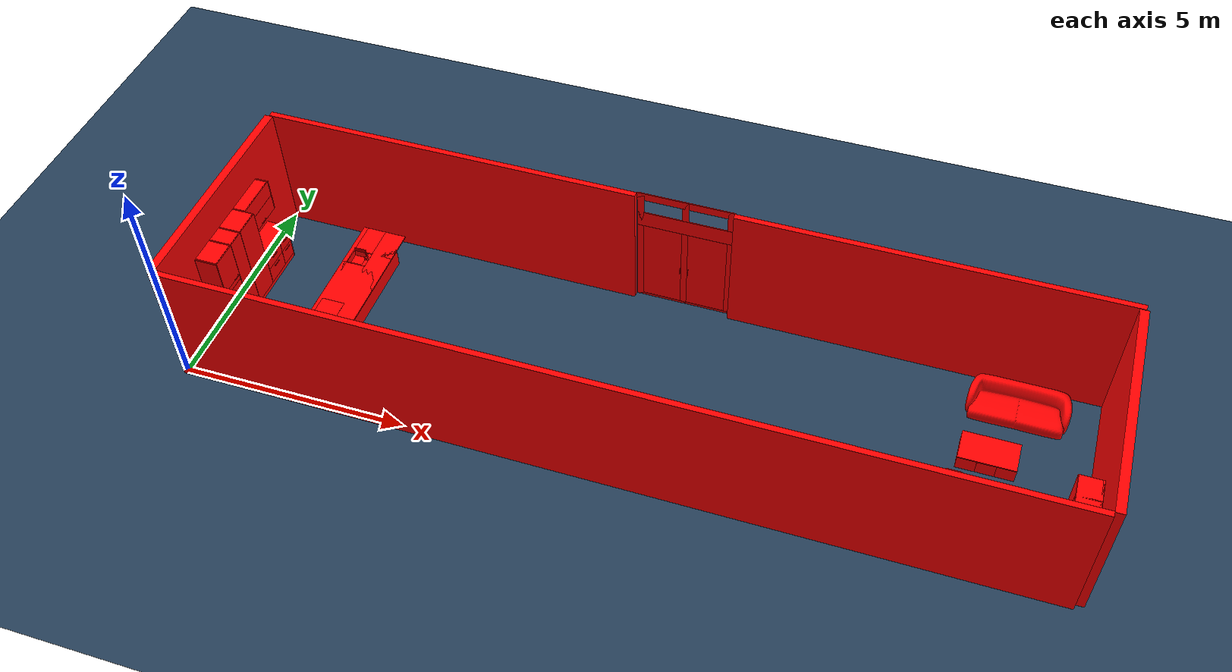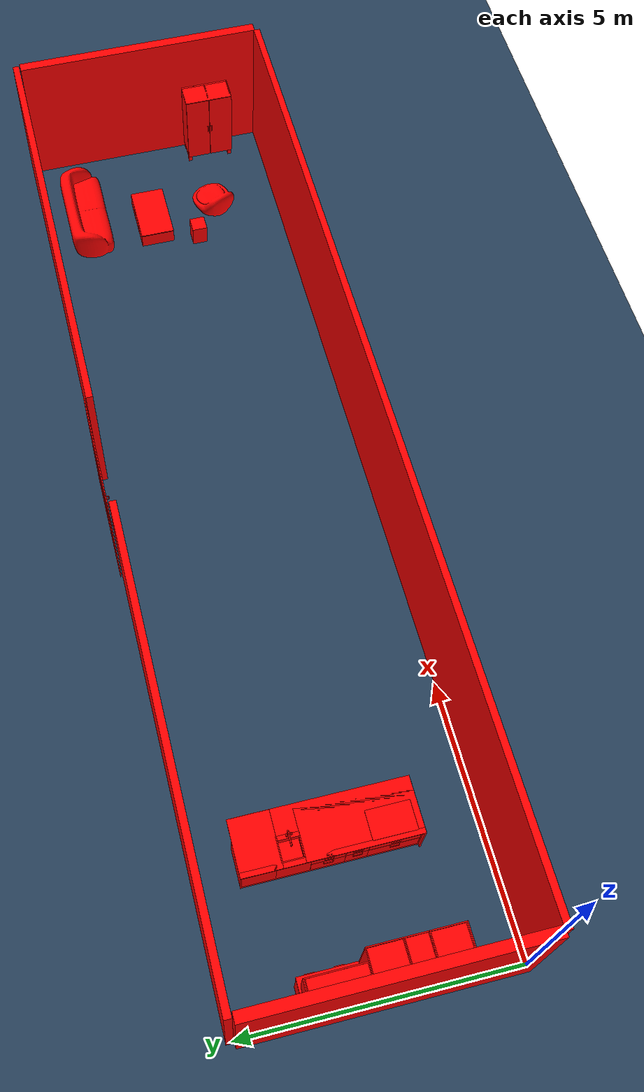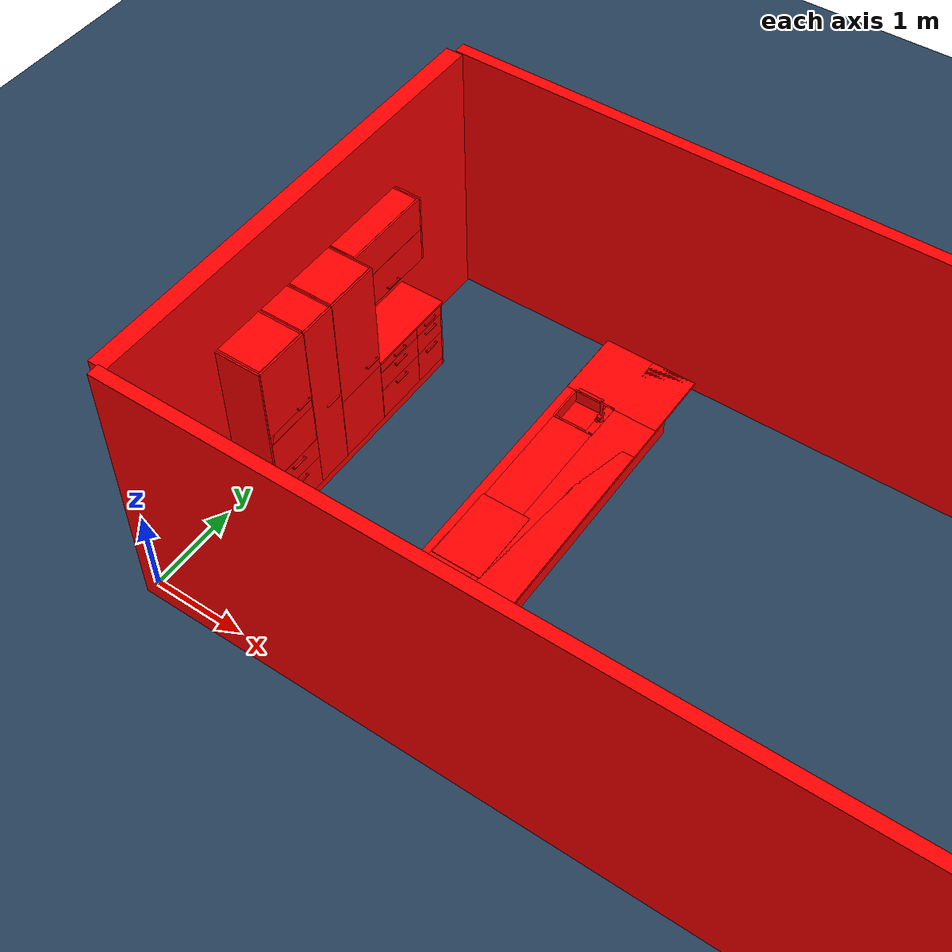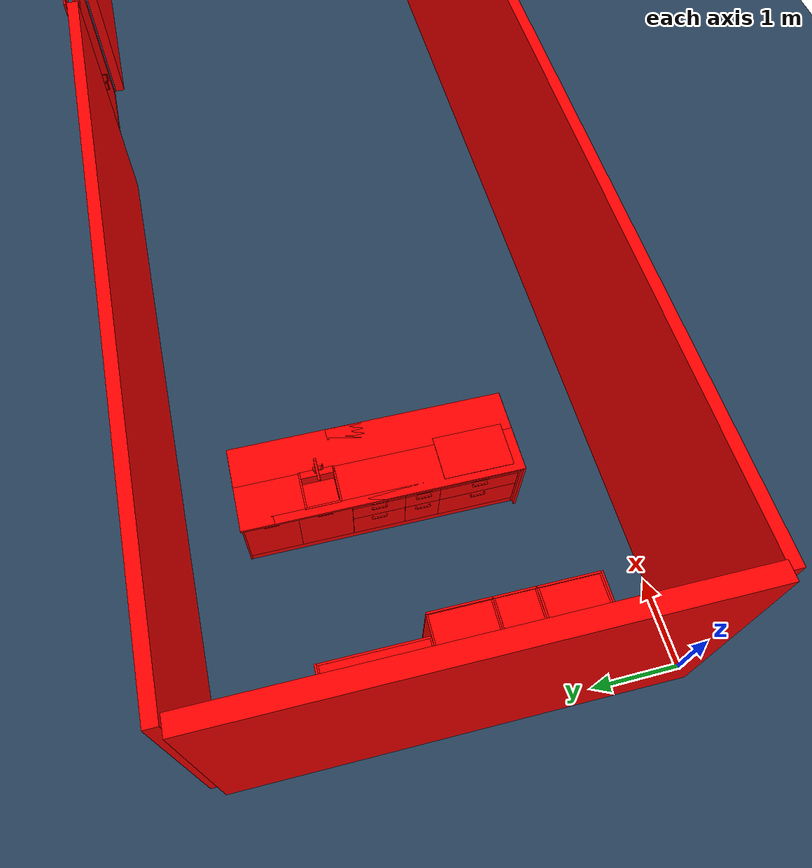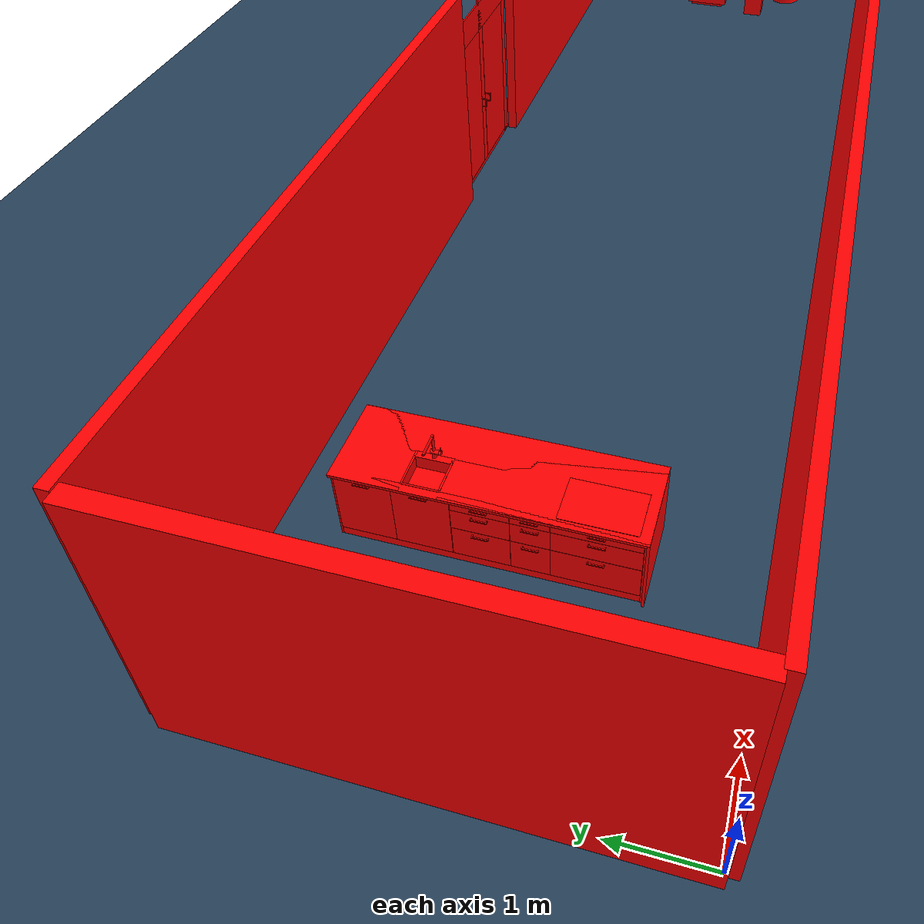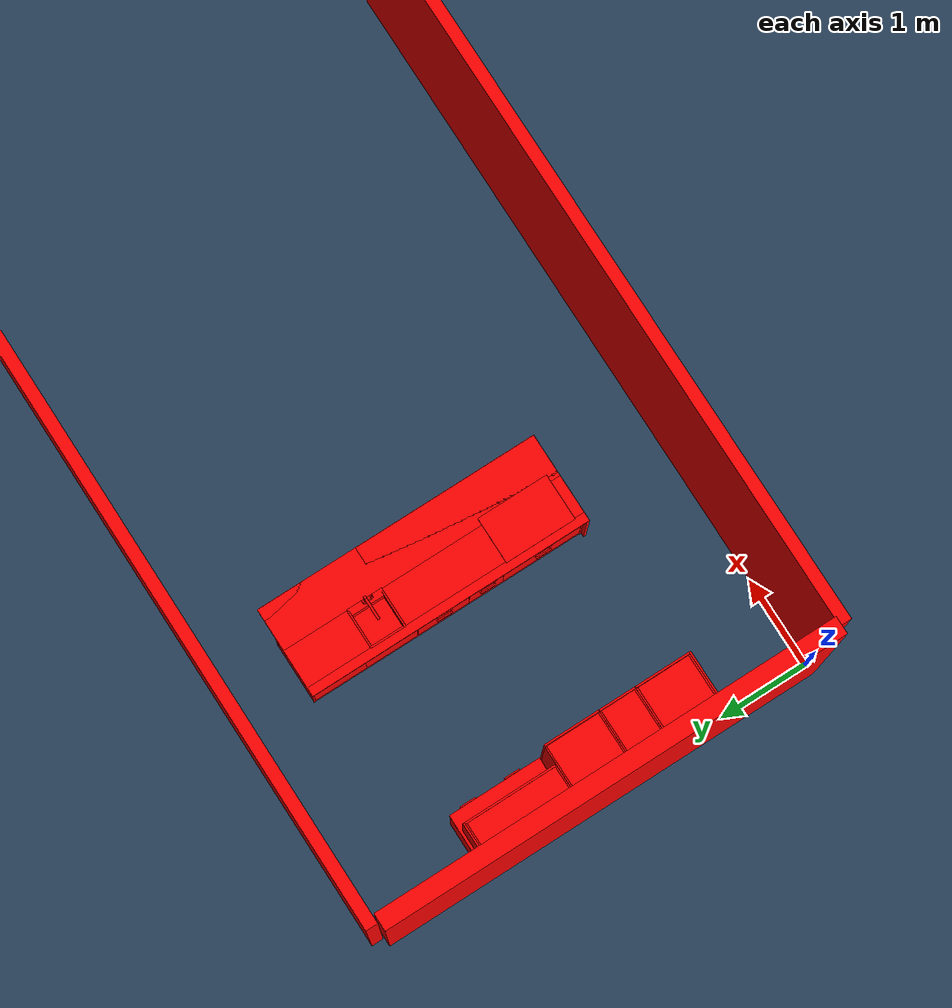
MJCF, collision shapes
<mujoco model="apartment">
    <compiler meshdir="apartment/" texturedir="apartment/obj/textures" angle="radian" autolimits="true" balanceinertia="true" boundmass="0.000001" boundinertia="0.000001"/>

    <statistic meansize="0.698866" extent="24.6878" center="9.40261 -0.0183012 1.53439"/>

    <option timestep="0.001" integrator="Euler" gravity="0 0 -9.81" noslip_iterations="2" noslip_tolerance="1e-9">
        <flag sensornoise="disable" energy="enable" contact="enable" />
    </option>

    <default>
        <geom condim="4" solimp="0.99 0.99 0" solref="0.01 1" />
        <joint damping="0.7" />
    </default>

    <default>
		<default class="visual">
			<geom contype="0" conaffinity="0"/>
		</default>
		<default class="collision">
			<geom rgba="1.0 0.0 0.0 0.0"/>
		</default>
	</default>

	<asset>
		<texture name="grid" type="2d" builtin="checker" width="512" height="512" rgb1=".1 .2 .3" rgb2=".2 .3 .4"/>
		<material name="grid" texture="grid" texrepeat="1 1" texuniform="true"/>
		<mesh name="SM_Wall_02_visual1d01d01d0" file="obj/SM_Wall_021d01d01d0.obj"/>
		<mesh name="SM_Wall_04_visual1d01d01d0" file="obj/SM_Wall_041d01d01d0.obj"/>
		<mesh name="SM_Window_Frame_visual1d01d01d0" file="obj/SM_Window_Frame1d01d01d0.obj"/>
		<texture name="armchair_visual1d01d01d0" type="2d" file="M_Sessel_M_Sessel_D.png"/>
		<material name="armchair_visual1d01d01d0" texture="armchair_visual1d01d01d0"/>
		<mesh name="armchair_visual1d01d01d0" file="obj/armchair1d01d01d0.obj"/>
		<mesh name="armchair_collision1d01d01d0" file="stl/armchair1d01d01d0.stl"/>
		<texture name="coffee_table_visual1d01d01d0" type="2d" file="M_Wood_Furniture_M_Wood_Furniture_D.png"/>
		<material name="coffee_table_visual1d01d01d0" texture="coffee_table_visual1d01d01d0"/>
		<mesh name="coffee_table_visual1d01d01d0" file="obj/coffee_table1d01d01d0.obj"/>
		<texture name="bedside_table_visual1d01d01d0" type="2d" file="M_Nachttisch_M_Nachttisch_D.png"/>
		<material name="bedside_table_visual1d01d01d0" texture="bedside_table_visual1d01d01d0"/>
		<mesh name="bedside_table_visual1d01d01d0" file="obj/bedside_table1d01d01d0.obj"/>
		<mesh name="SM_Window_Right_visual1d01d01d0" file="obj/SM_Window_Right1d01d01d0.obj"/>
		<mesh name="SM_Window_Left_visual1d01d01d0" file="obj/SM_Window_Left1d01d01d0.obj"/>
		<texture name="coffee_table_drawer_visual1d01d01d0" type="2d" file="M_Wood_Furniture_M_Wood_Furniture_D.png"/>
		<material name="coffee_table_drawer_visual1d01d01d0" texture="coffee_table_drawer_visual1d01d01d0"/>
		<mesh name="coffee_table_drawer_visual1d01d01d0" file="obj/coffee_table_drawer1d01d01d0.obj"/>
		<mesh name="SM_Wall_01_visual1d01d01d0" file="obj/SM_Wall_011d01d01d0.obj"/>
		<texture name="windows_without_4_visual1d01d01d0" type="2d" file="EnvSamplerTex.png"/>
		<material name="windows_without_4_visual1d01d01d0" texture="windows_without_4_visual1d01d01d0"/>
		<mesh name="windows_without_4_visual1d01d01d0" file="obj/windows_without_41d01d01d0.obj"/>
		<texture name="SM_Window_Handle_visual1d01d01d0" type="2d" file="M_Metal_Chrome_M_Metal_Chrome_D.png"/>
		<material name="SM_Window_Handle_visual1d01d01d0" texture="SM_Window_Handle_visual1d01d01d0"/>
		<mesh name="SM_Window_Handle_visual1d01d01d0" file="obj/SM_Window_Handle1d01d01d0.obj"/>
		<texture name="sofa_visual1d01d01d0" type="2d" file="M_Basic_Black_M_Basic_Black_D.png"/>
		<material name="sofa_visual1d01d01d0" texture="sofa_visual1d01d01d0"/>
		<mesh name="sofa_visual1d01d01d0" file="obj/sofa1d01d01d0.obj"/>
		<mesh name="sofa_collision1d01d01d0" file="stl/sofa1d01d01d0.stl"/>
		<mesh name="SM_Wall_03_visual1d01d01d0" file="obj/SM_Wall_031d01d01d0.obj"/>
		<texture name="wardrobe_visual1d01d01d0" type="2d" file="M_Metal_Dark_M_Metal_Dark_D.png"/>
		<material name="wardrobe_visual1d01d01d0" texture="wardrobe_visual1d01d01d0"/>
		<mesh name="wardrobe_visual1d01d01d0" file="obj/wardrobe1d01d01d0.obj"/>
		<texture name="SM_Dishwasher_Base_visual1d01d01d0" type="2d" file="M_Metal_Dishwasher_M_Metal_Dishwasher_D.png"/>
		<material name="SM_Dishwasher_Base_visual1d01d01d0" texture="SM_Dishwasher_Base_visual1d01d01d0"/>
		<mesh name="SM_Dishwasher_Base_visual1d01d01d0" file="obj/SM_Dishwasher_Base1d01d01d0.obj"/>
		<texture name="SM_Kitchen_08_Sink_Base_visual1d01d01d0" type="2d" file="M_Plastic_White_M_Plastic_White_D.png"/>
		<material name="SM_Kitchen_08_Sink_Base_visual1d01d01d0" texture="SM_Kitchen_08_Sink_Base_visual1d01d01d0"/>
		<mesh name="SM_Kitchen_08_Sink_Base_visual1d01d01d0" file="obj/SM_Kitchen_08_Sink_Base1d01d01d0.obj"/>
		<texture name="SM_Kitchen_09_Base_visual1d01d01d0" type="2d" file="M_Metal_Chrome_M_Metal_Chrome_D.png"/>
		<material name="SM_Kitchen_09_Base_visual1d01d01d0" texture="SM_Kitchen_09_Base_visual1d01d01d0"/>
		<mesh name="SM_Kitchen_09_Base_visual1d01d01d0" file="obj/SM_Kitchen_09_Base1d01d01d0.obj"/>
		<texture name="SM_Kitchen_10_Base_visual1d01d01d0" type="2d" file="M_Metal_Brushed_M_Metal_Brushed_D.png"/>
		<material name="SM_Kitchen_10_Base_visual1d01d01d0" texture="SM_Kitchen_10_Base_visual1d01d01d0"/>
		<mesh name="SM_Kitchen_10_Base_visual1d01d01d0" file="obj/SM_Kitchen_10_Base1d01d01d0.obj"/>
		<texture name="SM_Kitchen_11_Base_visual1d01d01d0" type="2d" file="M_Metal_Chrome_M_Metal_Chrome_D.png"/>
		<material name="SM_Kitchen_11_Base_visual1d01d01d0" texture="SM_Kitchen_11_Base_visual1d01d01d0"/>
		<mesh name="SM_Kitchen_11_Base_visual1d01d01d0" file="obj/SM_Kitchen_11_Base1d01d01d0.obj"/>
		<texture name="SM_Kitchen_Base_Board_02_visual1d01d01d0" type="2d" file="M_Kitchen_Fronts_M_Kitchen_Fronts_D.png"/>
		<material name="SM_Kitchen_Base_Board_02_visual1d01d01d0" texture="SM_Kitchen_Base_Board_02_visual1d01d01d0"/>
		<mesh name="SM_Kitchen_Base_Board_02_visual1d01d01d0" file="obj/SM_Kitchen_Base_Board_021d01d01d0.obj"/>
		<texture name="SM_Kitchen_Island_Cover_03_visual1d01d01d0" type="2d" file="M_Kitchen_Fronts_M_Kitchen_Fronts_D.png"/>
		<material name="SM_Kitchen_Island_Cover_03_visual1d01d01d0" texture="SM_Kitchen_Island_Cover_03_visual1d01d01d0"/>
		<mesh name="SM_Kitchen_Island_Cover_03_visual1d01d01d0" file="obj/SM_Kitchen_Island_Cover_031d01d01d0.obj"/>
		<texture name="wardrobe_door_left_visual1d01d01d0" type="2d" file="M_Metal_Chrome_M_Metal_Chrome_D.png"/>
		<material name="wardrobe_door_left_visual1d01d01d0" texture="wardrobe_door_left_visual1d01d01d0"/>
		<mesh name="wardrobe_door_left_visual1d01d01d0" file="obj/wardrobe_door_left1d01d01d0.obj"/>
		<texture name="wardrobe_door_right_visual1d01d01d0" type="2d" file="M_Metal_Chrome_M_Metal_Chrome_D.png"/>
		<material name="wardrobe_door_right_visual1d01d01d0" texture="wardrobe_door_right_visual1d01d01d0"/>
		<mesh name="wardrobe_door_right_visual1d01d01d0" file="obj/wardrobe_door_right1d01d01d0.obj"/>
		<texture name="SM_Dishwasher_Front_visual1d01d01d0" type="2d" file="M_Kitchen_Fronts_M_Kitchen_Fronts_D.png"/>
		<material name="SM_Dishwasher_Front_visual1d01d01d0" texture="SM_Dishwasher_Front_visual1d01d01d0"/>
		<mesh name="SM_Dishwasher_Front_visual1d01d01d0" file="obj/SM_Dishwasher_Front1d01d01d0.obj"/>
		<texture name="SM_Dishwasher_Tray_01_visual1d01d01d0" type="2d" file="M_Metal_Brushed_M_Metal_Brushed_D.png"/>
		<material name="SM_Dishwasher_Tray_01_visual1d01d01d0" texture="SM_Dishwasher_Tray_01_visual1d01d01d0"/>
		<mesh name="SM_Dishwasher_Tray_01_visual1d01d01d0" file="obj/SM_Dishwasher_Tray_011d01d01d0.obj"/>
		<texture name="SM_Dishwasher_Tray_02_visual1d01d01d0" type="2d" file="M_Metal_Brushed_M_Metal_Brushed_D.png"/>
		<material name="SM_Dishwasher_Tray_02_visual1d01d01d0" texture="SM_Dishwasher_Tray_02_visual1d01d01d0"/>
		<mesh name="SM_Dishwasher_Tray_02_visual1d01d01d0" file="obj/SM_Dishwasher_Tray_021d01d01d0.obj"/>
		<texture name="SM_Dishwasher_Tray_03_visual1d01d01d0" type="2d" file="M_Metal_Brushed_M_Metal_Brushed_D.png"/>
		<material name="SM_Dishwasher_Tray_03_visual1d01d01d0" texture="SM_Dishwasher_Tray_03_visual1d01d01d0"/>
		<mesh name="SM_Dishwasher_Tray_03_visual1d01d01d0" file="obj/SM_Dishwasher_Tray_031d01d01d0.obj"/>
		<texture name="SM_Kitchen_08_Sink_Drawer_01_visual1d01d01d0" type="2d" file="M_Kitchen_Fronts_M_Kitchen_Fronts_D.png"/>
		<material name="SM_Kitchen_08_Sink_Drawer_01_visual1d01d01d0" texture="SM_Kitchen_08_Sink_Drawer_01_visual1d01d01d0"/>
		<mesh name="SM_Kitchen_08_Sink_Drawer_01_visual1d01d01d0" file="obj/SM_Kitchen_08_Sink_Drawer_011d01d01d0.obj"/>
		<texture name="SM_Kitchen_08_Sink_Drawer_02_visual1d01d01d0" type="2d" file="M_Drawer_Mat_M_Drawer_Mat_D.png"/>
		<material name="SM_Kitchen_08_Sink_Drawer_02_visual1d01d01d0" texture="SM_Kitchen_08_Sink_Drawer_02_visual1d01d01d0"/>
		<mesh name="SM_Kitchen_08_Sink_Drawer_02_visual1d01d01d0" file="obj/SM_Kitchen_08_Sink_Drawer_021d01d01d0.obj"/>
		<texture name="SM_Kitchen_09_Drawer_01_visual1d01d01d0" type="2d" file="M_Drawer_Mat_M_Drawer_Mat_D.png"/>
		<material name="SM_Kitchen_09_Drawer_01_visual1d01d01d0" texture="SM_Kitchen_09_Drawer_01_visual1d01d01d0"/>
		<mesh name="SM_Kitchen_09_Drawer_01_visual1d01d01d0" file="obj/SM_Kitchen_09_Drawer_011d01d01d0.obj"/>
		<texture name="SM_Kitchen_09_Drawer_02_visual1d01d01d0" type="2d" file="M_Drawer_Mat_M_Drawer_Mat_D.png"/>
		<material name="SM_Kitchen_09_Drawer_02_visual1d01d01d0" texture="SM_Kitchen_09_Drawer_02_visual1d01d01d0"/>
		<mesh name="SM_Kitchen_09_Drawer_02_visual1d01d01d0" file="obj/SM_Kitchen_09_Drawer_021d01d01d0.obj"/>
		<texture name="SM_Kitchen_09_Drawer_03_visual1d01d01d0" type="2d" file="M_Drawer_Mat_M_Drawer_Mat_D.png"/>
		<material name="SM_Kitchen_09_Drawer_03_visual1d01d01d0" texture="SM_Kitchen_09_Drawer_03_visual1d01d01d0"/>
		<mesh name="SM_Kitchen_09_Drawer_03_visual1d01d01d0" file="obj/SM_Kitchen_09_Drawer_031d01d01d0.obj"/>
		<texture name="SM_Kitchen_10_Drawer_01_visual1d01d01d0" type="2d" file="M_Drawer_Mat_M_Drawer_Mat_D.png"/>
		<material name="SM_Kitchen_10_Drawer_01_visual1d01d01d0" texture="SM_Kitchen_10_Drawer_01_visual1d01d01d0"/>
		<mesh name="SM_Kitchen_10_Drawer_01_visual1d01d01d0" file="obj/SM_Kitchen_10_Drawer_011d01d01d0.obj"/>
		<texture name="SM_Kitchen_10_Drawer_02_visual1d01d01d0" type="2d" file="M_Drawer_Mat_M_Drawer_Mat_D.png"/>
		<material name="SM_Kitchen_10_Drawer_02_visual1d01d01d0" texture="SM_Kitchen_10_Drawer_02_visual1d01d01d0"/>
		<mesh name="SM_Kitchen_10_Drawer_02_visual1d01d01d0" file="obj/SM_Kitchen_10_Drawer_021d01d01d0.obj"/>
		<texture name="SM_Kitchen_10_Drawer_03_visual1d01d01d0" type="2d" file="M_Drawer_Mat_M_Drawer_Mat_D.png"/>
		<material name="SM_Kitchen_10_Drawer_03_visual1d01d01d0" texture="SM_Kitchen_10_Drawer_03_visual1d01d01d0"/>
		<mesh name="SM_Kitchen_10_Drawer_03_visual1d01d01d0" file="obj/SM_Kitchen_10_Drawer_031d01d01d0.obj"/>
		<texture name="SM_Kitchen_11_Drawer_01_visual1d01d01d0" type="2d" file="M_Drawer_Mat_M_Drawer_Mat_D.png"/>
		<material name="SM_Kitchen_11_Drawer_01_visual1d01d01d0" texture="SM_Kitchen_11_Drawer_01_visual1d01d01d0"/>
		<mesh name="SM_Kitchen_11_Drawer_01_visual1d01d01d0" file="obj/SM_Kitchen_11_Drawer_011d01d01d0.obj"/>
		<texture name="SM_Kitchen_11_Drawer_02_visual1d01d01d0" type="2d" file="M_Drawer_Mat_M_Drawer_Mat_D.png"/>
		<material name="SM_Kitchen_11_Drawer_02_visual1d01d01d0" texture="SM_Kitchen_11_Drawer_02_visual1d01d01d0"/>
		<mesh name="SM_Kitchen_11_Drawer_02_visual1d01d01d0" file="obj/SM_Kitchen_11_Drawer_021d01d01d0.obj"/>
		<texture name="SM_Kitchen_11_Drawer_03_visual1d01d01d0" type="2d" file="M_Drawer_Mat_M_Drawer_Mat_D.png"/>
		<material name="SM_Kitchen_11_Drawer_03_visual1d01d01d0" texture="SM_Kitchen_11_Drawer_03_visual1d01d01d0"/>
		<mesh name="SM_Kitchen_11_Drawer_03_visual1d01d01d0" file="obj/SM_Kitchen_11_Drawer_031d01d01d0.obj"/>
		<texture name="wardrobe_door_handle_visual1d01d01d0" type="2d" file="M_Metal_Dark_M_Metal_Dark_D.png"/>
		<material name="wardrobe_door_handle_visual1d01d01d0" texture="wardrobe_door_handle_visual1d01d01d0"/>
		<mesh name="wardrobe_door_handle_visual1d01d01d0" file="obj/wardrobe_door_handle1d01d01d0.obj"/>
		<texture name="SM_Counter_Sink_Stove_visual1d01d01d0" type="2d" file="M_Wood_Counter_M_Wood_Counter_D.png"/>
		<material name="SM_Counter_Sink_Stove_visual1d01d01d0" texture="SM_Counter_Sink_Stove_visual1d01d01d0"/>
		<mesh name="SM_Counter_Sink_Stove_visual1d01d01d0" file="obj/SM_Counter_Sink_Stove1d01d01d0.obj"/>
		<texture name="SM_Counter_Sink_visual1d01d01d0" type="2d" file="M_Metal_Chrome_Matte_M_Metal_Chrome_Matte_D.png"/>
		<material name="SM_Counter_Sink_visual1d01d01d0" texture="SM_Counter_Sink_visual1d01d01d0"/>
		<mesh name="SM_Counter_Sink_visual1d01d01d0" file="obj/SM_Counter_Sink1d01d01d0.obj"/>
		<texture name="SM_Kitchen_Handle_visual1d01d01d0" type="2d" file="M_Metal_Brushed_M_Metal_Brushed_D.png"/>
		<material name="SM_Kitchen_Handle_visual1d01d01d0" texture="SM_Kitchen_Handle_visual1d01d01d0"/>
		<mesh name="SM_Kitchen_Handle_visual1d01d01d0" file="obj/SM_Kitchen_Handle1d01d01d0.obj"/>
		<texture name="SM_Stove_visual1d01d01d0" type="2d" file="M_Basic_Black_02_M_Basic_Black_02_D.png"/>
		<material name="SM_Stove_visual1d01d01d0" texture="SM_Stove_visual1d01d01d0"/>
		<mesh name="SM_Stove_visual1d01d01d0" file="obj/SM_Stove1d01d01d0.obj"/>
		<texture name="SM_Kitchen_02_Base_visual1d01d01d0" type="2d" file="M_Metal_Chrome_M_Metal_Chrome_D.png"/>
		<material name="SM_Kitchen_02_Base_visual1d01d01d0" texture="SM_Kitchen_02_Base_visual1d01d01d0"/>
		<mesh name="SM_Kitchen_02_Base_visual1d01d01d0" file="obj/SM_Kitchen_02_Base1d01d01d0.obj"/>
		<texture name="SM_Kitchen_02_Shelf_visual1d01d01d0" type="2d" file="M_Metal_Chrome_M_Metal_Chrome_D.png"/>
		<material name="SM_Kitchen_02_Shelf_visual1d01d01d0" texture="SM_Kitchen_02_Shelf_visual1d01d01d0"/>
		<mesh name="SM_Kitchen_02_Shelf_visual1d01d01d0" file="obj/SM_Kitchen_02_Shelf1d01d01d0.obj"/>
		<texture name="SM_Kitchen_03_Fridge_visual1d01d01d0" type="2d" file="M_Kitchen_Fronts_M_Kitchen_Fronts_D.png"/>
		<material name="SM_Kitchen_03_Fridge_visual1d01d01d0" texture="SM_Kitchen_03_Fridge_visual1d01d01d0"/>
		<mesh name="SM_Kitchen_03_Fridge_visual1d01d01d0" file="obj/SM_Kitchen_03_Fridge1d01d01d0.obj"/>
		<texture name="SM_Fridge_Base_visual1d01d01d0" type="2d" file="M_Display_M_Display_D.png"/>
		<material name="SM_Fridge_Base_visual1d01d01d0" texture="SM_Fridge_Base_visual1d01d01d0"/>
		<mesh name="SM_Fridge_Base_visual1d01d01d0" file="obj/SM_Fridge_Base1d01d01d0.obj"/>
		<texture name="SM_Fridge_Shelf_visual1d01d01d0" type="2d" file="M_Metal_Fridge_M_Metal_Fridge_D.png"/>
		<material name="SM_Fridge_Shelf_visual1d01d01d0" texture="SM_Fridge_Shelf_visual1d01d01d0"/>
		<mesh name="SM_Fridge_Shelf_visual1d01d01d0" file="obj/SM_Fridge_Shelf1d01d01d0.obj"/>
		<texture name="SM_Kitchen_04_Base_visual1d01d01d0" type="2d" file="M_Kitchen_Fronts_M_Kitchen_Fronts_D.png"/>
		<material name="SM_Kitchen_04_Base_visual1d01d01d0" texture="SM_Kitchen_04_Base_visual1d01d01d0"/>
		<mesh name="SM_Kitchen_04_Base_visual1d01d01d0" file="obj/SM_Kitchen_04_Base1d01d01d0.obj"/>
		<texture name="SM_Kitchen_04_Door_02_visual1d01d01d0" type="2d" file="M_Kitchen_Fronts_M_Kitchen_Fronts_D.png"/>
		<material name="SM_Kitchen_04_Door_02_visual1d01d01d0" texture="SM_Kitchen_04_Door_02_visual1d01d01d0"/>
		<mesh name="SM_Kitchen_04_Door_02_visual1d01d01d0" file="obj/SM_Kitchen_04_Door_021d01d01d0.obj"/>
		<mesh name="SM_Kitchen_04_Shelf_visual1d01d01d0" file="obj/SM_Kitchen_04_Shelf1d01d01d0.obj"/>
		<texture name="SM_Counter_Wall_visual1d01d01d0" type="2d" file="M_Wood_Counter_M_Wood_Counter_D.png"/>
		<material name="SM_Counter_Wall_visual1d01d01d0" texture="SM_Counter_Wall_visual1d01d01d0"/>
		<mesh name="SM_Counter_Wall_visual1d01d01d0" file="obj/SM_Counter_Wall1d01d01d0.obj"/>
		<texture name="SM_Kitchen_06_Base_visual1d01d01d0" type="2d" file="M_Metal_Brushed_M_Metal_Brushed_D.png"/>
		<material name="SM_Kitchen_06_Base_visual1d01d01d0" texture="SM_Kitchen_06_Base_visual1d01d01d0"/>
		<mesh name="SM_Kitchen_06_Base_visual1d01d01d0" file="obj/SM_Kitchen_06_Base1d01d01d0.obj"/>
		<texture name="SM_Kitchen_Island_Cover_04_visual1d01d01d0" type="2d" file="M_Kitchen_Fronts_M_Kitchen_Fronts_D.png"/>
		<material name="SM_Kitchen_Island_Cover_04_visual1d01d01d0" texture="SM_Kitchen_Island_Cover_04_visual1d01d01d0"/>
		<mesh name="SM_Kitchen_Island_Cover_04_visual1d01d01d0" file="obj/SM_Kitchen_Island_Cover_041d01d01d0.obj"/>
		<texture name="SM_Counter_Watertab_visual1d01d01d0" type="2d" file="M_Metal_Chrome_Matte_M_Metal_Chrome_Matte_D.png"/>
		<material name="SM_Counter_Watertab_visual1d01d01d0" texture="SM_Counter_Watertab_visual1d01d01d0"/>
		<mesh name="SM_Counter_Watertab_visual1d01d01d0" file="obj/SM_Counter_Watertab1d01d01d0.obj"/>
		<texture name="SM_Kitchen_Island_Cover_01_visual1d01d01d0" type="2d" file="M_Kitchen_Fronts_M_Kitchen_Fronts_D.png"/>
		<material name="SM_Kitchen_Island_Cover_01_visual1d01d01d0" texture="SM_Kitchen_Island_Cover_01_visual1d01d01d0"/>
		<mesh name="SM_Kitchen_Island_Cover_01_visual1d01d01d0" file="obj/SM_Kitchen_Island_Cover_011d01d01d0.obj"/>
		<texture name="SM_Kitchen_02_Door_visual1d01d01d0" type="2d" file="M_Kitchen_Fronts_M_Kitchen_Fronts_D.png"/>
		<material name="SM_Kitchen_02_Door_visual1d01d01d0" texture="SM_Kitchen_02_Door_visual1d01d01d0"/>
		<mesh name="SM_Kitchen_02_Door_visual1d01d01d0" file="obj/SM_Kitchen_02_Door1d01d01d0.obj"/>
		<texture name="SM_Kitchen_02_Drawer_01_visual1d01d01d0" type="2d" file="M_Drawer_Mat_M_Drawer_Mat_D.png"/>
		<material name="SM_Kitchen_02_Drawer_01_visual1d01d01d0" texture="SM_Kitchen_02_Drawer_01_visual1d01d01d0"/>
		<mesh name="SM_Kitchen_02_Drawer_01_visual1d01d01d0" file="obj/SM_Kitchen_02_Drawer_011d01d01d0.obj"/>
		<texture name="SM_Kitchen_02_Drawer_02_visual1d01d01d0" type="2d" file="M_Drawer_Mat_M_Drawer_Mat_D.png"/>
		<material name="SM_Kitchen_02_Drawer_02_visual1d01d01d0" texture="SM_Kitchen_02_Drawer_02_visual1d01d01d0"/>
		<mesh name="SM_Kitchen_02_Drawer_02_visual1d01d01d0" file="obj/SM_Kitchen_02_Drawer_021d01d01d0.obj"/>
		<texture name="SM_Fridge_Door_01_visual1d01d01d0" type="2d" file="M_Kitchen_Fronts_M_Kitchen_Fronts_D.png"/>
		<material name="SM_Fridge_Door_01_visual1d01d01d0" texture="SM_Fridge_Door_01_visual1d01d01d0"/>
		<mesh name="SM_Fridge_Door_01_visual1d01d01d0" file="obj/SM_Fridge_Door_011d01d01d0.obj"/>
		<texture name="SM_Fridge_Door_02_visual1d01d01d0" type="2d" file="M_Kitchen_Fronts_M_Kitchen_Fronts_D.png"/>
		<material name="SM_Fridge_Door_02_visual1d01d01d0" texture="SM_Fridge_Door_02_visual1d01d01d0"/>
		<mesh name="SM_Fridge_Door_02_visual1d01d01d0" file="obj/SM_Fridge_Door_021d01d01d0.obj"/>
		<texture name="SM_Fridge_Drawer_01_visual1d01d01d0" type="2d" file="M_Metal_Fridge_M_Metal_Fridge_D.png"/>
		<material name="SM_Fridge_Drawer_01_visual1d01d01d0" texture="SM_Fridge_Drawer_01_visual1d01d01d0"/>
		<mesh name="SM_Fridge_Drawer_01_visual1d01d01d0" file="obj/SM_Fridge_Drawer_011d01d01d0.obj"/>
		<texture name="SM_Fridge_Drawer_02_visual1d01d01d0" type="2d" file="M_Metal_Fridge_M_Metal_Fridge_D.png"/>
		<material name="SM_Fridge_Drawer_02_visual1d01d01d0" texture="SM_Fridge_Drawer_02_visual1d01d01d0"/>
		<mesh name="SM_Fridge_Drawer_02_visual1d01d01d0" file="obj/SM_Fridge_Drawer_021d01d01d0.obj"/>
		<texture name="SM_Fridge_Drawer_03_visual1d01d01d0" type="2d" file="M_Metal_Fridge_M_Metal_Fridge_D.png"/>
		<material name="SM_Fridge_Drawer_03_visual1d01d01d0" texture="SM_Fridge_Drawer_03_visual1d01d01d0"/>
		<mesh name="SM_Fridge_Drawer_03_visual1d01d01d0" file="obj/SM_Fridge_Drawer_031d01d01d0.obj"/>
		<texture name="SM_Fridge_Drawer_04_visual1d01d01d0" type="2d" file="M_Metal_Fridge_M_Metal_Fridge_D.png"/>
		<material name="SM_Fridge_Drawer_04_visual1d01d01d0" texture="SM_Fridge_Drawer_04_visual1d01d01d0"/>
		<mesh name="SM_Fridge_Drawer_04_visual1d01d01d0" file="obj/SM_Fridge_Drawer_041d01d01d0.obj"/>
		<texture name="SM_Fridge_Drawer_05_visual1d01d01d0" type="2d" file="M_Metal_Fridge_M_Metal_Fridge_D.png"/>
		<material name="SM_Fridge_Drawer_05_visual1d01d01d0" texture="SM_Fridge_Drawer_05_visual1d01d01d0"/>
		<mesh name="SM_Fridge_Drawer_05_visual1d01d01d0" file="obj/SM_Fridge_Drawer_051d01d01d0.obj"/>
		<texture name="SM_Kitchen_06_Drawer_01_visual1d01d01d0" type="2d" file="M_Drawer_Mat_M_Drawer_Mat_D.png"/>
		<material name="SM_Kitchen_06_Drawer_01_visual1d01d01d0" texture="SM_Kitchen_06_Drawer_01_visual1d01d01d0"/>
		<mesh name="SM_Kitchen_06_Drawer_01_visual1d01d01d0" file="obj/SM_Kitchen_06_Drawer_011d01d01d0.obj"/>
		<texture name="SM_Kitchen_06_Drawer_02_visual1d01d01d0" type="2d" file="M_Drawer_Mat_M_Drawer_Mat_D.png"/>
		<material name="SM_Kitchen_06_Drawer_02_visual1d01d01d0" texture="SM_Kitchen_06_Drawer_02_visual1d01d01d0"/>
		<mesh name="SM_Kitchen_06_Drawer_02_visual1d01d01d0" file="obj/SM_Kitchen_06_Drawer_021d01d01d0.obj"/>
		<texture name="SM_Kitchen_06_Drawer_03_visual1d01d01d0" type="2d" file="M_Drawer_Mat_M_Drawer_Mat_D.png"/>
		<material name="SM_Kitchen_06_Drawer_03_visual1d01d01d0" texture="SM_Kitchen_06_Drawer_03_visual1d01d01d0"/>
		<mesh name="SM_Kitchen_06_Drawer_03_visual1d01d01d0" file="obj/SM_Kitchen_06_Drawer_031d01d01d0.obj"/>
		<texture name="SM_Counter_Sink_Tap_visual1d01d01d0" type="2d" file="M_Blue_M_Blue_D.png"/>
		<material name="SM_Counter_Sink_Tap_visual1d01d01d0" texture="SM_Counter_Sink_Tap_visual1d01d01d0"/>
		<mesh name="SM_Counter_Sink_Tap_visual1d01d01d0" file="obj/SM_Counter_Sink_Tap1d01d01d0.obj"/>
		<texture name="SM_Kitchen_01_Base_visual1d01d01d0" type="2d" file="M_Kitchen_Fronts_M_Kitchen_Fronts_D.png"/>
		<material name="SM_Kitchen_01_Base_visual1d01d01d0" texture="SM_Kitchen_01_Base_visual1d01d01d0"/>
		<mesh name="SM_Kitchen_01_Base_visual1d01d01d0" file="obj/SM_Kitchen_01_Base1d01d01d0.obj"/>
		<texture name="SM_Oven_visual1d01d01d0" type="2d" file="M_Basic_Black_M_Basic_Black_D.png"/>
		<material name="SM_Oven_visual1d01d01d0" texture="SM_Oven_visual1d01d01d0"/>
		<mesh name="SM_Oven_visual1d01d01d0" file="obj/SM_Oven1d01d01d0.obj"/>
		<texture name="SM_Fridge_Door_Tray_01_visual1d01d01d0" type="2d" file="M_Metal_Brushed_M_Metal_Brushed_D.png"/>
		<material name="SM_Fridge_Door_Tray_01_visual1d01d01d0" texture="SM_Fridge_Door_Tray_01_visual1d01d01d0"/>
		<mesh name="SM_Fridge_Door_Tray_01_visual1d01d01d0" file="obj/SM_Fridge_Door_Tray_011d01d01d0.obj"/>
		<texture name="SM_Kitchen_04_Door_01_visual1d01d01d0" type="2d" file="M_Kitchen_Fronts_M_Kitchen_Fronts_D.png"/>
		<material name="SM_Kitchen_04_Door_01_visual1d01d01d0" texture="SM_Kitchen_04_Door_01_visual1d01d01d0"/>
		<mesh name="SM_Kitchen_04_Door_01_visual1d01d01d0" file="obj/SM_Kitchen_04_Door_011d01d01d0.obj"/>
		<texture name="SM_Kitchen_01_Door_01_visual1d01d01d0" type="2d" file="M_Kitchen_Fronts_M_Kitchen_Fronts_D.png"/>
		<material name="SM_Kitchen_01_Door_01_visual1d01d01d0" texture="SM_Kitchen_01_Door_01_visual1d01d01d0"/>
		<mesh name="SM_Kitchen_01_Door_01_visual1d01d01d0" file="obj/SM_Kitchen_01_Door_011d01d01d0.obj"/>
		<texture name="SM_Kitchen_01_Drawer_01_visual1d01d01d0" type="2d" file="M_Drawer_Mat_M_Drawer_Mat_D.png"/>
		<material name="SM_Kitchen_01_Drawer_01_visual1d01d01d0" texture="SM_Kitchen_01_Drawer_01_visual1d01d01d0"/>
		<mesh name="SM_Kitchen_01_Drawer_01_visual1d01d01d0" file="obj/SM_Kitchen_01_Drawer_011d01d01d0.obj"/>
		<texture name="SM_Kitchen_01_Drawer_02_visual1d01d01d0" type="2d" file="M_Drawer_Mat_M_Drawer_Mat_D.png"/>
		<material name="SM_Kitchen_01_Drawer_02_visual1d01d01d0" texture="SM_Kitchen_01_Drawer_02_visual1d01d01d0"/>
		<mesh name="SM_Kitchen_01_Drawer_02_visual1d01d01d0" file="obj/SM_Kitchen_01_Drawer_021d01d01d0.obj"/>
		<texture name="SM_Oven_Door_visual1d01d01d0" type="2d" file="M_OvenBase_M_OvenBase_D.png"/>
		<material name="SM_Oven_Door_visual1d01d01d0" texture="SM_Oven_Door_visual1d01d01d0"/>
		<mesh name="SM_Oven_Door_visual1d01d01d0" file="obj/SM_Oven_Door1d01d01d0.obj"/>
		<texture name="SM_Kitchen_05_Base_visual1d01d01d0" type="2d" file="M_Metal_Chrome_M_Metal_Chrome_D.png"/>
		<material name="SM_Kitchen_05_Base_visual1d01d01d0" texture="SM_Kitchen_05_Base_visual1d01d01d0"/>
		<mesh name="SM_Kitchen_05_Base_visual1d01d01d0" file="obj/SM_Kitchen_05_Base1d01d01d0.obj"/>
		<texture name="SM_Kitchen_05_Drawer_01_visual1d01d01d0" type="2d" file="M_Drawer_Mat_M_Drawer_Mat_D.png"/>
		<material name="SM_Kitchen_05_Drawer_01_visual1d01d01d0" texture="SM_Kitchen_05_Drawer_01_visual1d01d01d0"/>
		<mesh name="SM_Kitchen_05_Drawer_01_visual1d01d01d0" file="obj/SM_Kitchen_05_Drawer_011d01d01d0.obj"/>
		<texture name="SM_Kitchen_05_Drawer_02_visual1d01d01d0" type="2d" file="M_Drawer_Mat_M_Drawer_Mat_D.png"/>
		<material name="SM_Kitchen_05_Drawer_02_visual1d01d01d0" texture="SM_Kitchen_05_Drawer_02_visual1d01d01d0"/>
		<mesh name="SM_Kitchen_05_Drawer_02_visual1d01d01d0" file="obj/SM_Kitchen_05_Drawer_021d01d01d0.obj"/>
		<texture name="SM_Kitchen_05_Drawer_03_visual1d01d01d0" type="2d" file="M_Drawer_Mat_M_Drawer_Mat_D.png"/>
		<material name="SM_Kitchen_05_Drawer_03_visual1d01d01d0" texture="SM_Kitchen_05_Drawer_03_visual1d01d01d0"/>
		<mesh name="SM_Kitchen_05_Drawer_03_visual1d01d01d0" file="obj/SM_Kitchen_05_Drawer_031d01d01d0.obj"/>
		<texture name="SM_Fridge_Door_Tray_02_visual1d01d01d0" type="2d" file="M_Metal_Brushed_M_Metal_Brushed_D.png"/>
		<material name="SM_Fridge_Door_Tray_02_visual1d01d01d0" texture="SM_Fridge_Door_Tray_02_visual1d01d01d0"/>
		<mesh name="SM_Fridge_Door_Tray_02_visual1d01d01d0" file="obj/SM_Fridge_Door_Tray_021d01d01d0.obj"/>
		<texture name="SM_Kitchen_Base_Board_01_visual1d01d01d0" type="2d" file="M_Kitchen_Fronts_M_Kitchen_Fronts_D.png"/>
		<material name="SM_Kitchen_Base_Board_01_visual1d01d01d0" texture="SM_Kitchen_Base_Board_01_visual1d01d01d0"/>
		<mesh name="SM_Kitchen_Base_Board_01_visual1d01d01d0" file="obj/SM_Kitchen_Base_Board_011d01d01d0.obj"/>
		<texture name="SM_Fridge_Egg_Tray_visual1d01d01d0" type="2d" file="M_Rubber_Plastic_M_Rubber_Plastic_D.png"/>
		<material name="SM_Fridge_Egg_Tray_visual1d01d01d0" texture="SM_Fridge_Egg_Tray_visual1d01d01d0"/>
		<mesh name="SM_Fridge_Egg_Tray_visual1d01d01d0" file="obj/SM_Fridge_Egg_Tray1d01d01d0.obj"/>
	</asset>
	<worldbody>
		<geom name="floor" size="0 0 0.05" type="plane" material="grid" condim="4" friction="2 0.05 0.01"/>
		<light diffuse=".5 .5 .5" pos="2.5 2.5 5" dir="0 0 -1"/>
	</worldbody>
	<worldbody>
        <body name="apartment_root" >
		<body name="envelope_root" pos="8.85 1.75 0.0" quat="1.0 0.0 0.0 0.0">
			<body name="wall2" pos="0.0 0.0 -0.2" quat="1.0 0.0 0.0 0.0">
				<geom name="wall2_visual_0" pos="0.0 0.0 0.0" quat="1.0 0.0 0.0 0.0" class="visual" type="mesh" mesh="SM_Wall_02_visual1d01d01d0"/>
				<geom name="wall2_collision_0" pos="-8.875 0.713447 1.73439" quat="1.0 0.0 0.0 0.0" class="collision" type="box" size="0.094776 2.48345 1.52585"/>
			</body>
			<body name="wall4" pos="0.0 0.0 -0.2" quat="1.0 0.0 0.0 0.0">
				<geom name="wall4_collision_0" pos="9.98022 0.713447 1.73439" quat="1.0 0.0 0.0 0.0" class="collision" type="box" size="0.094776 2.48345 1.52585"/>
				<geom name="wall4_visual_0" pos="0.0 0.0 0.0" quat="1.0 0.0 0.0 0.0" class="visual" type="mesh" mesh="SM_Wall_04_visual1d01d01d0"/>
			</body>
			<body name="window4_frame" pos="0.6710980000000006 3.37273 1.52145" quat="0.7071067811865476 0.0 0.0 -0.7071067811865475">
				<geom name="window4_frame_collision_2" pos="0.0 0.0 -1.49481" quat="0.7253440562932877 0.0 0.0 0.0" class="collision" type="box" size="0.01 1.0677 0.026796"/>
				<geom name="window4_frame_collision_0" pos="0.0 0.0 1.42883" quat="0.7366267711670544 0.0 0.0 0.0" class="collision" type="box" size="0.01 1.0677 0.092776"/>
				<geom name="window4_frame_visual_0" pos="0.0 0.0 0.0" quat="1.0 0.0 0.0 0.0" class="visual" type="mesh" mesh="SM_Window_Frame_visual1d01d01d0"/>
				<geom name="window4_frame_collision_4" pos="0.0 -0.992126 0.0" quat="0.8073388384067746 0.0 0.0 0.0" class="collision" type="box" size="0.01 0.075574 1.52161"/>
				<geom name="window4_frame_collision_1" pos="0.0 0.0 0.795222" quat="0.7528014346426287 0.0 0.0 0.0" class="collision" type="box" size="0.01 1.0677 0.18914"/>
				<geom name="window4_frame_collision_3" pos="0.0 0.992126 0.0" quat="0.8073388384067746 0.0 0.0 0.0" class="collision" type="box" size="0.01 0.075574 1.52161"/>
				<geom name="window4_frame_collision_5" pos="0.0 0.0 0.0" quat="0.8069597263804433 0.0 0.0 0.0" class="collision" type="box" size="0.01 0.073126 1.52161"/>
				<body name="window4_right" pos="0.0 -0.9165519999999994 -0.42547099999999993" quat="1.0 0.0 0.0 0.0">
					<geom name="window4_right_collision_0" pos="0.0 0.421713 0.0" quat="0.784739287916694 0.0 0.0 0.0" class="collision" type="box" size="0.01 0.421713 1.03155"/>
					<geom name="window4_right_visual_0" pos="0.0 0.0 0.0" quat="1.0 0.0 0.0 0.0" class="visual" type="mesh" mesh="SM_Window_Right_visual1d01d01d0"/>
					<joint name="window4_right_joint" pos="6.661338147750939e-16 -1.4791141972893971e-31 -5.551115123125783e-17" type="hinge" range="0.0 1.5708000552204227" axis="0.0 0.0 -1.0000000000000004"/>
					<body name="window4_right_handle_rotation" pos="0.009999999999999787 0.8341069999999995 0.0" quat="1.0 0.0 0.0 0.0">
						<joint name="window4_right_handle_rotation_joint" pos="-5.551115123125783e-16 2.133709875451474e-16 0.0" type="hinge" range="0.0 1.5708000552204227" axis="-0.9999999999999998 0.0 2.220446049250313e-16"/>
						<body name="window4_right_handle" pos="0.06723500000000016 0.0 -0.057755" quat="1.0 0.0 0.0 0.0">
							<geom name="window4_right_handle_collision_1" pos="0.0 0.0 0.0" quat="1.0 0.0 0.0 0.0" class="collision" type="cylinder" size="0.008 0.065813"/>
							<geom name="window4_right_handle_collision_0" pos="-0.029618 0.0 0.057814" quat="0.7071067811865476 0.0 0.7071067811865475 0.0" class="collision" type="cylinder" size="0.008 0.037618"/>
							<geom name="window4_right_handle_visual_0" pos="0.0 0.0 0.0" quat="1.0 0.0 0.0 0.0" class="visual" type="mesh" mesh="SM_Window_Handle_visual1d01d01d0"/>
							<geom name="window4_right_handle_collision_2" pos="-0.018476 0.0 -0.057813" quat="0.7071067811865476 0.0 0.7071067811865475 0.0" class="collision" type="cylinder" size="0.008 0.026476"/>
						</body>
					</body>
				</body>
				<body name="window4_left" pos="0.001620000000000843 0.9291119999999999 -0.42547099999999993" quat="1.0 0.0 0.0 0.0">
					<geom name="window4_left_collision_0" pos="0.0 -0.43203 0.0" quat="0.7863809509391743 0.0 0.0 0.0" class="collision" type="box" size="0.01 0.43203 1.03155"/>
					<geom name="window4_left_visual_0" pos="0.0 0.0 0.0" quat="1.0 0.0 0.0 0.0" class="visual" type="mesh" mesh="SM_Window_Left_visual1d01d01d0"/>
					<joint name="window4_left_joint" pos="-1.1102230246251585e-16 -8.430756093247282e-16 -5.551115123125783e-17" type="hinge" range="0.0 1.5708000552204227" axis="0.0 0.0 1.0"/>
					<body name="window4_left_handle_rotation" pos="0.009999999999998899 -0.8341069999999995 0.0" quat="1.0 0.0 0.0 0.0">
						<joint name="window4_left_handle_rotation_joint" pos="5.551115123125785e-16 1.1015494072452723e-15 0.0" type="hinge" range="0.0 1.5708000552204227" axis="0.9999999999999998 0.0 2.220446049250313e-16"/>
						<body name="window4_left_handle" pos="0.06723500000000016 0.0 -0.057755" quat="1.0 0.0 0.0 0.0">
							<geom name="window4_left_handle_collision_0" pos="-0.029618 0.0 0.057814" quat="0.7071067811865476 0.0 0.7071067811865475 0.0" class="collision" type="cylinder" size="0.008 0.037618"/>
							<geom name="window4_left_handle_collision_2" pos="-0.018476 0.0 -0.057813" quat="0.7071067811865476 0.0 0.7071067811865475 0.0" class="collision" type="cylinder" size="0.008 0.026476"/>
							<geom name="window4_left_handle_collision_1" pos="0.0 0.0 0.0" quat="1.0 0.0 0.0 0.0" class="collision" type="cylinder" size="0.008 0.065813"/>
							<geom name="window4_left_handle_visual_0" pos="0.0 0.0 0.0" quat="1.0 0.0 0.0 0.0" class="visual" type="mesh" material="SM_Window_Handle_visual1d01d01d0" mesh="SM_Window_Handle_visual1d01d01d0"/>
						</body>
					</body>
				</body>
			</body>
			<body name="wall1" pos="0.0 0.0 -0.2" quat="1.0 0.0 0.0 0.0">
				<geom name="wall1_visual_0" pos="0.0 0.0 0.0" quat="1.0 0.0 0.0 0.0" class="visual" type="mesh" mesh="SM_Wall_01_visual1d01d01d0"/>
				<geom name="wall1_collision_0" pos="0.505224 -1.81425 1.73439" quat="1.0 0.0 0.0 0.0" class="collision" type="box" size="9.38022 0.06425 1.52585"/>
			</body>
			<body name="windows" pos="0.0 0.0 -0.2" quat="1.0 0.0 0.0 0.0">
				<geom name="windows_visual_0" pos="0.0 0.0 0.0" quat="1.0 0.0 0.0 0.0" class="visual" type="mesh" material="windows_without_4_visual1d01d01d0" mesh="windows_without_4_visual1d01d01d0"/>
			</body>
			<body name="wall3" pos="0.0 0.0 -0.2" quat="1.0 0.0 0.0 0.0">
				<geom name="wall3_collision_1" pos="5.87824 3.27776 1.73439" quat="1.0 0.0 0.0 0.0" class="collision" type="box" size="4.1443 0.06425 1.52585"/>
				<geom name="wall3_visual_0" pos="0.0 0.0 0.0" quat="1.0 0.0 0.0 0.0" class="visual" type="mesh" mesh="SM_Wall_03_visual1d01d01d0"/>
				<geom name="wall3_collision_0" pos="-4.63823 3.27776 1.73439" quat="1.0 0.0 0.0 0.0" class="collision" type="box" size="4.23677 0.06425 1.52585"/>
			</body>
		</body>
		<body name="furnitures_root" pos="8.85 1.75 0.0" quat="1.0 0.0 0.0 0.0">
			<body name="armchair" pos="7.9688 -0.3791 0.3559428" quat="0.5735609449339547 0.0 0.0 0.8191628912777171">
				<geom name="armchair_visual_0" pos="0.0 0.0 0.0" quat="1.0 0.0 0.0 0.0" class="visual" type="mesh" material="armchair_visual1d01d01d0" mesh="armchair_visual1d01d01d0"/>
				<geom name="armchair_collision_0" pos="0.0 0.0 0.0" quat="1.0 0.0 0.0 0.0" class="collision" type="mesh" mesh="armchair_collision1d01d01d0"/>
			</body>
			<body name="coffee_table" pos="7.803399999999998 1.02957 0.0" quat="0.7071054825112363 0.0 0.0 0.7071080798594735">
				<geom name="coffee_table_collision_1" pos="-0.022101 0.0 0.06552" quat="0.6146706435156962 0.0 0.0 0.0" class="collision" type="box" size="0.3053 0.2 0.00598"/>
				<geom name="coffee_table_collision_3" pos="0.0 -0.39975 0.220625" quat="0.653834841531101 0.0 0.0 0.0" class="collision" type="box" size="0.35 0.2 0.16"/>
				<geom name="coffee_table_collision_4" pos="0.316343 0.0 0.22" quat="0.59026477109853 0.0 0.0 0.0" class="collision" type="box" size="0.03365 0.2 0.16"/>
				<geom name="coffee_table_collision_2" pos="0.0 0.39975 0.220625" quat="0.653834841531101 0.0 0.0 0.0" class="collision" type="box" size="0.35 0.2 0.16"/>
				<geom name="coffee_table_collision_0" pos="0.0 0.0 0.02977" quat="0.6818669225002779 0.0 0.0 0.0" class="collision" type="box" size="0.29 0.54 0.02977"/>
				<geom name="coffee_table_collision_5" pos="0.0 0.0 0.39" quat="0.7 0.0 0.0 0.0" class="collision" type="box" size="0.35 0.6 0.01"/>
				<geom name="coffee_table_visual_0" pos="0.0 0.0 0.0" quat="1.0 0.0 0.0 0.0" class="visual" type="mesh" material="coffee_table_visual1d01d01d0" mesh="coffee_table_visual1d01d01d0"/>
				<body name="coffee_table_drawer" pos="0.0 0.0 0.0" quat="1.0 0.0 0.0 0.0">
					<geom name="coffee_table_drawer_collision_2" pos="0.207974 0.0 0.238907" quat="0.571161098115059 0.0 0.0 0.0" class="collision" type="box" size="0.0107 0.1743 0.1199"/>
					<geom name="coffee_table_drawer_collision_1" pos="-0.051066 0.0 0.107979" quat="0.604042630945863 0.0 0.0 0.0" class="collision" type="box" size="0.27605 0.1727 0.01072"/>
					<geom name="coffee_table_drawer_collision_0" pos="-0.338806 0.0 0.21892" quat="0.5844965782620117 0.0 0.0 0.0" class="collision" type="box" size="0.0107 0.198 0.157845"/>
					<geom name="coffee_table_drawer_visual_0" pos="0.0 0.0 0.0" quat="1.0 0.0 0.0 0.0" class="visual" type="mesh" material="coffee_table_drawer_visual1d01d01d0" mesh="coffee_table_drawer_visual1d01d01d0"/>
					<geom name="coffee_table_drawer_collision_3" pos="-0.051066 -0.186206 0.226597" quat="0.5955826978682305 0.0 0.0 0.0" class="collision" type="box" size="0.27605 0.0107 0.132125"/>
					<geom name="coffee_table_drawer_collision_4" pos="-0.051066 0.186206 0.226597" quat="0.5955826978682305 0.0 0.0 0.0" class="collision" type="box" size="0.27605 0.0107 0.132125"/>
					<joint name="coffee_table_drawer_joint" pos="0.0 0.0 0.0" type="slide" range="0.0 0.5" axis="-0.9999999999999998 0.0 2.220446049250313e-16"/>
				</body>
			</body>
			<body name="bedside_table" pos="7.211 0.12959999999999994 0.22990467" quat="1.0 0.0 0.0 0.0">
				<geom name="bedside_table_collision_0" pos="0.0 0.0 0.0" quat="0.6208864630510155 0.0 0.0 0.0" class="collision" type="box" size="0.156 0.156 0.23"/>
				<geom name="bedside_table_visual_0" pos="0.0 0.0 0.0" quat="1.0 0.0 0.0 0.0" class="visual" type="mesh" material="bedside_table_visual1d01d01d0" mesh="bedside_table_visual1d01d01d0"/>
			</body>
			<body name="sofa" pos="8.1986 2.4096 0.35732983" quat="0.7071067811865476 0.0 0.0 0.7071067811865475">
				<geom name="sofa_visual_0" pos="0.0 0.0 0.0" quat="1.0 0.0 0.0 0.0" class="visual" type="mesh" material="sofa_visual1d01d01d0" mesh="sofa_visual1d01d01d0"/>
				<geom name="sofa_collision_0" pos="0.0 0.0 0.0" quat="1.0 0.0 0.0 0.0" class="collision" type="mesh" mesh="sofa_collision1d01d01d0"/>
			</body>
			<body name="wardrobe" pos="9.7082 -0.6331 0.0" quat="1.0 0.0 0.0 0.0">
				<geom name="wardrobe_collision_12" pos="-0.08861 -0.244343 0.974836" quat="0.6032885918032928 0.0 0.0 0.0" class="collision" type="box" size="0.21495 0.2349785 0.0059"/>
				<geom name="wardrobe_collision_6" pos="-0.0896 0.0 0.975" quat="0.715923180236539 0.0 0.0 0.0" class="collision" type="box" size="0.2159 0.009284 0.825"/>
				<geom name="wardrobe_collision_1" pos="0.10603 -0.4482 0.075" quat="0.537354631505117 0.0 0.0 0.0" class="collision" type="box" size="0.04 0.04 0.075"/>
				<geom name="wardrobe_collision_9" pos="0.14465 0.0 0.975" quat="0.7654002221060561 0.0 0.0 0.0" class="collision" type="box" size="0.01835 0.5 0.825"/>
				<geom name="wardrobe_collision_10" pos="-0.0805 0.0 1.7865" quat="0.6627593831851798 0.0 0.0 0.0" class="collision" type="box" size="0.2435 0.5 0.0135"/>
				<geom name="wardrobe_collision_3" pos="0.10603 0.4482 0.075" quat="0.537354631505117 0.0 0.0 0.0" class="collision" type="box" size="0.04 0.04 0.075"/>
				<geom name="wardrobe_visual_0" pos="0.0 0.0 0.0" quat="1.0 0.0 0.0 0.0" class="visual" type="mesh" material="wardrobe_visual1d01d01d0" mesh="wardrobe_visual1d01d01d0"/>
				<geom name="wardrobe_collision_8" pos="0.14465 0.0 0.975" quat="0.7654002221060561 0.0 0.0 0.0" class="collision" type="box" size="0.01835 0.5 0.825"/>
				<geom name="wardrobe_collision_2" pos="-0.2693 0.4482 0.075" quat="0.537354631505117 0.0 0.0 0.0" class="collision" type="box" size="0.04 0.04 0.075"/>
				<geom name="wardrobe_collision_13" pos="-0.08861 -0.244343 1.37686" quat="0.6032885918032928 0.0 0.0 0.0" class="collision" type="box" size="0.21495 0.2349785 0.0059"/>
				<geom name="wardrobe_collision_4" pos="-0.0805 0.0 0.16345" quat="0.6627499528479802 0.0 0.0 0.0" class="collision" type="box" size="0.2435 0.5 0.01345"/>
				<geom name="wardrobe_collision_11" pos="-0.08861 -0.244343 0.5727" quat="0.6032885918032928 0.0 0.0 0.0" class="collision" type="box" size="0.21495 0.2349785 0.0059"/>
				<geom name="wardrobe_collision_7" pos="-0.0805 -0.48965 0.975" quat="0.7209108821484109 0.0 0.0 0.0" class="collision" type="box" size="0.2435 0.01035 0.825"/>
				<geom name="wardrobe_collision_0" pos="-0.2693 -0.4482 0.075" quat="0.537354631505117 0.0 0.0 0.0" class="collision" type="box" size="0.04 0.04 0.075"/>
				<geom name="wardrobe_collision_14" pos="-0.086923 0.244373 1.66898" quat="0.7071054825112363 0.7071080798594735 0.0 0.0" class="collision" type="cylinder" size="0.0075 0.2349485"/>
				<geom name="wardrobe_collision_5" pos="-0.0805 0.48965 0.975" quat="0.7209108821484109 0.0 0.0 0.0" class="collision" type="box" size="0.2435 0.01035 0.825"/>
				<body name="wardrobe_door_left" pos="-0.3246000000000002 0.5 0.0" quat="1.0 0.0 0.0 0.0">
					<geom name="wardrobe_door_left_collision_0" pos="-0.006435 -0.2485 0.975" quat="0.7208367533637557 0.0 0.0 0.0" class="collision" type="box" size="0.0064835 0.247719 0.82422"/>
					<geom name="wardrobe_door_left_visual_0" pos="0.0 0.0 0.0" quat="1.0 0.0 0.0 0.0" class="visual" type="mesh" material="wardrobe_door_left_visual1d01d01d0" mesh="wardrobe_door_left_visual1d01d01d0"/>
					<joint name="wardrobe_door_left_joint" pos="2.220446049250313e-16 0.0 0.0" type="hinge" range="0.0 1.5708000552204227" axis="0.0 0.0 -1.0000000000000004"/>
					<body name="wardrobe_door_left_handle" pos="-0.032088999999999146 -0.46051299999999995 0.973703" quat="1.0 0.0 0.0 0.0">
						<geom name="wardrobe_door_left_handle_collision_0" pos="0.010421 0.0 0.059003" quat="0.5078416337796656 0.0 0.0 0.0" class="collision" type="box" size="0.016778 0.007541 0.0072935"/>
						<geom name="wardrobe_door_left_handle_collision_1" pos="-0.0136 0.0 0.0" quat="0.5195632781481001 0.0 0.0 0.0" class="collision" type="box" size="0.007243 0.007541 0.065"/>
						<geom name="wardrobe_door_left_handle_collision_2" pos="0.010421 0.0 -0.059003" quat="0.5078416337796656 0.0 0.0 0.0" class="collision" type="box" size="0.016778 0.007541 0.0072935"/>
						<geom name="wardrobe_door_left_handle_visual_0" pos="0.0 0.0 0.0" quat="1.0 0.0 0.0 0.0" class="visual" type="mesh" mesh="wardrobe_door_handle_visual1d01d01d0"/>
					</body>
				</body>
				<body name="wardrobe_door_right" pos="-0.3246000000000002 -0.5 0.0" quat="1.0 0.0 0.0 0.0">
					<geom name="wardrobe_door_right_collision_0" pos="-0.006435 0.2485 0.975" quat="0.7208367533637557 0.0 0.0 0.0" class="collision" type="box" size="0.0064835 0.247719 0.82422"/>
					<geom name="wardrobe_door_right_visual_0" pos="0.0 0.0 0.0" quat="1.0 0.0 0.0 0.0" class="visual" type="mesh" material="wardrobe_door_right_visual1d01d01d0" mesh="wardrobe_door_right_visual1d01d01d0"/>
					<joint name="wardrobe_door_right_joint" pos="2.220446049250313e-16 0.0 0.0" type="hinge" range="0.0 1.5708000552204227" axis="0.0 0.0 1.0"/>
					<body name="wardrobe_door_right_handle" pos="-0.032088999999999146 0.46051299999999995 0.973703" quat="1.0 0.0 0.0 0.0">
						<geom name="wardrobe_door_right_handle_collision_2" pos="0.010421 0.0 -0.059003" quat="0.5078416337796656 0.0 0.0 0.0" class="collision" type="box" size="0.016778 0.007541 0.0072935"/>
						<geom name="wardrobe_door_right_handle_collision_0" pos="0.010421 0.0 0.059003" quat="0.5078416337796656 0.0 0.0 0.0" class="collision" type="box" size="0.016778 0.007541 0.0072935"/>
						<geom name="wardrobe_door_right_handle_collision_1" pos="-0.0136 0.0 0.0" quat="0.5195632781481001 0.0 0.0 0.0" class="collision" type="box" size="0.007243 0.007541 0.065"/>
						<geom name="wardrobe_door_right_handle_visual_0" pos="0.0 0.0 0.0" quat="1.0 0.0 0.0 0.0" class="visual" type="mesh" material="wardrobe_door_handle_visual1d01d01d0" mesh="wardrobe_door_handle_visual1d01d01d0"/>
					</body>
				</body>
			</body>
		</body>
		<body name="kitchen_root" pos="0.0 0.0 0.0" quat="1.0 0.0 0.0 0.0">
			<body name="kitchen2_root" pos="0.1 0.0 0.0" quat="1.0 0.0 0.0 0.0">
				<body name="dishwasher" pos="2.32419296 3.96355377 0.16226444" quat="1.0 0.0 0.0 0.0">
					<geom name="dishwasher_collision_4" pos="0.439555 0.0 0.25785" quat="0.6561684235011618 0.0 0.0 0.0" class="collision" type="box" size="0.002413 0.298917 0.420898"/>
					<geom name="dishwasher_collision_2" pos="-0.018498 0.291193 0.328806" quat="0.5967465961360818 0.0 0.0 0.0" class="collision" type="box" size="0.064761 0.007724 0.351941"/>
					<geom name="dishwasher_collision_3" pos="-0.018498 -0.291193 0.328806" quat="0.5967465961360818 0.0 0.0 0.0" class="collision" type="box" size="0.064761 0.007724 0.351941"/>
					<geom name="dishwasher_collision_1" pos="0.244142 -0.291193 0.25785" quat="0.6376717415724175 0.0 0.0 0.0" class="collision" type="box" size="0.197879 0.007724 0.420898"/>
					<geom name="dishwasher_collision_5" pos="0.183466 0.0 0.671998" quat="0.6253305126091322 0.0 0.0 0.0" class="collision" type="box" size="0.258487 0.298917 0.006749"/>
					<geom name="dishwasher_collision_6" pos="0.183466 0.0 -0.079608" quat="0.6404990241991005 0.0 0.0 0.0" class="collision" type="box" size="0.258487 0.298917 0.083552"/>
					<geom name="dishwasher_visual_0" pos="0.0 0.0 0.0" quat="1.0 0.0 0.0 0.0" class="visual" type="mesh" material="SM_Dishwasher_Base_visual1d01d01d0" mesh="SM_Dishwasher_Base_visual1d01d01d0"/>
					<geom name="dishwasher_collision_0" pos="0.244142 0.291193 0.25785" quat="0.6376717415724175 0.0 0.0 0.0" class="collision" type="box" size="0.197879 0.007724 0.420898"/>
					<body name="dishwasher_front" pos="-0.07612121000000016 0.00031149000000008087 0.00728645" quat="0.7071067811865476 -0.7071067811865475 0.0 0.0">
						<geom name="dishwasher_front_visual_0" pos="0.0 0.0 0.0" quat="1.0 0.0 0.0 0.0" class="visual" type="mesh" material="SM_Dishwasher_Front_visual1d01d01d0" mesh="SM_Dishwasher_Front_visual1d01d01d0"/>
						<geom name="dishwasher_front_collision_0" pos="-0.04 -0.329015 0.0" quat="0.6541425685582616 0.0 0.0 0.0" class="collision" type="box" size="0.009444 0.397179 0.304987"/>
						<geom name="dishwasher_front_collision_1" pos="-0.01 -0.334215 -0.015728" quat="0.6407167861075593 0.0 0.0 0.0" class="collision" type="box" size="0.015 0.339603 0.287469"/>
						<joint name="dishwasher_front_joint" pos="1.6653345369377348e-16 -8.088148206741863e-17 0.0" type="hinge" range="0.0 1.5707963267948966" axis="0.0 0.0 -1.0000000000000004" springref="0" stiffness="500" damping="100"/>
						<body name="dishwasher_front_handle" pos="-0.07493519000000015 -0.67884796 0.0" quat="1.0 0.0 0.0 0.0">
							<geom name="dishwasher_front_handle_collision_1" pos="0.0164985 0.0 -0.08" quat="0.5057173123396113 0.0 0.0 0.0" class="collision" type="box" size="0.01 0.0065 0.0065"/>
							<geom name="dishwasher_front_handle_collision_0" pos="0.0164985 0.0 0.08" quat="0.5057173123396113 0.0 0.0 0.0" class="collision" type="box" size="0.01 0.0065 0.0065"/>
							<geom name="dishwasher_front_handle_visual_0" pos="0.0 0.0 0.0" quat="1.0 0.0 0.0 0.0" class="visual" type="mesh" material="SM_Kitchen_Handle_visual1d01d01d0" mesh="SM_Kitchen_Handle_visual1d01d01d0"/>
							<geom name="dishwasher_front_handle_collision_2" pos="0.0 0.0 0.0" quat="0.5242890424183972 0.0 0.0 0.0" class="collision" type="box" size="0.0065 0.0065 0.086516"/>
						</body>
					</body>
					<body name="dishwasher_tray1" pos="0.22401426000000013 0.007359259999999868 0.22713593000000004" quat="1.0 0.0 0.0 0.0">
						<geom name="dishwasher_tray1_visual_0" pos="0.0 0.0 0.0" quat="1.0 0.0 0.0 0.0" class="visual" type="mesh" material="SM_Dishwasher_Tray_01_visual1d01d01d0" mesh="SM_Dishwasher_Tray_01_visual1d01d01d0"/>
						<geom name="dishwasher_tray1_collision_4" pos="-0.280937 0.0 -0.035299" quat="0.5894866410700077 0.0 0.0 0.0" class="collision" type="box" size="0.004289 0.269203 0.116486"/>
						<geom name="dishwasher_tray1_collision_0" pos="-0.03859 0.0 -0.144673" quat="0.6161270161257336 0.0 0.0 0.0" class="collision" type="box" size="0.242135 0.269203 0.007112"/>
						<geom name="dishwasher_tray1_collision_2" pos="-0.03859 -0.255159 -0.035299" quat="0.5839668226877277 0.0 0.0 0.0" class="collision" type="box" size="0.242135 0.005448 0.116486"/>
						<geom name="dishwasher_tray1_collision_1" pos="-0.03859 0.255159 -0.035299" quat="0.5839668226877277 0.0 0.0 0.0" class="collision" type="box" size="0.242135 0.005448 0.116486"/>
						<geom name="dishwasher_tray1_collision_3" pos="0.193489 0.0 -0.035299" quat="0.5894866410700077 0.0 0.0 0.0" class="collision" type="box" size="0.004289 0.269203 0.116486"/>
						<joint name="dishwasher_tray1_joint" pos="-1.3877787807814457e-16 1.3270634591222574e-16 -2.7755575615628914e-17" type="slide" range="0.0 0.5" axis="-0.9999999999999998 0.0 2.220446049250313e-16"/>
					</body>
					<body name="dishwasher_tray2" pos="0.20742001999999982 0.007357980000000097 0.40232784000000005" quat="1.0 0.0 0.0 0.0">
						<geom name="dishwasher_tray2_collision_0" pos="0.0 0.0 -0.051928" quat="0.6087749994866741 0.0 0.0 0.0" class="collision" type="box" size="0.231314 0.23732 0.013794"/>
						<geom name="dishwasher_tray2_collision_1" pos="0.0 -0.243352 0.023995" quat="0.5761293257594167 0.0 0.0 0.0" class="collision" type="box" size="0.231314 0.008574 0.087812"/>
						<geom name="dishwasher_tray2_collision_3" pos="-0.225859 0.0 0.023995" quat="0.5764794011931389 0.0 0.0 0.0" class="collision" type="box" size="0.004182 0.23732 0.087812"/>
						<geom name="dishwasher_tray2_collision_2" pos="0.0 0.243352 0.023995" quat="0.5761293257594167 0.0 0.0 0.0" class="collision" type="box" size="0.231314 0.008574 0.087812"/>
						<geom name="dishwasher_tray2_collision_4" pos="0.225859 0.0 0.023995" quat="0.5764794011931389 0.0 0.0 0.0" class="collision" type="box" size="0.004182 0.23732 0.087812"/>
						<joint name="dishwasher_tray2_joint" pos="1.942890293094024e-16 -9.71445146547012e-17 -5.551115123125783e-17" type="slide" range="0.0 0.30000001192092896" axis="-0.9999999999999998 0.0 2.220446049250313e-16"/>
					</body>
					<body name="dishwasher_tray3" pos="0.2278721199999998 0.013125249999999866 0.61131351" quat="1.0 0.0 0.0 0.0">
						<geom name="dishwasher_tray3_collision_0" pos="0.0 0.0 0.0" quat="0.6176568626672904 0.0 0.0 0.0" class="collision" type="box" size="0.22 0.27 0.036"/>
						<geom name="dishwasher_tray3_visual_0" pos="0.0 0.0 0.0" quat="1.0 0.0 0.0 0.0" class="visual" type="mesh" material="SM_Dishwasher_Tray_03_visual1d01d01d0" mesh="SM_Dishwasher_Tray_03_visual1d01d01d0"/>
						<joint name="dishwasher_tray3_joint" pos="2.220446049250313e-16 1.3357370765021415e-16 0.0" type="slide" range="0.0 0.30000001192092896" axis="-0.9999999999999998 0.0 2.220446049250313e-16"/>
					</body>
				</body>
				<body name="cabinet8" pos="2.49268082 3.37232117 0.49448143" quat="1.0 0.0 0.0 0.0">
					<geom name="cabinet8_visual_0" pos="0.0 0.0 0.0" quat="1.0 0.0 0.0 0.0" class="visual" type="mesh" material="SM_Kitchen_08_Sink_Base_visual1d01d01d0" mesh="SM_Kitchen_08_Sink_Base_visual1d01d01d0"/>
					<geom name="cabinet8_collision_4" pos="0.0 0.0 -0.391005" quat="0.626317012382707 0.0 0.0 0.0" class="collision" type="box" size="0.277025 0.284067 0.008"/>
					<geom name="cabinet8_collision_0" pos="0.0 0.291912 0.0" quat="0.6488185416586058 0.0 0.0 0.0" class="collision" type="box" size="0.277025 0.007942 0.398895"/>
					<geom name="cabinet8_collision_2" pos="0.26153 0.0 0.0" quat="0.6463203540041115 0.0 0.0 0.0" class="collision" type="box" size="0.003944 0.284067 0.382909"/>
					<geom name="cabinet8_collision_1" pos="0.0 -0.291912 0.0" quat="0.6488185416586058 0.0 0.0 0.0" class="collision" type="box" size="0.277025 0.007942 0.398895"/>
					<geom name="cabinet8_collision_3" pos="0.217476 0.0 0.39091" quat="0.5770760348515609 0.0 0.0 0.0" class="collision" type="box" size="0.04 0.284067 0.008"/>
					<body name="sink_drawer1" pos="-0.05086623999999995 0.00013534999999986752 0.0031999999999999806" quat="1.0 0.0 0.0 0.0">
						<geom name="sink_drawer1_collision_24" pos="0.003041 0.155 -0.198155" quat="0.5604511575507718 0.0 0.0 0.0" class="collision" type="box" size="0.008426 0.074691 0.173305"/>
						<geom name="sink_drawer1_collision_3" pos="0.025012 0.268047 -0.08949" quat="0.5697648637815428 0.0 0.0 0.0" class="collision" type="box" size="0.249028 0.0075 0.042"/>
						<geom name="sink_drawer1_collision_5" pos="0.025012 0.268047 -0.208727" quat="0.5630666035204006 0.0 0.0 0.0" class="collision" type="box" size="0.249028 0.0075 0.011648"/>
						<geom name="sink_drawer1_collision_16" pos="0.086505 0.109826 -0.372315" quat="0.5443953067395052 0.0 0.0 0.0" class="collision" type="box" size="0.074789 0.109826 0.00085"/>
						<geom name="sink_drawer1_collision_13" pos="0.086505 0.211412 -0.198155" quat="0.5604730145154181 0.0 0.0 0.0" class="collision" type="box" size="0.074789 0.008426 0.173305"/>
						<geom name="sink_drawer1_collision_1" pos="0.259483 0.0 -0.288887" quat="0.5838477969471153 0.0 0.0 0.0" class="collision" type="box" size="0.009017 0.269754 0.084742"/>
						<geom name="sink_drawer1_collision_25" pos="-0.199821 0.155 -0.198155" quat="0.5604511575507718 0.0 0.0 0.0" class="collision" type="box" size="0.008426 0.074691 0.173305"/>
						<geom name="sink_drawer1_collision_28" pos="-0.098209 0.071323 -0.198155" quat="0.5682121082835176 0.0 0.0 0.0" class="collision" type="box" size="0.109729 0.008426 0.173305"/>
						<geom name="sink_drawer1_collision_31" pos="-0.098209 -0.075302 -0.372315" quat="0.5624339961275456 0.0 0.0 0.0" class="collision" type="box" size="0.109729 0.154749 0.00085"/>
						<geom name="sink_drawer1_collision_11" pos="0.21583 0.0 -0.04" quat="0.5795901569212507 0.0 0.0 0.0" class="collision" type="box" size="0.058653 0.277046 0.008"/>
						<geom name="sink_drawer1_collision_2" pos="0.025012 -0.268047 -0.08949" quat="0.5697648637815428 0.0 0.0 0.0" class="collision" type="box" size="0.249028 0.0075 0.042"/>
						<geom name="sink_drawer1_collision_26" pos="-0.098209 0.155 -0.372315" quat="0.5443505304489011 0.0 0.0 0.0" class="collision" type="box" size="0.109729 0.074691 0.00085"/>
						<geom name="sink_drawer1_collision_19" pos="0.152938 -0.109826 -0.198155" quat="0.5682334467452616 0.0 0.0 0.0" class="collision" type="box" size="0.008426 0.109826 0.173305"/>
						<geom name="sink_drawer1_collision_21" pos="0.086505 -0.109826 -0.372315" quat="0.5443953067395052 0.0 0.0 0.0" class="collision" type="box" size="0.074789 0.109826 0.00085"/>
						<geom name="sink_drawer1_collision_17" pos="0.086505 -0.00535 -0.198155" quat="0.5604730145154181 0.0 0.0 0.0" class="collision" type="box" size="0.074789 0.008426 0.173305"/>
						<geom name="sink_drawer1_collision_29" pos="0.003041 -0.075302 -0.198155" quat="0.5780311410296162 0.0 0.0 0.0" class="collision" type="box" size="0.008426 0.154749 0.173305"/>
						<geom name="sink_drawer1_collision_20" pos="0.02 -0.109826 -0.198155" quat="0.5682334467452616 0.0 0.0 0.0" class="collision" type="box" size="0.008426 0.109826 0.173305"/>
						<geom name="sink_drawer1_collision_18" pos="0.086505 -0.211412 -0.198155" quat="0.5604730145154181 0.0 0.0 0.0" class="collision" type="box" size="0.074789 0.008426 0.173305"/>
						<geom name="sink_drawer1_collision_6" pos="0.025012 -0.268047 -0.33085" quat="0.5701177509953536 0.0 0.0 0.0" class="collision" type="box" size="0.249028 0.0075 0.043609"/>
						<geom name="sink_drawer1_collision_9" pos="0.025012 0.246033 -0.04" quat="0.567459249638245 0.0 0.0 0.0" class="collision" type="box" size="0.249028 0.031012 0.008"/>
						<geom name="sink_drawer1_collision_12" pos="0.086505 0.00535 -0.198155" quat="0.5604730145154181 0.0 0.0 0.0" class="collision" type="box" size="0.074789 0.008426 0.173305"/>
						<geom name="sink_drawer1_collision_4" pos="0.025012 -0.268047 -0.208727" quat="0.5630666035204006 0.0 0.0 0.0" class="collision" type="box" size="0.249028 0.0075 0.011648"/>
						<geom name="sink_drawer1_collision_7" pos="0.025012 0.268047 -0.33085" quat="0.5701177509953536 0.0 0.0 0.0" class="collision" type="box" size="0.249028 0.0075 0.043609"/>
						<geom name="sink_drawer1_collision_27" pos="-0.098209 -0.221355 -0.198155" quat="0.5682121082835176 0.0 0.0 0.0" class="collision" type="box" size="0.109729 0.008426 0.173305"/>
						<geom name="sink_drawer1_collision_15" pos="0.02 0.109826 -0.198155" quat="0.5682180479358254 0.0 0.0 0.0" class="collision" type="box" size="0.008356 0.109826 0.173305"/>
						<geom name="sink_drawer1_collision_22" pos="-0.098209 0.221355 -0.198155" quat="0.5682121082835176 0.0 0.0 0.0" class="collision" type="box" size="0.109729 0.008426 0.173305"/>
						<geom name="sink_drawer1_collision_8" pos="0.025012 -0.246033 -0.04" quat="0.567459249638245 0.0 0.0 0.0" class="collision" type="box" size="0.249028 0.031012 0.008"/>
						<geom name="sink_drawer1_collision_30" pos="-0.199821 -0.075302 -0.198155" quat="0.5780311410296162 0.0 0.0 0.0" class="collision" type="box" size="0.008426 0.154749 0.173305"/>
						<geom name="sink_drawer1_collision_14" pos="0.152938 0.109826 -0.198155" quat="0.5682180479358254 0.0 0.0 0.0" class="collision" type="box" size="0.008356 0.109826 0.173305"/>
						<geom name="sink_drawer1_collision_23" pos="-0.098209 0.088435 -0.198155" quat="0.5682121082835176 0.0 0.0 0.0" class="collision" type="box" size="0.109729 0.008426 0.173305"/>
						<geom name="sink_drawer1_collision_10" pos="-0.213959 0.0 -0.04" quat="0.5691111490737113 0.0 0.0 0.0" class="collision" type="box" size="0.010504 0.277046 0.008"/>
						<geom name="sink_drawer1_collision_0" pos="-0.233976 0.0 0.0" quat="0.652812951771026 0.0 0.0 0.0" class="collision" type="box" size="0.009388 0.298258 0.397013"/>
						<joint name="sink_drawer1_joint" pos="-4.85722573273506e-17 1.3248950547772864e-16 1.951563910473908e-17" type="slide" range="0.0 0.44999998807907104" axis="-0.9999999999999998 0.0 2.220446049250313e-16"/>
						<body name="sink_drawer1_handle" pos="-0.2690022299999999 0.0033133900000001937 0.35071747" quat="0.7071067811865476 0.7071067811865475 0.0 0.0">
							<geom name="sink_drawer1_handle_collision_1" pos="0.0164985 0.0 -0.08" quat="0.5057173123396113 0.0 0.0 0.0" class="collision" type="box" size="0.01 0.0065 0.0065"/>
							<geom name="sink_drawer1_handle_collision_0" pos="0.0164985 0.0 0.08" quat="0.5057173123396113 0.0 0.0 0.0" class="collision" type="box" size="0.01 0.0065 0.0065"/>
							<geom name="sink_drawer1_handle_collision_2" pos="0.0 0.0 0.0" quat="0.5242890424183972 0.0 0.0 0.0" class="collision" type="box" size="0.0065 0.0065 0.086516"/>
							<geom name="sink_drawer1_handle_visual_0" pos="0.0 0.0 0.0" quat="1.0 0.0 0.0 0.0" class="visual" type="mesh" mesh="SM_Kitchen_Handle_visual1d01d01d0"/>
						</body>
					</body>
					<body name="sink_drawer2" pos="-0.07299483999999978 0.0014234399999999425 0.16437714000000003" quat="1.0 0.0 0.0 0.0">
						<geom name="sink_drawer2_collision_0" pos="0.002535 0.270604 -0.000733" quat="0.5561290317902852 0.0 0.0 0.0" class="collision" type="box" size="0.188013 0.008 0.041105"/>
						<geom name="sink_drawer2_collision_5" pos="0.184382 0.0 -0.0024" quat="0.5762330257803695 0.0 0.0 0.0" class="collision" type="box" size="0.008 0.278678 0.0415"/>
						<geom name="sink_drawer2_collision_3" pos="-0.191981 -0.248473 0.000834" quat="0.5221728640977047 0.0 0.0 0.0" class="collision" type="box" size="0.0085 0.032497 0.049661"/>
						<geom name="sink_drawer2_visual_0" pos="0.0 0.0 0.0" quat="1.0 0.0 0.0 0.0" class="visual" type="mesh" material="SM_Kitchen_08_Sink_Drawer_02_visual1d01d01d0" mesh="SM_Kitchen_08_Sink_Drawer_02_visual1d01d01d0"/>
						<geom name="sink_drawer2_collision_4" pos="-0.191981 0.0 -0.0015" quat="0.5644636835085142 0.0 0.0 0.0" class="collision" type="box" size="0.0085 0.216977 0.049"/>
						<geom name="sink_drawer2_collision_1" pos="0.002535 -0.270604 -0.000733" quat="0.5561290317902852 0.0 0.0 0.0" class="collision" type="box" size="0.188013 0.008 0.041105"/>
						<geom name="sink_drawer2_collision_6" pos="0.002535 0.0 -0.036496" quat="0.6071842800995427 0.0 0.0 0.0" class="collision" type="box" size="0.188013 0.278678 0.008"/>
						<geom name="sink_drawer2_collision_2" pos="-0.191981 0.248473 0.000834" quat="0.5221728640977047 0.0 0.0 0.0" class="collision" type="box" size="0.0085 0.032497 0.049661"/>
						<joint name="sink_drawer2_joint" pos="-2.220446049250313e-16 5.746271514173174e-17 -2.7755575615628914e-17" type="slide" range="0.0 0.30000001192092896" axis="-0.9999999999999998 0.0 2.220446049250313e-16"/>
					</body>
				</body>
				<body name="cabinet9" pos="2.49288239 2.77268799 0.49406776" quat="1.0 0.0 0.0 0.0">
					<geom name="cabinet9_visual_0" pos="0.0 0.0 0.0" quat="1.0 0.0 0.0 0.0" class="visual" type="mesh" material="SM_Kitchen_09_Base_visual1d01d01d0" mesh="SM_Kitchen_09_Base_visual1d01d01d0"/>
					<geom name="cabinet9_collision_3" pos="0.217476 0.0 0.39091" quat="0.5770760348515609 0.0 0.0 0.0" class="collision" type="box" size="0.04 0.284067 0.008"/>
					<geom name="cabinet9_collision_0" pos="0.0 0.291912 0.0" quat="0.6488185416586058 0.0 0.0 0.0" class="collision" type="box" size="0.277025 0.007942 0.398895"/>
					<geom name="cabinet9_collision_4" pos="0.0 0.0 -0.391005" quat="0.626317012382707 0.0 0.0 0.0" class="collision" type="box" size="0.277025 0.284067 0.008"/>
					<geom name="cabinet9_collision_2" pos="0.26153 0.0 0.0" quat="0.6463203540041115 0.0 0.0 0.0" class="collision" type="box" size="0.003944 0.284067 0.382909"/>
					<geom name="cabinet9_collision_1" pos="0.0 -0.291912 0.0" quat="0.6488185416586058 0.0 0.0 0.0" class="collision" type="box" size="0.277025 0.007942 0.398895"/>
					<body name="cabinet9_drawer1" pos="-0.050795889999999844 -0.0017536400000000008 0.33208442999999993" quat="1.0 0.0 0.0 0.0">
						<geom name="cabinet9_drawer1_collision_4" pos="0.021031 0.0 -0.047595" quat="0.6170111425249952 0.0 0.0 0.0" class="collision" type="box" size="0.245507 0.269804 0.0075"/>
						<geom name="cabinet9_drawer1_visual_0" pos="0.0 0.0 0.0" quat="1.0 0.0 0.0 0.0" class="visual" type="mesh" material="SM_Kitchen_09_Drawer_01_visual1d01d01d0" mesh="SM_Kitchen_09_Drawer_01_visual1d01d01d0"/>
						<geom name="cabinet9_drawer1_collision_1" pos="0.021031 -0.270267 -0.01336" quat="0.5692407223662059 0.0 0.0 0.0" class="collision" type="box" size="0.245507 0.008 0.042633"/>
						<geom name="cabinet9_drawer1_collision_0" pos="0.021031 0.270267 -0.01336" quat="0.5692407223662059 0.0 0.0 0.0" class="collision" type="box" size="0.245507 0.008 0.042633"/>
						<geom name="cabinet9_drawer1_collision_3" pos="0.260372 0.0 -0.01336" quat="0.5745513467045396 0.0 0.0 0.0" class="collision" type="box" size="0.008 0.269804 0.042633"/>
						<geom name="cabinet9_drawer1_collision_2" pos="-0.233977 0.0 0.0" quat="0.5858670924365014 0.0 0.0 0.0" class="collision" type="box" size="0.0095 0.298468 0.064993"/>
						<joint name="cabinet9_drawer1_joint" springref="-0.5" stiffness="1" damping="1" pos="-1.5959455978986625e-16 6.505213034913027e-19 5.551115123125783e-17" type="slide" range="0.0 0.44999998807907104" axis="-0.9999999999999998 0.0 2.220446049250313e-16"/>
						<body name="cabinet9_drawer1_handle" pos="-0.26980945999999983 0.00142363000000012 0.016769490000000054" quat="0.7071067811865476 0.7071067811865475 0.0 0.0">
							<geom name="cabinet9_drawer1_handle_visual_0" pos="0.0 0.0 0.0" quat="1.0 0.0 0.0 0.0" class="visual" type="mesh" mesh="SM_Kitchen_Handle_visual1d01d01d0"/>
							<geom name="cabinet9_drawer1_handle_collision_2" pos="0.0 0.0 0.0" quat="0.5242890424183972 0.0 0.0 0.0" class="collision" type="box" size="0.0065 0.0065 0.086516" friction="2 0.005 0.0001"/>
							<geom name="cabinet9_drawer1_handle_collision_1" pos="0.0164985 0.0 -0.08" quat="0.5057173123396113 0.0 0.0 0.0" class="collision" type="box" size="0.01 0.0065 0.0065"/>
							<geom name="cabinet9_drawer1_handle_collision_0" pos="0.0164985 0.0 0.08" quat="0.5057173123396113 0.0 0.0 0.0" class="collision" type="box" size="0.01 0.0065 0.0065"/>
						</body>
					</body>
					<body name="cabinet9_drawer2" pos="-0.05075302000000015 -0.000651959999999896 0.13494465000000005" quat="1.0 0.0 0.0 0.0">
						<geom name="cabinet9_drawer2_collision_3" pos="0.021031 -0.270267 -0.078968" quat="0.5690463513634016 0.0 0.0 0.0" class="collision" type="box" size="0.245507 0.008 0.041748"/>
						<geom name="cabinet9_drawer2_collision_6" pos="0.021031 0.0 -0.113735" quat="0.6171124289787072 0.0 0.0 0.0" class="collision" type="box" size="0.245507 0.269804 0.008"/>
						<geom name="cabinet9_drawer2_collision_4" pos="-0.233977 0.0 0.0" quat="0.5998631093841328 0.0 0.0 0.0" class="collision" type="box" size="0.0095 0.298468 0.131375"/>
						<geom name="cabinet9_drawer2_collision_5" pos="0.260372 0.0 -0.037996" quat="0.5835869686687666 0.0 0.0 0.0" class="collision" type="box" size="0.008 0.269804 0.084491"/>
						<geom name="cabinet9_drawer2_collision_1" pos="0.021031 -0.270267 0.041246" quat="0.5623957681206359 0.0 0.0 0.0" class="collision" type="box" size="0.245507 0.008 0.011649"/>
						<geom name="cabinet9_drawer2_collision_0" pos="0.021031 0.270267 0.041246" quat="0.5623957681206359 0.0 0.0 0.0" class="collision" type="box" size="0.245507 0.008 0.011649"/>
						<geom name="cabinet9_drawer2_collision_2" pos="0.021031 0.270267 -0.078968" quat="0.5690463513634016 0.0 0.0 0.0" class="collision" type="box" size="0.245507 0.008 0.041748"/>
						<geom name="cabinet9_drawer2_visual_0" pos="0.0 0.0 0.0" quat="1.0 0.0 0.0 0.0" class="visual" type="mesh" material="SM_Kitchen_09_Drawer_02_visual1d01d01d0" mesh="SM_Kitchen_09_Drawer_02_visual1d01d01d0"/>
						<joint name="cabinet9_drawer2_joint" springref="-0.5" stiffness="1" damping="5" pos="1.457167719820518e-16 -1.0408340855860843e-16 -5.551115123125783e-17" type="slide" range="0.0 0.44999998807907104" axis="-0.9999999999999998 0.0 2.220446049250313e-16"/>
						<body name="cabinet9_drawer2_handle" pos="-0.27071060000000013 0.001064130000000052 0.08500843000000002" quat="0.7071067811865476 0.7071067811865475 0.0 0.0">
							<geom name="cabinet9_drawer2_handle_collision_0" pos="0.0164985 0.0 0.08" quat="0.5057173123396113 0.0 0.0 0.0" class="collision" type="box" size="0.01 0.0065 0.0065"/>
							<geom name="cabinet9_drawer2_handle_visual_0" pos="0.0 0.0 0.0" quat="1.0 0.0 0.0 0.0" class="visual" type="mesh" mesh="SM_Kitchen_Handle_visual1d01d01d0"/>
							<geom name="cabinet9_drawer2_handle_collision_1" pos="0.0164985 0.0 -0.08" quat="0.5057173123396113 0.0 0.0 0.0" class="collision" type="box" size="0.01 0.0065 0.0065"/>
							<geom name="cabinet9_drawer2_handle_collision_2" pos="0.0 0.0 0.0" quat="0.5242890424183972 0.0 0.0 0.0" class="collision" type="box" size="0.0065 0.0065 0.086516" friction="2 0.005 0.0001"/>
						</body>
					</body>
					<body name="cabinet9_drawer3" pos="-0.05045226000000014 -0.0016706300000000063 -0.19611331999999998" quat="1.0 0.0 0.0 0.0">
						<geom name="cabinet9_drawer3_collision_5" pos="0.260372 0.0 -0.088821" quat="0.5835042844744158 0.0 0.0 0.0" class="collision" type="box" size="0.008 0.269804 0.084105"/>
						<geom name="cabinet9_drawer3_collision_4" pos="-0.233977 0.0 0.0" quat="0.6135623440205568 0.0 0.0 0.0" class="collision" type="box" size="0.0095 0.298468 0.197867"/>
						<geom name="cabinet9_drawer3_collision_3" pos="0.021031 -0.270267 -0.129424" quat="0.5690382236721888 0.0 0.0 0.0" class="collision" type="box" size="0.245507 0.008 0.041711"/>
						<geom name="cabinet9_drawer3_collision_2" pos="0.021031 0.270267 -0.129424" quat="0.5690382236721888 0.0 0.0 0.0" class="collision" type="box" size="0.245507 0.008 0.041711"/>
						<geom name="cabinet9_drawer3_collision_6" pos="0.021031 0.0 -0.164582" quat="0.6171124289787072 0.0 0.0 0.0" class="collision" type="box" size="0.245507 0.269804 0.008"/>
						<geom name="cabinet9_drawer3_visual_0" pos="0.0 0.0 0.0" quat="1.0 0.0 0.0 0.0" class="visual" type="mesh" material="SM_Kitchen_09_Drawer_03_visual1d01d01d0" mesh="SM_Kitchen_09_Drawer_03_visual1d01d01d0"/>
						<geom name="cabinet9_drawer3_collision_0" pos="0.021031 0.270267 -0.00926" quat="0.5623933232178348 0.0 0.0 0.0" class="collision" type="box" size="0.245507 0.008 0.011638"/>
						<geom name="cabinet9_drawer3_collision_1" pos="0.021031 -0.270267 -0.00926" quat="0.5623933232178348 0.0 0.0 0.0" class="collision" type="box" size="0.245507 0.008 0.011638"/>
						<joint name="cabinet9_drawer3_joint" springref="-0.5" stiffness="1" damping="5" pos="1.3877787807814457e-16 6.288372600415926e-18 -2.7755575615628914e-17" type="slide" range="0.0 0.44999998807907104" axis="-0.9999999999999998 0.0 2.220446049250313e-16"/>
						<body name="cabinet9_drawer3_handle" pos="-0.26888186000000003 0.0010287500000001337 0.15027037" quat="0.7071067811865476 0.7071067811865475 0.0 0.0">
							<geom name="cabinet9_drawer3_handle_collision_0" pos="0.0164985 0.0 0.08" quat="0.5057173123396113 0.0 0.0 0.0" class="collision" type="box" size="0.01 0.0065 0.0065"/>
							<geom name="cabinet9_drawer3_handle_collision_1" pos="0.0164985 0.0 -0.08" quat="0.5057173123396113 0.0 0.0 0.0" class="collision" type="box" size="0.01 0.0065 0.0065"/>
							<geom name="cabinet9_drawer3_handle_collision_2" pos="0.0 0.0 0.0" quat="0.5242890424183972 0.0 0.0 0.0" class="collision" type="box" size="0.0065 0.0065 0.086516"/>
							<geom name="cabinet9_drawer3_handle_visual_0" pos="0.0 0.0 0.0" quat="1.0 0.0 0.0 0.0" class="visual" type="mesh" mesh="SM_Kitchen_Handle_visual1d01d01d0"/>
						</body>
					</body>
				</body>
				<body name="cabinet10" pos="2.49299103 2.2719194 0.5011195" quat="1.0 0.0 0.0 0.0">
					<geom name="cabinet10_collision_1" pos="0.0 -0.191779 0.0" quat="0.6488963707711733 0.0 0.0 0.0" class="collision" type="box" size="0.27726 0.008 0.399006"/>
					<geom name="cabinet10_collision_4" pos="0.261473 0.0 0.0" quat="0.6268458741987539 0.0 0.0 0.0" class="collision" type="box" size="0.004 0.184833 0.38291"/>
					<geom name="cabinet10_collision_0" pos="0.0 0.191779 0.0" quat="0.6488963707711733 0.0 0.0 0.0" class="collision" type="box" size="0.27726 0.008 0.399006"/>
					<geom name="cabinet10_visual_0" pos="0.0 0.0 0.0" quat="1.0 0.0 0.0 0.0" class="visual" type="mesh" material="SM_Kitchen_10_Base_visual1d01d01d0" mesh="SM_Kitchen_10_Base_visual1d01d01d0"/>
					<geom name="cabinet10_collision_3" pos="0.217476 0.0 0.390909" quat="0.5551650655435733 0.0 0.0 0.0" class="collision" type="box" size="0.04 0.184833 0.008"/>
					<geom name="cabinet10_collision_2" pos="0.0 0.0 -0.391006" quat="0.6062369586226164 0.0 0.0 0.0" class="collision" type="box" size="0.27726 0.184833 0.008"/>
					<body name="cabinet10_drawer1" pos="-0.05095718000000016 0.000624590000000147 0.32565243" quat="1.0 0.0 0.0 0.0">
						<geom name="cabinet10_drawer1_collision_0" pos="0.021031 0.170562 -0.01336" quat="0.5692407223662059 0.0 0.0 0.0" class="collision" type="box" size="0.245507 0.008 0.042633"/>
						<geom name="cabinet10_drawer1_collision_2" pos="-0.233977 0.0 0.0" quat="0.5642162705913398 0.0 0.0 0.0" class="collision" type="box" size="0.0095 0.198867 0.064993"/>
						<geom name="cabinet10_drawer1_collision_4" pos="0.021031 0.0 -0.047595" quat="0.5982952866269298 0.0 0.0 0.0" class="collision" type="box" size="0.245507 0.178822 0.0075"/>
						<geom name="cabinet10_drawer1_collision_1" pos="0.021031 -0.170562 -0.01336" quat="0.5692407223662059 0.0 0.0 0.0" class="collision" type="box" size="0.245507 0.008 0.042633"/>
						<geom name="cabinet10_drawer1_visual_0" pos="0.0 0.0 0.0" quat="1.0 0.0 0.0 0.0" class="visual" type="mesh" material="SM_Kitchen_10_Drawer_01_visual1d01d01d0" mesh="SM_Kitchen_10_Drawer_01_visual1d01d01d0"/>
						<geom name="cabinet10_drawer1_collision_3" pos="0.260372 0.0 -0.01336" quat="0.5544039592210719 0.0 0.0 0.0" class="collision" type="box" size="0.008 0.178822 0.042633"/>
						<joint name="cabinet10_drawer1_joint" pos="1.5959455978986625e-16 -1.470178145890344e-16 0.0" type="slide" range="0.0 0.44999998807907104" axis="-0.9999999999999998 0.0 2.220446049250313e-16"/>
						<body name="cabinet10_drawer1_handle" pos="-0.2666233600000001 -0.0012459900000001412 0.01720390000000005" quat="0.7071067811865476 0.7071067811865475 0.0 0.0">
							<geom name="cabinet10_drawer1_handle_collision_2" pos="0.0 0.0 0.0" quat="0.5242890424183972 0.0 0.0 0.0" class="collision" type="box" size="0.0065 0.0065 0.086516"/>
							<geom name="cabinet10_drawer1_handle_collision_0" pos="0.0164985 0.0 0.08" quat="0.5057173123396113 0.0 0.0 0.0" class="collision" type="box" size="0.01 0.0065 0.0065"/>
							<geom name="cabinet10_drawer1_handle_visual_0" pos="0.0 0.0 0.0" quat="1.0 0.0 0.0 0.0" class="visual" type="mesh" mesh="SM_Kitchen_Handle_visual1d01d01d0"/>
							<geom name="cabinet10_drawer1_handle_collision_1" pos="0.0164985 0.0 -0.08" quat="0.5057173123396113 0.0 0.0 0.0" class="collision" type="box" size="0.01 0.0065 0.0065"/>
						</body>
					</body>
					<body name="cabinet10_drawer2" pos="-0.05071380000000003 -6.861000000002448e-05 0.12805202000000004" quat="1.0 0.0 0.0 0.0">
						<geom name="cabinet10_drawer2_collision_2" pos="0.021031 0.170562 -0.078968" quat="0.5690463513634016 0.0 0.0 0.0" class="collision" type="box" size="0.245507 0.008 0.041748"/>
						<geom name="cabinet10_drawer2_collision_4" pos="-0.233977 0.0 0.0" quat="0.5787361229437817 0.0 0.0 0.0" class="collision" type="box" size="0.0095 0.198867 0.131375"/>
						<geom name="cabinet10_drawer2_collision_5" pos="0.260372 0.0 -0.037996" quat="0.5637625830081312 0.0 0.0 0.0" class="collision" type="box" size="0.008 0.178822 0.084491"/>
						<geom name="cabinet10_drawer2_visual_0" pos="0.0 0.0 0.0" quat="1.0 0.0 0.0 0.0" class="visual" type="mesh" material="SM_Kitchen_10_Drawer_02_visual1d01d01d0" mesh="SM_Kitchen_10_Drawer_02_visual1d01d01d0"/>
						<geom name="cabinet10_drawer2_collision_1" pos="0.021031 -0.170562 0.041246" quat="0.5623957681206359 0.0 0.0 0.0" class="collision" type="box" size="0.245507 0.008 0.011649"/>
						<geom name="cabinet10_drawer2_collision_3" pos="0.021031 -0.170562 -0.078968" quat="0.5690463513634016 0.0 0.0 0.0" class="collision" type="box" size="0.245507 0.008 0.041748"/>
						<geom name="cabinet10_drawer2_collision_6" pos="0.021031 0.0 -0.113735" quat="0.5983997409758798 0.0 0.0 0.0" class="collision" type="box" size="0.245507 0.178822 0.008"/>
						<geom name="cabinet10_drawer2_collision_0" pos="0.021031 0.170562 0.041246" quat="0.5623957681206359 0.0 0.0 0.0" class="collision" type="box" size="0.245507 0.008 0.011649"/>
						<joint name="cabinet10_drawer2_joint" pos="2.7755575615628914e-17 2.448941657101633e-17 -5.551115123125783e-17" type="slide" range="0.0 0.44999998807907104" axis="-0.9999999999999998 0.0 2.220446049250313e-16"/>
						<body name="cabinet10_drawer2_handle" pos="-0.2668623700000001 -0.003978539999999864 0.08541794000000003" quat="0.7071067811865476 0.7071067811865475 0.0 0.0">
							<geom name="cabinet10_drawer2_handle_visual_0" pos="0.0 0.0 0.0" quat="1.0 0.0 0.0 0.0" class="visual" type="mesh" mesh="SM_Kitchen_Handle_visual1d01d01d0"/>
							<geom name="cabinet10_drawer2_handle_collision_2" pos="0.0 0.0 0.0" quat="0.5242890424183972 0.0 0.0 0.0" class="collision" type="box" size="0.0065 0.0065 0.086516"/>
							<geom name="cabinet10_drawer2_handle_collision_1" pos="0.0164985 0.0 -0.08" quat="0.5057173123396113 0.0 0.0 0.0" class="collision" type="box" size="0.01 0.0065 0.0065"/>
							<geom name="cabinet10_drawer2_handle_collision_0" pos="0.0164985 0.0 0.08" quat="0.5057173123396113 0.0 0.0 0.0" class="collision" type="box" size="0.01 0.0065 0.0065"/>
						</body>
					</body>
					<body name="cabinet10_drawer3" pos="-0.05040312999999985 -0.0003692100000001197 -0.20396725" quat="1.0 0.0 0.0 0.0">
						<geom name="cabinet10_drawer3_collision_5" pos="0.260372 0.0 -0.088821" quat="0.5636769908378378 0.0 0.0 0.0" class="collision" type="box" size="0.008 0.178822 0.084105"/>
						<geom name="cabinet10_drawer3_collision_6" pos="0.021031 0.0 -0.164582" quat="0.5983997409758798 0.0 0.0 0.0" class="collision" type="box" size="0.245507 0.178822 0.008"/>
						<geom name="cabinet10_drawer3_collision_1" pos="0.021031 -0.170562 -0.00926" quat="0.5623933232178348 0.0 0.0 0.0" class="collision" type="box" size="0.245507 0.008 0.011638"/>
						<geom name="cabinet10_drawer3_collision_3" pos="0.021031 -0.170562 -0.129424" quat="0.5690382236721888 0.0 0.0 0.0" class="collision" type="box" size="0.245507 0.008 0.041711"/>
						<geom name="cabinet10_drawer3_collision_2" pos="0.021031 0.170562 -0.129424" quat="0.5690382236721888 0.0 0.0 0.0" class="collision" type="box" size="0.245507 0.008 0.041711"/>
						<geom name="cabinet10_drawer3_collision_0" pos="0.021031 0.170562 -0.00926" quat="0.5623933232178348 0.0 0.0 0.0" class="collision" type="box" size="0.245507 0.008 0.011638"/>
						<geom name="cabinet10_drawer3_collision_4" pos="-0.233977 0.0 0.0" quat="0.5929236881758057 0.0 0.0 0.0" class="collision" type="box" size="0.0095 0.198867 0.197867"/>
						<geom name="cabinet10_drawer3_visual_0" pos="0.0 0.0 0.0" quat="1.0 0.0 0.0 0.0" class="visual" type="mesh" material="SM_Kitchen_10_Drawer_03_visual1d01d01d0" mesh="SM_Kitchen_10_Drawer_03_visual1d01d01d0"/>
						<joint name="cabinet10_drawer3_joint" pos="-1.457167719820518e-16 1.196959198423997e-16 0.0" type="slide" range="0.0 0.44999998807907104" axis="-0.9999999999999998 0.0 2.220446049250313e-16"/>
						<body name="cabinet10_drawer3_handle" pos="-0.26712164000000005 -0.004027769999999986 0.15116583" quat="0.7071067811865476 0.7071067811865475 0.0 0.0">
							<geom name="cabinet10_drawer3_handle_collision_0" pos="0.0164985 0.0 0.08" quat="0.5057173123396113 0.0 0.0 0.0" class="collision" type="box" size="0.01 0.0065 0.0065"/>
							<geom name="cabinet10_drawer3_handle_collision_2" pos="0.0 0.0 0.0" quat="0.5242890424183972 0.0 0.0 0.0" class="collision" type="box" size="0.0065 0.0065 0.086516"/>
							<geom name="cabinet10_drawer3_handle_visual_0" pos="0.0 0.0 0.0" quat="1.0 0.0 0.0 0.0" class="visual" type="mesh" mesh="SM_Kitchen_Handle_visual1d01d01d0"/>
							<geom name="cabinet10_drawer3_handle_collision_1" pos="0.0164985 0.0 -0.08" quat="0.5057173123396113 0.0 0.0 0.0" class="collision" type="box" size="0.01 0.0065 0.0065"/>
						</body>
					</body>
				</body>
				<body name="cabinet11" pos="2.49293671 1.62155807 0.50984447" quat="1.0 0.0 0.0 0.0">
					<geom name="cabinet11_collision_4" pos="0.261473 0.0 0.0" quat="0.6746943752544555 0.0 0.0 0.0" class="collision" type="box" size="0.004 0.43394 0.38291"/>
					<geom name="cabinet11_visual_0" pos="0.0 0.0 0.0" quat="1.0 0.0 0.0 0.0" class="visual" type="mesh" material="SM_Kitchen_11_Base_visual1d01d01d0" mesh="SM_Kitchen_11_Base_visual1d01d01d0"/>
					<geom name="cabinet11_collision_0" pos="0.0 -0.441952 0.0" quat="0.6488963707711733 0.0 0.0 0.0" class="collision" type="box" size="0.27726 0.008 0.399006"/>
					<geom name="cabinet11_collision_1" pos="0.0 -0.441952 0.0" quat="0.6488963707711733 0.0 0.0 0.0" class="collision" type="box" size="0.27726 0.008 0.399006"/>
					<geom name="cabinet11_collision_3" pos="0.217476 0.0 0.390909" quat="0.6086747900151608 0.0 0.0 0.0" class="collision" type="box" size="0.04 0.43394 0.008"/>
					<geom name="cabinet11_collision_2" pos="0.0 0.0 -0.391006" quat="0.6555913361233505 0.0 0.0 0.0" class="collision" type="box" size="0.27726 0.43394 0.008"/>
					<body name="cabinet11_drawer1" pos="-0.050822440000000135 0.0006393899999999064 0.31816875" quat="1.0 0.0 0.0 0.0">
						<geom name="cabinet11_drawer1_collision_1" pos="0.021031 -0.418233 -0.01336" quat="0.5692407223662059 0.0 0.0 0.0" class="collision" type="box" size="0.245507 0.008 0.042633"/>
						<geom name="cabinet11_drawer1_collision_4" pos="0.021031 0.0 -0.047595" quat="0.6466828820991012 0.0 0.0 0.0" class="collision" type="box" size="0.245507 0.419788 0.0075"/>
						<geom name="cabinet11_drawer1_collision_2" pos="-0.233977 0.0 0.0" quat="0.6170158020666894 0.0 0.0 0.0" class="collision" type="box" size="0.0095 0.448341 0.064993"/>
						<geom name="cabinet11_drawer1_collision_0" pos="0.021031 0.418233 -0.01336" quat="0.5692407223662059 0.0 0.0 0.0" class="collision" type="box" size="0.245507 0.008 0.042633"/>
						<geom name="cabinet11_drawer1_visual_0" pos="0.0 0.0 0.0" quat="1.0 0.0 0.0 0.0" class="visual" type="mesh" material="SM_Kitchen_11_Drawer_01_visual1d01d01d0" mesh="SM_Kitchen_11_Drawer_01_visual1d01d01d0"/>
						<geom name="cabinet11_drawer1_collision_3" pos="0.260372 0.0 -0.01336" quat="0.6063045851715126 0.0 0.0 0.0" class="collision" type="box" size="0.008 0.419788 0.042633"/>
						<joint name="cabinet11_drawer1_joint" pos="1.3183898417423734e-16 9.356664748549903e-17 0.0" type="slide" range="0.0 0.44999998807907104" axis="-0.9999999999999998 0.0 2.220446049250313e-16"/>
						<body name="cabinet11_drawer1_handle" pos="-0.2666233600000001 -0.001245989999999919 0.01720390000000005" quat="0.7071067811865476 0.7071067811865475 0.0 0.0">
							<geom name="cabinet11_drawer1_handle_collision_0" pos="0.0164985 0.0 0.08" quat="0.5057173123396113 0.0 0.0 0.0" class="collision" type="box" size="0.01 0.0065 0.0065"/>
							<geom name="cabinet11_drawer1_handle_collision_1" pos="0.0164985 0.0 -0.08" quat="0.5057173123396113 0.0 0.0 0.0" class="collision" type="box" size="0.01 0.0065 0.0065"/>
							<geom name="cabinet11_drawer1_handle_collision_2" pos="0.0 0.0 0.0" quat="0.5242890424183972 0.0 0.0 0.0" class="collision" type="box" size="0.0065 0.0065 0.086516"/>
							<geom name="cabinet11_drawer1_handle_visual_0" pos="0.0 0.0 0.0" quat="1.0 0.0 0.0 0.0" class="visual" type="mesh" mesh="SM_Kitchen_Handle_visual1d01d01d0"/>
						</body>
					</body>
					<body name="cabinet11_drawer2" pos="-0.05030883000000008 0.0004598000000000102 0.11917843000000006" quat="1.0 0.0 0.0 0.0">
						<geom name="cabinet11_drawer2_collision_1" pos="0.021031 -0.418233 0.041246" quat="0.5623957681206359 0.0 0.0 0.0" class="collision" type="box" size="0.245507 0.008 0.011649"/>
						<geom name="cabinet11_drawer2_collision_3" pos="0.021031 -0.418233 -0.078968" quat="0.5690463513634016 0.0 0.0 0.0" class="collision" type="box" size="0.245507 0.008 0.041748"/>
						<geom name="cabinet11_drawer2_collision_2" pos="0.021031 0.418233 -0.078968" quat="0.5690463513634016 0.0 0.0 0.0" class="collision" type="box" size="0.245507 0.008 0.041748"/>
						<geom name="cabinet11_drawer2_collision_6" pos="0.021031 0.0 -0.113735" quat="0.6467795219392772 0.0 0.0 0.0" class="collision" type="box" size="0.245507 0.419788 0.008"/>
						<geom name="cabinet11_drawer2_collision_5" pos="0.260372 0.0 -0.037996" quat="0.6148737675328164 0.0 0.0 0.0" class="collision" type="box" size="0.008 0.419788 0.084491"/>
						<geom name="cabinet11_drawer2_collision_4" pos="-0.233977 0.0 0.0" quat="0.630320553369474 0.0 0.0 0.0" class="collision" type="box" size="0.0095 0.448341 0.131375"/>
						<geom name="cabinet11_drawer2_collision_0" pos="0.021031 0.418233 0.041246" quat="0.5623957681206359 0.0 0.0 0.0" class="collision" type="box" size="0.245507 0.008 0.011649"/>
						<geom name="cabinet11_drawer2_visual_0" pos="0.0 0.0 0.0" quat="1.0 0.0 0.0 0.0" class="visual" type="mesh" material="SM_Kitchen_11_Drawer_02_visual1d01d01d0" mesh="SM_Kitchen_11_Drawer_02_visual1d01d01d0"/>
						<joint name="cabinet11_drawer2_joint" pos="8.326672684688674e-17 -1.0191500421363742e-17 -5.551115123125783e-17" type="slide" range="0.0 0.44999998807907104" axis="-0.9999999999999998 0.0 2.220446049250313e-16"/>
						<body name="cabinet11_drawer2_handle" pos="-0.2668623700000001 -0.003978540000000086 0.08541794000000003" quat="0.7071067811865476 0.7071067811865475 0.0 0.0">
							<geom name="cabinet11_drawer2_handle_collision_1" pos="0.0164985 0.0 -0.08" quat="0.5057173123396113 0.0 0.0 0.0" class="collision" type="box" size="0.01 0.0065 0.0065"/>
							<geom name="cabinet11_drawer2_handle_collision_2" pos="0.0 0.0 0.0" quat="0.5242890424183972 0.0 0.0 0.0" class="collision" type="box" size="0.0065 0.0065 0.086516"/>
							<geom name="cabinet11_drawer2_handle_visual_0" pos="0.0 0.0 0.0" quat="1.0 0.0 0.0 0.0" class="visual" type="mesh" mesh="SM_Kitchen_Handle_visual1d01d01d0"/>
							<geom name="cabinet11_drawer2_handle_collision_0" pos="0.0164985 0.0 0.08" quat="0.5057173123396113 0.0 0.0 0.0" class="collision" type="box" size="0.01 0.0065 0.0065"/>
						</body>
					</body>
					<body name="cabinet11_drawer3" pos="-0.05077515000000021 0.0014635199999999404 -0.21330786000000002" quat="1.0 0.0 0.0 0.0">
						<geom name="cabinet11_drawer3_collision_2" pos="0.021031 0.418233 -0.129424" quat="0.5690382236721888 0.0 0.0 0.0" class="collision" type="box" size="0.245507 0.008 0.041711"/>
						<geom name="cabinet11_drawer3_collision_0" pos="0.021031 0.418233 -0.00926" quat="0.5623933232178348 0.0 0.0 0.0" class="collision" type="box" size="0.245507 0.008 0.011638"/>
						<geom name="cabinet11_drawer3_collision_1" pos="0.021031 -0.418233 -0.00926" quat="0.5623933232178348 0.0 0.0 0.0" class="collision" type="box" size="0.245507 0.008 0.011638"/>
						<geom name="cabinet11_drawer3_collision_5" pos="0.260372 0.0 -0.088821" quat="0.614795291133561 0.0 0.0 0.0" class="collision" type="box" size="0.008 0.419788 0.084105"/>
						<geom name="cabinet11_drawer3_visual_0" pos="0.0 0.0 0.0" quat="1.0 0.0 0.0 0.0" class="visual" type="mesh" material="SM_Kitchen_11_Drawer_03_visual1d01d01d0" mesh="SM_Kitchen_11_Drawer_03_visual1d01d01d0"/>
						<geom name="cabinet11_drawer3_collision_4" pos="-0.233977 0.0 0.0" quat="0.6433715878090981 0.0 0.0 0.0" class="collision" type="box" size="0.0095 0.448341 0.197867"/>
						<geom name="cabinet11_drawer3_collision_3" pos="0.021031 -0.418233 -0.129424" quat="0.5690382236721888 0.0 0.0 0.0" class="collision" type="box" size="0.245507 0.008 0.041711"/>
						<geom name="cabinet11_drawer3_collision_6" pos="0.021031 0.0 -0.164582" quat="0.6467795219392772 0.0 0.0 0.0" class="collision" type="box" size="0.245507 0.419788 0.008"/>
						<joint name="cabinet11_drawer3_joint" pos="2.1510571102112408e-16 5.963111948670274e-17 2.7755575615628914e-17" type="slide" range="0.0 0.44999998807907104" axis="-0.9999999999999998 0.0 2.220446049250313e-16"/>
						<body name="cabinet11_drawer3_handle" pos="-0.26712164000000005 -0.004027769999999986 0.15116583" quat="0.7071067811865476 0.7071067811865475 0.0 0.0">
							<geom name="cabinet11_drawer3_handle_collision_2" pos="0.0 0.0 0.0" quat="0.5242890424183972 0.0 0.0 0.0" class="collision" type="box" size="0.0065 0.0065 0.086516"/>
							<geom name="cabinet11_drawer3_handle_visual_0" pos="0.0 0.0 0.0" quat="1.0 0.0 0.0 0.0" class="visual" type="mesh" mesh="SM_Kitchen_Handle_visual1d01d01d0"/>
							<geom name="cabinet11_drawer3_handle_collision_1" pos="0.0164985 0.0 -0.08" quat="0.5057173123396113 0.0 0.0 0.0" class="collision" type="box" size="0.01 0.0065 0.0065"/>
							<geom name="cabinet11_drawer3_handle_collision_0" pos="0.0164985 0.0 0.08" quat="0.5057173123396113 0.0 0.0 0.0" class="collision" type="box" size="0.01 0.0065 0.0065"/>
						</body>
					</body>
				</body>
				<body name="kitchen2_base_board" pos="2.21094345 2.40967743 0.04963645" quat="1.0 0.0 0.0 0.0">
					<geom name="kitchen2_base_board_collision_0" pos="0.0 0.3023 0.0" quat="0.8087397603679444 0.0 0.0 0.0" class="collision" type="box" size="0.01 1.55624 0.05"/>
					<geom name="kitchen2_base_board_visual_0" pos="0.0 0.0 0.0" quat="1.0 0.0 0.0 0.0" class="visual" type="mesh" material="SM_Kitchen_Base_Board_02_visual1d01d01d0" mesh="SM_Kitchen_Base_Board_02_visual1d01d01d0"/>
				</body>
				<body name="island_cover3" pos="2.53831085 4.27729736 0.45175999" quat="1.0 0.0 0.0 0.0">
					<geom name="island_cover3_visual_0" pos="0.0 0.0 0.0" quat="1.0 0.0 0.0 0.0" class="visual" type="mesh" material="SM_Kitchen_Island_Cover_03_visual1d01d01d0" mesh="SM_Kitchen_Island_Cover_03_visual1d01d01d0"/>
					<geom name="island_cover3_collision_0" pos="0.0 0.0 0.0" quat="0.6710530902991209 0.0 0.0 0.0" class="collision" type="box" size="0.339444 0.01 0.451805"/>
				</body>
				<body name="counter_sink_stove" pos="2.65274353 2.70903961 0.46562927" quat="1.0 0.0 0.0 0.0">
					<geom name="counter_sink_stove_collision_3" pos="0.0 1.22213 0.453637" quat="0.6856950852966645 0.0 0.0 0.0" class="collision" type="box" size="0.498 0.367711 0.015"/>
					<geom name="counter_sink_stove_visual_0" pos="0.0 0.0 0.0" quat="1.0 0.0 0.0 0.0" class="visual" type="mesh" material="SM_Counter_Sink_Stove_visual1d01d01d0" mesh="SM_Counter_Sink_Stove_visual1d01d01d0"/>
					<geom name="counter_sink_stove_collision_0" pos="0.0 -1.5755 0.0" quat="0.7038698388196499 0.0 0.0 0.0" class="collision" type="box" size="0.5 0.0145 0.467231"/>
					<geom name="counter_sink_stove_collision_1" pos="0.262968 0.0 0.453637" quat="0.8427708763359113 0.0 0.0 0.0" class="collision" type="box" size="0.237531 1.58852 0.015"/>
					<geom name="counter_sink_stove_collision_2" pos="-0.451058 0.0 0.453637" quat="0.8142998526341511 0.0 0.0 0.0" class="collision" type="box" size="0.048817 1.58852 0.015"/>
					<geom name="counter_sink_stove_collision_4" pos="0.0 -0.560551 0.453637" quat="0.7970319943389976 0.0 0.0 0.0" class="collision" type="box" size="0.498 1.02804 0.015"/>
					<body name="counter_sink" pos="-0.18887642000000016 0.6655339100000002 0.38240447999999994" quat="1.0 0.0 0.0 0.0">
						<geom name="counter_sink_collision_1" pos="-0.212477 0.0 0.0" quat="0.5702630971753301 0.0 0.0 0.0" class="collision" type="box" size="0.01 0.202106 0.088694"/>
						<geom name="counter_sink_collision_3" pos="0.0 0.192479 0.0" quat="0.5746744730714947 0.0 0.0 0.0" class="collision" type="box" size="0.222309 0.01 0.088694"/>
						<geom name="counter_sink_visual_0" pos="0.0 0.0 0.0" quat="1.0 0.0 0.0 0.0" class="visual" type="mesh" material="SM_Counter_Sink_visual1d01d01d0" mesh="SM_Counter_Sink_visual1d01d01d0"/>
						<geom name="counter_sink_collision_4" pos="0.0 0.0 -0.074992" quat="0.5996073715357408 0.0 0.0 0.0" class="collision" type="box" size="0.222309 0.202106 0.013701"/>
						<geom name="counter_sink_collision_0" pos="0.18348 0.0 0.0" quat="0.5765839054292098 0.0 0.0 0.0" class="collision" type="box" size="0.038996 0.202106 0.088694"/>
						<geom name="counter_sink_collision_2" pos="0.0 -0.192479 0.0" quat="0.5746744730714947 0.0 0.0 0.0" class="collision" type="box" size="0.222309 0.01 0.088694"/>
						<body name="counter_watertab" pos="0.0767718799999999 -0.019618379999999824 0.2389874999999999" quat="1.0 0.0 0.0 0.0">
							<geom name="counter_watertab_collision_4" pos="0.113738 -0.035496 -0.073492" quat="1.0 0.0 0.0 0.0" class="collision" type="sphere" size="0.018"/>
							<geom name="counter_watertab_collision_2" pos="-0.116237 0.0195 0.121328" quat="1.0 0.0 0.0 0.0" class="collision" type="cylinder" size="0.010966 0.003818"/>
							<geom name="counter_watertab_collision_1" pos="0.113704 0.0195 0.041404" quat="1.0 0.0 0.0 0.0" class="collision" type="cylinder" size="0.014 0.10908"/>
							<geom name="counter_watertab_collision_3" pos="0.113731 0.009 -0.073523" quat="0.5000000000000001 -0.4999999999999999 0.5 0.5" class="collision" type="cylinder" size="0.022466 0.044495"/>
							<geom name="counter_watertab_collision_0" pos="0.113704 0.0195 -0.11162" quat="1.0 0.0 0.0 0.0" class="collision" type="cylinder" size="0.022435 0.038739"/>
							<geom name="counter_watertab_collision_5" pos="-0.00425 0.019498 0.136485" quat="0.5000000000000001 0.5 0.4999999999999999 0.5" class="collision" type="cylinder" size="0.014 0.131986"/>
							<geom name="counter_watertab_visual_0" pos="0.0 0.0 0.0" quat="1.0 0.0 0.0 0.0" class="visual" type="mesh" material="SM_Counter_Watertab_visual1d01d01d0" mesh="SM_Counter_Watertab_visual1d01d01d0"/>
							<body name="counter_sink_tap_switch" pos="0.11371069000000045 -0.04055276000000063 -0.07370444999999992" quat="6.123233995736766e-17 0.0 0.0 1.0">
								<geom name="counter_sink_tap_switch_collision_0" pos="0.0 0.0 0.0" quat="0.50037485948037 0.0 0.0 0.0" class="collision" type="box" size="0.0005 0.0005 0.0005"/>
								<joint name="counter_sink_tap_temperature_joint" pos="-4.440892098500626e-16 6.314393452555578e-16 -8.326672684688674e-17" type="hinge" range="-1.5707963267948966 1.5707963267948966" axis="0.0 -0.9999999999999998 2.220446049250313e-16"/>
								<body name="counter_sink_tap" pos="0.0 0.0 0.0" quat="1.0 0.0 0.0 0.0">
									<geom name="counter_sink_tap_collision_0" pos="0.0 0.007501 0.0" quat="0.5000000000000001 -0.4999999999999999 0.5 0.5" class="collision" type="cylinder" size="0.022432 0.012197"/>
									<geom name="counter_sink_tap_collision_1" pos="0.0 0.012886 0.048989" quat="1.0 0.0 0.0 0.0" class="collision" type="cylinder" size="0.005 0.027997"/>
									<geom name="counter_sink_tap_visual_0" pos="0.0 0.0 0.0" quat="1.0 0.0 0.0 0.0" class="visual" type="mesh" material="SM_Counter_Sink_Tap_visual1d01d01d0" mesh="SM_Counter_Sink_Tap_visual1d01d01d0"/>
									<joint name="counter_sink_switch_joint" pos="0.0 0.0 0.0" type="hinge" range="0.0 0.39269908169872414" axis="-0.9999999999999998 0.0 2.220446049250313e-16"/>
								</body>
							</body>
						</body>
					</body>
					<body name="stove" pos="-0.15655746000000015 -1.08145462 0.47160621999999996" quat="1.0 0.0 0.0 0.0">
						<geom name="stove_visual_0" pos="0.0 0.0 0.0" quat="1.0 0.0 0.0 0.0" class="visual" type="mesh" material="SM_Stove_visual1d01d01d0" mesh="SM_Stove_visual1d01d01d0"/>
						<geom name="stove_collision_0" pos="0.0 0.0 0.0" quat="0.6437975225177556 0.0 0.0 0.0" class="collision" type="box" size="0.258 0.3975 0.002401"/>
					</body>
				</body>
				<body name="island_cover5" pos="2.53749664 1.16088593 0.44601364" quat="1.0 0.0 0.0 0.0">
					<geom name="island_cover5_visual_0" pos="0.0 0.0 0.0" quat="1.0 0.0 0.0 0.0" class="visual" type="mesh" mesh="SM_Kitchen_Island_Cover_03_visual1d01d01d0"/>
					<geom name="island_cover5_collision_0" pos="0.0 0.0 0.0" quat="0.6710530902991209 0.0 0.0 0.0" class="collision" type="box" size="0.339444 0.01 0.451805"/>
				</body>
				<body name="island_cover1" pos="2.86824768 2.71960388 0.4503175" quat="1.0 0.0 0.0 0.0">
					<geom name="island_cover1_collision_0" pos="0.0 0.0 0.0" quat="0.8702384730635621 0.0 0.0 0.0" class="collision" type="box" size="0.009625 1.56783 0.451805"/>
					<geom name="island_cover1_visual_0" pos="0.0 0.0 0.0" quat="1.0 0.0 0.0 0.0" class="visual" type="mesh" material="SM_Kitchen_Island_Cover_01_visual1d01d01d0" mesh="SM_Kitchen_Island_Cover_01_visual1d01d01d0"/>
				</body>
			</body>
			<body name="kitchen1_root" pos="0.0 0.0 0.0" quat="1.0 0.0 0.0 0.0">
				<body name="cabinet2" pos="0.27990936 1.97705429 1.16238914" quat="6.123233995736766e-17 0.0 0.0 1.0">
					<geom name="cabinet2_collision_5" pos="-0.26039 0.0 1.01584" quat="0.5529613458461631 0.0 0.0 0.0" class="collision" type="box" size="0.007187 0.183882 0.031996"/>
					<geom name="cabinet2_visual_0" pos="0.0 0.0 0.0" quat="1.0 0.0 0.0 0.0" class="visual" type="mesh" material="SM_Kitchen_02_Base_visual1d01d01d0" mesh="SM_Kitchen_02_Base_visual1d01d01d0"/>
					<geom name="cabinet2_collision_2" pos="0.005897 0.0 1.05584" quat="0.606061259279951 0.0 0.0 0.0" class="collision" type="box" size="0.277359 0.183882 0.008"/>
					<geom name="cabinet2_collision_0" pos="0.005897 0.191979 0.0" quat="0.7663548460080356 0.0 0.0 0.0" class="collision" type="box" size="0.277359 0.008 1.06384"/>
					<geom name="cabinet2_collision_4" pos="0.005897 0.0 -1.05594" quat="0.606061259279951 0.0 0.0 0.0" class="collision" type="box" size="0.277359 0.183882 0.008"/>
					<geom name="cabinet2_collision_1" pos="0.005897 -0.191979 0.0" quat="0.7663548460080356 0.0 0.0 0.0" class="collision" type="box" size="0.277359 0.008 1.06384"/>
					<geom name="cabinet2_collision_3" pos="0.005897 0.0 0.975845" quat="0.606061259279951 0.0 0.0 0.0" class="collision" type="box" size="0.277359 0.183882 0.008"/>
					<geom name="cabinet2_collision_6" pos="0.267372 0.0 0.0" quat="0.7476165460983324 0.0 0.0 0.0" class="collision" type="box" size="0.004 0.183882 1.04784"/>
					<body name="cabinet2_shelf" pos="-0.003377840000000021 0.0004373200000000743 0.7903606400000001" quat="1.0 0.0 0.0 0.0">
						<geom name="cabinet2_shelf_collision_0" pos="0.0 0.0 0.004951" quat="0.5985300744323546 0.0 0.0 0.0" class="collision" type="box" size="0.241474 0.183979 0.0075"/>
						<geom name="cabinet2_shelf_visual_0" pos="0.0 0.0 0.0" quat="1.0 0.0 0.0 0.0" class="visual" type="mesh" material="SM_Kitchen_02_Shelf_visual1d01d01d0" mesh="SM_Kitchen_02_Shelf_visual1d01d01d0"/>
					</body>
					<body name="cabinet2_door" pos="-0.28432144000000004 0.18657000000000012 0.0010586500000000498" quat="1.0 0.0 0.0 0.0">
						<geom name="cabinet2_door_visual_0" pos="0.0 0.0 0.0" quat="1.0 0.0 0.0 0.0" class="visual" type="mesh" material="SM_Kitchen_02_Door_visual1d01d01d0" mesh="SM_Kitchen_02_Door_visual1d01d01d0"/>
						<geom name="cabinet2_door_collision_0" pos="-0.000653 -0.185074 0.0" quat="0.7532195894956529 0.0 0.0 0.0" class="collision" type="box" size="0.0095 0.198479 1.06138"/>
						<joint name="cabinet2_door_joint" pos="-5.551115123125784e-17 1.1102230246251564e-16 -4.9873299934333204e-17" type="hinge" range="0.0 1.5707963267948966" axis="0.0 0.0 -1.0000000000000004"/>
						<body name="cabinet2_door_handle" pos="-0.021849940000000068 -0.2588601300000002 -0.10518866000000004" quat="0.7071067811865476 0.7071067811865475 0.0 0.0">
							<geom name="cabinet2_door_handle_collision_2" pos="0.0 0.0 0.0" quat="0.5242890424183972 0.0 0.0 0.0" class="collision" type="box" size="0.0065 0.0065 0.086516"/>
							<geom name="cabinet2_door_handle_visual_0" pos="0.0 0.0 0.0" quat="1.0 0.0 0.0 0.0" class="visual" type="mesh" mesh="SM_Kitchen_Handle_visual1d01d01d0"/>
							<geom name="cabinet2_door_handle_collision_1" pos="0.0164985 0.0 -0.08" quat="0.5057173123396113 0.0 0.0 0.0" class="collision" type="box" size="0.01 0.0065 0.0065"/>
							<geom name="cabinet2_door_handle_collision_0" pos="0.0164985 0.0 0.08" quat="0.5057173123396113 0.0 0.0 0.0" class="collision" type="box" size="0.01 0.0065 0.0065"/>
						</body>
					</body>
					<body name="cabinet2_drawer1" pos="-0.004647750000000006 0.0013453800000000626 0.58046211" quat="1.0 0.0 0.0 0.0">
						<geom name="cabinet2_drawer1_collision_3" pos="-0.003984 -0.170578 0.0" quat="0.5713982849116718 0.0 0.0 0.0" class="collision" type="box" size="0.247489 0.008 0.050495"/>
						<geom name="cabinet2_drawer1_collision_4" pos="-0.003984 0.0 -0.039746" quat="0.5998372695990138 0.0 0.0 0.0" class="collision" type="box" size="0.247489 0.180981 0.010749"/>
						<geom name="cabinet2_drawer1_visual_0" pos="0.0 0.0 0.0" quat="1.0 0.0 0.0 0.0" class="visual" type="mesh" material="SM_Kitchen_02_Drawer_01_visual1d01d01d0" mesh="SM_Kitchen_02_Drawer_01_visual1d01d01d0"/>
						<geom name="cabinet2_drawer1_collision_2" pos="-0.003984 0.170578 0.0" quat="0.5713982849116718 0.0 0.0 0.0" class="collision" type="box" size="0.247489 0.008 0.050495"/>
						<geom name="cabinet2_drawer1_collision_0" pos="-0.242975 0.0 0.0" quat="0.5567710480978694 0.0 0.0 0.0" class="collision" type="box" size="0.0085 0.180981 0.050495"/>
						<geom name="cabinet2_drawer1_collision_1" pos="0.235441 0.0 0.0" quat="0.5566731536548174 0.0 0.0 0.0" class="collision" type="box" size="0.008064 0.180981 0.050495"/>
						<joint name="cabinet2_drawer1_joint" pos="-6.0715321659188325e-18 6.266688556966216e-17 0.0" type="slide" range="0.0 0.44999998807907104" axis="-0.9999999999999998 0.0 2.220446049250313e-16"/>
					</body>
					<body name="cabinet2_drawer2" pos="-0.004647750000000006 -0.0013453800000000626 0.42274940000000005" quat="1.0 0.0 0.0 0.0">
						<geom name="cabinet2_drawer2_collision_8" pos="-0.003984 -0.170578 -0.043743" quat="0.5698776184410123 0.0 0.0 0.0" class="collision" type="box" size="0.247489 0.008 0.043553"/>
						<geom name="cabinet2_drawer2_collision_3" pos="-0.242869 -0.148428 0.0" quat="0.5319360863863252 0.0 0.0 0.0" class="collision" type="box" size="0.008393 0.032441 0.09099"/>
						<geom name="cabinet2_drawer2_collision_7" pos="-0.003984 0.170578 -0.043743" quat="0.5698776184410123 0.0 0.0 0.0" class="collision" type="box" size="0.247489 0.008 0.043553"/>
						<geom name="cabinet2_drawer2_collision_2" pos="-0.242869 0.148428 0.0" quat="0.5319360863863252 0.0 0.0 0.0" class="collision" type="box" size="0.008393 0.032441 0.09099"/>
						<geom name="cabinet2_drawer2_collision_9" pos="-0.003984 0.0 -0.080242" quat="0.5998372695990138 0.0 0.0 0.0" class="collision" type="box" size="0.247489 0.180981 0.010749"/>
						<geom name="cabinet2_drawer2_visual_0" pos="0.0 0.0 0.0" quat="1.0 0.0 0.0 0.0" class="visual" type="mesh" material="SM_Kitchen_02_Drawer_02_visual1d01d01d0" mesh="SM_Kitchen_02_Drawer_02_visual1d01d01d0"/>
						<geom name="cabinet2_drawer2_collision_0" pos="-0.242374 0.0 -0.042" quat="0.556075309647893 0.0 0.0 0.0" class="collision" type="box" size="0.006898 0.180981 0.049"/>
						<geom name="cabinet2_drawer2_collision_1" pos="-0.242374 0.0 0.060843" quat="0.5472723270913668 0.0 0.0 0.0" class="collision" type="box" size="0.006898 0.180981 0.010149"/>
						<geom name="cabinet2_drawer2_collision_4" pos="0.235441 0.0 0.0" quat="0.5656686309138947 0.0 0.0 0.0" class="collision" type="box" size="0.008064 0.180981 0.090879"/>
						<geom name="cabinet2_drawer2_collision_5" pos="-0.003984 0.170578 0.075342" quat="0.5628361217974553 0.0 0.0 0.0" class="collision" type="box" size="0.247489 0.008 0.011649"/>
						<geom name="cabinet2_drawer2_collision_6" pos="-0.003984 -0.170578 0.075342" quat="0.5628361217974553 0.0 0.0 0.0" class="collision" type="box" size="0.247489 0.008 0.011649"/>
						<joint name="cabinet2_drawer2_joint" pos="-6.071532165918817e-18 -6.266688556966216e-17 -5.551115123125783e-17" type="slide" range="0.0 0.44999998807907104" axis="-0.9999999999999998 0.0 2.220446049250313e-16"/>
					</body>
					<body name="cabinet2_drawer3" pos="-0.004647750000000006 -0.0013453800000000626 0.14289649999999998" quat="1.0 0.0 0.0 0.0">
						<geom name="cabinet2_drawer3_collision_0" pos="-0.242374 0.0 -0.042" quat="0.556075309647893 0.0 0.0 0.0" class="collision" type="box" size="0.006898 0.180981 0.049"/>
						<geom name="cabinet2_drawer3_collision_9" pos="-0.003984 0.0 -0.080242" quat="0.5998372695990138 0.0 0.0 0.0" class="collision" type="box" size="0.247489 0.180981 0.010749"/>
						<geom name="cabinet2_drawer3_visual_0" pos="0.0 0.0 0.0" quat="1.0 0.0 0.0 0.0" class="visual" type="mesh" mesh="SM_Kitchen_02_Drawer_02_visual1d01d01d0"/>
						<geom name="cabinet2_drawer3_collision_2" pos="-0.242869 0.148428 0.0" quat="0.5319360863863252 0.0 0.0 0.0" class="collision" type="box" size="0.008393 0.032441 0.09099"/>
						<geom name="cabinet2_drawer3_collision_6" pos="-0.003984 -0.170578 0.075342" quat="0.5628361217974553 0.0 0.0 0.0" class="collision" type="box" size="0.247489 0.008 0.011649"/>
						<geom name="cabinet2_drawer3_collision_8" pos="-0.003984 -0.170578 -0.043743" quat="0.5698776184410123 0.0 0.0 0.0" class="collision" type="box" size="0.247489 0.008 0.043553"/>
						<geom name="cabinet2_drawer3_collision_1" pos="-0.242374 0.0 0.060843" quat="0.5472723270913668 0.0 0.0 0.0" class="collision" type="box" size="0.006898 0.180981 0.010149"/>
						<geom name="cabinet2_drawer3_collision_3" pos="-0.242869 -0.148428 0.0" quat="0.5319360863863252 0.0 0.0 0.0" class="collision" type="box" size="0.008393 0.032441 0.09099"/>
						<geom name="cabinet2_drawer3_collision_4" pos="0.235441 0.0 0.0" quat="0.5656686309138947 0.0 0.0 0.0" class="collision" type="box" size="0.008064 0.180981 0.090879"/>
						<geom name="cabinet2_drawer3_collision_7" pos="-0.003984 0.170578 -0.043743" quat="0.5698776184410123 0.0 0.0 0.0" class="collision" type="box" size="0.247489 0.008 0.043553"/>
						<geom name="cabinet2_drawer3_collision_5" pos="-0.003984 0.170578 0.075342" quat="0.5628361217974553 0.0 0.0 0.0" class="collision" type="box" size="0.247489 0.008 0.011649"/>
						<joint name="cabinet2_drawer3_joint" pos="-6.071532165918817e-18 -6.266688556966216e-17 2.7755575615628914e-17" type="slide" range="0.0 0.44999998807907104" axis="-0.9999999999999998 0.0 2.220446049250313e-16"/>
					</body>
					<body name="cabinet2_drawer4" pos="-0.004647750000000006 0.0013453800000000626 -0.24243713" quat="1.0 0.0 0.0 0.0">
						<geom name="cabinet2_drawer4_collision_0" pos="-0.242374 0.0 -0.042" quat="0.556075309647893 0.0 0.0 0.0" class="collision" type="box" size="0.006898 0.180981 0.049"/>
						<geom name="cabinet2_drawer4_collision_3" pos="-0.242869 -0.148428 0.0" quat="0.5319360863863252 0.0 0.0 0.0" class="collision" type="box" size="0.008393 0.032441 0.09099"/>
						<geom name="cabinet2_drawer4_collision_5" pos="-0.003984 0.170578 0.075342" quat="0.5628361217974553 0.0 0.0 0.0" class="collision" type="box" size="0.247489 0.008 0.011649"/>
						<geom name="cabinet2_drawer4_collision_4" pos="0.235441 0.0 0.0" quat="0.5656686309138947 0.0 0.0 0.0" class="collision" type="box" size="0.008064 0.180981 0.090879"/>
						<geom name="cabinet2_drawer4_collision_6" pos="-0.003984 -0.170578 0.075342" quat="0.5628361217974553 0.0 0.0 0.0" class="collision" type="box" size="0.247489 0.008 0.011649"/>
						<geom name="cabinet2_drawer4_visual_0" pos="0.0 0.0 0.0" quat="1.0 0.0 0.0 0.0" class="visual" type="mesh" mesh="SM_Kitchen_02_Drawer_02_visual1d01d01d0"/>
						<geom name="cabinet2_drawer4_collision_7" pos="-0.003984 0.170578 -0.043743" quat="0.5698776184410123 0.0 0.0 0.0" class="collision" type="box" size="0.247489 0.008 0.043553"/>
						<geom name="cabinet2_drawer4_collision_1" pos="-0.242374 0.0 0.060843" quat="0.5472723270913668 0.0 0.0 0.0" class="collision" type="box" size="0.006898 0.180981 0.010149"/>
						<geom name="cabinet2_drawer4_collision_2" pos="-0.242869 0.148428 0.0" quat="0.5319360863863252 0.0 0.0 0.0" class="collision" type="box" size="0.008393 0.032441 0.09099"/>
						<geom name="cabinet2_drawer4_collision_9" pos="-0.003984 0.0 -0.080242" quat="0.5998372695990138 0.0 0.0 0.0" class="collision" type="box" size="0.247489 0.180981 0.010749"/>
						<geom name="cabinet2_drawer4_collision_8" pos="-0.003984 -0.170578 -0.043743" quat="0.5698776184410123 0.0 0.0 0.0" class="collision" type="box" size="0.247489 0.008 0.043553"/>
						<joint name="cabinet2_drawer4_joint" pos="-6.0715321659188325e-18 6.266688556966216e-17 0.0" type="slide" range="0.0 0.44999998807907104" axis="-0.9999999999999998 0.0 2.220446049250313e-16"/>
					</body>
					<body name="cabinet2_drawer5" pos="-0.004647750000000006 0.0013453800000000626 -0.51809593" quat="1.0 0.0 0.0 0.0">
						<geom name="cabinet2_drawer5_collision_6" pos="-0.003984 -0.170578 0.075342" quat="0.5628361217974553 0.0 0.0 0.0" class="collision" type="box" size="0.247489 0.008 0.011649"/>
						<geom name="cabinet2_drawer5_collision_0" pos="-0.242374 0.0 -0.042" quat="0.556075309647893 0.0 0.0 0.0" class="collision" type="box" size="0.006898 0.180981 0.049"/>
						<geom name="cabinet2_drawer5_collision_7" pos="-0.003984 0.170578 -0.043743" quat="0.5698776184410123 0.0 0.0 0.0" class="collision" type="box" size="0.247489 0.008 0.043553"/>
						<geom name="cabinet2_drawer5_collision_1" pos="-0.242374 0.0 0.060843" quat="0.5472723270913668 0.0 0.0 0.0" class="collision" type="box" size="0.006898 0.180981 0.010149"/>
						<geom name="cabinet2_drawer5_collision_3" pos="-0.242869 -0.148428 0.0" quat="0.5319360863863252 0.0 0.0 0.0" class="collision" type="box" size="0.008393 0.032441 0.09099"/>
						<geom name="cabinet2_drawer5_collision_9" pos="-0.003984 0.0 -0.080242" quat="0.5998372695990138 0.0 0.0 0.0" class="collision" type="box" size="0.247489 0.180981 0.010749"/>
						<geom name="cabinet2_drawer5_collision_5" pos="-0.003984 0.170578 0.075342" quat="0.5628361217974553 0.0 0.0 0.0" class="collision" type="box" size="0.247489 0.008 0.011649"/>
						<geom name="cabinet2_drawer5_collision_8" pos="-0.003984 -0.170578 -0.043743" quat="0.5698776184410123 0.0 0.0 0.0" class="collision" type="box" size="0.247489 0.008 0.043553"/>
						<geom name="cabinet2_drawer5_visual_0" pos="0.0 0.0 0.0" quat="1.0 0.0 0.0 0.0" class="visual" type="mesh" mesh="SM_Kitchen_02_Drawer_02_visual1d01d01d0"/>
						<geom name="cabinet2_drawer5_collision_4" pos="0.235441 0.0 0.0" quat="0.5656686309138947 0.0 0.0 0.0" class="collision" type="box" size="0.008064 0.180981 0.090879"/>
						<geom name="cabinet2_drawer5_collision_2" pos="-0.242869 0.148428 0.0" quat="0.5319360863863252 0.0 0.0 0.0" class="collision" type="box" size="0.008393 0.032441 0.09099"/>
						<joint name="cabinet2_drawer5_joint" pos="-6.0715321659188325e-18 6.266688556966216e-17 0.0" type="slide" range="0.0 0.44999998807907104" axis="-0.9999999999999998 0.0 2.220446049250313e-16"/>
					</body>
					<body name="cabinet2_drawer6" pos="-0.004647750000000006 0.0013453800000000626 -0.95519203" quat="1.0 0.0 0.0 0.0">
						<geom name="cabinet2_drawer6_collision_6" pos="-0.003984 -0.170578 0.075342" quat="0.5628361217974553 0.0 0.0 0.0" class="collision" type="box" size="0.247489 0.008 0.011649"/>
						<geom name="cabinet2_drawer6_collision_9" pos="-0.003984 0.0 -0.080242" quat="0.5998372695990138 0.0 0.0 0.0" class="collision" type="box" size="0.247489 0.180981 0.010749"/>
						<geom name="cabinet2_drawer6_collision_5" pos="-0.003984 0.170578 0.075342" quat="0.5628361217974553 0.0 0.0 0.0" class="collision" type="box" size="0.247489 0.008 0.011649"/>
						<geom name="cabinet2_drawer6_collision_8" pos="-0.003984 -0.170578 -0.043743" quat="0.5698776184410123 0.0 0.0 0.0" class="collision" type="box" size="0.247489 0.008 0.043553"/>
						<geom name="cabinet2_drawer6_collision_2" pos="-0.242869 0.148428 0.0" quat="0.5319360863863252 0.0 0.0 0.0" class="collision" type="box" size="0.008393 0.032441 0.09099"/>
						<geom name="cabinet2_drawer6_collision_1" pos="-0.242374 0.0 0.060843" quat="0.5472723270913668 0.0 0.0 0.0" class="collision" type="box" size="0.006898 0.180981 0.010149"/>
						<geom name="cabinet2_drawer6_visual_0" pos="0.0 0.0 0.0" quat="1.0 0.0 0.0 0.0" class="visual" type="mesh" mesh="SM_Kitchen_02_Drawer_02_visual1d01d01d0"/>
						<geom name="cabinet2_drawer6_collision_0" pos="-0.242374 0.0 -0.042" quat="0.556075309647893 0.0 0.0 0.0" class="collision" type="box" size="0.006898 0.180981 0.049"/>
						<geom name="cabinet2_drawer6_collision_3" pos="-0.242869 -0.148428 0.0" quat="0.5319360863863252 0.0 0.0 0.0" class="collision" type="box" size="0.008393 0.032441 0.09099"/>
						<geom name="cabinet2_drawer6_collision_7" pos="-0.003984 0.170578 -0.043743" quat="0.5698776184410123 0.0 0.0 0.0" class="collision" type="box" size="0.247489 0.008 0.043553"/>
						<geom name="cabinet2_drawer6_collision_4" pos="0.235441 0.0 0.0" quat="0.5656686309138947 0.0 0.0 0.0" class="collision" type="box" size="0.008064 0.180981 0.090879"/>
						<joint name="cabinet2_drawer6_joint" pos="-6.0715321659188325e-18 6.266688556966216e-17 0.0" type="slide" range="0.0 0.44999998807907104" axis="-0.9999999999999998 0.0 2.220446049250313e-16"/>
					</body>
				</body>
				<body name="cabinet3" pos="0.27498539 2.47989822 1.16287888" quat="6.123233995736766e-17 0.0 0.0 1.0">
					<geom name="cabinet3_collision_10" pos="-0.264485 -0.20788 -1.02629" quat="0.5289938562970273 0.0 0.0 0.0" class="collision" type="box" size="0.008 0.073992 0.037346"/>
					<geom name="cabinet3_collision_1" pos="0.003155 0.291968 0.0" quat="0.7666506701229707 0.0 0.0 0.0" class="collision" type="box" size="0.277193 0.01 1.06382"/>
					<geom name="cabinet3_collision_4" pos="0.003155 0.0 0.819863" quat="0.6267495512563213 0.0 0.0 0.0" class="collision" type="box" size="0.277193 0.286067 0.008"/>
					<geom name="cabinet3_collision_0" pos="0.003155 -0.291968 0.0" quat="0.7666506701229707 0.0 0.0 0.0" class="collision" type="box" size="0.277193 0.01 1.06382"/>
					<geom name="cabinet3_collision_5" pos="0.003155 0.0 -0.980943" quat="0.6267495512563213 0.0 0.0 0.0" class="collision" type="box" size="0.277193 0.286067 0.008"/>
					<geom name="cabinet3_collision_6" pos="0.003155 0.0 -1.05594" quat="0.6267495512563213 0.0 0.0 0.0" class="collision" type="box" size="0.277193 0.286067 0.008"/>
					<geom name="cabinet3_collision_8" pos="-0.262453 0.0 0.857803" quat="0.5758746391359842 0.0 0.0 0.0" class="collision" type="box" size="0.0104594 0.286067 0.03"/>
					<geom name="cabinet3_collision_9" pos="-0.262453 0.0 0.857803" quat="0.5758746391359842 0.0 0.0 0.0" class="collision" type="box" size="0.0104594 0.286067 0.03"/>
					<geom name="cabinet3_visual_0" pos="0.0 0.0 0.0" quat="1.0 0.0 0.0 0.0" class="visual" type="mesh" material="SM_Kitchen_03_Fridge_visual1d01d01d0" mesh="SM_Kitchen_03_Fridge_visual1d01d01d0"/>
					<geom name="cabinet3_collision_3" pos="0.003155 0.0 0.895854" quat="0.6267495512563213 0.0 0.0 0.0" class="collision" type="box" size="0.277193 0.286067 0.008"/>
					<geom name="cabinet3_collision_2" pos="0.003155 0.0 1.05584" quat="0.6267495512563213 0.0 0.0 0.0" class="collision" type="box" size="0.277193 0.286067 0.008"/>
					<geom name="cabinet3_collision_7" pos="-0.262453 0.0 0.975825" quat="0.5849223025325672 0.0 0.0 0.0" class="collision" type="box" size="0.0104594 0.286067 0.07201"/>
					<body name="fridge_base" pos="-0.01918091999999999 -0.0029249600000000875 -0.08169380000000004" quat="1.0 0.0 0.0 0.0">
						<geom name="fridge_base_collision_0" pos="0.016051 -0.257778 0.0" quat="0.7319243471835051 0.0 0.0 0.0" class="collision" type="box" size="0.241826 0.021622 0.879405"/>
						<geom name="fridge_base_collision_1" pos="0.016051 0.257778 0.0" quat="0.7319243471835051 0.0 0.0 0.0" class="collision" type="box" size="0.241826 0.021622 0.879405"/>
						<geom name="fridge_base_collision_6" pos="-0.029351 0.0 0.224975" quat="0.6007717952767091 0.0 0.0 0.0" class="collision" type="box" size="0.196424 0.234783 0.0125"/>
						<geom name="fridge_base_collision_4" pos="0.011034 0.0 0.855407" quat="0.622276064138739 0.0 0.0 0.0" class="collision" type="box" size="0.246695 0.278217 0.023998"/>
						<geom name="fridge_base_collision_7" pos="-0.029351 0.0 -0.18398" quat="0.6103630067427088 0.0 0.0 0.0" class="collision" type="box" size="0.196424 0.234783 0.058965"/>
						<geom name="fridge_base_collision_3" pos="-0.029351 0.223235 -0.561142" quat="0.6178383688312017 0.0 0.0 0.0" class="collision" type="box" size="0.196424 0.012277 0.318196"/>
						<geom name="fridge_base_collision_10" pos="0.199778 0.0 -0.524221" quat="0.6273866431475889 0.0 0.0 0.0" class="collision" type="box" size="0.058398 0.234783 0.281275"/>
						<geom name="fridge_base_collision_8" pos="-0.029351 0.0 -0.842617" quat="0.6058042175488711 0.0 0.0 0.0" class="collision" type="box" size="0.196424 0.234783 0.036788"/>
						<geom name="fridge_base_collision_2" pos="-0.029351 -0.223235 -0.561142" quat="0.6178383688312017 0.0 0.0 0.0" class="collision" type="box" size="0.196424 0.012277 0.318196"/>
						<geom name="fridge_base_collision_5" pos="-0.029351 0.0 0.839695" quat="0.6059944306674774 0.0 0.0 0.0" class="collision" type="box" size="0.196424 0.234783 0.03771"/>
						<geom name="fridge_base_collision_9" pos="0.159364 0.0 0.339754" quat="0.6533109902642079 0.0 0.0 0.0" class="collision" type="box" size="0.00782 0.234783 0.464658"/>
						<body name="fridge_shelf2" pos="-0.0010274399999999906 0.002043159999999933 0.41123558000000004" quat="1.0 0.0 0.0 0.0">
							<geom name="fridge_shelf2_collision_0" pos="0.0 0.0 0.0" quat="0.5858047883040903 0.0 0.0 0.0" class="collision" type="box" size="0.133991 0.234134 0.004544"/>
							<geom name="fridge_shelf2_visual_0" pos="0.0 0.0 0.0" quat="1.0 0.0 0.0 0.0" class="visual" type="mesh" material="SM_Fridge_Shelf_visual1d01d01d0" mesh="SM_Fridge_Shelf_visual1d01d01d0"/>
						</body>
						<body name="fridge_drawer1" pos="-0.012090060000000014 0.0022359500000002086 0.11025719" quat="1.0 0.0 0.0 0.0">
							<geom name="fridge_drawer1_collision_1" pos="-0.169309 0.0 -0.034598" quat="0.5648957868492206 0.0 0.0 0.0" class="collision" type="box" size="0.001448 0.227117 0.047864"/>
							<geom name="fridge_drawer1_collision_5" pos="0.0 0.0 -0.080999" quat="0.5916607980929613 0.0 0.0 0.0" class="collision" type="box" size="0.171761 0.227117 0.001372"/>
							<geom name="fridge_drawer1_collision_3" pos="0.0 0.217307 0.0" quat="0.5620647204726515 0.0 0.0 0.0" class="collision" type="box" size="0.171761 0.00983 0.082076"/>
							<geom name="fridge_drawer1_collision_4" pos="0.0 -0.217307 0.0" quat="0.5620647204726515 0.0 0.0 0.0" class="collision" type="box" size="0.171761 0.00983 0.082076"/>
							<geom name="fridge_drawer1_collision_2" pos="0.16468 0.0 0.0" quat="0.5725635335925612 0.0 0.0 0.0" class="collision" type="box" size="0.002123 0.227117 0.082076"/>
							<geom name="fridge_drawer1_collision_0" pos="-0.169309 0.0 0.070506" quat="0.5571216204743809 0.0 0.0 0.0" class="collision" type="box" size="0.0025 0.227117 0.011921"/>
							<geom name="fridge_drawer1_visual_0" pos="0.0 0.0 0.0" quat="1.0 0.0 0.0 0.0" class="visual" type="mesh" material="SM_Fridge_Drawer_01_visual1d01d01d0" mesh="SM_Fridge_Drawer_01_visual1d01d01d0"/>
							<joint name="fridge_drawer1_joint" pos="-1.387778780781448e-17 2.0860049798621105e-16 0.0" type="slide" range="0.0 0.30000001192092896" axis="-0.9999999999999998 0.0 2.220446049250313e-16"/>
						</body>
						<body name="fridge_drawer2" pos="-0.015483409999999975 -0.0019881100000000984 -0.04961250000000006" quat="1.0 0.0 0.0 0.0">
							<geom name="fridge_drawer2_collision_3" pos="0.0 0.217307 0.0" quat="0.559135940536825 0.0 0.0 0.0" class="collision" type="box" size="0.171761 0.00983 0.068941"/>
							<geom name="fridge_drawer2_collision_5" pos="0.0 0.0 -0.066161" quat="0.5916607980929613 0.0 0.0 0.0" class="collision" type="box" size="0.171761 0.227117 0.001372"/>
							<geom name="fridge_drawer2_collision_0" pos="-0.169309 0.0 0.057007" quat="0.5570946957205749 0.0 0.0 0.0" class="collision" type="box" size="0.0025 0.227117 0.011801"/>
							<geom name="fridge_drawer2_collision_4" pos="0.0 -0.217307 0.0" quat="0.559135940536825 0.0 0.0 0.0" class="collision" type="box" size="0.171761 0.00983 0.068941"/>
							<geom name="fridge_drawer2_collision_2" pos="0.16468 0.0 0.0" quat="0.5696887307995481 0.0 0.0 0.0" class="collision" type="box" size="0.002123 0.227117 0.068941"/>
							<geom name="fridge_drawer2_visual_0" pos="0.0 0.0 0.0" quat="1.0 0.0 0.0 0.0" class="visual" type="mesh" material="SM_Fridge_Drawer_02_visual1d01d01d0" mesh="SM_Fridge_Drawer_02_visual1d01d01d0"/>
							<geom name="fridge_drawer2_collision_1" pos="-0.169309 0.0 -0.036775" quat="0.5613991449940051 0.0 0.0 0.0" class="collision" type="box" size="0.001448 0.227117 0.032111"/>
							<joint name="fridge_drawer2_joint" pos="2.4286128663675312e-17 -9.84455572616838e-17 6.245004513516506e-17" type="slide" range="0.0 0.30000001192092896" axis="-0.9999999999999998 0.0 2.220446049250313e-16"/>
						</body>
						<body name="fridge_drawer3" pos="-0.03265699 0.0025189899999999987 -0.3561763" quat="1.0 0.0 0.0 0.0">
							<geom name="fridge_drawer3_collision_4" pos="-0.004962 -0.197083 0.0" quat="0.5622899607853585 0.0 0.0 0.0" class="collision" type="box" size="0.161445 0.00732 0.095915"/>
							<geom name="fridge_drawer3_visual_0" pos="0.0 0.0 0.0" quat="1.0 0.0 0.0 0.0" class="visual" type="mesh" material="SM_Fridge_Drawer_03_visual1d01d01d0" mesh="SM_Fridge_Drawer_03_visual1d01d01d0"/>
							<geom name="fridge_drawer3_collision_0" pos="-0.165482 0.0 0.083453" quat="0.5518015947784131 0.0 0.0 0.0" class="collision" type="box" size="0.001 0.204478 0.012462"/>
							<geom name="fridge_drawer3_collision_2" pos="0.154928 0.0 0.0" quat="0.5705146799163016 0.0 0.0 0.0" class="collision" type="box" size="0.001555 0.204478 0.095915"/>
							<geom name="fridge_drawer3_collision_3" pos="-0.004962 0.197083 0.0" quat="0.5622899607853585 0.0 0.0 0.0" class="collision" type="box" size="0.161445 0.00732 0.095915"/>
							<geom name="fridge_drawer3_collision_5" pos="-0.004962 0.0 -0.095072" quat="0.584558380317997 0.0 0.0 0.0" class="collision" type="box" size="0.161445 0.204478 0.000911"/>
							<geom name="fridge_drawer3_collision_1" pos="-0.165482 0.0 -0.037113" quat="0.5622161506040182 0.0 0.0 0.0" class="collision" type="box" size="0.001 0.204478 0.05887"/>
							<joint name="fridge_drawer3_joint" pos="1.5933176641955753e-34 -1.3010426069826053e-18 0.0" type="slide" range="0.0 0.30000001192092896" axis="-0.9999999999999998 0.0 2.220446049250313e-16"/>
						</body>
						<body name="fridge_drawer4" pos="-0.02885222999999998 0.005081679999999977 -0.53299805" quat="1.0 0.0 0.0 0.0">
							<geom name="fridge_drawer4_collision_5" pos="0.0 0.0 -0.074992" quat="0.5856376866288576 0.0 0.0 0.0" class="collision" type="box" size="0.166408 0.204478 0.001"/>
							<geom name="fridge_drawer4_collision_4" pos="0.0 -0.196311 0.0" quat="0.5590896618611366 0.0 0.0 0.0" class="collision" type="box" size="0.166408 0.008 0.075917"/>
							<geom name="fridge_drawer4_collision_2" pos="0.155483 0.0 0.0" quat="0.5659935953701243 0.0 0.0 0.0" class="collision" type="box" size="0.001 0.204478 0.075917"/>
							<geom name="fridge_drawer4_collision_0" pos="-0.165482 0.0 0.063456" quat="0.5518015947784131 0.0 0.0 0.0" class="collision" type="box" size="0.001 0.204478 0.012462"/>
							<geom name="fridge_drawer4_visual_0" pos="0.0 0.0 0.0" quat="1.0 0.0 0.0 0.0" class="visual" type="mesh" material="SM_Fridge_Drawer_04_visual1d01d01d0" mesh="SM_Fridge_Drawer_04_visual1d01d01d0"/>
							<geom name="fridge_drawer4_collision_1" pos="-0.165482 0.0 -0.035978" quat="0.5580049282936487 0.0 0.0 0.0" class="collision" type="box" size="0.001 0.204478 0.04"/>
							<geom name="fridge_drawer4_collision_3" pos="0.0 0.196311 0.0" quat="0.5590896618611366 0.0 0.0 0.0" class="collision" type="box" size="0.166408 0.008 0.075917"/>
							<joint name="fridge_drawer4_joint" pos="2.0816681711721688e-17 -2.255140518769849e-17 -0.0" type="slide" range="0.0 0.30000001192092896" axis="-0.9999999999999998 0.0 2.220446049250313e-16"/>
						</body>
						<body name="fridge_drawer5" pos="-0.06480766300000002 0.0 -0.712787175" quat="1.0 0.0 0.0 0.0">
							<geom name="fridge_drawer5_collision_4" pos="0.0 -0.196942 0.0" quat="0.5485888715604793 0.0 0.0 0.0" class="collision" type="box" size="0.120421 0.007461 0.075917"/>
							<geom name="fridge_drawer5_collision_3" pos="0.0 0.196942 0.0" quat="0.5485888715604793 0.0 0.0 0.0" class="collision" type="box" size="0.120421 0.007461 0.075917"/>
							<geom name="fridge_drawer5_visual_0" pos="0.0 0.0 0.0" quat="1.0 0.0 0.0 0.0" class="visual" type="mesh" material="SM_Fridge_Drawer_05_visual1d01d01d0" mesh="SM_Fridge_Drawer_05_visual1d01d01d0"/>
							<geom name="fridge_drawer5_collision_0" pos="-0.120488 0.0 0.08099" quat="0.5517932130789577 0.0 0.0 0.0" class="collision" type="box" size="0.001 0.204404 0.012499"/>
							<geom name="fridge_drawer5_collision_1" pos="-0.118669 0.0 -0.03813" quat="0.5614171800007548 0.0 0.0 0.0" class="collision" type="box" size="0.001 0.204404 0.055353"/>
							<geom name="fridge_drawer5_collision_2" pos="0.108269 0.0 0.0" quat="0.5664666803970028 0.0 0.0 0.0" class="collision" type="box" size="0.003217 0.204404 0.075917"/>
							<geom name="fridge_drawer5_collision_5" pos="0.0 0.0 -0.09249" quat="0.5757223723288857 0.0 0.0 0.0" class="collision" type="box" size="0.120421 0.204404 0.001"/>
							<joint name="fridge_drawer5_joint" pos="-1.3877787807814457e-17 -1.6995388418086138e-33 0.0" type="slide" range="0.0 0.30000001192092896" axis="-0.9999999999999998 0.0 2.220446049250313e-16"/>
						</body>
						<body name="fridge_shelf1" pos="-0.0010274399999999906 0.002043159999999933 0.5454509700000001" quat="1.0 0.0 0.0 0.0">
							<geom name="fridge_shelf1_visual_0" pos="0.0 0.0 0.0" quat="1.0 0.0 0.0 0.0" class="visual" type="mesh" mesh="SM_Fridge_Shelf_visual1d01d01d0"/>
							<geom name="fridge_shelf1_collision_0" pos="0.0 0.0 0.0" quat="0.5858047883040903 0.0 0.0 0.0" class="collision" type="box" size="0.133991 0.234134 0.004544"/>
						</body>
					</body>
					<body name="fridge_door1" pos="-0.29725901000000005 0.29914525999999997 0.25673996" quat="1.0 0.0 0.0 0.0">
						<geom name="fridge_door1_collision_1" pos="0.03605 -0.295455 -0.001115" quat="0.6677974992465905 0.0 0.0 0.0" class="collision" type="box" size="0.0125 0.276867 0.494447"/>
						<geom name="fridge_door1_visual_0" pos="0.0 0.0 0.0" quat="1.0 0.0 0.0 0.0" class="visual" type="mesh" material="SM_Fridge_Door_01_visual1d01d01d0" mesh="SM_Fridge_Door_01_visual1d01d01d0"/>
						<geom name="fridge_door1_collision_0" pos="0.006948 -0.297325 0.139709" quat="0.7028267923179935 0.0 0.0 0.0" class="collision" type="box" size="0.009277 0.298246 0.668339"/>
						<joint name="fridge_door1_joint" pos="-5.551115123125782e-17 -5.551115123125784e-17 0.0" type="hinge" range="0.0 1.5707963267948966" axis="0.0 0.0 -1.0000000000000004" stiffness="0.1" damping="1.0" springref="-0.7"/>
						<body name="fridge_door_tray1" pos="0.10379066000000003 -0.2972607799999998 -0.01565247000000003" quat="1.0 0.0 0.0 0.0">
							<geom name="fridge_door_tray1_collision_3" pos="0.0 -0.209978 0.0" quat="0.525237327310236 0.0 0.0 0.0" class="collision" type="box" size="0.05471 0.001 0.047787"/>
							<geom name="fridge_door_tray1_visual_0" pos="0.0 0.0 0.0" quat="1.0 0.0 0.0 0.0" class="visual" type="mesh" material="SM_Fridge_Door_Tray_01_visual1d01d01d0" mesh="SM_Fridge_Door_Tray_01_visual1d01d01d0"/>
							<geom name="fridge_door_tray1_collision_2" pos="0.0 0.209978 0.0" quat="0.525237327310236 0.0 0.0 0.0" class="collision" type="box" size="0.05471 0.001 0.047787"/>
							<geom name="fridge_door_tray1_collision_0" pos="0.054273 0.0 0.0" quat="0.5611849071384583 0.0 0.0 0.0" class="collision" type="box" size="0.001 0.210927 0.047787"/>
							<geom name="fridge_door_tray1_collision_1" pos="-0.054273 0.0 0.0" quat="0.5611849071384583 0.0 0.0 0.0" class="collision" type="box" size="0.001 0.210927 0.047787"/>
							<geom name="fridge_door_tray1_collision_4" pos="0.0 0.0 -0.047166" quat="0.5627248439512867 0.0 0.0 0.0" class="collision" type="box" size="0.05471 0.210927 0.001"/>
						</body>
						<body name="fridge_door1_handle" pos="-0.027991029999999917 -0.4653432099999999 -0.3615999999999999" quat="0.7071067811865476 0.7071067811865475 0.0 0.0">
							<geom name="fridge_door1_handle_collision_2" pos="0.0 0.0 0.0" quat="0.5242890424183972 0.0 0.0 0.0" class="collision" type="box" size="0.0065 0.0065 0.086516" friction="2 0.005 0.0001"/>
							<geom name="fridge_door1_handle_collision_1" pos="0.0164985 0.0 -0.08" quat="0.5057173123396113 0.0 0.0 0.0" class="collision" type="box" size="0.01 0.0065 0.0065"/>
							<geom name="fridge_door1_handle_collision_0" pos="0.0164985 0.0 0.08" quat="0.5057173123396113 0.0 0.0 0.0" class="collision" type="box" size="0.01 0.0065 0.0065"/>
							<geom name="fridge_door1_handle_visual_0" pos="0.0 0.0 0.0" quat="1.0 0.0 0.0 0.0" class="visual" type="mesh" mesh="SM_Kitchen_Handle_visual1d01d01d0"/>
						</body>
						<body name="fridge_door_tray2" pos="0.10176933000000005 -0.29847088 0.22387222000000007" quat="1.0 0.0 0.0 0.0">
							<geom name="fridge_door_tray2_collision_4" pos="0.0 0.0 -0.025903" quat="0.5627990316267433 0.0 0.0 0.0" class="collision" type="box" size="0.054994 0.210977 0.001"/>
							<geom name="fridge_door_tray2_visual_0" pos="0.0 0.0 0.0" quat="1.0 0.0 0.0 0.0" class="visual" type="mesh" material="SM_Fridge_Door_Tray_02_visual1d01d01d0" mesh="SM_Fridge_Door_Tray_02_visual1d01d01d0"/>
							<geom name="fridge_door_tray2_collision_0" pos="0.054019 0.0 0.0" quat="0.556524482839704 0.0 0.0 0.0" class="collision" type="box" size="0.001 0.210977 0.026901"/>
							<geom name="fridge_door_tray2_collision_1" pos="-0.054019 0.0 0.0" quat="0.556524482839704 0.0 0.0 0.0" class="collision" type="box" size="0.001 0.210977 0.026901"/>
							<geom name="fridge_door_tray2_collision_2" pos="0.0 0.209978 0.0" quat="0.5203112049533433 0.0 0.0 0.0" class="collision" type="box" size="0.054994 0.001 0.026901"/>
							<geom name="fridge_door_tray2_collision_3" pos="0.0 -0.209978 0.0" quat="0.5203112049533433 0.0 0.0 0.0" class="collision" type="box" size="0.054994 0.001 0.026901"/>
							<body name="fridge_egg_tray" pos="-0.0022657600000000055 0.0853088999999998 0.0006985500000000755" quat="1.0 0.0 0.0 0.0">
								<geom name="fridge_egg_tray_visual_0" pos="0.0 0.0 0.0" quat="1.0 0.0 0.0 0.0" class="visual" type="mesh" material="SM_Fridge_Egg_Tray_visual1d01d01d0" mesh="SM_Fridge_Egg_Tray_visual1d01d01d0"/>
							</body>
						</body>
					</body>
					<body name="fridge_door2" pos="-0.29725901000000005 0.2990897000000001 -0.63800789" quat="1.0 0.0 0.0 0.0">
						<geom name="fridge_door2_collision_0" pos="0.006948 -0.297325 -0.028308" quat="0.6520147621028224 0.0 0.0 0.0" class="collision" type="box" size="0.009277 0.298246 0.39297"/>
						<geom name="fridge_door2_visual_0" pos="0.0 0.0 0.0" quat="1.0 0.0 0.0 0.0" class="visual" type="mesh" material="SM_Fridge_Door_02_visual1d01d01d0" mesh="SM_Fridge_Door_02_visual1d01d01d0"/>
						<geom name="fridge_door2_collision_1" pos="0.03605 -0.295455 0.019366" quat="0.6325608666365633 0.0 0.0 0.0" class="collision" type="box" size="0.0125 0.276867 0.311166"/>
						<joint name="fridge_door2_joint" pos="-5.551115123125784e-17 1.1102230246251564e-16 0.0" type="hinge" range="0.0 1.5707963267948966" axis="0.0 0.0 -1.0000000000000004"/>
						<body name="fridge_door2_handle" pos="0.028046570000000104 -0.46538265 0.31786839" quat="0.7071067811865476 0.7071067811865475 0.0 0.0">
							<geom name="fridge_door2_handle_collision_2" pos="0.0 0.0 0.0" quat="0.5242890424183972 0.0 0.0 0.0" class="collision" type="box" size="0.0065 0.0065 0.086516"/>
							<geom name="fridge_door2_handle_collision_0" pos="0.0164985 0.0 0.08" quat="0.5057173123396113 0.0 0.0 0.0" class="collision" type="box" size="0.01 0.0065 0.0065"/>
							<geom name="fridge_door2_handle_visual_0" pos="0.0 0.0 0.0" quat="1.0 0.0 0.0 0.0" class="visual" type="mesh" mesh="SM_Kitchen_Handle_visual1d01d01d0"/>
							<geom name="fridge_door2_handle_collision_1" pos="0.0164985 0.0 -0.08" quat="0.5057173123396113 0.0 0.0 0.0" class="collision" type="box" size="0.01 0.0065 0.0065"/>
						</body>
					</body>
				</body>
				<body name="cabinet4" pos="0.18224365 3.29388123 1.82711395" quat="6.123233995736766e-17 0.0 0.0 1.0">
					<geom name="cabinet4_visual_0" pos="0.0 0.0 0.0" quat="1.0 0.0 0.0 0.0" class="visual" type="mesh" material="SM_Kitchen_04_Base_visual1d01d01d0" mesh="SM_Kitchen_04_Base_visual1d01d01d0"/>
					<geom name="cabinet4_collision_3" pos="0.0 -0.5 0.0" quat="0.6312244054217169 0.0 0.0 0.0" class="collision" type="box" size="0.184869 0.01 0.398908"/>
					<geom name="cabinet4_collision_4" pos="0.004 0.010048 0.390908" quat="0.6443851720826604 0.0 0.0 0.0" class="collision" type="box" size="0.168981 0.483948 0.008"/>
					<geom name="cabinet4_collision_2" pos="0.01 -0.481997 0.0" quat="0.6288658441989038 0.0 0.0 0.0" class="collision" type="box" size="0.174981 0.008 0.398908"/>
					<geom name="cabinet4_collision_1" pos="0.01 0.501898 0.0" quat="0.6288658441989038 0.0 0.0 0.0" class="collision" type="box" size="0.174981 0.008 0.398908"/>
					<geom name="cabinet4_collision_0" pos="0.168984 0.010048 0.0" quat="0.6840793082676891 0.0 0.0 0.0" class="collision" type="box" size="0.005 0.483948 0.38291"/>
					<geom name="cabinet4_collision_5" pos="0.004 0.010048 -0.391007" quat="0.6443851720826604 0.0 0.0 0.0" class="collision" type="box" size="0.168981 0.483948 0.008"/>
					<body name="cabinet4_door2" pos="-0.15042921000000004 0.00931090000000001 -0.19994873000000002" quat="1.0 0.0 0.0 0.0">
						<geom name="cabinet4_door2_collision_0" pos="-0.025359 0.0 0.0" quat="0.6528426303482333 0.0 0.0 0.0" class="collision" type="box" size="0.0095 0.497446 0.197868"/>
						<geom name="cabinet4_door2_visual_0" pos="0.0 0.0 0.0" quat="1.0 0.0 0.0 0.0" class="visual" type="mesh" material="SM_Kitchen_04_Door_02_visual1d01d01d0" mesh="SM_Kitchen_04_Door_02_visual1d01d01d0"/>
						<body name="cabinet4_door2_handle" pos="-0.061038590000000004 -0.014151950000000024 -0.13357087999999995" quat="0.7071067811865476 0.7071067811865475 0.0 0.0">
							<geom name="cabinet4_door2_handle_visual_0" pos="0.0 0.0 0.0" quat="1.0 0.0 0.0 0.0" class="visual" type="mesh" mesh="SM_Kitchen_Handle_visual1d01d01d0"/>
							<geom name="cabinet4_door2_handle_collision_1" pos="0.0164985 0.0 -0.08" quat="0.5057173123396113 0.0 0.0 0.0" class="collision" type="box" size="0.01 0.0065 0.0065"/>
							<geom name="cabinet4_door2_handle_collision_0" pos="0.0164985 0.0 0.08" quat="0.5057173123396113 0.0 0.0 0.0" class="collision" type="box" size="0.01 0.0065 0.0065"/>
							<geom name="cabinet4_door2_handle_collision_2" pos="0.0 0.0 0.0" quat="0.5242890424183972 0.0 0.0 0.0" class="collision" type="box" size="0.0065 0.0065 0.086516"/>
						</body>
					</body>
					<body name="cabinet4_shelf1" pos="0.008337919999999999 -0.010164790000000146 0.1250064099999999" quat="1.0 0.0 0.0 0.0">
						<geom name="cabinet4_shelf1_collision_0" pos="0.0 0.0 0.0" quat="0.6406108413069513 0.0 0.0 0.0" class="collision" type="box" size="0.153539 0.483948 0.004042"/>
						<geom name="cabinet4_shelf1_visual_0" pos="0.0 0.0 0.0" quat="1.0 0.0 0.0 0.0" class="visual" type="mesh" mesh="SM_Kitchen_04_Shelf_visual1d01d01d0"/>
					</body>
					<body name="cabinet4_door1" pos="-0.17226107000000002 0.008371579999999934 0.1991671800000001" quat="1.0 0.0 0.0 0.0">
						<geom name="cabinet4_door1_visual_0" pos="0.0 0.0 0.0" quat="1.0 0.0 0.0 0.0" class="visual" type="mesh" material="SM_Kitchen_04_Door_01_visual1d01d01d0" mesh="SM_Kitchen_04_Door_01_visual1d01d01d0"/>
						<geom name="cabinet4_door1_collision_0" pos="-0.002895 0.0 0.0" quat="0.6528426303482333 0.0 0.0 0.0" class="collision" type="box" size="0.0095 0.497446 0.197868"/>
					</body>
					<body name="cabinet4_shelf2" pos="0.008337919999999999 -0.010164790000000146 -0.09840179000000004" quat="1.0 0.0 0.0 0.0">
						<geom name="cabinet4_shelf2_collision_0" pos="0.0 0.0 0.0" quat="0.6406108413069513 0.0 0.0 0.0" class="collision" type="box" size="0.153539 0.483948 0.004042"/>
						<geom name="cabinet4_shelf2_visual_0" pos="0.0 0.0 0.0" quat="1.0 0.0 0.0 0.0" class="visual" type="mesh" mesh="SM_Kitchen_04_Shelf_visual1d01d01d0"/>
					</body>
				</body>
				<body name="counter_wall" pos="0.28142776 3.29494293 0.90892097" quat="6.123233995736766e-17 0.0 0.0 1.0">
					<geom name="counter_wall_visual_0" pos="0.0 0.0 0.0" quat="1.0 0.0 0.0 0.0" class="visual" type="mesh" material="SM_Counter_Wall_visual1d01d01d0" mesh="SM_Counter_Wall_visual1d01d01d0"/>
					<geom name="counter_wall_collision_0" pos="0.0 0.0 0.0" quat="0.6760955923536257 0.0 0.0 0.0" class="collision" type="box" size="0.2995 0.515532 0.013389"/>
				</body>
				<body name="cabinet6" pos="0.27476608 3.5838385 0.49420666" quat="6.123233995736766e-17 0.0 0.0 1.0">
					<geom name="cabinet6_collision_0" pos="0.0 0.191779 0.0" quat="0.6488963707711733 0.0 0.0 0.0" class="collision" type="box" size="0.27726 0.008 0.399006"/>
					<geom name="cabinet6_collision_1" pos="0.0 -0.191779 0.0" quat="0.6488963707711733 0.0 0.0 0.0" class="collision" type="box" size="0.27726 0.008 0.399006"/>
					<geom name="cabinet6_collision_2" pos="0.0 0.0 -0.391006" quat="0.6062369586226164 0.0 0.0 0.0" class="collision" type="box" size="0.27726 0.184833 0.008"/>
					<geom name="cabinet6_collision_4" pos="0.261473 0.0 0.0" quat="0.6268458741987539 0.0 0.0 0.0" class="collision" type="box" size="0.004 0.184833 0.38291"/>
					<geom name="cabinet6_collision_3" pos="0.217476 0.0 0.390909" quat="0.5551650655435733 0.0 0.0 0.0" class="collision" type="box" size="0.04 0.184833 0.008"/>
					<geom name="cabinet6_visual_0" pos="0.0 0.0 0.0" quat="1.0 0.0 0.0 0.0" class="visual" type="mesh" material="SM_Kitchen_06_Base_visual1d01d01d0" mesh="SM_Kitchen_06_Base_visual1d01d01d0"/>
					<body name="cabinet6_drawer1" pos="-0.05329598000000002 -0.0003264899999999571 0.33177837" quat="1.0 0.0 0.0 0.0">
						<geom name="cabinet6_drawer1_collision_1" pos="0.021031 -0.170562 -0.01336" quat="0.5692407223662059 0.0 0.0 0.0" class="collision" type="box" size="0.245507 0.008 0.042633"/>
						<geom name="cabinet6_drawer1_collision_4" pos="0.021031 0.0 -0.047595" quat="0.5982952866269298 0.0 0.0 0.0" class="collision" type="box" size="0.245507 0.178822 0.0075"/>
						<geom name="cabinet6_drawer1_collision_3" pos="0.260372 0.0 -0.01336" quat="0.5544039592210719 0.0 0.0 0.0" class="collision" type="box" size="0.008 0.178822 0.042633"/>
						<geom name="cabinet6_drawer1_visual_0" pos="0.0 0.0 0.0" quat="1.0 0.0 0.0 0.0" class="visual" type="mesh" material="SM_Kitchen_06_Drawer_01_visual1d01d01d0" mesh="SM_Kitchen_06_Drawer_01_visual1d01d01d0"/>
						<geom name="cabinet6_drawer1_collision_0" pos="0.021031 0.170562 -0.01336" quat="0.5692407223662059 0.0 0.0 0.0" class="collision" type="box" size="0.245507 0.008 0.042633"/>
						<geom name="cabinet6_drawer1_collision_2" pos="-0.233977 0.0 0.0" quat="0.5642162705913398 0.0 0.0 0.0" class="collision" type="box" size="0.0095 0.198867 0.064993"/>
						<joint name="cabinet6_drawer1_joint" pos="-2.081668171172169e-17 4.2934406030425976e-17 0.0" type="slide" range="0.0 0.44999998807907104" axis="-0.9999999999999998 0.0 2.220446049250313e-16"/>
						<body name="cabinet6_drawer1_handle" pos="-0.26662336 -0.0012459900000001412 0.01720390000000005" quat="0.7071067811865476 0.7071067811865475 0.0 0.0">
							<geom name="cabinet6_drawer1_handle_visual_0" pos="0.0 0.0 0.0" quat="1.0 0.0 0.0 0.0" class="visual" type="mesh" mesh="SM_Kitchen_Handle_visual1d01d01d0"/>
							<geom name="cabinet6_drawer1_handle_collision_1" pos="0.0164985 0.0 -0.08" quat="0.5057173123396113 0.0 0.0 0.0" class="collision" type="box" size="0.01 0.0065 0.0065"/>
							<geom name="cabinet6_drawer1_handle_collision_2" pos="0.0 0.0 0.0" quat="0.5242890424183972 0.0 0.0 0.0" class="collision" type="box" size="0.0065 0.0065 0.086516"/>
							<geom name="cabinet6_drawer1_handle_collision_0" pos="0.0164985 0.0 0.08" quat="0.5057173123396113 0.0 0.0 0.0" class="collision" type="box" size="0.01 0.0065 0.0065"/>
						</body>
					</body>
					<body name="cabinet6_drawer2" pos="-0.05305686999999998 -0.0007439699999998162 0.13296878999999995" quat="1.0 0.0 0.0 0.0">
						<geom name="cabinet6_drawer2_visual_0" pos="0.0 0.0 0.0" quat="1.0 0.0 0.0 0.0" class="visual" type="mesh" material="SM_Kitchen_06_Drawer_02_visual1d01d01d0" mesh="SM_Kitchen_06_Drawer_02_visual1d01d01d0"/>
						<geom name="cabinet6_drawer2_collision_4" pos="-0.233977 0.0 0.0" quat="0.5787361229437817 0.0 0.0 0.0" class="collision" type="box" size="0.0095 0.198867 0.131375"/>
						<geom name="cabinet6_drawer2_collision_6" pos="0.021031 0.0 -0.113735" quat="0.5983997409758798 0.0 0.0 0.0" class="collision" type="box" size="0.245507 0.178822 0.008"/>
						<geom name="cabinet6_drawer2_collision_3" pos="0.021031 -0.170562 -0.078968" quat="0.5690463513634016 0.0 0.0 0.0" class="collision" type="box" size="0.245507 0.008 0.041748"/>
						<geom name="cabinet6_drawer2_collision_5" pos="0.260372 0.0 -0.037996" quat="0.5637625830081312 0.0 0.0 0.0" class="collision" type="box" size="0.008 0.178822 0.084491"/>
						<geom name="cabinet6_drawer2_collision_1" pos="0.021031 -0.170562 0.041246" quat="0.5623957681206359 0.0 0.0 0.0" class="collision" type="box" size="0.245507 0.008 0.011649"/>
						<geom name="cabinet6_drawer2_collision_0" pos="0.021031 0.170562 0.041246" quat="0.5623957681206359 0.0 0.0 0.0" class="collision" type="box" size="0.245507 0.008 0.011649"/>
						<geom name="cabinet6_drawer2_collision_2" pos="0.021031 0.170562 -0.078968" quat="0.5690463513634016 0.0 0.0 0.0" class="collision" type="box" size="0.245507 0.008 0.041748"/>
						<joint name="cabinet6_drawer2_joint" pos="2.0816681711721664e-17 1.8388068845354155e-16 5.551115123125783e-17" type="slide" range="0.0 0.44999998807907104" axis="-0.9999999999999998 0.0 2.220446049250313e-16"/>
						<body name="cabinet6_drawer2_handle" pos="-0.26686236999999996 -0.003978539999999864 0.08541794000000003" quat="0.7071067811865476 0.7071067811865475 0.0 0.0">
							<geom name="cabinet6_drawer2_handle_collision_2" pos="0.0 0.0 0.0" quat="0.5242890424183972 0.0 0.0 0.0" class="collision" type="box" size="0.0065 0.0065 0.086516"/>
							<geom name="cabinet6_drawer2_handle_collision_0" pos="0.0164985 0.0 0.08" quat="0.5057173123396113 0.0 0.0 0.0" class="collision" type="box" size="0.01 0.0065 0.0065"/>
							<geom name="cabinet6_drawer2_handle_collision_1" pos="0.0164985 0.0 -0.08" quat="0.5057173123396113 0.0 0.0 0.0" class="collision" type="box" size="0.01 0.0065 0.0065"/>
							<geom name="cabinet6_drawer2_handle_visual_0" pos="0.0 0.0 0.0" quat="1.0 0.0 0.0 0.0" class="visual" type="mesh" mesh="SM_Kitchen_Handle_visual1d01d01d0"/>
						</body>
					</body>
					<body name="cabinet6_drawer3" pos="-0.05279761999999999 -0.000694530000000082 -0.19690866" quat="1.0 0.0 0.0 0.0">
						<geom name="cabinet6_drawer3_collision_0" pos="0.021031 0.170562 -0.00926" quat="0.5623933232178348 0.0 0.0 0.0" class="collision" type="box" size="0.245507 0.008 0.011638"/>
						<geom name="cabinet6_drawer3_collision_4" pos="-0.233977 0.0 0.0" quat="0.5929236881758057 0.0 0.0 0.0" class="collision" type="box" size="0.0095 0.198867 0.197867"/>
						<geom name="cabinet6_drawer3_collision_1" pos="0.021031 -0.170562 -0.00926" quat="0.5623933232178348 0.0 0.0 0.0" class="collision" type="box" size="0.245507 0.008 0.011638"/>
						<geom name="cabinet6_drawer3_visual_0" pos="0.0 0.0 0.0" quat="1.0 0.0 0.0 0.0" class="visual" type="mesh" material="SM_Kitchen_06_Drawer_03_visual1d01d01d0" mesh="SM_Kitchen_06_Drawer_03_visual1d01d01d0"/>
						<geom name="cabinet6_drawer3_collision_5" pos="0.260372 0.0 -0.088821" quat="0.5636769908378378 0.0 0.0 0.0" class="collision" type="box" size="0.008 0.178822 0.084105"/>
						<geom name="cabinet6_drawer3_collision_3" pos="0.021031 -0.170562 -0.129424" quat="0.5690382236721888 0.0 0.0 0.0" class="collision" type="box" size="0.245507 0.008 0.041711"/>
						<geom name="cabinet6_drawer3_collision_2" pos="0.021031 0.170562 -0.129424" quat="0.5690382236721888 0.0 0.0 0.0" class="collision" type="box" size="0.245507 0.008 0.041711"/>
						<geom name="cabinet6_drawer3_collision_6" pos="0.021031 0.0 -0.164582" quat="0.5983997409758798 0.0 0.0 0.0" class="collision" type="box" size="0.245507 0.178822 0.008"/>
						<joint name="cabinet6_drawer3_joint" pos="1.3877787807814466e-17 -8.207410445715269e-17 -0.0" type="slide" range="0.0 0.44999998807907104" axis="-0.9999999999999998 0.0 2.220446049250313e-16"/>
						<body name="cabinet6_drawer3_handle" pos="-0.26712164000000005 -0.004027769999999986 0.15116583" quat="0.7071067811865476 0.7071067811865475 0.0 0.0">
							<geom name="cabinet6_drawer3_handle_collision_2" pos="0.0 0.0 0.0" quat="0.5242890424183972 0.0 0.0 0.0" class="collision" type="box" size="0.0065 0.0065 0.086516"/>
							<geom name="cabinet6_drawer3_handle_collision_0" pos="0.0164985 0.0 0.08" quat="0.5057173123396113 0.0 0.0 0.0" class="collision" type="box" size="0.01 0.0065 0.0065"/>
							<geom name="cabinet6_drawer3_handle_visual_0" pos="0.0 0.0 0.0" quat="1.0 0.0 0.0 0.0" class="visual" type="mesh" mesh="SM_Kitchen_Handle_visual1d01d01d0"/>
							<geom name="cabinet6_drawer3_handle_collision_1" pos="0.0164985 0.0 -0.08" quat="0.5057173123396113 0.0 0.0 0.0" class="collision" type="box" size="0.01 0.0065 0.0065"/>
						</body>
					</body>
				</body>
				<body name="island_cover4" pos="0.27259209 3.79515656 0.44601677" quat="6.123233995736766e-17 0.0 0.0 1.0">
					<geom name="island_cover4_visual_0" pos="0.0 0.0 0.0" quat="1.0 0.0 0.0 0.0" class="visual" type="mesh" material="SM_Kitchen_Island_Cover_04_visual1d01d01d0" mesh="SM_Kitchen_Island_Cover_04_visual1d01d01d0"/>
					<geom name="island_cover4_collision_0" pos="0.0 0.0 0.0" quat="0.6622187138702741 0.0 0.0 0.0" class="collision" type="box" size="0.296074 0.009554 0.4485065"/>
				</body>
				<body name="cabinet1" pos="0.28463219 1.46675873 1.11440605" quat="6.123233995736766e-17 0.0 0.0 1.0">
					<geom name="cabinet1_collision_1" pos="0.010499 0.280469 0.05" quat="0.7666257235444164 0.0 0.0 0.0" class="collision" type="box" size="0.27747 0.0095 1.06389"/>
					<geom name="cabinet1_collision_3" pos="0.0 0.299967 0.0" quat="0.776580485204206 0.0 0.0 0.0" class="collision" type="box" size="0.287969 0.01046 1.11388"/>
					<geom name="cabinet1_collision_5" pos="0.0055 -0.009901 1.10578" quat="0.6243877000710376 0.0 0.0 0.0" class="collision" type="box" size="0.270471 0.280969 0.008"/>
					<geom name="cabinet1_collision_2" pos="0.271973 -0.009901 0.041995" quat="0.7649933006242604 0.0 0.0 0.0" class="collision" type="box" size="0.004 0.280969 1.05589"/>
					<geom name="cabinet1_collision_4" pos="-0.254976 -0.009901 1.06578" quat="0.5746670775327224 0.0 0.0 0.0" class="collision" type="box" size="0.008 0.280969 0.032"/>
					<geom name="cabinet1_collision_0" pos="0.010499 -0.3 0.05" quat="0.7666257235444164 0.0 0.0 0.0" class="collision" type="box" size="0.27747 0.0095 1.06389"/>
					<geom name="cabinet1_collision_6" pos="0.0005 -0.009901 0.249501" quat="0.6242875939821325 0.0 0.0 0.0" class="collision" type="box" size="0.270471 0.280969 0.0075"/>
					<geom name="cabinet1_visual_0" pos="0.0 0.0 0.0" quat="1.0 0.0 0.0 0.0" class="visual" type="mesh" material="SM_Kitchen_01_Base_visual1d01d01d0" mesh="SM_Kitchen_01_Base_visual1d01d01d0"/>
					<body name="cabinet1_shelf2" pos="0.009900999999999993 0.0004999999999999449 0.24950099999999997" quat="1.0 0.0 0.0 0.0">
						<geom name="cabinet1_shelf2_collision_0" pos="0.0 0.0 0.0" quat="0.623686620026436 0.0 0.0 0.0" class="collision" type="box" size="0.267471 0.280969 0.0075"/>
						<geom name="cabinet1_shelf2_visual_0" pos="0.0 0.0 0.0" quat="0.623686620026436 0.0 0.0 0.0" class="visual" type="box" size="0.280969 0.267471 0.0075"/>
					</body>
					<body name="oven" pos="-0.2739585699999999 -0.012359699999999973 -0.34267249999999994" quat="1.0 0.0 0.0 0.0">
						<geom name="oven_collision_2" pos="0.264778 0.2675 0.288951" quat="0.631534638796638 0.0 0.0 0.0" class="collision" type="box" size="0.272833 0.0295 0.293011"/>
						<geom name="oven_collision_3" pos="0.264778 0.264104 0.288951" quat="0.6311289487893896 0.0 0.0 0.0" class="collision" type="box" size="0.272833 0.027451 0.293011"/>
						<geom name="oven_collision_1" pos="0.264778 0.003055 0.018039" quat="0.6305903979605145 0.0 0.0 0.0" class="collision" type="box" size="0.272833 0.294945 0.022799"/>
						<geom name="oven_collision_4" pos="0.5 -0.003055 0.288951" quat="0.6374456839606022 0.0 0.0 0.0" class="collision" type="box" size="0.037392 0.294945 0.293011"/>
						<geom name="oven_visual_0" pos="0.0 0.0 0.0" quat="1.0 0.0 0.0 0.0" class="visual" type="mesh" material="SM_Oven_visual1d01d01d0" mesh="SM_Oven_visual1d01d01d0"/>
						<geom name="oven_collision_0" pos="0.264778 0.003055 0.50654" quat="0.6409366193314281 0.0 0.0 0.0" class="collision" type="box" size="0.272833 0.294945 0.075421"/>
						<body name="oven_door" pos="0.0 0.0 0.0" quat="0.5000000000000001 0.4999999999999999 0.5 -0.5">
							<geom name="oven_door_collision_0" pos="-0.226757 0.005395 -0.002993" quat="0.6224228867900022 0.0 0.0 0.0" class="collision" type="box" size="0.235848 0.018499 0.295294"/>
							<joint name="oven_door_joint" pos="0.0 0.0 0.0" type="hinge" range="0.0 1.5707963267948966" axis="0.0 0.0 1.0" />
						</body>
					</body>
					<body name="cabinet1_door" pos="-0.28 0.28 0.677" quat="1.0 0.0 0.0 0.0">
						<geom name="cabinet1_door_collision_0" pos="0.0 -0.285091 0.0" quat="0.6598054637542796 0.0 0.0 0.0" class="collision" type="box" size="0.0095 0.298468 0.433405"/>
						<geom name="cabinet1_door_visual_0" pos="0.0 0.0 0.0" quat="1.0 0.0 0.0 0.0" class="visual" type="mesh" material="SM_Kitchen_01_Door_01_visual1d01d01d0" mesh="SM_Kitchen_01_Door_01_visual1d01d01d0"/>
						<joint name="cabinet1_door_joint" pos="0.0 0.0 0.0" type="hinge" range="0.0 1.5707963267948966" axis="0.0 0.0 -1.0000000000000004"/>
						<body name="cabinet1_door_handle" pos="-0.03598881999999992 -0.46315558999999995 -0.38983367999999996" quat="0.7071067811865476 0.7071067811865475 0.0 0.0">
							<geom name="cabinet1_door_handle_collision_1" pos="0.0164985 0.0 -0.08" quat="0.5057173123396113 0.0 0.0 0.0" class="collision" type="box" size="0.01 0.0065 0.0065"/>
							<geom name="cabinet1_door_handle_visual_0" pos="0.0 0.0 0.0" quat="1.0 0.0 0.0 0.0" class="visual" type="mesh" mesh="SM_Kitchen_Handle_visual1d01d01d0"/>
							<geom name="cabinet1_door_handle_collision_0" pos="0.0164985 0.0 0.08" quat="0.5057173123396113 0.0 0.0 0.0" class="collision" type="box" size="0.01 0.0065 0.0065"/>
							<geom name="cabinet1_door_handle_collision_2" pos="0.0 0.0 0.0" quat="0.5242890424183972 0.0 0.0 0.0" class="collision" type="box" size="0.0065 0.0065 0.086516"/>
						</body>
					</body>
					<body name="cabinet1_drawer1" pos="-0.046790180000000015 -0.011220149999999984 -0.48658508" quat="1.0 0.0 0.0 0.0">
						<geom name="cabinet1_drawer1_collision_2" pos="0.021336 0.26865 0.0412455" quat="0.5623540477314981 0.0 0.0 0.0" class="collision" type="box" size="0.24585 0.0079221 0.0111962"/>
						<geom name="cabinet1_drawer1_collision_6" pos="0.26 0.0 -0.038" quat="0.5821473009471057 0.0 0.0 0.0" class="collision" type="box" size="0.00932692 0.26182 0.084435"/>
						<geom name="cabinet1_drawer1_visual_0" pos="0.0 0.0 0.0" quat="1.0 0.0 0.0 0.0" class="visual" type="mesh" material="SM_Kitchen_01_Drawer_01_visual1d01d01d0" mesh="SM_Kitchen_01_Drawer_01_visual1d01d01d0"/>
						<geom name="cabinet1_drawer1_collision_0" pos="-0.233977 0.0 0.0" quat="0.5998862392154033 0.0 0.0 0.0" class="collision" type="box" size="0.0095 0.298468 0.131486"/>
						<geom name="cabinet1_drawer1_collision_1" pos="0.021336 -0.26865 0.0412455" quat="0.5623540477314981 0.0 0.0 0.0" class="collision" type="box" size="0.24585 0.0079221 0.0111962"/>
						<geom name="cabinet1_drawer1_collision_3" pos="0.021336 -0.26865 -0.078968" quat="0.5691045817773742 0.0 0.0 0.0" class="collision" type="box" size="0.24585 0.0079221 0.041748"/>
						<geom name="cabinet1_drawer1_collision_5" pos="0.021399 0.0 -0.114232" quat="0.6155485358604957 0.0 0.0 0.0" class="collision" type="box" size="0.24578 0.26182 0.008"/>
						<geom name="cabinet1_drawer1_collision_4" pos="0.021336 0.26865 -0.0941" quat="0.5657563742460177 0.0 0.0 0.0" class="collision" type="box" size="0.24585 0.0079221 0.026549"/>
						<joint name="cabinet1_drawer1_joint" pos="-1.387778780781446e-17 1.561251128379126e-17 0.0" type="slide" range="0.0 0.44999998807907104" axis="-0.9999999999999998 0.0 2.220446049250313e-16"/>
						<body name="cabinet1_drawer1_handle" pos="-0.26831835999999987 0.0009181600000001122 0.08401428" quat="0.7071067811865476 0.7071067811865475 0.0 0.0">
							<geom name="cabinet1_drawer1_handle_collision_1" pos="0.0164985 0.0 -0.08" quat="0.5057173123396113 0.0 0.0 0.0" class="collision" type="box" size="0.01 0.0065 0.0065"/>
							<geom name="cabinet1_drawer1_handle_visual_0" pos="0.0 0.0 0.0" quat="1.0 0.0 0.0 0.0" class="visual" type="mesh" mesh="SM_Kitchen_Handle_visual1d01d01d0"/>
							<geom name="cabinet1_drawer1_handle_collision_2" pos="0.0 0.0 0.0" quat="0.5242890424183972 0.0 0.0 0.0" class="collision" type="box" size="0.0065 0.0065 0.086516"/>
							<geom name="cabinet1_drawer1_handle_collision_0" pos="0.0164985 0.0 0.08" quat="0.5057173123396113 0.0 0.0 0.0" class="collision" type="box" size="0.01 0.0065 0.0065"/>
						</body>
					</body>
					<body name="cabinet1_drawer2" pos="-0.045999999999999985 -0.010999999999999899 -0.816" quat="1.0 0.0 0.0 0.0">
						<geom name="cabinet1_drawer2_collision_0" pos="-0.233977 0.0 0.0" quat="0.6134142156813779 0.0 0.0 0.0" class="collision" type="box" size="0.0095 0.298468 0.19714"/>
						<geom name="cabinet1_drawer2_visual_0" pos="0.0 0.0 0.0" quat="1.0 0.0 0.0 0.0" class="visual" type="mesh" material="SM_Kitchen_01_Drawer_02_visual1d01d01d0" mesh="SM_Kitchen_01_Drawer_02_visual1d01d01d0"/>
						<geom name="cabinet1_drawer2_collision_1" pos="0.021336 -0.26865 -0.0084109" quat="0.5623540477314981 0.0 0.0 0.0" class="collision" type="box" size="0.24585 0.0079221 0.0111962"/>
						<geom name="cabinet1_drawer2_collision_6" pos="0.26 0.0 -0.0797358" quat="0.5803033947858655 0.0 0.0 0.0" class="collision" type="box" size="0.00932692 0.26182 0.0758612"/>
						<geom name="cabinet1_drawer2_collision_2" pos="0.021336 0.26865 -0.0084109" quat="0.5623540477314981 0.0 0.0 0.0" class="collision" type="box" size="0.24585 0.0079221 0.0111962"/>
						<geom name="cabinet1_drawer2_collision_3" pos="0.021336 -0.26865 -0.12854" quat="0.5691052407068485 0.0 0.0 0.0" class="collision" type="box" size="0.24585 0.0079221 0.041751"/>
						<geom name="cabinet1_drawer2_collision_4" pos="0.021336 0.26865 -0.12854" quat="0.5691052407068485 0.0 0.0 0.0" class="collision" type="box" size="0.24585 0.0079221 0.041751"/>
						<geom name="cabinet1_drawer2_collision_5" pos="0.021399 0.0 -0.16226" quat="0.6155485358604957 0.0 0.0 0.0" class="collision" type="box" size="0.24578 0.26182 0.008"/>
						<joint name="cabinet1_drawer2_joint" pos="1.3877787807814444e-17 1.0061396160665481e-16 0.0" type="slide" range="0.0 0.44999998807907104" axis="-0.9999999999999998 0.0 2.220446049250313e-16"/>
						<body name="cabinet1_drawer2_handle" pos="-0.26948316 -0.001458449999999889 0.15060600000000002" quat="0.7071067811865476 0.7071067811865475 0.0 0.0">
							<geom name="cabinet1_drawer2_handle_collision_1" pos="0.0164985 0.0 -0.08" quat="0.5057173123396113 0.0 0.0 0.0" class="collision" type="box" size="0.01 0.0065 0.0065"/>
							<geom name="cabinet1_drawer2_handle_collision_2" pos="0.0 0.0 0.0" quat="0.5242890424183972 0.0 0.0 0.0" class="collision" type="box" size="0.0065 0.0065 0.086516"/>
							<geom name="cabinet1_drawer2_handle_visual_0" pos="0.0 0.0 0.0" quat="1.0 0.0 0.0 0.0" class="visual" type="mesh" mesh="SM_Kitchen_Handle_visual1d01d01d0"/>
							<geom name="cabinet1_drawer2_handle_collision_0" pos="0.0164985 0.0 0.08" quat="0.5057173123396113 0.0 0.0 0.0" class="collision" type="box" size="0.01 0.0065 0.0065"/>
						</body>
					</body>
					<body name="cabinet1_shelf1" pos="0.009900999999999993 0.0004999999999999449 0.56" quat="1.0 0.0 0.0 0.0">
						<geom name="cabinet1_shelf1_collision_0" pos="0.0 0.0 0.0" quat="0.623686620026436 0.0 0.0 0.0" class="collision" type="box" size="0.280969 0.267471 0.0075"/>
						<geom name="cabinet1_shelf1_visual_0" pos="0.0 0.0 0.0" quat="0.623686620026436 0.0 0.0 0.0" class="visual" type="box" size="0.280969 0.267471 0.0075"/>
					</body>
				</body>
				<body name="cabinet5" pos="0.27476608 3.08411682 0.49420666" quat="6.123233995736766e-17 0.0 0.0 1.0">
					<geom name="cabinet5_collision_3" pos="0.217476 0.0 0.390909" quat="0.5770760348515609 0.0 0.0 0.0" class="collision" type="box" size="0.04 0.284067 0.008"/>
					<geom name="cabinet5_collision_1" pos="0.0 -0.291968 0.0" quat="0.6488963707711733 0.0 0.0 0.0" class="collision" type="box" size="0.27726 0.008 0.399006"/>
					<geom name="cabinet5_visual_0" pos="0.0 0.0 0.0" quat="1.0 0.0 0.0 0.0" class="visual" type="mesh" material="SM_Kitchen_05_Base_visual1d01d01d0" mesh="SM_Kitchen_05_Base_visual1d01d01d0"/>
					<geom name="cabinet5_collision_0" pos="0.0 0.291968 0.0" quat="0.6488963707711733 0.0 0.0 0.0" class="collision" type="box" size="0.27726 0.008 0.399006"/>
					<geom name="cabinet5_collision_2" pos="0.0 0.0 -0.391006" quat="0.6263639117956908 0.0 0.0 0.0" class="collision" type="box" size="0.27726 0.284067 0.008"/>
					<geom name="cabinet5_collision_4" pos="0.261473 0.0 0.0" quat="0.6463313778550442 0.0 0.0 0.0" class="collision" type="box" size="0.004 0.284067 0.38291"/>
					<body name="cabinet5_drawer1" pos="-0.052626989999999985 -0.001000260000000086 0.33177837" quat="1.0 0.0 0.0 0.0">
						<geom name="cabinet5_drawer1_collision_3" pos="0.260372 0.0 -0.01336" quat="0.5745513467045396 0.0 0.0 0.0" class="collision" type="box" size="0.008 0.269804 0.042633"/>
						<geom name="cabinet5_drawer1_collision_1" pos="0.021031 -0.270267 -0.01336" quat="0.5692407223662059 0.0 0.0 0.0" class="collision" type="box" size="0.245507 0.008 0.042633"/>
						<geom name="cabinet5_drawer1_collision_4" pos="0.021031 0.0 -0.047595" quat="0.6170111425249952 0.0 0.0 0.0" class="collision" type="box" size="0.245507 0.269804 0.0075"/>
						<geom name="cabinet5_drawer1_collision_0" pos="0.021031 0.270267 -0.01336" quat="0.5692407223662059 0.0 0.0 0.0" class="collision" type="box" size="0.245507 0.008 0.042633"/>
						<geom name="cabinet5_drawer1_visual_0" pos="0.0 0.0 0.0" quat="1.0 0.0 0.0 0.0" class="visual" type="mesh" material="SM_Kitchen_05_Drawer_01_visual1d01d01d0" mesh="SM_Kitchen_05_Drawer_01_visual1d01d01d0"/>
						<geom name="cabinet5_drawer1_collision_2" pos="-0.233977 0.0 0.0" quat="0.5858670924365014 0.0 0.0 0.0" class="collision" type="box" size="0.0095 0.298468 0.064993"/>
						<joint name="cabinet5_drawer1_joint" pos="1.3877787807814466e-17 -8.608565249534905e-17 -0.0" type="slide" range="0.0 0.44999998807907104" axis="-0.9999999999999998 0.0 2.220446049250313e-16"/>
						<body name="cabinet5_drawer1_handle" pos="-0.26980946000000006 0.00142363000000012 0.016769490000000054" quat="0.7071067811865476 0.7071067811865475 0.0 0.0">
							<geom name="cabinet5_drawer1_handle_collision_1" pos="0.0164985 0.0 -0.08" quat="0.5057173123396113 0.0 0.0 0.0" class="collision" type="box" size="0.01 0.0065 0.0065"/>
							<geom name="cabinet5_drawer1_handle_collision_0" pos="0.0164985 0.0 0.08" quat="0.5057173123396113 0.0 0.0 0.0" class="collision" type="box" size="0.01 0.0065 0.0065"/>
							<geom name="cabinet5_drawer1_handle_collision_2" pos="0.0 0.0 0.0" quat="0.5242890424183972 0.0 0.0 0.0" class="collision" type="box" size="0.0065 0.0065 0.086516"/>
							<geom name="cabinet5_drawer1_handle_visual_0" pos="0.0 0.0 0.0" quat="1.0 0.0 0.0 0.0" class="visual" type="mesh" mesh="SM_Kitchen_Handle_visual1d01d01d0"/>
						</body>
					</body>
					<body name="cabinet5_drawer2" pos="-0.05303764 -0.0007915199999999345 0.13372459000000003" quat="1.0 0.0 0.0 0.0">
						<geom name="cabinet5_drawer2_collision_3" pos="0.021031 -0.270267 -0.078968" quat="0.5690463513634016 0.0 0.0 0.0" class="collision" type="box" size="0.245507 0.008 0.041748"/>
						<geom name="cabinet5_drawer2_collision_5" pos="0.260372 0.0 -0.037996" quat="0.5835869686687666 0.0 0.0 0.0" class="collision" type="box" size="0.008 0.269804 0.084491"/>
						<geom name="cabinet5_drawer2_collision_6" pos="0.021031 0.0 -0.113735" quat="0.6171124289787072 0.0 0.0 0.0" class="collision" type="box" size="0.245507 0.269804 0.008"/>
						<geom name="cabinet5_drawer2_visual_0" pos="0.0 0.0 0.0" quat="1.0 0.0 0.0 0.0" class="visual" type="mesh" material="SM_Kitchen_05_Drawer_02_visual1d01d01d0" mesh="SM_Kitchen_05_Drawer_02_visual1d01d01d0"/>
						<geom name="cabinet5_drawer2_collision_1" pos="0.021031 -0.270267 0.041246" quat="0.5623957681206359 0.0 0.0 0.0" class="collision" type="box" size="0.245507 0.008 0.011649"/>
						<geom name="cabinet5_drawer2_collision_4" pos="-0.233977 0.0 0.0" quat="0.5998631093841328 0.0 0.0 0.0" class="collision" type="box" size="0.0095 0.298468 0.131375"/>
						<geom name="cabinet5_drawer2_collision_0" pos="0.021031 0.270267 0.041246" quat="0.5623957681206359 0.0 0.0 0.0" class="collision" type="box" size="0.245507 0.008 0.011649"/>
						<geom name="cabinet5_drawer2_collision_2" pos="0.021031 0.270267 -0.078968" quat="0.5690463513634016 0.0 0.0 0.0" class="collision" type="box" size="0.245507 0.008 0.041748"/>
						<joint name="cabinet5_drawer2_joint" pos="-8.019698909784396e-33 6.548581121812447e-17 -2.7755575615628914e-17" type="slide" range="0.0 0.44999998807907104" axis="-0.9999999999999998 0.0 2.220446049250313e-16"/>
						<body name="cabinet5_drawer2_handle" pos="-0.2707106000000001 0.001064130000000052 0.08500843000000002" quat="0.7071067811865476 0.7071067811865475 0.0 0.0">
							<geom name="cabinet5_drawer2_handle_collision_1" pos="0.0164985 0.0 -0.08" quat="0.5057173123396113 0.0 0.0 0.0" class="collision" type="box" size="0.01 0.0065 0.0065"/>
							<geom name="cabinet5_drawer2_handle_visual_0" pos="0.0 0.0 0.0" quat="1.0 0.0 0.0 0.0" class="visual" type="mesh" mesh="SM_Kitchen_Handle_visual1d01d01d0"/>
							<geom name="cabinet5_drawer2_handle_collision_2" pos="0.0 0.0 0.0" quat="0.5242890424183972 0.0 0.0 0.0" class="collision" type="box" size="0.0065 0.0065 0.086516"/>
							<geom name="cabinet5_drawer2_handle_collision_0" pos="0.0164985 0.0 0.08" quat="0.5057173123396113 0.0 0.0 0.0" class="collision" type="box" size="0.01 0.0065 0.0065"/>
						</body>
					</body>
					<body name="cabinet5_drawer3" pos="-0.05345087999999998 -0.0007555099999998482 -0.19566689999999998" quat="1.0 0.0 0.0 0.0">
						<geom name="cabinet5_drawer3_collision_1" pos="0.021031 -0.270267 -0.00926" quat="0.5623933232178348 0.0 0.0 0.0" class="collision" type="box" size="0.245507 0.008 0.011638"/>
						<geom name="cabinet5_drawer3_collision_4" pos="-0.233977 0.0 0.0" quat="0.6135623440205568 0.0 0.0 0.0" class="collision" type="box" size="0.0095 0.298468 0.197867"/>
						<geom name="cabinet5_drawer3_collision_6" pos="0.021031 0.0 -0.164582" quat="0.6171124289787072 0.0 0.0 0.0" class="collision" type="box" size="0.245507 0.269804 0.008"/>
						<geom name="cabinet5_drawer3_collision_3" pos="0.021031 -0.270267 -0.129424" quat="0.5690382236721888 0.0 0.0 0.0" class="collision" type="box" size="0.245507 0.008 0.041711"/>
						<geom name="cabinet5_drawer3_collision_2" pos="0.021031 0.270267 -0.129424" quat="0.5690382236721888 0.0 0.0 0.0" class="collision" type="box" size="0.245507 0.008 0.041711"/>
						<geom name="cabinet5_drawer3_collision_5" pos="0.260372 0.0 -0.088821" quat="0.5835042844744158 0.0 0.0 0.0" class="collision" type="box" size="0.008 0.269804 0.084105"/>
						<geom name="cabinet5_drawer3_visual_0" pos="0.0 0.0 0.0" quat="1.0 0.0 0.0 0.0" class="visual" type="mesh" material="SM_Kitchen_05_Drawer_03_visual1d01d01d0" mesh="SM_Kitchen_05_Drawer_03_visual1d01d01d0"/>
						<geom name="cabinet5_drawer3_collision_0" pos="0.021031 0.270267 -0.00926" quat="0.5623933232178348 0.0 0.0 0.0" class="collision" type="box" size="0.245507 0.008 0.011638"/>
						<joint name="cabinet5_drawer3_joint" pos="2.0816681711721667e-17 1.5178830414797062e-16 -2.7755575615628914e-17" type="slide" range="0.0 0.44999998807907104" axis="-0.9999999999999998 0.0 2.220446049250313e-16"/>
						<body name="cabinet5_drawer3_handle" pos="-0.2688818600000001 0.0010287500000001337 0.15027037" quat="0.7071067811865476 0.7071067811865475 0.0 0.0">
							<geom name="cabinet5_drawer3_handle_collision_0" pos="0.0164985 0.0 0.08" quat="0.5057173123396113 0.0 0.0 0.0" class="collision" type="box" size="0.01 0.0065 0.0065"/>
							<geom name="cabinet5_drawer3_handle_collision_1" pos="0.0164985 0.0 -0.08" quat="0.5057173123396113 0.0 0.0 0.0" class="collision" type="box" size="0.01 0.0065 0.0065"/>
							<geom name="cabinet5_drawer3_handle_visual_0" pos="0.0 0.0 0.0" quat="1.0 0.0 0.0 0.0" class="visual" type="mesh" mesh="SM_Kitchen_Handle_visual1d01d01d0"/>
							<geom name="cabinet5_drawer3_handle_collision_2" pos="0.0 0.0 0.0" quat="0.5242890424183972 0.0 0.0 0.0" class="collision" type="box" size="0.0065 0.0065 0.086516"/>
						</body>
					</body>
				</body>
				<body name="kitchen1_base_board" pos="0.55976036 2.47825577 0.05168431" quat="6.123233995736766e-17 0.0 0.0 1.0">
					<geom name="kitchen1_base_board_visual_0" pos="0.0 0.0 0.0" quat="1.0 0.0 0.0 0.0" class="visual" type="mesh" material="SM_Kitchen_Base_Board_01_visual1d01d01d0" mesh="SM_Kitchen_Base_Board_01_visual1d01d01d0"/>
					<geom name="kitchen1_base_board_collision_0" pos="0.0 0.0 0.0" quat="0.768353596985138 0.0 0.0 0.0" class="collision" type="box" size="0.009889 1.30158 0.05"/>
				</body>
			</body>
		</body>
    </body>
	</worldbody>
    <equality/>
    <contact>
        <exclude body1="window4_right" body2="window4_frame"/>
        <exclude body1="window4_right" body2="envelope_root"/>
        <exclude body1="window4_right" body2="apartment_root"/>
        <exclude body1="window4_right_handle_rotation" body2="window4_right"/>
        <exclude body1="window4_right_handle_rotation" body2="window4_frame"/>
        <exclude body1="window4_right_handle_rotation" body2="envelope_root"/>
        <exclude body1="window4_right_handle_rotation" body2="apartment_root"/>
        <exclude body1="window4_left" body2="window4_frame"/>
        <exclude body1="window4_left" body2="envelope_root"/>
        <exclude body1="window4_left" body2="apartment_root"/>
        <exclude body1="window4_left_handle_rotation" body2="window4_left"/>
        <exclude body1="window4_left_handle_rotation" body2="window4_frame"/>
        <exclude body1="window4_left_handle_rotation" body2="envelope_root"/>
        <exclude body1="window4_left_handle_rotation" body2="apartment_root"/>
        <exclude body1="wardrobe_door_left" body2="wardrobe"/>
        <exclude body1="wardrobe_door_left" body2="furnitures_root"/>
        <exclude body1="wardrobe_door_left" body2="apartment_root"/>
        <exclude body1="wardrobe_door_right" body2="wardrobe"/>
        <exclude body1="wardrobe_door_right" body2="furnitures_root"/>
        <exclude body1="wardrobe_door_right" body2="apartment_root"/>
        <exclude body1="coffee_table_drawer" body2="coffee_table"/>
        <exclude body1="coffee_table_drawer" body2="furnitures_root"/>
        <exclude body1="coffee_table_drawer" body2="apartment_root"/>
        <exclude body1="cabinet1_door" body2="cabinet1"/>
        <exclude body1="cabinet1_door" body2="kitchen1_root"/>
        <exclude body1="cabinet1_door" body2="kitchen_root"/>
        <exclude body1="cabinet1_door" body2="apartment_root"/>
        <exclude body1="cabinet1_drawer1" body2="cabinet1"/>
        <exclude body1="cabinet1_drawer1" body2="kitchen1_root"/>
        <exclude body1="cabinet1_drawer1" body2="kitchen_root"/>
        <exclude body1="cabinet1_drawer1" body2="apartment_root"/>
        <exclude body1="cabinet1_drawer2" body2="cabinet1"/>
        <exclude body1="cabinet1_drawer2" body2="kitchen1_root"/>
        <exclude body1="cabinet1_drawer2" body2="kitchen_root"/>
        <exclude body1="cabinet1_drawer2" body2="apartment_root"/>
        <exclude body1="oven_door" body2="oven"/>
        <exclude body1="oven_door" body2="cabinet1"/>
        <exclude body1="oven_door" body2="kitchen1_root"/>
        <exclude body1="oven_door" body2="kitchen_root"/>
        <exclude body1="oven_door" body2="apartment_root"/>
        <exclude body1="cabinet2_door" body2="cabinet2"/>
        <exclude body1="cabinet2_door" body2="kitchen1_root"/>
        <exclude body1="cabinet2_door" body2="kitchen_root"/>
        <exclude body1="cabinet2_door" body2="apartment_root"/>
        <exclude body1="cabinet2_drawer1" body2="cabinet2"/>
        <exclude body1="cabinet2_drawer1" body2="kitchen1_root"/>
        <exclude body1="cabinet2_drawer1" body2="kitchen_root"/>
        <exclude body1="cabinet2_drawer1" body2="apartment_root"/>
        <exclude body1="cabinet2_drawer2" body2="cabinet2"/>
        <exclude body1="cabinet2_drawer2" body2="kitchen1_root"/>
        <exclude body1="cabinet2_drawer2" body2="kitchen_root"/>
        <exclude body1="cabinet2_drawer2" body2="apartment_root"/>
        <exclude body1="cabinet2_drawer3" body2="cabinet2"/>
        <exclude body1="cabinet2_drawer3" body2="kitchen1_root"/>
        <exclude body1="cabinet2_drawer3" body2="kitchen_root"/>
        <exclude body1="cabinet2_drawer3" body2="apartment_root"/>
        <exclude body1="cabinet2_drawer4" body2="cabinet2"/>
        <exclude body1="cabinet2_drawer4" body2="kitchen1_root"/>
        <exclude body1="cabinet2_drawer4" body2="kitchen_root"/>
        <exclude body1="cabinet2_drawer4" body2="apartment_root"/>
        <exclude body1="cabinet2_drawer5" body2="cabinet2"/>
        <exclude body1="cabinet2_drawer5" body2="kitchen1_root"/>
        <exclude body1="cabinet2_drawer5" body2="kitchen_root"/>
        <exclude body1="cabinet2_drawer5" body2="apartment_root"/>
        <exclude body1="cabinet2_drawer6" body2="cabinet2"/>
        <exclude body1="cabinet2_drawer6" body2="kitchen1_root"/>
        <exclude body1="cabinet2_drawer6" body2="kitchen_root"/>
        <exclude body1="cabinet2_drawer6" body2="apartment_root"/>
        <exclude body1="fridge_door1" body2="cabinet3"/>
        <exclude body1="fridge_door1" body2="kitchen1_root"/>
        <exclude body1="fridge_door1" body2="kitchen_root"/>
        <exclude body1="fridge_door1" body2="apartment_root"/>
        <exclude body1="fridge_door2" body2="cabinet3"/>
        <exclude body1="fridge_door2" body2="kitchen1_root"/>
        <exclude body1="fridge_door2" body2="kitchen_root"/>
        <exclude body1="fridge_door2" body2="apartment_root"/>
        <exclude body1="fridge_drawer1" body2="fridge_base"/>
        <exclude body1="fridge_drawer1" body2="cabinet3"/>
        <exclude body1="fridge_drawer1" body2="kitchen1_root"/>
        <exclude body1="fridge_drawer1" body2="kitchen_root"/>
        <exclude body1="fridge_drawer1" body2="apartment_root"/>
        <exclude body1="fridge_drawer2" body2="fridge_base"/>
        <exclude body1="fridge_drawer2" body2="cabinet3"/>
        <exclude body1="fridge_drawer2" body2="kitchen1_root"/>
        <exclude body1="fridge_drawer2" body2="kitchen_root"/>
        <exclude body1="fridge_drawer2" body2="apartment_root"/>
        <exclude body1="fridge_drawer3" body2="fridge_base"/>
        <exclude body1="fridge_drawer3" body2="cabinet3"/>
        <exclude body1="fridge_drawer3" body2="kitchen1_root"/>
        <exclude body1="fridge_drawer3" body2="kitchen_root"/>
        <exclude body1="fridge_drawer3" body2="apartment_root"/>
        <exclude body1="fridge_drawer4" body2="fridge_base"/>
        <exclude body1="fridge_drawer4" body2="cabinet3"/>
        <exclude body1="fridge_drawer4" body2="kitchen1_root"/>
        <exclude body1="fridge_drawer4" body2="kitchen_root"/>
        <exclude body1="fridge_drawer4" body2="apartment_root"/>
        <exclude body1="fridge_drawer5" body2="fridge_base"/>
        <exclude body1="fridge_drawer5" body2="cabinet3"/>
        <exclude body1="fridge_drawer5" body2="kitchen1_root"/>
        <exclude body1="fridge_drawer5" body2="kitchen_root"/>
        <exclude body1="fridge_drawer5" body2="apartment_root"/>
        <exclude body1="cabinet5_drawer1" body2="cabinet5"/>
        <exclude body1="cabinet5_drawer1" body2="kitchen1_root"/>
        <exclude body1="cabinet5_drawer1" body2="kitchen_root"/>
        <exclude body1="cabinet5_drawer1" body2="apartment_root"/>
        <exclude body1="cabinet5_drawer2" body2="cabinet5"/>
        <exclude body1="cabinet5_drawer2" body2="kitchen1_root"/>
        <exclude body1="cabinet5_drawer2" body2="kitchen_root"/>
        <exclude body1="cabinet5_drawer2" body2="apartment_root"/>
        <exclude body1="cabinet5_drawer3" body2="cabinet5"/>
        <exclude body1="cabinet5_drawer3" body2="kitchen1_root"/>
        <exclude body1="cabinet5_drawer3" body2="kitchen_root"/>
        <exclude body1="cabinet5_drawer3" body2="apartment_root"/>
        <exclude body1="cabinet6_drawer1" body2="cabinet6"/>
        <exclude body1="cabinet6_drawer1" body2="kitchen1_root"/>
        <exclude body1="cabinet6_drawer1" body2="kitchen_root"/>
        <exclude body1="cabinet6_drawer1" body2="apartment_root"/>
        <exclude body1="cabinet6_drawer2" body2="cabinet6"/>
        <exclude body1="cabinet6_drawer2" body2="kitchen1_root"/>
        <exclude body1="cabinet6_drawer2" body2="kitchen_root"/>
        <exclude body1="cabinet6_drawer2" body2="apartment_root"/>
        <exclude body1="cabinet6_drawer3" body2="cabinet6"/>
        <exclude body1="cabinet6_drawer3" body2="kitchen1_root"/>
        <exclude body1="cabinet6_drawer3" body2="kitchen_root"/>
        <exclude body1="cabinet6_drawer3" body2="apartment_root"/>
        <exclude body1="counter_sink_tap_switch" body2="counter_watertab"/>
        <exclude body1="counter_sink_tap_switch" body2="counter_sink"/>
        <exclude body1="counter_sink_tap_switch" body2="counter_sink_stove"/>
        <exclude body1="counter_sink_tap_switch" body2="kitchen2_root"/>
        <exclude body1="counter_sink_tap_switch" body2="kitchen_root"/>
        <exclude body1="counter_sink_tap" body2="counter_sink_tap_switch"/>
        <exclude body1="counter_sink_tap" body2="counter_watertab"/>
        <exclude body1="counter_sink_tap" body2="counter_sink"/>
        <exclude body1="counter_sink_tap" body2="counter_sink_stove"/>
        <exclude body1="counter_sink_tap" body2="kitchen2_root"/>
        <exclude body1="dishwasher_front" body2="dishwasher"/>
        <exclude body1="dishwasher_front" body2="kitchen2_root"/>
        <exclude body1="dishwasher_front" body2="kitchen_root"/>
        <exclude body1="dishwasher_front" body2="apartment_root"/>
        <exclude body1="dishwasher_tray1" body2="dishwasher"/>
        <exclude body1="dishwasher_tray1" body2="kitchen2_root"/>
        <exclude body1="dishwasher_tray1" body2="kitchen_root"/>
        <exclude body1="dishwasher_tray1" body2="apartment_root"/>
        <exclude body1="dishwasher_tray2" body2="dishwasher"/>
        <exclude body1="dishwasher_tray2" body2="kitchen2_root"/>
        <exclude body1="dishwasher_tray2" body2="kitchen_root"/>
        <exclude body1="dishwasher_tray2" body2="apartment_root"/>
        <exclude body1="dishwasher_tray3" body2="dishwasher"/>
        <exclude body1="dishwasher_tray3" body2="kitchen2_root"/>
        <exclude body1="dishwasher_tray3" body2="kitchen_root"/>
        <exclude body1="dishwasher_tray3" body2="apartment_root"/>
        <exclude body1="sink_drawer1" body2="cabinet8"/>
        <exclude body1="sink_drawer1" body2="kitchen2_root"/>
        <exclude body1="sink_drawer1" body2="kitchen_root"/>
        <exclude body1="sink_drawer1" body2="apartment_root"/>
        <exclude body1="sink_drawer2" body2="cabinet8"/>
        <exclude body1="sink_drawer2" body2="kitchen2_root"/>
        <exclude body1="sink_drawer2" body2="kitchen_root"/>
        <exclude body1="sink_drawer2" body2="apartment_root"/>
        <exclude body1="cabinet9_drawer1" body2="cabinet9"/>
        <exclude body1="cabinet9_drawer1" body2="kitchen2_root"/>
        <exclude body1="cabinet9_drawer1" body2="kitchen_root"/>
        <exclude body1="cabinet9_drawer1" body2="apartment_root"/>
        <exclude body1="cabinet9_drawer2" body2="cabinet9"/>
        <exclude body1="cabinet9_drawer2" body2="kitchen2_root"/>
        <exclude body1="cabinet9_drawer2" body2="kitchen_root"/>
        <exclude body1="cabinet9_drawer2" body2="apartment_root"/>
        <exclude body1="cabinet9_drawer3" body2="cabinet9"/>
        <exclude body1="cabinet9_drawer3" body2="kitchen2_root"/>
        <exclude body1="cabinet9_drawer3" body2="kitchen_root"/>
        <exclude body1="cabinet9_drawer3" body2="apartment_root"/>
        <exclude body1="cabinet10_drawer1" body2="cabinet10"/>
        <exclude body1="cabinet10_drawer1" body2="kitchen2_root"/>
        <exclude body1="cabinet10_drawer1" body2="kitchen_root"/>
        <exclude body1="cabinet10_drawer1" body2="apartment_root"/>
        <exclude body1="cabinet10_drawer2" body2="cabinet10"/>
        <exclude body1="cabinet10_drawer2" body2="kitchen2_root"/>
        <exclude body1="cabinet10_drawer2" body2="kitchen_root"/>
        <exclude body1="cabinet10_drawer2" body2="apartment_root"/>
        <exclude body1="cabinet10_drawer3" body2="cabinet10"/>
        <exclude body1="cabinet10_drawer3" body2="kitchen2_root"/>
        <exclude body1="cabinet10_drawer3" body2="kitchen_root"/>
        <exclude body1="cabinet10_drawer3" body2="apartment_root"/>
        <exclude body1="cabinet11_drawer1" body2="cabinet11"/>
        <exclude body1="cabinet11_drawer1" body2="kitchen2_root"/>
        <exclude body1="cabinet11_drawer1" body2="kitchen_root"/>
        <exclude body1="cabinet11_drawer1" body2="apartment_root"/>
        <exclude body1="cabinet11_drawer2" body2="cabinet11"/>
        <exclude body1="cabinet11_drawer2" body2="kitchen2_root"/>
        <exclude body1="cabinet11_drawer2" body2="kitchen_root"/>
        <exclude body1="cabinet11_drawer2" body2="apartment_root"/>
        <exclude body1="cabinet11_drawer3" body2="cabinet11"/>
        <exclude body1="cabinet11_drawer3" body2="kitchen2_root"/>
        <exclude body1="cabinet11_drawer3" body2="kitchen_root"/>
        <exclude body1="cabinet11_drawer3" body2="apartment_root"/>
        <exclude body1="apartment_root" body2="cabinet10_drawer1_handle"/>
        <exclude body1="apartment_root" body2="cabinet10_drawer2_handle"/>
        <exclude body1="apartment_root" body2="cabinet10_drawer3_handle"/>
        <exclude body1="apartment_root" body2="cabinet11_drawer1_handle"/>
        <exclude body1="apartment_root" body2="cabinet11_drawer2_handle"/>
        <exclude body1="apartment_root" body2="cabinet11_drawer3_handle"/>
        <exclude body1="apartment_root" body2="cabinet1_door_handle"/>
        <exclude body1="apartment_root" body2="cabinet1_drawer1_handle"/>
        <exclude body1="apartment_root" body2="cabinet1_drawer2_handle"/>
        <exclude body1="apartment_root" body2="cabinet2_door_handle"/>
        <exclude body1="apartment_root" body2="cabinet5_drawer1_handle"/>
        <exclude body1="apartment_root" body2="cabinet5_drawer2_handle"/>
        <exclude body1="apartment_root" body2="cabinet5_drawer3_handle"/>
        <exclude body1="apartment_root" body2="cabinet6_drawer1_handle"/>
        <exclude body1="apartment_root" body2="cabinet6_drawer2_handle"/>
        <exclude body1="apartment_root" body2="cabinet6_drawer3_handle"/>
        <exclude body1="apartment_root" body2="cabinet9_drawer1_handle"/>
        <exclude body1="apartment_root" body2="cabinet9_drawer2_handle"/>
        <exclude body1="apartment_root" body2="cabinet9_drawer3_handle"/>
        <exclude body1="apartment_root" body2="dishwasher_front_handle"/>
        <exclude body1="apartment_root" body2="fridge_door1_handle"/>
        <exclude body1="apartment_root" body2="fridge_door_tray1"/>
        <exclude body1="apartment_root" body2="fridge_door_tray2"/>
        <exclude body1="apartment_root" body2="fridge_egg_tray"/>
        <exclude body1="apartment_root" body2="fridge_door2_handle"/>
        <exclude body1="apartment_root" body2="sink_drawer1_handle"/>
        <exclude body1="apartment_root" body2="wardrobe_door_left_handle"/>
        <exclude body1="apartment_root" body2="wardrobe_door_right_handle"/>
        <exclude body1="apartment_root" body2="window4_left_handle"/>
        <exclude body1="apartment_root" body2="window4_right_handle"/>
        <exclude body1="cabinet1" body2="cabinet1_door_handle"/>
        <exclude body1="cabinet1" body2="cabinet1_drawer1_handle"/>
        <exclude body1="cabinet1" body2="cabinet1_drawer2_handle"/>
        <exclude body1="cabinet10" body2="cabinet10_drawer1_handle"/>
        <exclude body1="cabinet10" body2="cabinet10_drawer2_handle"/>
        <exclude body1="cabinet10" body2="cabinet10_drawer3_handle"/>
        <exclude body1="cabinet10_drawer1" body2="envelope_root"/>
        <exclude body1="cabinet10_drawer1" body2="wall1"/>
        <exclude body1="cabinet10_drawer1" body2="wall2"/>
        <exclude body1="cabinet10_drawer1" body2="wall3"/>
        <exclude body1="cabinet10_drawer1" body2="wall4"/>
        <exclude body1="cabinet10_drawer1" body2="windows"/>
        <exclude body1="cabinet10_drawer1" body2="window4_frame"/>
        <exclude body1="cabinet10_drawer1" body2="window4_right_handle"/>
        <exclude body1="cabinet10_drawer1" body2="window4_left_handle"/>
        <exclude body1="cabinet10_drawer1" body2="furnitures_root"/>
        <exclude body1="cabinet10_drawer1" body2="wardrobe"/>
        <exclude body1="cabinet10_drawer1" body2="wardrobe_door_left_handle"/>
        <exclude body1="cabinet10_drawer1" body2="wardrobe_door_right_handle"/>
        <exclude body1="cabinet10_drawer1" body2="armchair"/>
        <exclude body1="cabinet10_drawer1" body2="sofa"/>
        <exclude body1="cabinet10_drawer1" body2="coffee_table"/>
        <exclude body1="cabinet10_drawer1" body2="bedside_table"/>
        <exclude body1="cabinet10_drawer1" body2="kitchen1_root"/>
        <exclude body1="cabinet10_drawer1" body2="cabinet1"/>
        <exclude body1="cabinet10_drawer1" body2="cabinet1_shelf1"/>
        <exclude body1="cabinet10_drawer1" body2="cabinet1_shelf2"/>
        <exclude body1="cabinet10_drawer1" body2="cabinet1_door_handle"/>
        <exclude body1="cabinet10_drawer1" body2="cabinet1_drawer1_handle"/>
        <exclude body1="cabinet10_drawer1" body2="cabinet1_drawer2_handle"/>
        <exclude body1="cabinet10_drawer1" body2="oven"/>
        <exclude body1="cabinet10_drawer1" body2="cabinet2"/>
        <exclude body1="cabinet10_drawer1" body2="cabinet2_door_handle"/>
        <exclude body1="cabinet10_drawer1" body2="cabinet2_shelf"/>
        <exclude body1="cabinet10_drawer1" body2="cabinet3"/>
        <exclude body1="cabinet10_drawer1" body2="fridge_door1_handle"/>
        <exclude body1="cabinet10_drawer1" body2="fridge_door_tray1"/>
        <exclude body1="cabinet10_drawer1" body2="fridge_door_tray2"/>
        <exclude body1="cabinet10_drawer1" body2="fridge_egg_tray"/>
        <exclude body1="cabinet10_drawer1" body2="fridge_door2_handle"/>
        <exclude body1="cabinet10_drawer1" body2="fridge_base"/>
        <exclude body1="cabinet10_drawer1" body2="fridge_shelf1"/>
        <exclude body1="cabinet10_drawer1" body2="fridge_shelf2"/>
        <exclude body1="cabinet10_drawer1" body2="cabinet4"/>
        <exclude body1="cabinet10_drawer1" body2="cabinet4_door1"/>
        <exclude body1="cabinet10_drawer1" body2="cabinet4_door2"/>
        <exclude body1="cabinet10_drawer1" body2="cabinet4_door2_handle"/>
        <exclude body1="cabinet10_drawer1" body2="cabinet4_shelf1"/>
        <exclude body1="cabinet10_drawer1" body2="cabinet4_shelf2"/>
        <exclude body1="cabinet10_drawer1" body2="counter_wall"/>
        <exclude body1="cabinet10_drawer1" body2="cabinet5"/>
        <exclude body1="cabinet10_drawer1" body2="cabinet5_drawer1_handle"/>
        <exclude body1="cabinet10_drawer1" body2="cabinet5_drawer2_handle"/>
        <exclude body1="cabinet10_drawer1" body2="cabinet5_drawer3_handle"/>
        <exclude body1="cabinet10_drawer1" body2="cabinet6"/>
        <exclude body1="cabinet10_drawer1" body2="cabinet6_drawer1_handle"/>
        <exclude body1="cabinet10_drawer1" body2="cabinet6_drawer2_handle"/>
        <exclude body1="cabinet10_drawer1" body2="cabinet6_drawer3_handle"/>
        <exclude body1="cabinet10_drawer1" body2="island_cover4"/>
        <exclude body1="cabinet10_drawer1" body2="kitchen1_base_board"/>
        <exclude body1="cabinet10_drawer1" body2="counter_sink_stove"/>
        <exclude body1="cabinet10_drawer1" body2="stove"/>
        <exclude body1="cabinet10_drawer1" body2="counter_sink"/>
        <exclude body1="cabinet10_drawer1" body2="counter_watertab"/>
        <exclude body1="cabinet10_drawer1" body2="dishwasher"/>
        <exclude body1="cabinet10_drawer1" body2="dishwasher_front_handle"/>
        <exclude body1="cabinet10_drawer1" body2="cabinet8"/>
        <exclude body1="cabinet10_drawer1" body2="sink_drawer1_handle"/>
        <exclude body1="cabinet10_drawer1" body2="cabinet9"/>
        <exclude body1="cabinet10_drawer1" body2="cabinet9_drawer1_handle"/>
        <exclude body1="cabinet10_drawer1" body2="cabinet9_drawer2_handle"/>
        <exclude body1="cabinet10_drawer1" body2="cabinet9_drawer3_handle"/>
        <exclude body1="cabinet10_drawer1" body2="cabinet10_drawer1_handle"/>
        <exclude body1="cabinet10_drawer1" body2="cabinet10_drawer2_handle"/>
        <exclude body1="cabinet10_drawer1" body2="cabinet10_drawer3_handle"/>
        <exclude body1="cabinet10_drawer1" body2="cabinet11"/>
        <exclude body1="cabinet10_drawer1" body2="cabinet11_drawer1_handle"/>
        <exclude body1="cabinet10_drawer1" body2="cabinet11_drawer2_handle"/>
        <exclude body1="cabinet10_drawer1" body2="cabinet11_drawer3_handle"/>
        <exclude body1="cabinet10_drawer1" body2="kitchen2_base_board"/>
        <exclude body1="cabinet10_drawer1" body2="island_cover1"/>
        <exclude body1="cabinet10_drawer1" body2="island_cover3"/>
        <exclude body1="cabinet10_drawer1" body2="island_cover5"/>
        <exclude body1="cabinet10_drawer1_handle" body2="envelope_root"/>
        <exclude body1="cabinet10_drawer1_handle" body2="wall1"/>
        <exclude body1="cabinet10_drawer1_handle" body2="wall2"/>
        <exclude body1="cabinet10_drawer1_handle" body2="wall3"/>
        <exclude body1="cabinet10_drawer1_handle" body2="wall4"/>
        <exclude body1="cabinet10_drawer1_handle" body2="windows"/>
        <exclude body1="cabinet10_drawer1_handle" body2="window4_frame"/>
        <exclude body1="cabinet10_drawer1_handle" body2="window4_right_handle"/>
        <exclude body1="cabinet10_drawer1_handle" body2="window4_left_handle"/>
        <exclude body1="cabinet10_drawer1_handle" body2="furnitures_root"/>
        <exclude body1="cabinet10_drawer1_handle" body2="wardrobe"/>
        <exclude body1="cabinet10_drawer1_handle" body2="wardrobe_door_left_handle"/>
        <exclude body1="cabinet10_drawer1_handle" body2="wardrobe_door_right_handle"/>
        <exclude body1="cabinet10_drawer1_handle" body2="armchair"/>
        <exclude body1="cabinet10_drawer1_handle" body2="sofa"/>
        <exclude body1="cabinet10_drawer1_handle" body2="coffee_table"/>
        <exclude body1="cabinet10_drawer1_handle" body2="bedside_table"/>
        <exclude body1="cabinet10_drawer1_handle" body2="kitchen_root"/>
        <exclude body1="cabinet10_drawer1_handle" body2="kitchen1_root"/>
        <exclude body1="cabinet10_drawer1_handle" body2="cabinet1"/>
        <exclude body1="cabinet10_drawer1_handle" body2="cabinet1_shelf1"/>
        <exclude body1="cabinet10_drawer1_handle" body2="cabinet1_shelf2"/>
        <exclude body1="cabinet10_drawer1_handle" body2="cabinet1_door_handle"/>
        <exclude body1="cabinet10_drawer1_handle" body2="cabinet1_drawer1_handle"/>
        <exclude body1="cabinet10_drawer1_handle" body2="cabinet1_drawer2_handle"/>
        <exclude body1="cabinet10_drawer1_handle" body2="oven"/>
        <exclude body1="cabinet10_drawer1_handle" body2="cabinet2"/>
        <exclude body1="cabinet10_drawer1_handle" body2="cabinet2_door_handle"/>
        <exclude body1="cabinet10_drawer1_handle" body2="cabinet2_shelf"/>
        <exclude body1="cabinet10_drawer1_handle" body2="cabinet3"/>
        <exclude body1="cabinet10_drawer1_handle" body2="fridge_door1_handle"/>
        <exclude body1="cabinet10_drawer1_handle" body2="fridge_door_tray1"/>
        <exclude body1="cabinet10_drawer1_handle" body2="fridge_door_tray2"/>
        <exclude body1="cabinet10_drawer1_handle" body2="fridge_egg_tray"/>
        <exclude body1="cabinet10_drawer1_handle" body2="fridge_door2_handle"/>
        <exclude body1="cabinet10_drawer1_handle" body2="fridge_base"/>
        <exclude body1="cabinet10_drawer1_handle" body2="fridge_shelf1"/>
        <exclude body1="cabinet10_drawer1_handle" body2="fridge_shelf2"/>
        <exclude body1="cabinet10_drawer1_handle" body2="cabinet4"/>
        <exclude body1="cabinet10_drawer1_handle" body2="cabinet4_door1"/>
        <exclude body1="cabinet10_drawer1_handle" body2="cabinet4_door2"/>
        <exclude body1="cabinet10_drawer1_handle" body2="cabinet4_door2_handle"/>
        <exclude body1="cabinet10_drawer1_handle" body2="cabinet4_shelf1"/>
        <exclude body1="cabinet10_drawer1_handle" body2="cabinet4_shelf2"/>
        <exclude body1="cabinet10_drawer1_handle" body2="counter_wall"/>
        <exclude body1="cabinet10_drawer1_handle" body2="cabinet5"/>
        <exclude body1="cabinet10_drawer1_handle" body2="cabinet5_drawer1_handle"/>
        <exclude body1="cabinet10_drawer1_handle" body2="cabinet5_drawer2_handle"/>
        <exclude body1="cabinet10_drawer1_handle" body2="cabinet5_drawer3_handle"/>
        <exclude body1="cabinet10_drawer1_handle" body2="cabinet6"/>
        <exclude body1="cabinet10_drawer1_handle" body2="cabinet6_drawer1_handle"/>
        <exclude body1="cabinet10_drawer1_handle" body2="cabinet6_drawer2_handle"/>
        <exclude body1="cabinet10_drawer1_handle" body2="cabinet6_drawer3_handle"/>
        <exclude body1="cabinet10_drawer1_handle" body2="island_cover4"/>
        <exclude body1="cabinet10_drawer1_handle" body2="kitchen1_base_board"/>
        <exclude body1="cabinet10_drawer1_handle" body2="kitchen2_root"/>
        <exclude body1="cabinet10_drawer1_handle" body2="counter_sink_stove"/>
        <exclude body1="cabinet10_drawer1_handle" body2="stove"/>
        <exclude body1="cabinet10_drawer1_handle" body2="counter_sink"/>
        <exclude body1="cabinet10_drawer1_handle" body2="counter_watertab"/>
        <exclude body1="cabinet10_drawer1_handle" body2="dishwasher"/>
        <exclude body1="cabinet10_drawer1_handle" body2="dishwasher_front_handle"/>
        <exclude body1="cabinet10_drawer1_handle" body2="cabinet8"/>
        <exclude body1="cabinet10_drawer1_handle" body2="sink_drawer1_handle"/>
        <exclude body1="cabinet10_drawer1_handle" body2="cabinet9"/>
        <exclude body1="cabinet10_drawer1_handle" body2="cabinet9_drawer1_handle"/>
        <exclude body1="cabinet10_drawer1_handle" body2="cabinet9_drawer2_handle"/>
        <exclude body1="cabinet10_drawer1_handle" body2="cabinet9_drawer3_handle"/>
        <exclude body1="cabinet10_drawer1_handle" body2="cabinet10_drawer2_handle"/>
        <exclude body1="cabinet10_drawer1_handle" body2="cabinet10_drawer3_handle"/>
        <exclude body1="cabinet10_drawer1_handle" body2="cabinet11"/>
        <exclude body1="cabinet10_drawer1_handle" body2="cabinet11_drawer1_handle"/>
        <exclude body1="cabinet10_drawer1_handle" body2="cabinet11_drawer2_handle"/>
        <exclude body1="cabinet10_drawer1_handle" body2="cabinet11_drawer3_handle"/>
        <exclude body1="cabinet10_drawer1_handle" body2="kitchen2_base_board"/>
        <exclude body1="cabinet10_drawer1_handle" body2="island_cover1"/>
        <exclude body1="cabinet10_drawer1_handle" body2="island_cover3"/>
        <exclude body1="cabinet10_drawer1_handle" body2="island_cover5"/>
        <exclude body1="cabinet10_drawer2" body2="envelope_root"/>
        <exclude body1="cabinet10_drawer2" body2="wall1"/>
        <exclude body1="cabinet10_drawer2" body2="wall2"/>
        <exclude body1="cabinet10_drawer2" body2="wall3"/>
        <exclude body1="cabinet10_drawer2" body2="wall4"/>
        <exclude body1="cabinet10_drawer2" body2="windows"/>
        <exclude body1="cabinet10_drawer2" body2="window4_frame"/>
        <exclude body1="cabinet10_drawer2" body2="window4_right_handle"/>
        <exclude body1="cabinet10_drawer2" body2="window4_left_handle"/>
        <exclude body1="cabinet10_drawer2" body2="furnitures_root"/>
        <exclude body1="cabinet10_drawer2" body2="wardrobe"/>
        <exclude body1="cabinet10_drawer2" body2="wardrobe_door_left_handle"/>
        <exclude body1="cabinet10_drawer2" body2="wardrobe_door_right_handle"/>
        <exclude body1="cabinet10_drawer2" body2="armchair"/>
        <exclude body1="cabinet10_drawer2" body2="sofa"/>
        <exclude body1="cabinet10_drawer2" body2="coffee_table"/>
        <exclude body1="cabinet10_drawer2" body2="bedside_table"/>
        <exclude body1="cabinet10_drawer2" body2="kitchen1_root"/>
        <exclude body1="cabinet10_drawer2" body2="cabinet1"/>
        <exclude body1="cabinet10_drawer2" body2="cabinet1_shelf1"/>
        <exclude body1="cabinet10_drawer2" body2="cabinet1_shelf2"/>
        <exclude body1="cabinet10_drawer2" body2="cabinet1_door_handle"/>
        <exclude body1="cabinet10_drawer2" body2="cabinet1_drawer1_handle"/>
        <exclude body1="cabinet10_drawer2" body2="cabinet1_drawer2_handle"/>
        <exclude body1="cabinet10_drawer2" body2="oven"/>
        <exclude body1="cabinet10_drawer2" body2="cabinet2"/>
        <exclude body1="cabinet10_drawer2" body2="cabinet2_door_handle"/>
        <exclude body1="cabinet10_drawer2" body2="cabinet2_shelf"/>
        <exclude body1="cabinet10_drawer2" body2="cabinet3"/>
        <exclude body1="cabinet10_drawer2" body2="fridge_door1_handle"/>
        <exclude body1="cabinet10_drawer2" body2="fridge_door_tray1"/>
        <exclude body1="cabinet10_drawer2" body2="fridge_door_tray2"/>
        <exclude body1="cabinet10_drawer2" body2="fridge_egg_tray"/>
        <exclude body1="cabinet10_drawer2" body2="fridge_door2_handle"/>
        <exclude body1="cabinet10_drawer2" body2="fridge_base"/>
        <exclude body1="cabinet10_drawer2" body2="fridge_shelf1"/>
        <exclude body1="cabinet10_drawer2" body2="fridge_shelf2"/>
        <exclude body1="cabinet10_drawer2" body2="cabinet4"/>
        <exclude body1="cabinet10_drawer2" body2="cabinet4_door1"/>
        <exclude body1="cabinet10_drawer2" body2="cabinet4_door2"/>
        <exclude body1="cabinet10_drawer2" body2="cabinet4_door2_handle"/>
        <exclude body1="cabinet10_drawer2" body2="cabinet4_shelf1"/>
        <exclude body1="cabinet10_drawer2" body2="cabinet4_shelf2"/>
        <exclude body1="cabinet10_drawer2" body2="counter_wall"/>
        <exclude body1="cabinet10_drawer2" body2="cabinet5"/>
        <exclude body1="cabinet10_drawer2" body2="cabinet5_drawer1_handle"/>
        <exclude body1="cabinet10_drawer2" body2="cabinet5_drawer2_handle"/>
        <exclude body1="cabinet10_drawer2" body2="cabinet5_drawer3_handle"/>
        <exclude body1="cabinet10_drawer2" body2="cabinet6"/>
        <exclude body1="cabinet10_drawer2" body2="cabinet6_drawer1_handle"/>
        <exclude body1="cabinet10_drawer2" body2="cabinet6_drawer2_handle"/>
        <exclude body1="cabinet10_drawer2" body2="cabinet6_drawer3_handle"/>
        <exclude body1="cabinet10_drawer2" body2="island_cover4"/>
        <exclude body1="cabinet10_drawer2" body2="kitchen1_base_board"/>
        <exclude body1="cabinet10_drawer2" body2="counter_sink_stove"/>
        <exclude body1="cabinet10_drawer2" body2="stove"/>
        <exclude body1="cabinet10_drawer2" body2="counter_sink"/>
        <exclude body1="cabinet10_drawer2" body2="counter_watertab"/>
        <exclude body1="cabinet10_drawer2" body2="dishwasher"/>
        <exclude body1="cabinet10_drawer2" body2="dishwasher_front_handle"/>
        <exclude body1="cabinet10_drawer2" body2="cabinet8"/>
        <exclude body1="cabinet10_drawer2" body2="sink_drawer1_handle"/>
        <exclude body1="cabinet10_drawer2" body2="cabinet9"/>
        <exclude body1="cabinet10_drawer2" body2="cabinet9_drawer1_handle"/>
        <exclude body1="cabinet10_drawer2" body2="cabinet9_drawer2_handle"/>
        <exclude body1="cabinet10_drawer2" body2="cabinet9_drawer3_handle"/>
        <exclude body1="cabinet10_drawer2" body2="cabinet10_drawer1_handle"/>
        <exclude body1="cabinet10_drawer2" body2="cabinet10_drawer2_handle"/>
        <exclude body1="cabinet10_drawer2" body2="cabinet10_drawer3_handle"/>
        <exclude body1="cabinet10_drawer2" body2="cabinet11"/>
        <exclude body1="cabinet10_drawer2" body2="cabinet11_drawer1_handle"/>
        <exclude body1="cabinet10_drawer2" body2="cabinet11_drawer2_handle"/>
        <exclude body1="cabinet10_drawer2" body2="cabinet11_drawer3_handle"/>
        <exclude body1="cabinet10_drawer2" body2="kitchen2_base_board"/>
        <exclude body1="cabinet10_drawer2" body2="island_cover1"/>
        <exclude body1="cabinet10_drawer2" body2="island_cover3"/>
        <exclude body1="cabinet10_drawer2" body2="island_cover5"/>
        <exclude body1="cabinet10_drawer2_handle" body2="envelope_root"/>
        <exclude body1="cabinet10_drawer2_handle" body2="wall1"/>
        <exclude body1="cabinet10_drawer2_handle" body2="wall2"/>
        <exclude body1="cabinet10_drawer2_handle" body2="wall3"/>
        <exclude body1="cabinet10_drawer2_handle" body2="wall4"/>
        <exclude body1="cabinet10_drawer2_handle" body2="windows"/>
        <exclude body1="cabinet10_drawer2_handle" body2="window4_frame"/>
        <exclude body1="cabinet10_drawer2_handle" body2="window4_right_handle"/>
        <exclude body1="cabinet10_drawer2_handle" body2="window4_left_handle"/>
        <exclude body1="cabinet10_drawer2_handle" body2="furnitures_root"/>
        <exclude body1="cabinet10_drawer2_handle" body2="wardrobe"/>
        <exclude body1="cabinet10_drawer2_handle" body2="wardrobe_door_left_handle"/>
        <exclude body1="cabinet10_drawer2_handle" body2="wardrobe_door_right_handle"/>
        <exclude body1="cabinet10_drawer2_handle" body2="armchair"/>
        <exclude body1="cabinet10_drawer2_handle" body2="sofa"/>
        <exclude body1="cabinet10_drawer2_handle" body2="coffee_table"/>
        <exclude body1="cabinet10_drawer2_handle" body2="bedside_table"/>
        <exclude body1="cabinet10_drawer2_handle" body2="kitchen_root"/>
        <exclude body1="cabinet10_drawer2_handle" body2="kitchen1_root"/>
        <exclude body1="cabinet10_drawer2_handle" body2="cabinet1"/>
        <exclude body1="cabinet10_drawer2_handle" body2="cabinet1_shelf1"/>
        <exclude body1="cabinet10_drawer2_handle" body2="cabinet1_shelf2"/>
        <exclude body1="cabinet10_drawer2_handle" body2="cabinet1_door_handle"/>
        <exclude body1="cabinet10_drawer2_handle" body2="cabinet1_drawer1_handle"/>
        <exclude body1="cabinet10_drawer2_handle" body2="cabinet1_drawer2_handle"/>
        <exclude body1="cabinet10_drawer2_handle" body2="oven"/>
        <exclude body1="cabinet10_drawer2_handle" body2="cabinet2"/>
        <exclude body1="cabinet10_drawer2_handle" body2="cabinet2_door_handle"/>
        <exclude body1="cabinet10_drawer2_handle" body2="cabinet2_shelf"/>
        <exclude body1="cabinet10_drawer2_handle" body2="cabinet3"/>
        <exclude body1="cabinet10_drawer2_handle" body2="fridge_door1_handle"/>
        <exclude body1="cabinet10_drawer2_handle" body2="fridge_door_tray1"/>
        <exclude body1="cabinet10_drawer2_handle" body2="fridge_door_tray2"/>
        <exclude body1="cabinet10_drawer2_handle" body2="fridge_egg_tray"/>
        <exclude body1="cabinet10_drawer2_handle" body2="fridge_door2_handle"/>
        <exclude body1="cabinet10_drawer2_handle" body2="fridge_base"/>
        <exclude body1="cabinet10_drawer2_handle" body2="fridge_shelf1"/>
        <exclude body1="cabinet10_drawer2_handle" body2="fridge_shelf2"/>
        <exclude body1="cabinet10_drawer2_handle" body2="cabinet4"/>
        <exclude body1="cabinet10_drawer2_handle" body2="cabinet4_door1"/>
        <exclude body1="cabinet10_drawer2_handle" body2="cabinet4_door2"/>
        <exclude body1="cabinet10_drawer2_handle" body2="cabinet4_door2_handle"/>
        <exclude body1="cabinet10_drawer2_handle" body2="cabinet4_shelf1"/>
        <exclude body1="cabinet10_drawer2_handle" body2="cabinet4_shelf2"/>
        <exclude body1="cabinet10_drawer2_handle" body2="counter_wall"/>
        <exclude body1="cabinet10_drawer2_handle" body2="cabinet5"/>
        <exclude body1="cabinet10_drawer2_handle" body2="cabinet5_drawer1_handle"/>
        <exclude body1="cabinet10_drawer2_handle" body2="cabinet5_drawer2_handle"/>
        <exclude body1="cabinet10_drawer2_handle" body2="cabinet5_drawer3_handle"/>
        <exclude body1="cabinet10_drawer2_handle" body2="cabinet6"/>
        <exclude body1="cabinet10_drawer2_handle" body2="cabinet6_drawer1_handle"/>
        <exclude body1="cabinet10_drawer2_handle" body2="cabinet6_drawer2_handle"/>
        <exclude body1="cabinet10_drawer2_handle" body2="cabinet6_drawer3_handle"/>
        <exclude body1="cabinet10_drawer2_handle" body2="island_cover4"/>
        <exclude body1="cabinet10_drawer2_handle" body2="kitchen1_base_board"/>
        <exclude body1="cabinet10_drawer2_handle" body2="kitchen2_root"/>
        <exclude body1="cabinet10_drawer2_handle" body2="counter_sink_stove"/>
        <exclude body1="cabinet10_drawer2_handle" body2="stove"/>
        <exclude body1="cabinet10_drawer2_handle" body2="counter_sink"/>
        <exclude body1="cabinet10_drawer2_handle" body2="counter_watertab"/>
        <exclude body1="cabinet10_drawer2_handle" body2="dishwasher"/>
        <exclude body1="cabinet10_drawer2_handle" body2="dishwasher_front_handle"/>
        <exclude body1="cabinet10_drawer2_handle" body2="cabinet8"/>
        <exclude body1="cabinet10_drawer2_handle" body2="sink_drawer1_handle"/>
        <exclude body1="cabinet10_drawer2_handle" body2="cabinet9"/>
        <exclude body1="cabinet10_drawer2_handle" body2="cabinet9_drawer1_handle"/>
        <exclude body1="cabinet10_drawer2_handle" body2="cabinet9_drawer2_handle"/>
        <exclude body1="cabinet10_drawer2_handle" body2="cabinet9_drawer3_handle"/>
        <exclude body1="cabinet10_drawer2_handle" body2="cabinet10_drawer3_handle"/>
        <exclude body1="cabinet10_drawer2_handle" body2="cabinet11"/>
        <exclude body1="cabinet10_drawer2_handle" body2="cabinet11_drawer1_handle"/>
        <exclude body1="cabinet10_drawer2_handle" body2="cabinet11_drawer2_handle"/>
        <exclude body1="cabinet10_drawer2_handle" body2="cabinet11_drawer3_handle"/>
        <exclude body1="cabinet10_drawer2_handle" body2="kitchen2_base_board"/>
        <exclude body1="cabinet10_drawer2_handle" body2="island_cover1"/>
        <exclude body1="cabinet10_drawer2_handle" body2="island_cover3"/>
        <exclude body1="cabinet10_drawer2_handle" body2="island_cover5"/>
        <exclude body1="cabinet10_drawer3" body2="envelope_root"/>
        <exclude body1="cabinet10_drawer3" body2="wall1"/>
        <exclude body1="cabinet10_drawer3" body2="wall2"/>
        <exclude body1="cabinet10_drawer3" body2="wall3"/>
        <exclude body1="cabinet10_drawer3" body2="wall4"/>
        <exclude body1="cabinet10_drawer3" body2="windows"/>
        <exclude body1="cabinet10_drawer3" body2="window4_frame"/>
        <exclude body1="cabinet10_drawer3" body2="window4_right_handle"/>
        <exclude body1="cabinet10_drawer3" body2="window4_left_handle"/>
        <exclude body1="cabinet10_drawer3" body2="furnitures_root"/>
        <exclude body1="cabinet10_drawer3" body2="wardrobe"/>
        <exclude body1="cabinet10_drawer3" body2="wardrobe_door_left_handle"/>
        <exclude body1="cabinet10_drawer3" body2="wardrobe_door_right_handle"/>
        <exclude body1="cabinet10_drawer3" body2="armchair"/>
        <exclude body1="cabinet10_drawer3" body2="sofa"/>
        <exclude body1="cabinet10_drawer3" body2="coffee_table"/>
        <exclude body1="cabinet10_drawer3" body2="bedside_table"/>
        <exclude body1="cabinet10_drawer3" body2="kitchen1_root"/>
        <exclude body1="cabinet10_drawer3" body2="cabinet1"/>
        <exclude body1="cabinet10_drawer3" body2="cabinet1_shelf1"/>
        <exclude body1="cabinet10_drawer3" body2="cabinet1_shelf2"/>
        <exclude body1="cabinet10_drawer3" body2="cabinet1_door_handle"/>
        <exclude body1="cabinet10_drawer3" body2="cabinet1_drawer1_handle"/>
        <exclude body1="cabinet10_drawer3" body2="cabinet1_drawer2_handle"/>
        <exclude body1="cabinet10_drawer3" body2="oven"/>
        <exclude body1="cabinet10_drawer3" body2="cabinet2"/>
        <exclude body1="cabinet10_drawer3" body2="cabinet2_door_handle"/>
        <exclude body1="cabinet10_drawer3" body2="cabinet2_shelf"/>
        <exclude body1="cabinet10_drawer3" body2="cabinet3"/>
        <exclude body1="cabinet10_drawer3" body2="fridge_door1_handle"/>
        <exclude body1="cabinet10_drawer3" body2="fridge_door_tray1"/>
        <exclude body1="cabinet10_drawer3" body2="fridge_door_tray2"/>
        <exclude body1="cabinet10_drawer3" body2="fridge_egg_tray"/>
        <exclude body1="cabinet10_drawer3" body2="fridge_door2_handle"/>
        <exclude body1="cabinet10_drawer3" body2="fridge_base"/>
        <exclude body1="cabinet10_drawer3" body2="fridge_shelf1"/>
        <exclude body1="cabinet10_drawer3" body2="fridge_shelf2"/>
        <exclude body1="cabinet10_drawer3" body2="cabinet4"/>
        <exclude body1="cabinet10_drawer3" body2="cabinet4_door1"/>
        <exclude body1="cabinet10_drawer3" body2="cabinet4_door2"/>
        <exclude body1="cabinet10_drawer3" body2="cabinet4_door2_handle"/>
        <exclude body1="cabinet10_drawer3" body2="cabinet4_shelf1"/>
        <exclude body1="cabinet10_drawer3" body2="cabinet4_shelf2"/>
        <exclude body1="cabinet10_drawer3" body2="counter_wall"/>
        <exclude body1="cabinet10_drawer3" body2="cabinet5"/>
        <exclude body1="cabinet10_drawer3" body2="cabinet5_drawer1_handle"/>
        <exclude body1="cabinet10_drawer3" body2="cabinet5_drawer2_handle"/>
        <exclude body1="cabinet10_drawer3" body2="cabinet5_drawer3_handle"/>
        <exclude body1="cabinet10_drawer3" body2="cabinet6"/>
        <exclude body1="cabinet10_drawer3" body2="cabinet6_drawer1_handle"/>
        <exclude body1="cabinet10_drawer3" body2="cabinet6_drawer2_handle"/>
        <exclude body1="cabinet10_drawer3" body2="cabinet6_drawer3_handle"/>
        <exclude body1="cabinet10_drawer3" body2="island_cover4"/>
        <exclude body1="cabinet10_drawer3" body2="kitchen1_base_board"/>
        <exclude body1="cabinet10_drawer3" body2="counter_sink_stove"/>
        <exclude body1="cabinet10_drawer3" body2="stove"/>
        <exclude body1="cabinet10_drawer3" body2="counter_sink"/>
        <exclude body1="cabinet10_drawer3" body2="counter_watertab"/>
        <exclude body1="cabinet10_drawer3" body2="dishwasher"/>
        <exclude body1="cabinet10_drawer3" body2="dishwasher_front_handle"/>
        <exclude body1="cabinet10_drawer3" body2="cabinet8"/>
        <exclude body1="cabinet10_drawer3" body2="sink_drawer1_handle"/>
        <exclude body1="cabinet10_drawer3" body2="cabinet9"/>
        <exclude body1="cabinet10_drawer3" body2="cabinet9_drawer1_handle"/>
        <exclude body1="cabinet10_drawer3" body2="cabinet9_drawer2_handle"/>
        <exclude body1="cabinet10_drawer3" body2="cabinet9_drawer3_handle"/>
        <exclude body1="cabinet10_drawer3" body2="cabinet10_drawer1_handle"/>
        <exclude body1="cabinet10_drawer3" body2="cabinet10_drawer2_handle"/>
        <exclude body1="cabinet10_drawer3" body2="cabinet10_drawer3_handle"/>
        <exclude body1="cabinet10_drawer3" body2="cabinet11"/>
        <exclude body1="cabinet10_drawer3" body2="cabinet11_drawer1_handle"/>
        <exclude body1="cabinet10_drawer3" body2="cabinet11_drawer2_handle"/>
        <exclude body1="cabinet10_drawer3" body2="cabinet11_drawer3_handle"/>
        <exclude body1="cabinet10_drawer3" body2="kitchen2_base_board"/>
        <exclude body1="cabinet10_drawer3" body2="island_cover1"/>
        <exclude body1="cabinet10_drawer3" body2="island_cover3"/>
        <exclude body1="cabinet10_drawer3" body2="island_cover5"/>
        <exclude body1="cabinet10_drawer3_handle" body2="envelope_root"/>
        <exclude body1="cabinet10_drawer3_handle" body2="wall1"/>
        <exclude body1="cabinet10_drawer3_handle" body2="wall2"/>
        <exclude body1="cabinet10_drawer3_handle" body2="wall3"/>
        <exclude body1="cabinet10_drawer3_handle" body2="wall4"/>
        <exclude body1="cabinet10_drawer3_handle" body2="windows"/>
        <exclude body1="cabinet10_drawer3_handle" body2="window4_frame"/>
        <exclude body1="cabinet10_drawer3_handle" body2="window4_right_handle"/>
        <exclude body1="cabinet10_drawer3_handle" body2="window4_left_handle"/>
        <exclude body1="cabinet10_drawer3_handle" body2="furnitures_root"/>
        <exclude body1="cabinet10_drawer3_handle" body2="wardrobe"/>
        <exclude body1="cabinet10_drawer3_handle" body2="wardrobe_door_left_handle"/>
        <exclude body1="cabinet10_drawer3_handle" body2="wardrobe_door_right_handle"/>
        <exclude body1="cabinet10_drawer3_handle" body2="armchair"/>
        <exclude body1="cabinet10_drawer3_handle" body2="sofa"/>
        <exclude body1="cabinet10_drawer3_handle" body2="coffee_table"/>
        <exclude body1="cabinet10_drawer3_handle" body2="bedside_table"/>
        <exclude body1="cabinet10_drawer3_handle" body2="kitchen_root"/>
        <exclude body1="cabinet10_drawer3_handle" body2="kitchen1_root"/>
        <exclude body1="cabinet10_drawer3_handle" body2="cabinet1"/>
        <exclude body1="cabinet10_drawer3_handle" body2="cabinet1_shelf1"/>
        <exclude body1="cabinet10_drawer3_handle" body2="cabinet1_shelf2"/>
        <exclude body1="cabinet10_drawer3_handle" body2="cabinet1_door_handle"/>
        <exclude body1="cabinet10_drawer3_handle" body2="cabinet1_drawer1_handle"/>
        <exclude body1="cabinet10_drawer3_handle" body2="cabinet1_drawer2_handle"/>
        <exclude body1="cabinet10_drawer3_handle" body2="oven"/>
        <exclude body1="cabinet10_drawer3_handle" body2="cabinet2"/>
        <exclude body1="cabinet10_drawer3_handle" body2="cabinet2_door_handle"/>
        <exclude body1="cabinet10_drawer3_handle" body2="cabinet2_shelf"/>
        <exclude body1="cabinet10_drawer3_handle" body2="cabinet3"/>
        <exclude body1="cabinet10_drawer3_handle" body2="fridge_door1_handle"/>
        <exclude body1="cabinet10_drawer3_handle" body2="fridge_door_tray1"/>
        <exclude body1="cabinet10_drawer3_handle" body2="fridge_door_tray2"/>
        <exclude body1="cabinet10_drawer3_handle" body2="fridge_egg_tray"/>
        <exclude body1="cabinet10_drawer3_handle" body2="fridge_door2_handle"/>
        <exclude body1="cabinet10_drawer3_handle" body2="fridge_base"/>
        <exclude body1="cabinet10_drawer3_handle" body2="fridge_shelf1"/>
        <exclude body1="cabinet10_drawer3_handle" body2="fridge_shelf2"/>
        <exclude body1="cabinet10_drawer3_handle" body2="cabinet4"/>
        <exclude body1="cabinet10_drawer3_handle" body2="cabinet4_door1"/>
        <exclude body1="cabinet10_drawer3_handle" body2="cabinet4_door2"/>
        <exclude body1="cabinet10_drawer3_handle" body2="cabinet4_door2_handle"/>
        <exclude body1="cabinet10_drawer3_handle" body2="cabinet4_shelf1"/>
        <exclude body1="cabinet10_drawer3_handle" body2="cabinet4_shelf2"/>
        <exclude body1="cabinet10_drawer3_handle" body2="counter_wall"/>
        <exclude body1="cabinet10_drawer3_handle" body2="cabinet5"/>
        <exclude body1="cabinet10_drawer3_handle" body2="cabinet5_drawer1_handle"/>
        <exclude body1="cabinet10_drawer3_handle" body2="cabinet5_drawer2_handle"/>
        <exclude body1="cabinet10_drawer3_handle" body2="cabinet5_drawer3_handle"/>
        <exclude body1="cabinet10_drawer3_handle" body2="cabinet6"/>
        <exclude body1="cabinet10_drawer3_handle" body2="cabinet6_drawer1_handle"/>
        <exclude body1="cabinet10_drawer3_handle" body2="cabinet6_drawer2_handle"/>
        <exclude body1="cabinet10_drawer3_handle" body2="cabinet6_drawer3_handle"/>
        <exclude body1="cabinet10_drawer3_handle" body2="island_cover4"/>
        <exclude body1="cabinet10_drawer3_handle" body2="kitchen1_base_board"/>
        <exclude body1="cabinet10_drawer3_handle" body2="kitchen2_root"/>
        <exclude body1="cabinet10_drawer3_handle" body2="counter_sink_stove"/>
        <exclude body1="cabinet10_drawer3_handle" body2="stove"/>
        <exclude body1="cabinet10_drawer3_handle" body2="counter_sink"/>
        <exclude body1="cabinet10_drawer3_handle" body2="counter_watertab"/>
        <exclude body1="cabinet10_drawer3_handle" body2="dishwasher"/>
        <exclude body1="cabinet10_drawer3_handle" body2="dishwasher_front_handle"/>
        <exclude body1="cabinet10_drawer3_handle" body2="cabinet8"/>
        <exclude body1="cabinet10_drawer3_handle" body2="sink_drawer1_handle"/>
        <exclude body1="cabinet10_drawer3_handle" body2="cabinet9"/>
        <exclude body1="cabinet10_drawer3_handle" body2="cabinet9_drawer1_handle"/>
        <exclude body1="cabinet10_drawer3_handle" body2="cabinet9_drawer2_handle"/>
        <exclude body1="cabinet10_drawer3_handle" body2="cabinet9_drawer3_handle"/>
        <exclude body1="cabinet10_drawer3_handle" body2="cabinet11"/>
        <exclude body1="cabinet10_drawer3_handle" body2="cabinet11_drawer1_handle"/>
        <exclude body1="cabinet10_drawer3_handle" body2="cabinet11_drawer2_handle"/>
        <exclude body1="cabinet10_drawer3_handle" body2="cabinet11_drawer3_handle"/>
        <exclude body1="cabinet10_drawer3_handle" body2="kitchen2_base_board"/>
        <exclude body1="cabinet10_drawer3_handle" body2="island_cover1"/>
        <exclude body1="cabinet10_drawer3_handle" body2="island_cover3"/>
        <exclude body1="cabinet10_drawer3_handle" body2="island_cover5"/>
        <exclude body1="cabinet11" body2="cabinet11_drawer1_handle"/>
        <exclude body1="cabinet11" body2="cabinet11_drawer2_handle"/>
        <exclude body1="cabinet11" body2="cabinet11_drawer3_handle"/>
        <exclude body1="cabinet11_drawer1" body2="envelope_root"/>
        <exclude body1="cabinet11_drawer1" body2="wall1"/>
        <exclude body1="cabinet11_drawer1" body2="wall2"/>
        <exclude body1="cabinet11_drawer1" body2="wall3"/>
        <exclude body1="cabinet11_drawer1" body2="wall4"/>
        <exclude body1="cabinet11_drawer1" body2="windows"/>
        <exclude body1="cabinet11_drawer1" body2="window4_frame"/>
        <exclude body1="cabinet11_drawer1" body2="window4_right_handle"/>
        <exclude body1="cabinet11_drawer1" body2="window4_left_handle"/>
        <exclude body1="cabinet11_drawer1" body2="furnitures_root"/>
        <exclude body1="cabinet11_drawer1" body2="wardrobe"/>
        <exclude body1="cabinet11_drawer1" body2="wardrobe_door_left_handle"/>
        <exclude body1="cabinet11_drawer1" body2="wardrobe_door_right_handle"/>
        <exclude body1="cabinet11_drawer1" body2="armchair"/>
        <exclude body1="cabinet11_drawer1" body2="sofa"/>
        <exclude body1="cabinet11_drawer1" body2="coffee_table"/>
        <exclude body1="cabinet11_drawer1" body2="bedside_table"/>
        <exclude body1="cabinet11_drawer1" body2="kitchen1_root"/>
        <exclude body1="cabinet11_drawer1" body2="cabinet1"/>
        <exclude body1="cabinet11_drawer1" body2="cabinet1_shelf1"/>
        <exclude body1="cabinet11_drawer1" body2="cabinet1_shelf2"/>
        <exclude body1="cabinet11_drawer1" body2="cabinet1_door_handle"/>
        <exclude body1="cabinet11_drawer1" body2="cabinet1_drawer1_handle"/>
        <exclude body1="cabinet11_drawer1" body2="cabinet1_drawer2_handle"/>
        <exclude body1="cabinet11_drawer1" body2="oven"/>
        <exclude body1="cabinet11_drawer1" body2="cabinet2"/>
        <exclude body1="cabinet11_drawer1" body2="cabinet2_door_handle"/>
        <exclude body1="cabinet11_drawer1" body2="cabinet2_shelf"/>
        <exclude body1="cabinet11_drawer1" body2="cabinet3"/>
        <exclude body1="cabinet11_drawer1" body2="fridge_door1_handle"/>
        <exclude body1="cabinet11_drawer1" body2="fridge_door_tray1"/>
        <exclude body1="cabinet11_drawer1" body2="fridge_door_tray2"/>
        <exclude body1="cabinet11_drawer1" body2="fridge_egg_tray"/>
        <exclude body1="cabinet11_drawer1" body2="fridge_door2_handle"/>
        <exclude body1="cabinet11_drawer1" body2="fridge_base"/>
        <exclude body1="cabinet11_drawer1" body2="fridge_shelf1"/>
        <exclude body1="cabinet11_drawer1" body2="fridge_shelf2"/>
        <exclude body1="cabinet11_drawer1" body2="cabinet4"/>
        <exclude body1="cabinet11_drawer1" body2="cabinet4_door1"/>
        <exclude body1="cabinet11_drawer1" body2="cabinet4_door2"/>
        <exclude body1="cabinet11_drawer1" body2="cabinet4_door2_handle"/>
        <exclude body1="cabinet11_drawer1" body2="cabinet4_shelf1"/>
        <exclude body1="cabinet11_drawer1" body2="cabinet4_shelf2"/>
        <exclude body1="cabinet11_drawer1" body2="counter_wall"/>
        <exclude body1="cabinet11_drawer1" body2="cabinet5"/>
        <exclude body1="cabinet11_drawer1" body2="cabinet5_drawer1_handle"/>
        <exclude body1="cabinet11_drawer1" body2="cabinet5_drawer2_handle"/>
        <exclude body1="cabinet11_drawer1" body2="cabinet5_drawer3_handle"/>
        <exclude body1="cabinet11_drawer1" body2="cabinet6"/>
        <exclude body1="cabinet11_drawer1" body2="cabinet6_drawer1_handle"/>
        <exclude body1="cabinet11_drawer1" body2="cabinet6_drawer2_handle"/>
        <exclude body1="cabinet11_drawer1" body2="cabinet6_drawer3_handle"/>
        <exclude body1="cabinet11_drawer1" body2="island_cover4"/>
        <exclude body1="cabinet11_drawer1" body2="kitchen1_base_board"/>
        <exclude body1="cabinet11_drawer1" body2="counter_sink_stove"/>
        <exclude body1="cabinet11_drawer1" body2="stove"/>
        <exclude body1="cabinet11_drawer1" body2="counter_sink"/>
        <exclude body1="cabinet11_drawer1" body2="counter_watertab"/>
        <exclude body1="cabinet11_drawer1" body2="dishwasher"/>
        <exclude body1="cabinet11_drawer1" body2="dishwasher_front_handle"/>
        <exclude body1="cabinet11_drawer1" body2="cabinet8"/>
        <exclude body1="cabinet11_drawer1" body2="sink_drawer1_handle"/>
        <exclude body1="cabinet11_drawer1" body2="cabinet9"/>
        <exclude body1="cabinet11_drawer1" body2="cabinet9_drawer1_handle"/>
        <exclude body1="cabinet11_drawer1" body2="cabinet9_drawer2_handle"/>
        <exclude body1="cabinet11_drawer1" body2="cabinet9_drawer3_handle"/>
        <exclude body1="cabinet11_drawer1" body2="cabinet10"/>
        <exclude body1="cabinet11_drawer1" body2="cabinet10_drawer1_handle"/>
        <exclude body1="cabinet11_drawer1" body2="cabinet10_drawer2_handle"/>
        <exclude body1="cabinet11_drawer1" body2="cabinet10_drawer3_handle"/>
        <exclude body1="cabinet11_drawer1" body2="cabinet11_drawer1_handle"/>
        <exclude body1="cabinet11_drawer1" body2="cabinet11_drawer2_handle"/>
        <exclude body1="cabinet11_drawer1" body2="cabinet11_drawer3_handle"/>
        <exclude body1="cabinet11_drawer1" body2="kitchen2_base_board"/>
        <exclude body1="cabinet11_drawer1" body2="island_cover1"/>
        <exclude body1="cabinet11_drawer1" body2="island_cover3"/>
        <exclude body1="cabinet11_drawer1" body2="island_cover5"/>
        <exclude body1="cabinet11_drawer1_handle" body2="envelope_root"/>
        <exclude body1="cabinet11_drawer1_handle" body2="wall1"/>
        <exclude body1="cabinet11_drawer1_handle" body2="wall2"/>
        <exclude body1="cabinet11_drawer1_handle" body2="wall3"/>
        <exclude body1="cabinet11_drawer1_handle" body2="wall4"/>
        <exclude body1="cabinet11_drawer1_handle" body2="windows"/>
        <exclude body1="cabinet11_drawer1_handle" body2="window4_frame"/>
        <exclude body1="cabinet11_drawer1_handle" body2="window4_right_handle"/>
        <exclude body1="cabinet11_drawer1_handle" body2="window4_left_handle"/>
        <exclude body1="cabinet11_drawer1_handle" body2="furnitures_root"/>
        <exclude body1="cabinet11_drawer1_handle" body2="wardrobe"/>
        <exclude body1="cabinet11_drawer1_handle" body2="wardrobe_door_left_handle"/>
        <exclude body1="cabinet11_drawer1_handle" body2="wardrobe_door_right_handle"/>
        <exclude body1="cabinet11_drawer1_handle" body2="armchair"/>
        <exclude body1="cabinet11_drawer1_handle" body2="sofa"/>
        <exclude body1="cabinet11_drawer1_handle" body2="coffee_table"/>
        <exclude body1="cabinet11_drawer1_handle" body2="bedside_table"/>
        <exclude body1="cabinet11_drawer1_handle" body2="kitchen_root"/>
        <exclude body1="cabinet11_drawer1_handle" body2="kitchen1_root"/>
        <exclude body1="cabinet11_drawer1_handle" body2="cabinet1"/>
        <exclude body1="cabinet11_drawer1_handle" body2="cabinet1_shelf1"/>
        <exclude body1="cabinet11_drawer1_handle" body2="cabinet1_shelf2"/>
        <exclude body1="cabinet11_drawer1_handle" body2="cabinet1_door_handle"/>
        <exclude body1="cabinet11_drawer1_handle" body2="cabinet1_drawer1_handle"/>
        <exclude body1="cabinet11_drawer1_handle" body2="cabinet1_drawer2_handle"/>
        <exclude body1="cabinet11_drawer1_handle" body2="oven"/>
        <exclude body1="cabinet11_drawer1_handle" body2="cabinet2"/>
        <exclude body1="cabinet11_drawer1_handle" body2="cabinet2_door_handle"/>
        <exclude body1="cabinet11_drawer1_handle" body2="cabinet2_shelf"/>
        <exclude body1="cabinet11_drawer1_handle" body2="cabinet3"/>
        <exclude body1="cabinet11_drawer1_handle" body2="fridge_door1_handle"/>
        <exclude body1="cabinet11_drawer1_handle" body2="fridge_door_tray1"/>
        <exclude body1="cabinet11_drawer1_handle" body2="fridge_door_tray2"/>
        <exclude body1="cabinet11_drawer1_handle" body2="fridge_egg_tray"/>
        <exclude body1="cabinet11_drawer1_handle" body2="fridge_door2_handle"/>
        <exclude body1="cabinet11_drawer1_handle" body2="fridge_base"/>
        <exclude body1="cabinet11_drawer1_handle" body2="fridge_shelf1"/>
        <exclude body1="cabinet11_drawer1_handle" body2="fridge_shelf2"/>
        <exclude body1="cabinet11_drawer1_handle" body2="cabinet4"/>
        <exclude body1="cabinet11_drawer1_handle" body2="cabinet4_door1"/>
        <exclude body1="cabinet11_drawer1_handle" body2="cabinet4_door2"/>
        <exclude body1="cabinet11_drawer1_handle" body2="cabinet4_door2_handle"/>
        <exclude body1="cabinet11_drawer1_handle" body2="cabinet4_shelf1"/>
        <exclude body1="cabinet11_drawer1_handle" body2="cabinet4_shelf2"/>
        <exclude body1="cabinet11_drawer1_handle" body2="counter_wall"/>
        <exclude body1="cabinet11_drawer1_handle" body2="cabinet5"/>
        <exclude body1="cabinet11_drawer1_handle" body2="cabinet5_drawer1_handle"/>
        <exclude body1="cabinet11_drawer1_handle" body2="cabinet5_drawer2_handle"/>
        <exclude body1="cabinet11_drawer1_handle" body2="cabinet5_drawer3_handle"/>
        <exclude body1="cabinet11_drawer1_handle" body2="cabinet6"/>
        <exclude body1="cabinet11_drawer1_handle" body2="cabinet6_drawer1_handle"/>
        <exclude body1="cabinet11_drawer1_handle" body2="cabinet6_drawer2_handle"/>
        <exclude body1="cabinet11_drawer1_handle" body2="cabinet6_drawer3_handle"/>
        <exclude body1="cabinet11_drawer1_handle" body2="island_cover4"/>
        <exclude body1="cabinet11_drawer1_handle" body2="kitchen1_base_board"/>
        <exclude body1="cabinet11_drawer1_handle" body2="kitchen2_root"/>
        <exclude body1="cabinet11_drawer1_handle" body2="counter_sink_stove"/>
        <exclude body1="cabinet11_drawer1_handle" body2="stove"/>
        <exclude body1="cabinet11_drawer1_handle" body2="counter_sink"/>
        <exclude body1="cabinet11_drawer1_handle" body2="counter_watertab"/>
        <exclude body1="cabinet11_drawer1_handle" body2="dishwasher"/>
        <exclude body1="cabinet11_drawer1_handle" body2="dishwasher_front_handle"/>
        <exclude body1="cabinet11_drawer1_handle" body2="cabinet8"/>
        <exclude body1="cabinet11_drawer1_handle" body2="sink_drawer1_handle"/>
        <exclude body1="cabinet11_drawer1_handle" body2="cabinet9"/>
        <exclude body1="cabinet11_drawer1_handle" body2="cabinet9_drawer1_handle"/>
        <exclude body1="cabinet11_drawer1_handle" body2="cabinet9_drawer2_handle"/>
        <exclude body1="cabinet11_drawer1_handle" body2="cabinet9_drawer3_handle"/>
        <exclude body1="cabinet11_drawer1_handle" body2="cabinet10"/>
        <exclude body1="cabinet11_drawer1_handle" body2="cabinet11_drawer2_handle"/>
        <exclude body1="cabinet11_drawer1_handle" body2="cabinet11_drawer3_handle"/>
        <exclude body1="cabinet11_drawer1_handle" body2="kitchen2_base_board"/>
        <exclude body1="cabinet11_drawer1_handle" body2="island_cover1"/>
        <exclude body1="cabinet11_drawer1_handle" body2="island_cover3"/>
        <exclude body1="cabinet11_drawer1_handle" body2="island_cover5"/>
        <exclude body1="cabinet11_drawer2" body2="envelope_root"/>
        <exclude body1="cabinet11_drawer2" body2="wall1"/>
        <exclude body1="cabinet11_drawer2" body2="wall2"/>
        <exclude body1="cabinet11_drawer2" body2="wall3"/>
        <exclude body1="cabinet11_drawer2" body2="wall4"/>
        <exclude body1="cabinet11_drawer2" body2="windows"/>
        <exclude body1="cabinet11_drawer2" body2="window4_frame"/>
        <exclude body1="cabinet11_drawer2" body2="window4_right_handle"/>
        <exclude body1="cabinet11_drawer2" body2="window4_left_handle"/>
        <exclude body1="cabinet11_drawer2" body2="furnitures_root"/>
        <exclude body1="cabinet11_drawer2" body2="wardrobe"/>
        <exclude body1="cabinet11_drawer2" body2="wardrobe_door_left_handle"/>
        <exclude body1="cabinet11_drawer2" body2="wardrobe_door_right_handle"/>
        <exclude body1="cabinet11_drawer2" body2="armchair"/>
        <exclude body1="cabinet11_drawer2" body2="sofa"/>
        <exclude body1="cabinet11_drawer2" body2="coffee_table"/>
        <exclude body1="cabinet11_drawer2" body2="bedside_table"/>
        <exclude body1="cabinet11_drawer2" body2="kitchen1_root"/>
        <exclude body1="cabinet11_drawer2" body2="cabinet1"/>
        <exclude body1="cabinet11_drawer2" body2="cabinet1_shelf1"/>
        <exclude body1="cabinet11_drawer2" body2="cabinet1_shelf2"/>
        <exclude body1="cabinet11_drawer2" body2="cabinet1_door_handle"/>
        <exclude body1="cabinet11_drawer2" body2="cabinet1_drawer1_handle"/>
        <exclude body1="cabinet11_drawer2" body2="cabinet1_drawer2_handle"/>
        <exclude body1="cabinet11_drawer2" body2="oven"/>
        <exclude body1="cabinet11_drawer2" body2="cabinet2"/>
        <exclude body1="cabinet11_drawer2" body2="cabinet2_door_handle"/>
        <exclude body1="cabinet11_drawer2" body2="cabinet2_shelf"/>
        <exclude body1="cabinet11_drawer2" body2="cabinet3"/>
        <exclude body1="cabinet11_drawer2" body2="fridge_door1_handle"/>
        <exclude body1="cabinet11_drawer2" body2="fridge_door_tray1"/>
        <exclude body1="cabinet11_drawer2" body2="fridge_door_tray2"/>
        <exclude body1="cabinet11_drawer2" body2="fridge_egg_tray"/>
        <exclude body1="cabinet11_drawer2" body2="fridge_door2_handle"/>
        <exclude body1="cabinet11_drawer2" body2="fridge_base"/>
        <exclude body1="cabinet11_drawer2" body2="fridge_shelf1"/>
        <exclude body1="cabinet11_drawer2" body2="fridge_shelf2"/>
        <exclude body1="cabinet11_drawer2" body2="cabinet4"/>
        <exclude body1="cabinet11_drawer2" body2="cabinet4_door1"/>
        <exclude body1="cabinet11_drawer2" body2="cabinet4_door2"/>
        <exclude body1="cabinet11_drawer2" body2="cabinet4_door2_handle"/>
        <exclude body1="cabinet11_drawer2" body2="cabinet4_shelf1"/>
        <exclude body1="cabinet11_drawer2" body2="cabinet4_shelf2"/>
        <exclude body1="cabinet11_drawer2" body2="counter_wall"/>
        <exclude body1="cabinet11_drawer2" body2="cabinet5"/>
        <exclude body1="cabinet11_drawer2" body2="cabinet5_drawer1_handle"/>
        <exclude body1="cabinet11_drawer2" body2="cabinet5_drawer2_handle"/>
        <exclude body1="cabinet11_drawer2" body2="cabinet5_drawer3_handle"/>
        <exclude body1="cabinet11_drawer2" body2="cabinet6"/>
        <exclude body1="cabinet11_drawer2" body2="cabinet6_drawer1_handle"/>
        <exclude body1="cabinet11_drawer2" body2="cabinet6_drawer2_handle"/>
        <exclude body1="cabinet11_drawer2" body2="cabinet6_drawer3_handle"/>
        <exclude body1="cabinet11_drawer2" body2="island_cover4"/>
        <exclude body1="cabinet11_drawer2" body2="kitchen1_base_board"/>
        <exclude body1="cabinet11_drawer2" body2="counter_sink_stove"/>
        <exclude body1="cabinet11_drawer2" body2="stove"/>
        <exclude body1="cabinet11_drawer2" body2="counter_sink"/>
        <exclude body1="cabinet11_drawer2" body2="counter_watertab"/>
        <exclude body1="cabinet11_drawer2" body2="dishwasher"/>
        <exclude body1="cabinet11_drawer2" body2="dishwasher_front_handle"/>
        <exclude body1="cabinet11_drawer2" body2="cabinet8"/>
        <exclude body1="cabinet11_drawer2" body2="sink_drawer1_handle"/>
        <exclude body1="cabinet11_drawer2" body2="cabinet9"/>
        <exclude body1="cabinet11_drawer2" body2="cabinet9_drawer1_handle"/>
        <exclude body1="cabinet11_drawer2" body2="cabinet9_drawer2_handle"/>
        <exclude body1="cabinet11_drawer2" body2="cabinet9_drawer3_handle"/>
        <exclude body1="cabinet11_drawer2" body2="cabinet10"/>
        <exclude body1="cabinet11_drawer2" body2="cabinet10_drawer1_handle"/>
        <exclude body1="cabinet11_drawer2" body2="cabinet10_drawer2_handle"/>
        <exclude body1="cabinet11_drawer2" body2="cabinet10_drawer3_handle"/>
        <exclude body1="cabinet11_drawer2" body2="cabinet11_drawer1_handle"/>
        <exclude body1="cabinet11_drawer2" body2="cabinet11_drawer2_handle"/>
        <exclude body1="cabinet11_drawer2" body2="cabinet11_drawer3_handle"/>
        <exclude body1="cabinet11_drawer2" body2="kitchen2_base_board"/>
        <exclude body1="cabinet11_drawer2" body2="island_cover1"/>
        <exclude body1="cabinet11_drawer2" body2="island_cover3"/>
        <exclude body1="cabinet11_drawer2" body2="island_cover5"/>
        <exclude body1="cabinet11_drawer2_handle" body2="envelope_root"/>
        <exclude body1="cabinet11_drawer2_handle" body2="wall1"/>
        <exclude body1="cabinet11_drawer2_handle" body2="wall2"/>
        <exclude body1="cabinet11_drawer2_handle" body2="wall3"/>
        <exclude body1="cabinet11_drawer2_handle" body2="wall4"/>
        <exclude body1="cabinet11_drawer2_handle" body2="windows"/>
        <exclude body1="cabinet11_drawer2_handle" body2="window4_frame"/>
        <exclude body1="cabinet11_drawer2_handle" body2="window4_right_handle"/>
        <exclude body1="cabinet11_drawer2_handle" body2="window4_left_handle"/>
        <exclude body1="cabinet11_drawer2_handle" body2="furnitures_root"/>
        <exclude body1="cabinet11_drawer2_handle" body2="wardrobe"/>
        <exclude body1="cabinet11_drawer2_handle" body2="wardrobe_door_left_handle"/>
        <exclude body1="cabinet11_drawer2_handle" body2="wardrobe_door_right_handle"/>
        <exclude body1="cabinet11_drawer2_handle" body2="armchair"/>
        <exclude body1="cabinet11_drawer2_handle" body2="sofa"/>
        <exclude body1="cabinet11_drawer2_handle" body2="coffee_table"/>
        <exclude body1="cabinet11_drawer2_handle" body2="bedside_table"/>
        <exclude body1="cabinet11_drawer2_handle" body2="kitchen_root"/>
        <exclude body1="cabinet11_drawer2_handle" body2="kitchen1_root"/>
        <exclude body1="cabinet11_drawer2_handle" body2="cabinet1"/>
        <exclude body1="cabinet11_drawer2_handle" body2="cabinet1_shelf1"/>
        <exclude body1="cabinet11_drawer2_handle" body2="cabinet1_shelf2"/>
        <exclude body1="cabinet11_drawer2_handle" body2="cabinet1_door_handle"/>
        <exclude body1="cabinet11_drawer2_handle" body2="cabinet1_drawer1_handle"/>
        <exclude body1="cabinet11_drawer2_handle" body2="cabinet1_drawer2_handle"/>
        <exclude body1="cabinet11_drawer2_handle" body2="oven"/>
        <exclude body1="cabinet11_drawer2_handle" body2="cabinet2"/>
        <exclude body1="cabinet11_drawer2_handle" body2="cabinet2_door_handle"/>
        <exclude body1="cabinet11_drawer2_handle" body2="cabinet2_shelf"/>
        <exclude body1="cabinet11_drawer2_handle" body2="cabinet3"/>
        <exclude body1="cabinet11_drawer2_handle" body2="fridge_door1_handle"/>
        <exclude body1="cabinet11_drawer2_handle" body2="fridge_door_tray1"/>
        <exclude body1="cabinet11_drawer2_handle" body2="fridge_door_tray2"/>
        <exclude body1="cabinet11_drawer2_handle" body2="fridge_egg_tray"/>
        <exclude body1="cabinet11_drawer2_handle" body2="fridge_door2_handle"/>
        <exclude body1="cabinet11_drawer2_handle" body2="fridge_base"/>
        <exclude body1="cabinet11_drawer2_handle" body2="fridge_shelf1"/>
        <exclude body1="cabinet11_drawer2_handle" body2="fridge_shelf2"/>
        <exclude body1="cabinet11_drawer2_handle" body2="cabinet4"/>
        <exclude body1="cabinet11_drawer2_handle" body2="cabinet4_door1"/>
        <exclude body1="cabinet11_drawer2_handle" body2="cabinet4_door2"/>
        <exclude body1="cabinet11_drawer2_handle" body2="cabinet4_door2_handle"/>
        <exclude body1="cabinet11_drawer2_handle" body2="cabinet4_shelf1"/>
        <exclude body1="cabinet11_drawer2_handle" body2="cabinet4_shelf2"/>
        <exclude body1="cabinet11_drawer2_handle" body2="counter_wall"/>
        <exclude body1="cabinet11_drawer2_handle" body2="cabinet5"/>
        <exclude body1="cabinet11_drawer2_handle" body2="cabinet5_drawer1_handle"/>
        <exclude body1="cabinet11_drawer2_handle" body2="cabinet5_drawer2_handle"/>
        <exclude body1="cabinet11_drawer2_handle" body2="cabinet5_drawer3_handle"/>
        <exclude body1="cabinet11_drawer2_handle" body2="cabinet6"/>
        <exclude body1="cabinet11_drawer2_handle" body2="cabinet6_drawer1_handle"/>
        <exclude body1="cabinet11_drawer2_handle" body2="cabinet6_drawer2_handle"/>
        <exclude body1="cabinet11_drawer2_handle" body2="cabinet6_drawer3_handle"/>
        <exclude body1="cabinet11_drawer2_handle" body2="island_cover4"/>
        <exclude body1="cabinet11_drawer2_handle" body2="kitchen1_base_board"/>
        <exclude body1="cabinet11_drawer2_handle" body2="kitchen2_root"/>
        <exclude body1="cabinet11_drawer2_handle" body2="counter_sink_stove"/>
        <exclude body1="cabinet11_drawer2_handle" body2="stove"/>
        <exclude body1="cabinet11_drawer2_handle" body2="counter_sink"/>
        <exclude body1="cabinet11_drawer2_handle" body2="counter_watertab"/>
        <exclude body1="cabinet11_drawer2_handle" body2="dishwasher"/>
        <exclude body1="cabinet11_drawer2_handle" body2="dishwasher_front_handle"/>
        <exclude body1="cabinet11_drawer2_handle" body2="cabinet8"/>
        <exclude body1="cabinet11_drawer2_handle" body2="sink_drawer1_handle"/>
        <exclude body1="cabinet11_drawer2_handle" body2="cabinet9"/>
        <exclude body1="cabinet11_drawer2_handle" body2="cabinet9_drawer1_handle"/>
        <exclude body1="cabinet11_drawer2_handle" body2="cabinet9_drawer2_handle"/>
        <exclude body1="cabinet11_drawer2_handle" body2="cabinet9_drawer3_handle"/>
        <exclude body1="cabinet11_drawer2_handle" body2="cabinet10"/>
        <exclude body1="cabinet11_drawer2_handle" body2="cabinet11_drawer3_handle"/>
        <exclude body1="cabinet11_drawer2_handle" body2="kitchen2_base_board"/>
        <exclude body1="cabinet11_drawer2_handle" body2="island_cover1"/>
        <exclude body1="cabinet11_drawer2_handle" body2="island_cover3"/>
        <exclude body1="cabinet11_drawer2_handle" body2="island_cover5"/>
        <exclude body1="cabinet11_drawer3" body2="envelope_root"/>
        <exclude body1="cabinet11_drawer3" body2="wall1"/>
        <exclude body1="cabinet11_drawer3" body2="wall2"/>
        <exclude body1="cabinet11_drawer3" body2="wall3"/>
        <exclude body1="cabinet11_drawer3" body2="wall4"/>
        <exclude body1="cabinet11_drawer3" body2="windows"/>
        <exclude body1="cabinet11_drawer3" body2="window4_frame"/>
        <exclude body1="cabinet11_drawer3" body2="window4_right_handle"/>
        <exclude body1="cabinet11_drawer3" body2="window4_left_handle"/>
        <exclude body1="cabinet11_drawer3" body2="furnitures_root"/>
        <exclude body1="cabinet11_drawer3" body2="wardrobe"/>
        <exclude body1="cabinet11_drawer3" body2="wardrobe_door_left_handle"/>
        <exclude body1="cabinet11_drawer3" body2="wardrobe_door_right_handle"/>
        <exclude body1="cabinet11_drawer3" body2="armchair"/>
        <exclude body1="cabinet11_drawer3" body2="sofa"/>
        <exclude body1="cabinet11_drawer3" body2="coffee_table"/>
        <exclude body1="cabinet11_drawer3" body2="bedside_table"/>
        <exclude body1="cabinet11_drawer3" body2="kitchen1_root"/>
        <exclude body1="cabinet11_drawer3" body2="cabinet1"/>
        <exclude body1="cabinet11_drawer3" body2="cabinet1_shelf1"/>
        <exclude body1="cabinet11_drawer3" body2="cabinet1_shelf2"/>
        <exclude body1="cabinet11_drawer3" body2="cabinet1_door_handle"/>
        <exclude body1="cabinet11_drawer3" body2="cabinet1_drawer1_handle"/>
        <exclude body1="cabinet11_drawer3" body2="cabinet1_drawer2_handle"/>
        <exclude body1="cabinet11_drawer3" body2="oven"/>
        <exclude body1="cabinet11_drawer3" body2="cabinet2"/>
        <exclude body1="cabinet11_drawer3" body2="cabinet2_door_handle"/>
        <exclude body1="cabinet11_drawer3" body2="cabinet2_shelf"/>
        <exclude body1="cabinet11_drawer3" body2="cabinet3"/>
        <exclude body1="cabinet11_drawer3" body2="fridge_door1_handle"/>
        <exclude body1="cabinet11_drawer3" body2="fridge_door_tray1"/>
        <exclude body1="cabinet11_drawer3" body2="fridge_door_tray2"/>
        <exclude body1="cabinet11_drawer3" body2="fridge_egg_tray"/>
        <exclude body1="cabinet11_drawer3" body2="fridge_door2_handle"/>
        <exclude body1="cabinet11_drawer3" body2="fridge_base"/>
        <exclude body1="cabinet11_drawer3" body2="fridge_shelf1"/>
        <exclude body1="cabinet11_drawer3" body2="fridge_shelf2"/>
        <exclude body1="cabinet11_drawer3" body2="cabinet4"/>
        <exclude body1="cabinet11_drawer3" body2="cabinet4_door1"/>
        <exclude body1="cabinet11_drawer3" body2="cabinet4_door2"/>
        <exclude body1="cabinet11_drawer3" body2="cabinet4_door2_handle"/>
        <exclude body1="cabinet11_drawer3" body2="cabinet4_shelf1"/>
        <exclude body1="cabinet11_drawer3" body2="cabinet4_shelf2"/>
        <exclude body1="cabinet11_drawer3" body2="counter_wall"/>
        <exclude body1="cabinet11_drawer3" body2="cabinet5"/>
        <exclude body1="cabinet11_drawer3" body2="cabinet5_drawer1_handle"/>
        <exclude body1="cabinet11_drawer3" body2="cabinet5_drawer2_handle"/>
        <exclude body1="cabinet11_drawer3" body2="cabinet5_drawer3_handle"/>
        <exclude body1="cabinet11_drawer3" body2="cabinet6"/>
        <exclude body1="cabinet11_drawer3" body2="cabinet6_drawer1_handle"/>
        <exclude body1="cabinet11_drawer3" body2="cabinet6_drawer2_handle"/>
        <exclude body1="cabinet11_drawer3" body2="cabinet6_drawer3_handle"/>
        <exclude body1="cabinet11_drawer3" body2="island_cover4"/>
        <exclude body1="cabinet11_drawer3" body2="kitchen1_base_board"/>
        <exclude body1="cabinet11_drawer3" body2="counter_sink_stove"/>
        <exclude body1="cabinet11_drawer3" body2="stove"/>
        <exclude body1="cabinet11_drawer3" body2="counter_sink"/>
        <exclude body1="cabinet11_drawer3" body2="counter_watertab"/>
        <exclude body1="cabinet11_drawer3" body2="dishwasher"/>
        <exclude body1="cabinet11_drawer3" body2="dishwasher_front_handle"/>
        <exclude body1="cabinet11_drawer3" body2="cabinet8"/>
        <exclude body1="cabinet11_drawer3" body2="sink_drawer1_handle"/>
        <exclude body1="cabinet11_drawer3" body2="cabinet9"/>
        <exclude body1="cabinet11_drawer3" body2="cabinet9_drawer1_handle"/>
        <exclude body1="cabinet11_drawer3" body2="cabinet9_drawer2_handle"/>
        <exclude body1="cabinet11_drawer3" body2="cabinet9_drawer3_handle"/>
        <exclude body1="cabinet11_drawer3" body2="cabinet10"/>
        <exclude body1="cabinet11_drawer3" body2="cabinet10_drawer1_handle"/>
        <exclude body1="cabinet11_drawer3" body2="cabinet10_drawer2_handle"/>
        <exclude body1="cabinet11_drawer3" body2="cabinet10_drawer3_handle"/>
        <exclude body1="cabinet11_drawer3" body2="cabinet11_drawer1_handle"/>
        <exclude body1="cabinet11_drawer3" body2="cabinet11_drawer2_handle"/>
        <exclude body1="cabinet11_drawer3" body2="cabinet11_drawer3_handle"/>
        <exclude body1="cabinet11_drawer3" body2="kitchen2_base_board"/>
        <exclude body1="cabinet11_drawer3" body2="island_cover1"/>
        <exclude body1="cabinet11_drawer3" body2="island_cover3"/>
        <exclude body1="cabinet11_drawer3" body2="island_cover5"/>
        <exclude body1="cabinet11_drawer3_handle" body2="envelope_root"/>
        <exclude body1="cabinet11_drawer3_handle" body2="wall1"/>
        <exclude body1="cabinet11_drawer3_handle" body2="wall2"/>
        <exclude body1="cabinet11_drawer3_handle" body2="wall3"/>
        <exclude body1="cabinet11_drawer3_handle" body2="wall4"/>
        <exclude body1="cabinet11_drawer3_handle" body2="windows"/>
        <exclude body1="cabinet11_drawer3_handle" body2="window4_frame"/>
        <exclude body1="cabinet11_drawer3_handle" body2="window4_right_handle"/>
        <exclude body1="cabinet11_drawer3_handle" body2="window4_left_handle"/>
        <exclude body1="cabinet11_drawer3_handle" body2="furnitures_root"/>
        <exclude body1="cabinet11_drawer3_handle" body2="wardrobe"/>
        <exclude body1="cabinet11_drawer3_handle" body2="wardrobe_door_left_handle"/>
        <exclude body1="cabinet11_drawer3_handle" body2="wardrobe_door_right_handle"/>
        <exclude body1="cabinet11_drawer3_handle" body2="armchair"/>
        <exclude body1="cabinet11_drawer3_handle" body2="sofa"/>
        <exclude body1="cabinet11_drawer3_handle" body2="coffee_table"/>
        <exclude body1="cabinet11_drawer3_handle" body2="bedside_table"/>
        <exclude body1="cabinet11_drawer3_handle" body2="kitchen_root"/>
        <exclude body1="cabinet11_drawer3_handle" body2="kitchen1_root"/>
        <exclude body1="cabinet11_drawer3_handle" body2="cabinet1"/>
        <exclude body1="cabinet11_drawer3_handle" body2="cabinet1_shelf1"/>
        <exclude body1="cabinet11_drawer3_handle" body2="cabinet1_shelf2"/>
        <exclude body1="cabinet11_drawer3_handle" body2="cabinet1_door_handle"/>
        <exclude body1="cabinet11_drawer3_handle" body2="cabinet1_drawer1_handle"/>
        <exclude body1="cabinet11_drawer3_handle" body2="cabinet1_drawer2_handle"/>
        <exclude body1="cabinet11_drawer3_handle" body2="oven"/>
        <exclude body1="cabinet11_drawer3_handle" body2="cabinet2"/>
        <exclude body1="cabinet11_drawer3_handle" body2="cabinet2_door_handle"/>
        <exclude body1="cabinet11_drawer3_handle" body2="cabinet2_shelf"/>
        <exclude body1="cabinet11_drawer3_handle" body2="cabinet3"/>
        <exclude body1="cabinet11_drawer3_handle" body2="fridge_door1_handle"/>
        <exclude body1="cabinet11_drawer3_handle" body2="fridge_door_tray1"/>
        <exclude body1="cabinet11_drawer3_handle" body2="fridge_door_tray2"/>
        <exclude body1="cabinet11_drawer3_handle" body2="fridge_egg_tray"/>
        <exclude body1="cabinet11_drawer3_handle" body2="fridge_door2_handle"/>
        <exclude body1="cabinet11_drawer3_handle" body2="fridge_base"/>
        <exclude body1="cabinet11_drawer3_handle" body2="fridge_shelf1"/>
        <exclude body1="cabinet11_drawer3_handle" body2="fridge_shelf2"/>
        <exclude body1="cabinet11_drawer3_handle" body2="cabinet4"/>
        <exclude body1="cabinet11_drawer3_handle" body2="cabinet4_door1"/>
        <exclude body1="cabinet11_drawer3_handle" body2="cabinet4_door2"/>
        <exclude body1="cabinet11_drawer3_handle" body2="cabinet4_door2_handle"/>
        <exclude body1="cabinet11_drawer3_handle" body2="cabinet4_shelf1"/>
        <exclude body1="cabinet11_drawer3_handle" body2="cabinet4_shelf2"/>
        <exclude body1="cabinet11_drawer3_handle" body2="counter_wall"/>
        <exclude body1="cabinet11_drawer3_handle" body2="cabinet5"/>
        <exclude body1="cabinet11_drawer3_handle" body2="cabinet5_drawer1_handle"/>
        <exclude body1="cabinet11_drawer3_handle" body2="cabinet5_drawer2_handle"/>
        <exclude body1="cabinet11_drawer3_handle" body2="cabinet5_drawer3_handle"/>
        <exclude body1="cabinet11_drawer3_handle" body2="cabinet6"/>
        <exclude body1="cabinet11_drawer3_handle" body2="cabinet6_drawer1_handle"/>
        <exclude body1="cabinet11_drawer3_handle" body2="cabinet6_drawer2_handle"/>
        <exclude body1="cabinet11_drawer3_handle" body2="cabinet6_drawer3_handle"/>
        <exclude body1="cabinet11_drawer3_handle" body2="island_cover4"/>
        <exclude body1="cabinet11_drawer3_handle" body2="kitchen1_base_board"/>
        <exclude body1="cabinet11_drawer3_handle" body2="kitchen2_root"/>
        <exclude body1="cabinet11_drawer3_handle" body2="counter_sink_stove"/>
        <exclude body1="cabinet11_drawer3_handle" body2="stove"/>
        <exclude body1="cabinet11_drawer3_handle" body2="counter_sink"/>
        <exclude body1="cabinet11_drawer3_handle" body2="counter_watertab"/>
        <exclude body1="cabinet11_drawer3_handle" body2="dishwasher"/>
        <exclude body1="cabinet11_drawer3_handle" body2="dishwasher_front_handle"/>
        <exclude body1="cabinet11_drawer3_handle" body2="cabinet8"/>
        <exclude body1="cabinet11_drawer3_handle" body2="sink_drawer1_handle"/>
        <exclude body1="cabinet11_drawer3_handle" body2="cabinet9"/>
        <exclude body1="cabinet11_drawer3_handle" body2="cabinet9_drawer1_handle"/>
        <exclude body1="cabinet11_drawer3_handle" body2="cabinet9_drawer2_handle"/>
        <exclude body1="cabinet11_drawer3_handle" body2="cabinet9_drawer3_handle"/>
        <exclude body1="cabinet11_drawer3_handle" body2="cabinet10"/>
        <exclude body1="cabinet11_drawer3_handle" body2="kitchen2_base_board"/>
        <exclude body1="cabinet11_drawer3_handle" body2="island_cover1"/>
        <exclude body1="cabinet11_drawer3_handle" body2="island_cover3"/>
        <exclude body1="cabinet11_drawer3_handle" body2="island_cover5"/>
        <exclude body1="cabinet1_door" body2="envelope_root"/>
        <exclude body1="cabinet1_door" body2="wall1"/>
        <exclude body1="cabinet1_door" body2="wall2"/>
        <exclude body1="cabinet1_door" body2="wall3"/>
        <exclude body1="cabinet1_door" body2="wall4"/>
        <exclude body1="cabinet1_door" body2="windows"/>
        <exclude body1="cabinet1_door" body2="window4_frame"/>
        <exclude body1="cabinet1_door" body2="window4_right_handle"/>
        <exclude body1="cabinet1_door" body2="window4_left_handle"/>
        <exclude body1="cabinet1_door" body2="furnitures_root"/>
        <exclude body1="cabinet1_door" body2="wardrobe"/>
        <exclude body1="cabinet1_door" body2="wardrobe_door_left_handle"/>
        <exclude body1="cabinet1_door" body2="wardrobe_door_right_handle"/>
        <exclude body1="cabinet1_door" body2="armchair"/>
        <exclude body1="cabinet1_door" body2="sofa"/>
        <exclude body1="cabinet1_door" body2="coffee_table"/>
        <exclude body1="cabinet1_door" body2="bedside_table"/>
        <exclude body1="cabinet1_door" body2="cabinet1_shelf1"/>
        <exclude body1="cabinet1_door" body2="cabinet1_shelf2"/>
        <exclude body1="cabinet1_door" body2="cabinet1_door_handle"/>
        <exclude body1="cabinet1_door" body2="cabinet1_drawer1_handle"/>
        <exclude body1="cabinet1_door" body2="cabinet1_drawer2_handle"/>
        <exclude body1="cabinet1_door" body2="oven"/>
        <exclude body1="cabinet1_door" body2="cabinet2"/>
        <exclude body1="cabinet1_door" body2="cabinet2_door_handle"/>
        <exclude body1="cabinet1_door" body2="cabinet2_shelf"/>
        <exclude body1="cabinet1_door" body2="cabinet3"/>
        <exclude body1="cabinet1_door" body2="fridge_door1_handle"/>
        <exclude body1="cabinet1_door" body2="fridge_door_tray1"/>
        <exclude body1="cabinet1_door" body2="fridge_door_tray2"/>
        <exclude body1="cabinet1_door" body2="fridge_egg_tray"/>
        <exclude body1="cabinet1_door" body2="fridge_door2_handle"/>
        <exclude body1="cabinet1_door" body2="fridge_base"/>
        <exclude body1="cabinet1_door" body2="fridge_shelf1"/>
        <exclude body1="cabinet1_door" body2="fridge_shelf2"/>
        <exclude body1="cabinet1_door" body2="cabinet4"/>
        <exclude body1="cabinet1_door" body2="cabinet4_door1"/>
        <exclude body1="cabinet1_door" body2="cabinet4_door2"/>
        <exclude body1="cabinet1_door" body2="cabinet4_door2_handle"/>
        <exclude body1="cabinet1_door" body2="cabinet4_shelf1"/>
        <exclude body1="cabinet1_door" body2="cabinet4_shelf2"/>
        <exclude body1="cabinet1_door" body2="counter_wall"/>
        <exclude body1="cabinet1_door" body2="cabinet5"/>
        <exclude body1="cabinet1_door" body2="cabinet5_drawer1_handle"/>
        <exclude body1="cabinet1_door" body2="cabinet5_drawer2_handle"/>
        <exclude body1="cabinet1_door" body2="cabinet5_drawer3_handle"/>
        <exclude body1="cabinet1_door" body2="cabinet6"/>
        <exclude body1="cabinet1_door" body2="cabinet6_drawer1_handle"/>
        <exclude body1="cabinet1_door" body2="cabinet6_drawer2_handle"/>
        <exclude body1="cabinet1_door" body2="cabinet6_drawer3_handle"/>
        <exclude body1="cabinet1_door" body2="island_cover4"/>
        <exclude body1="cabinet1_door" body2="kitchen1_base_board"/>
        <exclude body1="cabinet1_door" body2="kitchen2_root"/>
        <exclude body1="cabinet1_door" body2="counter_sink_stove"/>
        <exclude body1="cabinet1_door" body2="stove"/>
        <exclude body1="cabinet1_door" body2="counter_sink"/>
        <exclude body1="cabinet1_door" body2="counter_watertab"/>
        <exclude body1="cabinet1_door" body2="dishwasher"/>
        <exclude body1="cabinet1_door" body2="dishwasher_front_handle"/>
        <exclude body1="cabinet1_door" body2="cabinet8"/>
        <exclude body1="cabinet1_door" body2="sink_drawer1_handle"/>
        <exclude body1="cabinet1_door" body2="cabinet9"/>
        <exclude body1="cabinet1_door" body2="cabinet9_drawer1_handle"/>
        <exclude body1="cabinet1_door" body2="cabinet9_drawer2_handle"/>
        <exclude body1="cabinet1_door" body2="cabinet9_drawer3_handle"/>
        <exclude body1="cabinet1_door" body2="cabinet10"/>
        <exclude body1="cabinet1_door" body2="cabinet10_drawer1_handle"/>
        <exclude body1="cabinet1_door" body2="cabinet10_drawer2_handle"/>
        <exclude body1="cabinet1_door" body2="cabinet10_drawer3_handle"/>
        <exclude body1="cabinet1_door" body2="cabinet11"/>
        <exclude body1="cabinet1_door" body2="cabinet11_drawer1_handle"/>
        <exclude body1="cabinet1_door" body2="cabinet11_drawer2_handle"/>
        <exclude body1="cabinet1_door" body2="cabinet11_drawer3_handle"/>
        <exclude body1="cabinet1_door" body2="kitchen2_base_board"/>
        <exclude body1="cabinet1_door" body2="island_cover1"/>
        <exclude body1="cabinet1_door" body2="island_cover3"/>
        <exclude body1="cabinet1_door" body2="island_cover5"/>
        <exclude body1="cabinet1_door_handle" body2="envelope_root"/>
        <exclude body1="cabinet1_door_handle" body2="wall1"/>
        <exclude body1="cabinet1_door_handle" body2="wall2"/>
        <exclude body1="cabinet1_door_handle" body2="wall3"/>
        <exclude body1="cabinet1_door_handle" body2="wall4"/>
        <exclude body1="cabinet1_door_handle" body2="windows"/>
        <exclude body1="cabinet1_door_handle" body2="window4_frame"/>
        <exclude body1="cabinet1_door_handle" body2="window4_right_handle"/>
        <exclude body1="cabinet1_door_handle" body2="window4_left_handle"/>
        <exclude body1="cabinet1_door_handle" body2="furnitures_root"/>
        <exclude body1="cabinet1_door_handle" body2="wardrobe"/>
        <exclude body1="cabinet1_door_handle" body2="wardrobe_door_left_handle"/>
        <exclude body1="cabinet1_door_handle" body2="wardrobe_door_right_handle"/>
        <exclude body1="cabinet1_door_handle" body2="armchair"/>
        <exclude body1="cabinet1_door_handle" body2="sofa"/>
        <exclude body1="cabinet1_door_handle" body2="coffee_table"/>
        <exclude body1="cabinet1_door_handle" body2="bedside_table"/>
        <exclude body1="cabinet1_door_handle" body2="kitchen_root"/>
        <exclude body1="cabinet1_door_handle" body2="kitchen1_root"/>
        <exclude body1="cabinet1_door_handle" body2="cabinet1_shelf1"/>
        <exclude body1="cabinet1_door_handle" body2="cabinet1_shelf2"/>
        <exclude body1="cabinet1_door_handle" body2="cabinet1_drawer1_handle"/>
        <exclude body1="cabinet1_door_handle" body2="cabinet1_drawer2_handle"/>
        <exclude body1="cabinet1_door_handle" body2="oven"/>
        <exclude body1="cabinet1_door_handle" body2="cabinet2"/>
        <exclude body1="cabinet1_door_handle" body2="cabinet2_door_handle"/>
        <exclude body1="cabinet1_door_handle" body2="cabinet2_shelf"/>
        <exclude body1="cabinet1_door_handle" body2="cabinet3"/>
        <exclude body1="cabinet1_door_handle" body2="fridge_door1_handle"/>
        <exclude body1="cabinet1_door_handle" body2="fridge_door_tray1"/>
        <exclude body1="cabinet1_door_handle" body2="fridge_door_tray2"/>
        <exclude body1="cabinet1_door_handle" body2="fridge_egg_tray"/>
        <exclude body1="cabinet1_door_handle" body2="fridge_door2_handle"/>
        <exclude body1="cabinet1_door_handle" body2="fridge_base"/>
        <exclude body1="cabinet1_door_handle" body2="fridge_shelf1"/>
        <exclude body1="cabinet1_door_handle" body2="fridge_shelf2"/>
        <exclude body1="cabinet1_door_handle" body2="cabinet4"/>
        <exclude body1="cabinet1_door_handle" body2="cabinet4_door1"/>
        <exclude body1="cabinet1_door_handle" body2="cabinet4_door2"/>
        <exclude body1="cabinet1_door_handle" body2="cabinet4_door2_handle"/>
        <exclude body1="cabinet1_door_handle" body2="cabinet4_shelf1"/>
        <exclude body1="cabinet1_door_handle" body2="cabinet4_shelf2"/>
        <exclude body1="cabinet1_door_handle" body2="counter_wall"/>
        <exclude body1="cabinet1_door_handle" body2="cabinet5"/>
        <exclude body1="cabinet1_door_handle" body2="cabinet5_drawer1_handle"/>
        <exclude body1="cabinet1_door_handle" body2="cabinet5_drawer2_handle"/>
        <exclude body1="cabinet1_door_handle" body2="cabinet5_drawer3_handle"/>
        <exclude body1="cabinet1_door_handle" body2="cabinet6"/>
        <exclude body1="cabinet1_door_handle" body2="cabinet6_drawer1_handle"/>
        <exclude body1="cabinet1_door_handle" body2="cabinet6_drawer2_handle"/>
        <exclude body1="cabinet1_door_handle" body2="cabinet6_drawer3_handle"/>
        <exclude body1="cabinet1_door_handle" body2="island_cover4"/>
        <exclude body1="cabinet1_door_handle" body2="kitchen1_base_board"/>
        <exclude body1="cabinet1_door_handle" body2="kitchen2_root"/>
        <exclude body1="cabinet1_door_handle" body2="counter_sink_stove"/>
        <exclude body1="cabinet1_door_handle" body2="stove"/>
        <exclude body1="cabinet1_door_handle" body2="counter_sink"/>
        <exclude body1="cabinet1_door_handle" body2="counter_watertab"/>
        <exclude body1="cabinet1_door_handle" body2="dishwasher"/>
        <exclude body1="cabinet1_door_handle" body2="dishwasher_front_handle"/>
        <exclude body1="cabinet1_door_handle" body2="cabinet8"/>
        <exclude body1="cabinet1_door_handle" body2="sink_drawer1_handle"/>
        <exclude body1="cabinet1_door_handle" body2="cabinet9"/>
        <exclude body1="cabinet1_door_handle" body2="cabinet9_drawer1_handle"/>
        <exclude body1="cabinet1_door_handle" body2="cabinet9_drawer2_handle"/>
        <exclude body1="cabinet1_door_handle" body2="cabinet9_drawer3_handle"/>
        <exclude body1="cabinet1_door_handle" body2="cabinet10"/>
        <exclude body1="cabinet1_door_handle" body2="cabinet11"/>
        <exclude body1="cabinet1_door_handle" body2="kitchen2_base_board"/>
        <exclude body1="cabinet1_door_handle" body2="island_cover1"/>
        <exclude body1="cabinet1_door_handle" body2="island_cover3"/>
        <exclude body1="cabinet1_door_handle" body2="island_cover5"/>
        <exclude body1="cabinet1_drawer1" body2="envelope_root"/>
        <exclude body1="cabinet1_drawer1" body2="wall1"/>
        <exclude body1="cabinet1_drawer1" body2="wall2"/>
        <exclude body1="cabinet1_drawer1" body2="wall3"/>
        <exclude body1="cabinet1_drawer1" body2="wall4"/>
        <exclude body1="cabinet1_drawer1" body2="windows"/>
        <exclude body1="cabinet1_drawer1" body2="window4_frame"/>
        <exclude body1="cabinet1_drawer1" body2="window4_right_handle"/>
        <exclude body1="cabinet1_drawer1" body2="window4_left_handle"/>
        <exclude body1="cabinet1_drawer1" body2="furnitures_root"/>
        <exclude body1="cabinet1_drawer1" body2="wardrobe"/>
        <exclude body1="cabinet1_drawer1" body2="wardrobe_door_left_handle"/>
        <exclude body1="cabinet1_drawer1" body2="wardrobe_door_right_handle"/>
        <exclude body1="cabinet1_drawer1" body2="armchair"/>
        <exclude body1="cabinet1_drawer1" body2="sofa"/>
        <exclude body1="cabinet1_drawer1" body2="coffee_table"/>
        <exclude body1="cabinet1_drawer1" body2="bedside_table"/>
        <exclude body1="cabinet1_drawer1" body2="cabinet1_shelf1"/>
        <exclude body1="cabinet1_drawer1" body2="cabinet1_shelf2"/>
        <exclude body1="cabinet1_drawer1" body2="cabinet1_door_handle"/>
        <exclude body1="cabinet1_drawer1" body2="cabinet1_drawer1_handle"/>
        <exclude body1="cabinet1_drawer1" body2="cabinet1_drawer2_handle"/>
        <exclude body1="cabinet1_drawer1" body2="oven"/>
        <exclude body1="cabinet1_drawer1" body2="cabinet2"/>
        <exclude body1="cabinet1_drawer1" body2="cabinet2_door_handle"/>
        <exclude body1="cabinet1_drawer1" body2="cabinet2_shelf"/>
        <exclude body1="cabinet1_drawer1" body2="cabinet3"/>
        <exclude body1="cabinet1_drawer1" body2="fridge_door1_handle"/>
        <exclude body1="cabinet1_drawer1" body2="fridge_door_tray1"/>
        <exclude body1="cabinet1_drawer1" body2="fridge_door_tray2"/>
        <exclude body1="cabinet1_drawer1" body2="fridge_egg_tray"/>
        <exclude body1="cabinet1_drawer1" body2="fridge_door2_handle"/>
        <exclude body1="cabinet1_drawer1" body2="fridge_base"/>
        <exclude body1="cabinet1_drawer1" body2="fridge_shelf1"/>
        <exclude body1="cabinet1_drawer1" body2="fridge_shelf2"/>
        <exclude body1="cabinet1_drawer1" body2="cabinet4"/>
        <exclude body1="cabinet1_drawer1" body2="cabinet4_door1"/>
        <exclude body1="cabinet1_drawer1" body2="cabinet4_door2"/>
        <exclude body1="cabinet1_drawer1" body2="cabinet4_door2_handle"/>
        <exclude body1="cabinet1_drawer1" body2="cabinet4_shelf1"/>
        <exclude body1="cabinet1_drawer1" body2="cabinet4_shelf2"/>
        <exclude body1="cabinet1_drawer1" body2="counter_wall"/>
        <exclude body1="cabinet1_drawer1" body2="cabinet5"/>
        <exclude body1="cabinet1_drawer1" body2="cabinet5_drawer1_handle"/>
        <exclude body1="cabinet1_drawer1" body2="cabinet5_drawer2_handle"/>
        <exclude body1="cabinet1_drawer1" body2="cabinet5_drawer3_handle"/>
        <exclude body1="cabinet1_drawer1" body2="cabinet6"/>
        <exclude body1="cabinet1_drawer1" body2="cabinet6_drawer1_handle"/>
        <exclude body1="cabinet1_drawer1" body2="cabinet6_drawer2_handle"/>
        <exclude body1="cabinet1_drawer1" body2="cabinet6_drawer3_handle"/>
        <exclude body1="cabinet1_drawer1" body2="island_cover4"/>
        <exclude body1="cabinet1_drawer1" body2="kitchen1_base_board"/>
        <exclude body1="cabinet1_drawer1" body2="kitchen2_root"/>
        <exclude body1="cabinet1_drawer1" body2="counter_sink_stove"/>
        <exclude body1="cabinet1_drawer1" body2="stove"/>
        <exclude body1="cabinet1_drawer1" body2="counter_sink"/>
        <exclude body1="cabinet1_drawer1" body2="counter_watertab"/>
        <exclude body1="cabinet1_drawer1" body2="dishwasher"/>
        <exclude body1="cabinet1_drawer1" body2="dishwasher_front_handle"/>
        <exclude body1="cabinet1_drawer1" body2="cabinet8"/>
        <exclude body1="cabinet1_drawer1" body2="sink_drawer1_handle"/>
        <exclude body1="cabinet1_drawer1" body2="cabinet9"/>
        <exclude body1="cabinet1_drawer1" body2="cabinet9_drawer1_handle"/>
        <exclude body1="cabinet1_drawer1" body2="cabinet9_drawer2_handle"/>
        <exclude body1="cabinet1_drawer1" body2="cabinet9_drawer3_handle"/>
        <exclude body1="cabinet1_drawer1" body2="cabinet10"/>
        <exclude body1="cabinet1_drawer1" body2="cabinet10_drawer1_handle"/>
        <exclude body1="cabinet1_drawer1" body2="cabinet10_drawer2_handle"/>
        <exclude body1="cabinet1_drawer1" body2="cabinet10_drawer3_handle"/>
        <exclude body1="cabinet1_drawer1" body2="cabinet11"/>
        <exclude body1="cabinet1_drawer1" body2="cabinet11_drawer1_handle"/>
        <exclude body1="cabinet1_drawer1" body2="cabinet11_drawer2_handle"/>
        <exclude body1="cabinet1_drawer1" body2="cabinet11_drawer3_handle"/>
        <exclude body1="cabinet1_drawer1" body2="kitchen2_base_board"/>
        <exclude body1="cabinet1_drawer1" body2="island_cover1"/>
        <exclude body1="cabinet1_drawer1" body2="island_cover3"/>
        <exclude body1="cabinet1_drawer1" body2="island_cover5"/>
        <exclude body1="cabinet1_drawer1_handle" body2="envelope_root"/>
        <exclude body1="cabinet1_drawer1_handle" body2="wall1"/>
        <exclude body1="cabinet1_drawer1_handle" body2="wall2"/>
        <exclude body1="cabinet1_drawer1_handle" body2="wall3"/>
        <exclude body1="cabinet1_drawer1_handle" body2="wall4"/>
        <exclude body1="cabinet1_drawer1_handle" body2="windows"/>
        <exclude body1="cabinet1_drawer1_handle" body2="window4_frame"/>
        <exclude body1="cabinet1_drawer1_handle" body2="window4_right_handle"/>
        <exclude body1="cabinet1_drawer1_handle" body2="window4_left_handle"/>
        <exclude body1="cabinet1_drawer1_handle" body2="furnitures_root"/>
        <exclude body1="cabinet1_drawer1_handle" body2="wardrobe"/>
        <exclude body1="cabinet1_drawer1_handle" body2="wardrobe_door_left_handle"/>
        <exclude body1="cabinet1_drawer1_handle" body2="wardrobe_door_right_handle"/>
        <exclude body1="cabinet1_drawer1_handle" body2="armchair"/>
        <exclude body1="cabinet1_drawer1_handle" body2="sofa"/>
        <exclude body1="cabinet1_drawer1_handle" body2="coffee_table"/>
        <exclude body1="cabinet1_drawer1_handle" body2="bedside_table"/>
        <exclude body1="cabinet1_drawer1_handle" body2="kitchen_root"/>
        <exclude body1="cabinet1_drawer1_handle" body2="kitchen1_root"/>
        <exclude body1="cabinet1_drawer1_handle" body2="cabinet1_shelf1"/>
        <exclude body1="cabinet1_drawer1_handle" body2="cabinet1_shelf2"/>
        <exclude body1="cabinet1_drawer1_handle" body2="cabinet1_drawer2_handle"/>
        <exclude body1="cabinet1_drawer1_handle" body2="oven"/>
        <exclude body1="cabinet1_drawer1_handle" body2="cabinet2"/>
        <exclude body1="cabinet1_drawer1_handle" body2="cabinet2_door_handle"/>
        <exclude body1="cabinet1_drawer1_handle" body2="cabinet2_shelf"/>
        <exclude body1="cabinet1_drawer1_handle" body2="cabinet3"/>
        <exclude body1="cabinet1_drawer1_handle" body2="fridge_door1_handle"/>
        <exclude body1="cabinet1_drawer1_handle" body2="fridge_door_tray1"/>
        <exclude body1="cabinet1_drawer1_handle" body2="fridge_door_tray2"/>
        <exclude body1="cabinet1_drawer1_handle" body2="fridge_egg_tray"/>
        <exclude body1="cabinet1_drawer1_handle" body2="fridge_door2_handle"/>
        <exclude body1="cabinet1_drawer1_handle" body2="fridge_base"/>
        <exclude body1="cabinet1_drawer1_handle" body2="fridge_shelf1"/>
        <exclude body1="cabinet1_drawer1_handle" body2="fridge_shelf2"/>
        <exclude body1="cabinet1_drawer1_handle" body2="cabinet4"/>
        <exclude body1="cabinet1_drawer1_handle" body2="cabinet4_door1"/>
        <exclude body1="cabinet1_drawer1_handle" body2="cabinet4_door2"/>
        <exclude body1="cabinet1_drawer1_handle" body2="cabinet4_door2_handle"/>
        <exclude body1="cabinet1_drawer1_handle" body2="cabinet4_shelf1"/>
        <exclude body1="cabinet1_drawer1_handle" body2="cabinet4_shelf2"/>
        <exclude body1="cabinet1_drawer1_handle" body2="counter_wall"/>
        <exclude body1="cabinet1_drawer1_handle" body2="cabinet5"/>
        <exclude body1="cabinet1_drawer1_handle" body2="cabinet5_drawer1_handle"/>
        <exclude body1="cabinet1_drawer1_handle" body2="cabinet5_drawer2_handle"/>
        <exclude body1="cabinet1_drawer1_handle" body2="cabinet5_drawer3_handle"/>
        <exclude body1="cabinet1_drawer1_handle" body2="cabinet6"/>
        <exclude body1="cabinet1_drawer1_handle" body2="cabinet6_drawer1_handle"/>
        <exclude body1="cabinet1_drawer1_handle" body2="cabinet6_drawer2_handle"/>
        <exclude body1="cabinet1_drawer1_handle" body2="cabinet6_drawer3_handle"/>
        <exclude body1="cabinet1_drawer1_handle" body2="island_cover4"/>
        <exclude body1="cabinet1_drawer1_handle" body2="kitchen1_base_board"/>
        <exclude body1="cabinet1_drawer1_handle" body2="kitchen2_root"/>
        <exclude body1="cabinet1_drawer1_handle" body2="counter_sink_stove"/>
        <exclude body1="cabinet1_drawer1_handle" body2="stove"/>
        <exclude body1="cabinet1_drawer1_handle" body2="counter_sink"/>
        <exclude body1="cabinet1_drawer1_handle" body2="counter_watertab"/>
        <exclude body1="cabinet1_drawer1_handle" body2="dishwasher"/>
        <exclude body1="cabinet1_drawer1_handle" body2="dishwasher_front_handle"/>
        <exclude body1="cabinet1_drawer1_handle" body2="cabinet8"/>
        <exclude body1="cabinet1_drawer1_handle" body2="sink_drawer1_handle"/>
        <exclude body1="cabinet1_drawer1_handle" body2="cabinet9"/>
        <exclude body1="cabinet1_drawer1_handle" body2="cabinet9_drawer1_handle"/>
        <exclude body1="cabinet1_drawer1_handle" body2="cabinet9_drawer2_handle"/>
        <exclude body1="cabinet1_drawer1_handle" body2="cabinet9_drawer3_handle"/>
        <exclude body1="cabinet1_drawer1_handle" body2="cabinet10"/>
        <exclude body1="cabinet1_drawer1_handle" body2="cabinet11"/>
        <exclude body1="cabinet1_drawer1_handle" body2="kitchen2_base_board"/>
        <exclude body1="cabinet1_drawer1_handle" body2="island_cover1"/>
        <exclude body1="cabinet1_drawer1_handle" body2="island_cover3"/>
        <exclude body1="cabinet1_drawer1_handle" body2="island_cover5"/>
        <exclude body1="cabinet1_drawer2" body2="envelope_root"/>
        <exclude body1="cabinet1_drawer2" body2="wall1"/>
        <exclude body1="cabinet1_drawer2" body2="wall2"/>
        <exclude body1="cabinet1_drawer2" body2="wall3"/>
        <exclude body1="cabinet1_drawer2" body2="wall4"/>
        <exclude body1="cabinet1_drawer2" body2="windows"/>
        <exclude body1="cabinet1_drawer2" body2="window4_frame"/>
        <exclude body1="cabinet1_drawer2" body2="window4_right_handle"/>
        <exclude body1="cabinet1_drawer2" body2="window4_left_handle"/>
        <exclude body1="cabinet1_drawer2" body2="furnitures_root"/>
        <exclude body1="cabinet1_drawer2" body2="wardrobe"/>
        <exclude body1="cabinet1_drawer2" body2="wardrobe_door_left_handle"/>
        <exclude body1="cabinet1_drawer2" body2="wardrobe_door_right_handle"/>
        <exclude body1="cabinet1_drawer2" body2="armchair"/>
        <exclude body1="cabinet1_drawer2" body2="sofa"/>
        <exclude body1="cabinet1_drawer2" body2="coffee_table"/>
        <exclude body1="cabinet1_drawer2" body2="bedside_table"/>
        <exclude body1="cabinet1_drawer2" body2="cabinet1_shelf1"/>
        <exclude body1="cabinet1_drawer2" body2="cabinet1_shelf2"/>
        <exclude body1="cabinet1_drawer2" body2="cabinet1_door_handle"/>
        <exclude body1="cabinet1_drawer2" body2="cabinet1_drawer1_handle"/>
        <exclude body1="cabinet1_drawer2" body2="cabinet1_drawer2_handle"/>
        <exclude body1="cabinet1_drawer2" body2="oven"/>
        <exclude body1="cabinet1_drawer2" body2="cabinet2"/>
        <exclude body1="cabinet1_drawer2" body2="cabinet2_door_handle"/>
        <exclude body1="cabinet1_drawer2" body2="cabinet2_shelf"/>
        <exclude body1="cabinet1_drawer2" body2="cabinet3"/>
        <exclude body1="cabinet1_drawer2" body2="fridge_door1_handle"/>
        <exclude body1="cabinet1_drawer2" body2="fridge_door_tray1"/>
        <exclude body1="cabinet1_drawer2" body2="fridge_door_tray2"/>
        <exclude body1="cabinet1_drawer2" body2="fridge_egg_tray"/>
        <exclude body1="cabinet1_drawer2" body2="fridge_door2_handle"/>
        <exclude body1="cabinet1_drawer2" body2="fridge_base"/>
        <exclude body1="cabinet1_drawer2" body2="fridge_shelf1"/>
        <exclude body1="cabinet1_drawer2" body2="fridge_shelf2"/>
        <exclude body1="cabinet1_drawer2" body2="cabinet4"/>
        <exclude body1="cabinet1_drawer2" body2="cabinet4_door1"/>
        <exclude body1="cabinet1_drawer2" body2="cabinet4_door2"/>
        <exclude body1="cabinet1_drawer2" body2="cabinet4_door2_handle"/>
        <exclude body1="cabinet1_drawer2" body2="cabinet4_shelf1"/>
        <exclude body1="cabinet1_drawer2" body2="cabinet4_shelf2"/>
        <exclude body1="cabinet1_drawer2" body2="counter_wall"/>
        <exclude body1="cabinet1_drawer2" body2="cabinet5"/>
        <exclude body1="cabinet1_drawer2" body2="cabinet5_drawer1_handle"/>
        <exclude body1="cabinet1_drawer2" body2="cabinet5_drawer2_handle"/>
        <exclude body1="cabinet1_drawer2" body2="cabinet5_drawer3_handle"/>
        <exclude body1="cabinet1_drawer2" body2="cabinet6"/>
        <exclude body1="cabinet1_drawer2" body2="cabinet6_drawer1_handle"/>
        <exclude body1="cabinet1_drawer2" body2="cabinet6_drawer2_handle"/>
        <exclude body1="cabinet1_drawer2" body2="cabinet6_drawer3_handle"/>
        <exclude body1="cabinet1_drawer2" body2="island_cover4"/>
        <exclude body1="cabinet1_drawer2" body2="kitchen1_base_board"/>
        <exclude body1="cabinet1_drawer2" body2="kitchen2_root"/>
        <exclude body1="cabinet1_drawer2" body2="counter_sink_stove"/>
        <exclude body1="cabinet1_drawer2" body2="stove"/>
        <exclude body1="cabinet1_drawer2" body2="counter_sink"/>
        <exclude body1="cabinet1_drawer2" body2="counter_watertab"/>
        <exclude body1="cabinet1_drawer2" body2="dishwasher"/>
        <exclude body1="cabinet1_drawer2" body2="dishwasher_front_handle"/>
        <exclude body1="cabinet1_drawer2" body2="cabinet8"/>
        <exclude body1="cabinet1_drawer2" body2="sink_drawer1_handle"/>
        <exclude body1="cabinet1_drawer2" body2="cabinet9"/>
        <exclude body1="cabinet1_drawer2" body2="cabinet9_drawer1_handle"/>
        <exclude body1="cabinet1_drawer2" body2="cabinet9_drawer2_handle"/>
        <exclude body1="cabinet1_drawer2" body2="cabinet9_drawer3_handle"/>
        <exclude body1="cabinet1_drawer2" body2="cabinet10"/>
        <exclude body1="cabinet1_drawer2" body2="cabinet10_drawer1_handle"/>
        <exclude body1="cabinet1_drawer2" body2="cabinet10_drawer2_handle"/>
        <exclude body1="cabinet1_drawer2" body2="cabinet10_drawer3_handle"/>
        <exclude body1="cabinet1_drawer2" body2="cabinet11"/>
        <exclude body1="cabinet1_drawer2" body2="cabinet11_drawer1_handle"/>
        <exclude body1="cabinet1_drawer2" body2="cabinet11_drawer2_handle"/>
        <exclude body1="cabinet1_drawer2" body2="cabinet11_drawer3_handle"/>
        <exclude body1="cabinet1_drawer2" body2="kitchen2_base_board"/>
        <exclude body1="cabinet1_drawer2" body2="island_cover1"/>
        <exclude body1="cabinet1_drawer2" body2="island_cover3"/>
        <exclude body1="cabinet1_drawer2" body2="island_cover5"/>
        <exclude body1="cabinet1_drawer2_handle" body2="envelope_root"/>
        <exclude body1="cabinet1_drawer2_handle" body2="wall1"/>
        <exclude body1="cabinet1_drawer2_handle" body2="wall2"/>
        <exclude body1="cabinet1_drawer2_handle" body2="wall3"/>
        <exclude body1="cabinet1_drawer2_handle" body2="wall4"/>
        <exclude body1="cabinet1_drawer2_handle" body2="windows"/>
        <exclude body1="cabinet1_drawer2_handle" body2="window4_frame"/>
        <exclude body1="cabinet1_drawer2_handle" body2="window4_right_handle"/>
        <exclude body1="cabinet1_drawer2_handle" body2="window4_left_handle"/>
        <exclude body1="cabinet1_drawer2_handle" body2="furnitures_root"/>
        <exclude body1="cabinet1_drawer2_handle" body2="wardrobe"/>
        <exclude body1="cabinet1_drawer2_handle" body2="wardrobe_door_left_handle"/>
        <exclude body1="cabinet1_drawer2_handle" body2="wardrobe_door_right_handle"/>
        <exclude body1="cabinet1_drawer2_handle" body2="armchair"/>
        <exclude body1="cabinet1_drawer2_handle" body2="sofa"/>
        <exclude body1="cabinet1_drawer2_handle" body2="coffee_table"/>
        <exclude body1="cabinet1_drawer2_handle" body2="bedside_table"/>
        <exclude body1="cabinet1_drawer2_handle" body2="kitchen_root"/>
        <exclude body1="cabinet1_drawer2_handle" body2="kitchen1_root"/>
        <exclude body1="cabinet1_drawer2_handle" body2="cabinet1_shelf1"/>
        <exclude body1="cabinet1_drawer2_handle" body2="cabinet1_shelf2"/>
        <exclude body1="cabinet1_drawer2_handle" body2="oven"/>
        <exclude body1="cabinet1_drawer2_handle" body2="cabinet2"/>
        <exclude body1="cabinet1_drawer2_handle" body2="cabinet2_door_handle"/>
        <exclude body1="cabinet1_drawer2_handle" body2="cabinet2_shelf"/>
        <exclude body1="cabinet1_drawer2_handle" body2="cabinet3"/>
        <exclude body1="cabinet1_drawer2_handle" body2="fridge_door1_handle"/>
        <exclude body1="cabinet1_drawer2_handle" body2="fridge_door_tray1"/>
        <exclude body1="cabinet1_drawer2_handle" body2="fridge_door_tray2"/>
        <exclude body1="cabinet1_drawer2_handle" body2="fridge_egg_tray"/>
        <exclude body1="cabinet1_drawer2_handle" body2="fridge_door2_handle"/>
        <exclude body1="cabinet1_drawer2_handle" body2="fridge_base"/>
        <exclude body1="cabinet1_drawer2_handle" body2="fridge_shelf1"/>
        <exclude body1="cabinet1_drawer2_handle" body2="fridge_shelf2"/>
        <exclude body1="cabinet1_drawer2_handle" body2="cabinet4"/>
        <exclude body1="cabinet1_drawer2_handle" body2="cabinet4_door1"/>
        <exclude body1="cabinet1_drawer2_handle" body2="cabinet4_door2"/>
        <exclude body1="cabinet1_drawer2_handle" body2="cabinet4_door2_handle"/>
        <exclude body1="cabinet1_drawer2_handle" body2="cabinet4_shelf1"/>
        <exclude body1="cabinet1_drawer2_handle" body2="cabinet4_shelf2"/>
        <exclude body1="cabinet1_drawer2_handle" body2="counter_wall"/>
        <exclude body1="cabinet1_drawer2_handle" body2="cabinet5"/>
        <exclude body1="cabinet1_drawer2_handle" body2="cabinet5_drawer1_handle"/>
        <exclude body1="cabinet1_drawer2_handle" body2="cabinet5_drawer2_handle"/>
        <exclude body1="cabinet1_drawer2_handle" body2="cabinet5_drawer3_handle"/>
        <exclude body1="cabinet1_drawer2_handle" body2="cabinet6"/>
        <exclude body1="cabinet1_drawer2_handle" body2="cabinet6_drawer1_handle"/>
        <exclude body1="cabinet1_drawer2_handle" body2="cabinet6_drawer2_handle"/>
        <exclude body1="cabinet1_drawer2_handle" body2="cabinet6_drawer3_handle"/>
        <exclude body1="cabinet1_drawer2_handle" body2="island_cover4"/>
        <exclude body1="cabinet1_drawer2_handle" body2="kitchen1_base_board"/>
        <exclude body1="cabinet1_drawer2_handle" body2="kitchen2_root"/>
        <exclude body1="cabinet1_drawer2_handle" body2="counter_sink_stove"/>
        <exclude body1="cabinet1_drawer2_handle" body2="stove"/>
        <exclude body1="cabinet1_drawer2_handle" body2="counter_sink"/>
        <exclude body1="cabinet1_drawer2_handle" body2="counter_watertab"/>
        <exclude body1="cabinet1_drawer2_handle" body2="dishwasher"/>
        <exclude body1="cabinet1_drawer2_handle" body2="dishwasher_front_handle"/>
        <exclude body1="cabinet1_drawer2_handle" body2="cabinet8"/>
        <exclude body1="cabinet1_drawer2_handle" body2="sink_drawer1_handle"/>
        <exclude body1="cabinet1_drawer2_handle" body2="cabinet9"/>
        <exclude body1="cabinet1_drawer2_handle" body2="cabinet9_drawer1_handle"/>
        <exclude body1="cabinet1_drawer2_handle" body2="cabinet9_drawer2_handle"/>
        <exclude body1="cabinet1_drawer2_handle" body2="cabinet9_drawer3_handle"/>
        <exclude body1="cabinet1_drawer2_handle" body2="cabinet10"/>
        <exclude body1="cabinet1_drawer2_handle" body2="cabinet11"/>
        <exclude body1="cabinet1_drawer2_handle" body2="kitchen2_base_board"/>
        <exclude body1="cabinet1_drawer2_handle" body2="island_cover1"/>
        <exclude body1="cabinet1_drawer2_handle" body2="island_cover3"/>
        <exclude body1="cabinet1_drawer2_handle" body2="island_cover5"/>
        <exclude body1="cabinet2" body2="cabinet2_door_handle"/>
        <exclude body1="cabinet2_door" body2="envelope_root"/>
        <exclude body1="cabinet2_door" body2="wall1"/>
        <exclude body1="cabinet2_door" body2="wall2"/>
        <exclude body1="cabinet2_door" body2="wall3"/>
        <exclude body1="cabinet2_door" body2="wall4"/>
        <exclude body1="cabinet2_door" body2="windows"/>
        <exclude body1="cabinet2_door" body2="window4_frame"/>
        <exclude body1="cabinet2_door" body2="window4_right_handle"/>
        <exclude body1="cabinet2_door" body2="window4_left_handle"/>
        <exclude body1="cabinet2_door" body2="furnitures_root"/>
        <exclude body1="cabinet2_door" body2="wardrobe"/>
        <exclude body1="cabinet2_door" body2="wardrobe_door_left_handle"/>
        <exclude body1="cabinet2_door" body2="wardrobe_door_right_handle"/>
        <exclude body1="cabinet2_door" body2="armchair"/>
        <exclude body1="cabinet2_door" body2="sofa"/>
        <exclude body1="cabinet2_door" body2="coffee_table"/>
        <exclude body1="cabinet2_door" body2="bedside_table"/>
        <exclude body1="cabinet2_door" body2="cabinet1"/>
        <exclude body1="cabinet2_door" body2="cabinet1_shelf1"/>
        <exclude body1="cabinet2_door" body2="cabinet1_shelf2"/>
        <exclude body1="cabinet2_door" body2="cabinet1_door_handle"/>
        <exclude body1="cabinet2_door" body2="cabinet1_drawer1_handle"/>
        <exclude body1="cabinet2_door" body2="cabinet1_drawer2_handle"/>
        <exclude body1="cabinet2_door" body2="oven"/>
        <exclude body1="cabinet2_door" body2="cabinet2_door_handle"/>
        <exclude body1="cabinet2_door" body2="cabinet2_shelf"/>
        <exclude body1="cabinet2_door" body2="cabinet3"/>
        <exclude body1="cabinet2_door" body2="fridge_door1_handle"/>
        <exclude body1="cabinet2_door" body2="fridge_door_tray1"/>
        <exclude body1="cabinet2_door" body2="fridge_door_tray2"/>
        <exclude body1="cabinet2_door" body2="fridge_egg_tray"/>
        <exclude body1="cabinet2_door" body2="fridge_door2_handle"/>
        <exclude body1="cabinet2_door" body2="fridge_base"/>
        <exclude body1="cabinet2_door" body2="fridge_shelf1"/>
        <exclude body1="cabinet2_door" body2="fridge_shelf2"/>
        <exclude body1="cabinet2_door" body2="cabinet4"/>
        <exclude body1="cabinet2_door" body2="cabinet4_door1"/>
        <exclude body1="cabinet2_door" body2="cabinet4_door2"/>
        <exclude body1="cabinet2_door" body2="cabinet4_door2_handle"/>
        <exclude body1="cabinet2_door" body2="cabinet4_shelf1"/>
        <exclude body1="cabinet2_door" body2="cabinet4_shelf2"/>
        <exclude body1="cabinet2_door" body2="counter_wall"/>
        <exclude body1="cabinet2_door" body2="cabinet5"/>
        <exclude body1="cabinet2_door" body2="cabinet5_drawer1_handle"/>
        <exclude body1="cabinet2_door" body2="cabinet5_drawer2_handle"/>
        <exclude body1="cabinet2_door" body2="cabinet5_drawer3_handle"/>
        <exclude body1="cabinet2_door" body2="cabinet6"/>
        <exclude body1="cabinet2_door" body2="cabinet6_drawer1_handle"/>
        <exclude body1="cabinet2_door" body2="cabinet6_drawer2_handle"/>
        <exclude body1="cabinet2_door" body2="cabinet6_drawer3_handle"/>
        <exclude body1="cabinet2_door" body2="island_cover4"/>
        <exclude body1="cabinet2_door" body2="kitchen1_base_board"/>
        <exclude body1="cabinet2_door" body2="kitchen2_root"/>
        <exclude body1="cabinet2_door" body2="counter_sink_stove"/>
        <exclude body1="cabinet2_door" body2="stove"/>
        <exclude body1="cabinet2_door" body2="counter_sink"/>
        <exclude body1="cabinet2_door" body2="counter_watertab"/>
        <exclude body1="cabinet2_door" body2="dishwasher"/>
        <exclude body1="cabinet2_door" body2="dishwasher_front_handle"/>
        <exclude body1="cabinet2_door" body2="cabinet8"/>
        <exclude body1="cabinet2_door" body2="sink_drawer1_handle"/>
        <exclude body1="cabinet2_door" body2="cabinet9"/>
        <exclude body1="cabinet2_door" body2="cabinet9_drawer1_handle"/>
        <exclude body1="cabinet2_door" body2="cabinet9_drawer2_handle"/>
        <exclude body1="cabinet2_door" body2="cabinet9_drawer3_handle"/>
        <exclude body1="cabinet2_door" body2="cabinet10"/>
        <exclude body1="cabinet2_door" body2="cabinet10_drawer1_handle"/>
        <exclude body1="cabinet2_door" body2="cabinet10_drawer2_handle"/>
        <exclude body1="cabinet2_door" body2="cabinet10_drawer3_handle"/>
        <exclude body1="cabinet2_door" body2="cabinet11"/>
        <exclude body1="cabinet2_door" body2="cabinet11_drawer1_handle"/>
        <exclude body1="cabinet2_door" body2="cabinet11_drawer2_handle"/>
        <exclude body1="cabinet2_door" body2="cabinet11_drawer3_handle"/>
        <exclude body1="cabinet2_door" body2="kitchen2_base_board"/>
        <exclude body1="cabinet2_door" body2="island_cover1"/>
        <exclude body1="cabinet2_door" body2="island_cover3"/>
        <exclude body1="cabinet2_door" body2="island_cover5"/>
        <exclude body1="cabinet2_door_handle" body2="envelope_root"/>
        <exclude body1="cabinet2_door_handle" body2="wall1"/>
        <exclude body1="cabinet2_door_handle" body2="wall2"/>
        <exclude body1="cabinet2_door_handle" body2="wall3"/>
        <exclude body1="cabinet2_door_handle" body2="wall4"/>
        <exclude body1="cabinet2_door_handle" body2="windows"/>
        <exclude body1="cabinet2_door_handle" body2="window4_frame"/>
        <exclude body1="cabinet2_door_handle" body2="window4_right_handle"/>
        <exclude body1="cabinet2_door_handle" body2="window4_left_handle"/>
        <exclude body1="cabinet2_door_handle" body2="furnitures_root"/>
        <exclude body1="cabinet2_door_handle" body2="wardrobe"/>
        <exclude body1="cabinet2_door_handle" body2="wardrobe_door_left_handle"/>
        <exclude body1="cabinet2_door_handle" body2="wardrobe_door_right_handle"/>
        <exclude body1="cabinet2_door_handle" body2="armchair"/>
        <exclude body1="cabinet2_door_handle" body2="sofa"/>
        <exclude body1="cabinet2_door_handle" body2="coffee_table"/>
        <exclude body1="cabinet2_door_handle" body2="bedside_table"/>
        <exclude body1="cabinet2_door_handle" body2="kitchen_root"/>
        <exclude body1="cabinet2_door_handle" body2="kitchen1_root"/>
        <exclude body1="cabinet2_door_handle" body2="cabinet1"/>
        <exclude body1="cabinet2_door_handle" body2="cabinet1_shelf1"/>
        <exclude body1="cabinet2_door_handle" body2="cabinet1_shelf2"/>
        <exclude body1="cabinet2_door_handle" body2="oven"/>
        <exclude body1="cabinet2_door_handle" body2="cabinet2_shelf"/>
        <exclude body1="cabinet2_door_handle" body2="cabinet3"/>
        <exclude body1="cabinet2_door_handle" body2="fridge_door1_handle"/>
        <exclude body1="cabinet2_door_handle" body2="fridge_door_tray1"/>
        <exclude body1="cabinet2_door_handle" body2="fridge_door_tray2"/>
        <exclude body1="cabinet2_door_handle" body2="fridge_egg_tray"/>
        <exclude body1="cabinet2_door_handle" body2="fridge_door2_handle"/>
        <exclude body1="cabinet2_door_handle" body2="fridge_base"/>
        <exclude body1="cabinet2_door_handle" body2="fridge_shelf1"/>
        <exclude body1="cabinet2_door_handle" body2="fridge_shelf2"/>
        <exclude body1="cabinet2_door_handle" body2="cabinet4"/>
        <exclude body1="cabinet2_door_handle" body2="cabinet4_door1"/>
        <exclude body1="cabinet2_door_handle" body2="cabinet4_door2"/>
        <exclude body1="cabinet2_door_handle" body2="cabinet4_door2_handle"/>
        <exclude body1="cabinet2_door_handle" body2="cabinet4_shelf1"/>
        <exclude body1="cabinet2_door_handle" body2="cabinet4_shelf2"/>
        <exclude body1="cabinet2_door_handle" body2="counter_wall"/>
        <exclude body1="cabinet2_door_handle" body2="cabinet5"/>
        <exclude body1="cabinet2_door_handle" body2="cabinet5_drawer1_handle"/>
        <exclude body1="cabinet2_door_handle" body2="cabinet5_drawer2_handle"/>
        <exclude body1="cabinet2_door_handle" body2="cabinet5_drawer3_handle"/>
        <exclude body1="cabinet2_door_handle" body2="cabinet6"/>
        <exclude body1="cabinet2_door_handle" body2="cabinet6_drawer1_handle"/>
        <exclude body1="cabinet2_door_handle" body2="cabinet6_drawer2_handle"/>
        <exclude body1="cabinet2_door_handle" body2="cabinet6_drawer3_handle"/>
        <exclude body1="cabinet2_door_handle" body2="island_cover4"/>
        <exclude body1="cabinet2_door_handle" body2="kitchen1_base_board"/>
        <exclude body1="cabinet2_door_handle" body2="kitchen2_root"/>
        <exclude body1="cabinet2_door_handle" body2="counter_sink_stove"/>
        <exclude body1="cabinet2_door_handle" body2="stove"/>
        <exclude body1="cabinet2_door_handle" body2="counter_sink"/>
        <exclude body1="cabinet2_door_handle" body2="counter_watertab"/>
        <exclude body1="cabinet2_door_handle" body2="dishwasher"/>
        <exclude body1="cabinet2_door_handle" body2="dishwasher_front_handle"/>
        <exclude body1="cabinet2_door_handle" body2="cabinet8"/>
        <exclude body1="cabinet2_door_handle" body2="sink_drawer1_handle"/>
        <exclude body1="cabinet2_door_handle" body2="cabinet9"/>
        <exclude body1="cabinet2_door_handle" body2="cabinet9_drawer1_handle"/>
        <exclude body1="cabinet2_door_handle" body2="cabinet9_drawer2_handle"/>
        <exclude body1="cabinet2_door_handle" body2="cabinet9_drawer3_handle"/>
        <exclude body1="cabinet2_door_handle" body2="cabinet10"/>
        <exclude body1="cabinet2_door_handle" body2="cabinet11"/>
        <exclude body1="cabinet2_door_handle" body2="kitchen2_base_board"/>
        <exclude body1="cabinet2_door_handle" body2="island_cover1"/>
        <exclude body1="cabinet2_door_handle" body2="island_cover3"/>
        <exclude body1="cabinet2_door_handle" body2="island_cover5"/>
        <exclude body1="cabinet2_drawer1" body2="envelope_root"/>
        <exclude body1="cabinet2_drawer1" body2="wall1"/>
        <exclude body1="cabinet2_drawer1" body2="wall2"/>
        <exclude body1="cabinet2_drawer1" body2="wall3"/>
        <exclude body1="cabinet2_drawer1" body2="wall4"/>
        <exclude body1="cabinet2_drawer1" body2="windows"/>
        <exclude body1="cabinet2_drawer1" body2="window4_frame"/>
        <exclude body1="cabinet2_drawer1" body2="window4_right_handle"/>
        <exclude body1="cabinet2_drawer1" body2="window4_left_handle"/>
        <exclude body1="cabinet2_drawer1" body2="furnitures_root"/>
        <exclude body1="cabinet2_drawer1" body2="wardrobe"/>
        <exclude body1="cabinet2_drawer1" body2="wardrobe_door_left_handle"/>
        <exclude body1="cabinet2_drawer1" body2="wardrobe_door_right_handle"/>
        <exclude body1="cabinet2_drawer1" body2="armchair"/>
        <exclude body1="cabinet2_drawer1" body2="sofa"/>
        <exclude body1="cabinet2_drawer1" body2="coffee_table"/>
        <exclude body1="cabinet2_drawer1" body2="bedside_table"/>
        <exclude body1="cabinet2_drawer1" body2="cabinet1"/>
        <exclude body1="cabinet2_drawer1" body2="cabinet1_shelf1"/>
        <exclude body1="cabinet2_drawer1" body2="cabinet1_shelf2"/>
        <exclude body1="cabinet2_drawer1" body2="cabinet1_door_handle"/>
        <exclude body1="cabinet2_drawer1" body2="cabinet1_drawer1_handle"/>
        <exclude body1="cabinet2_drawer1" body2="cabinet1_drawer2_handle"/>
        <exclude body1="cabinet2_drawer1" body2="oven"/>
        <exclude body1="cabinet2_drawer1" body2="cabinet2_door_handle"/>
        <exclude body1="cabinet2_drawer1" body2="cabinet2_shelf"/>
        <exclude body1="cabinet2_drawer1" body2="cabinet3"/>
        <exclude body1="cabinet2_drawer1" body2="fridge_door1_handle"/>
        <exclude body1="cabinet2_drawer1" body2="fridge_door_tray1"/>
        <exclude body1="cabinet2_drawer1" body2="fridge_door_tray2"/>
        <exclude body1="cabinet2_drawer1" body2="fridge_egg_tray"/>
        <exclude body1="cabinet2_drawer1" body2="fridge_door2_handle"/>
        <exclude body1="cabinet2_drawer1" body2="fridge_base"/>
        <exclude body1="cabinet2_drawer1" body2="fridge_shelf1"/>
        <exclude body1="cabinet2_drawer1" body2="fridge_shelf2"/>
        <exclude body1="cabinet2_drawer1" body2="cabinet4"/>
        <exclude body1="cabinet2_drawer1" body2="cabinet4_door1"/>
        <exclude body1="cabinet2_drawer1" body2="cabinet4_door2"/>
        <exclude body1="cabinet2_drawer1" body2="cabinet4_door2_handle"/>
        <exclude body1="cabinet2_drawer1" body2="cabinet4_shelf1"/>
        <exclude body1="cabinet2_drawer1" body2="cabinet4_shelf2"/>
        <exclude body1="cabinet2_drawer1" body2="counter_wall"/>
        <exclude body1="cabinet2_drawer1" body2="cabinet5"/>
        <exclude body1="cabinet2_drawer1" body2="cabinet5_drawer1_handle"/>
        <exclude body1="cabinet2_drawer1" body2="cabinet5_drawer2_handle"/>
        <exclude body1="cabinet2_drawer1" body2="cabinet5_drawer3_handle"/>
        <exclude body1="cabinet2_drawer1" body2="cabinet6"/>
        <exclude body1="cabinet2_drawer1" body2="cabinet6_drawer1_handle"/>
        <exclude body1="cabinet2_drawer1" body2="cabinet6_drawer2_handle"/>
        <exclude body1="cabinet2_drawer1" body2="cabinet6_drawer3_handle"/>
        <exclude body1="cabinet2_drawer1" body2="island_cover4"/>
        <exclude body1="cabinet2_drawer1" body2="kitchen1_base_board"/>
        <exclude body1="cabinet2_drawer1" body2="kitchen2_root"/>
        <exclude body1="cabinet2_drawer1" body2="counter_sink_stove"/>
        <exclude body1="cabinet2_drawer1" body2="stove"/>
        <exclude body1="cabinet2_drawer1" body2="counter_sink"/>
        <exclude body1="cabinet2_drawer1" body2="counter_watertab"/>
        <exclude body1="cabinet2_drawer1" body2="dishwasher"/>
        <exclude body1="cabinet2_drawer1" body2="dishwasher_front_handle"/>
        <exclude body1="cabinet2_drawer1" body2="cabinet8"/>
        <exclude body1="cabinet2_drawer1" body2="sink_drawer1_handle"/>
        <exclude body1="cabinet2_drawer1" body2="cabinet9"/>
        <exclude body1="cabinet2_drawer1" body2="cabinet9_drawer1_handle"/>
        <exclude body1="cabinet2_drawer1" body2="cabinet9_drawer2_handle"/>
        <exclude body1="cabinet2_drawer1" body2="cabinet9_drawer3_handle"/>
        <exclude body1="cabinet2_drawer1" body2="cabinet10"/>
        <exclude body1="cabinet2_drawer1" body2="cabinet10_drawer1_handle"/>
        <exclude body1="cabinet2_drawer1" body2="cabinet10_drawer2_handle"/>
        <exclude body1="cabinet2_drawer1" body2="cabinet10_drawer3_handle"/>
        <exclude body1="cabinet2_drawer1" body2="cabinet11"/>
        <exclude body1="cabinet2_drawer1" body2="cabinet11_drawer1_handle"/>
        <exclude body1="cabinet2_drawer1" body2="cabinet11_drawer2_handle"/>
        <exclude body1="cabinet2_drawer1" body2="cabinet11_drawer3_handle"/>
        <exclude body1="cabinet2_drawer1" body2="kitchen2_base_board"/>
        <exclude body1="cabinet2_drawer1" body2="island_cover1"/>
        <exclude body1="cabinet2_drawer1" body2="island_cover3"/>
        <exclude body1="cabinet2_drawer1" body2="island_cover5"/>
        <exclude body1="cabinet2_drawer2" body2="envelope_root"/>
        <exclude body1="cabinet2_drawer2" body2="wall1"/>
        <exclude body1="cabinet2_drawer2" body2="wall2"/>
        <exclude body1="cabinet2_drawer2" body2="wall3"/>
        <exclude body1="cabinet2_drawer2" body2="wall4"/>
        <exclude body1="cabinet2_drawer2" body2="windows"/>
        <exclude body1="cabinet2_drawer2" body2="window4_frame"/>
        <exclude body1="cabinet2_drawer2" body2="window4_right_handle"/>
        <exclude body1="cabinet2_drawer2" body2="window4_left_handle"/>
        <exclude body1="cabinet2_drawer2" body2="furnitures_root"/>
        <exclude body1="cabinet2_drawer2" body2="wardrobe"/>
        <exclude body1="cabinet2_drawer2" body2="wardrobe_door_left_handle"/>
        <exclude body1="cabinet2_drawer2" body2="wardrobe_door_right_handle"/>
        <exclude body1="cabinet2_drawer2" body2="armchair"/>
        <exclude body1="cabinet2_drawer2" body2="sofa"/>
        <exclude body1="cabinet2_drawer2" body2="coffee_table"/>
        <exclude body1="cabinet2_drawer2" body2="bedside_table"/>
        <exclude body1="cabinet2_drawer2" body2="cabinet1"/>
        <exclude body1="cabinet2_drawer2" body2="cabinet1_shelf1"/>
        <exclude body1="cabinet2_drawer2" body2="cabinet1_shelf2"/>
        <exclude body1="cabinet2_drawer2" body2="cabinet1_door_handle"/>
        <exclude body1="cabinet2_drawer2" body2="cabinet1_drawer1_handle"/>
        <exclude body1="cabinet2_drawer2" body2="cabinet1_drawer2_handle"/>
        <exclude body1="cabinet2_drawer2" body2="oven"/>
        <exclude body1="cabinet2_drawer2" body2="cabinet2_door_handle"/>
        <exclude body1="cabinet2_drawer2" body2="cabinet2_shelf"/>
        <exclude body1="cabinet2_drawer2" body2="cabinet3"/>
        <exclude body1="cabinet2_drawer2" body2="fridge_door1_handle"/>
        <exclude body1="cabinet2_drawer2" body2="fridge_door_tray1"/>
        <exclude body1="cabinet2_drawer2" body2="fridge_door_tray2"/>
        <exclude body1="cabinet2_drawer2" body2="fridge_egg_tray"/>
        <exclude body1="cabinet2_drawer2" body2="fridge_door2_handle"/>
        <exclude body1="cabinet2_drawer2" body2="fridge_base"/>
        <exclude body1="cabinet2_drawer2" body2="fridge_shelf1"/>
        <exclude body1="cabinet2_drawer2" body2="fridge_shelf2"/>
        <exclude body1="cabinet2_drawer2" body2="cabinet4"/>
        <exclude body1="cabinet2_drawer2" body2="cabinet4_door1"/>
        <exclude body1="cabinet2_drawer2" body2="cabinet4_door2"/>
        <exclude body1="cabinet2_drawer2" body2="cabinet4_door2_handle"/>
        <exclude body1="cabinet2_drawer2" body2="cabinet4_shelf1"/>
        <exclude body1="cabinet2_drawer2" body2="cabinet4_shelf2"/>
        <exclude body1="cabinet2_drawer2" body2="counter_wall"/>
        <exclude body1="cabinet2_drawer2" body2="cabinet5"/>
        <exclude body1="cabinet2_drawer2" body2="cabinet5_drawer1_handle"/>
        <exclude body1="cabinet2_drawer2" body2="cabinet5_drawer2_handle"/>
        <exclude body1="cabinet2_drawer2" body2="cabinet5_drawer3_handle"/>
        <exclude body1="cabinet2_drawer2" body2="cabinet6"/>
        <exclude body1="cabinet2_drawer2" body2="cabinet6_drawer1_handle"/>
        <exclude body1="cabinet2_drawer2" body2="cabinet6_drawer2_handle"/>
        <exclude body1="cabinet2_drawer2" body2="cabinet6_drawer3_handle"/>
        <exclude body1="cabinet2_drawer2" body2="island_cover4"/>
        <exclude body1="cabinet2_drawer2" body2="kitchen1_base_board"/>
        <exclude body1="cabinet2_drawer2" body2="kitchen2_root"/>
        <exclude body1="cabinet2_drawer2" body2="counter_sink_stove"/>
        <exclude body1="cabinet2_drawer2" body2="stove"/>
        <exclude body1="cabinet2_drawer2" body2="counter_sink"/>
        <exclude body1="cabinet2_drawer2" body2="counter_watertab"/>
        <exclude body1="cabinet2_drawer2" body2="dishwasher"/>
        <exclude body1="cabinet2_drawer2" body2="dishwasher_front_handle"/>
        <exclude body1="cabinet2_drawer2" body2="cabinet8"/>
        <exclude body1="cabinet2_drawer2" body2="sink_drawer1_handle"/>
        <exclude body1="cabinet2_drawer2" body2="cabinet9"/>
        <exclude body1="cabinet2_drawer2" body2="cabinet9_drawer1_handle"/>
        <exclude body1="cabinet2_drawer2" body2="cabinet9_drawer2_handle"/>
        <exclude body1="cabinet2_drawer2" body2="cabinet9_drawer3_handle"/>
        <exclude body1="cabinet2_drawer2" body2="cabinet10"/>
        <exclude body1="cabinet2_drawer2" body2="cabinet10_drawer1_handle"/>
        <exclude body1="cabinet2_drawer2" body2="cabinet10_drawer2_handle"/>
        <exclude body1="cabinet2_drawer2" body2="cabinet10_drawer3_handle"/>
        <exclude body1="cabinet2_drawer2" body2="cabinet11"/>
        <exclude body1="cabinet2_drawer2" body2="cabinet11_drawer1_handle"/>
        <exclude body1="cabinet2_drawer2" body2="cabinet11_drawer2_handle"/>
        <exclude body1="cabinet2_drawer2" body2="cabinet11_drawer3_handle"/>
        <exclude body1="cabinet2_drawer2" body2="kitchen2_base_board"/>
        <exclude body1="cabinet2_drawer2" body2="island_cover1"/>
        <exclude body1="cabinet2_drawer2" body2="island_cover3"/>
        <exclude body1="cabinet2_drawer2" body2="island_cover5"/>
        <exclude body1="cabinet2_drawer3" body2="envelope_root"/>
        <exclude body1="cabinet2_drawer3" body2="wall1"/>
        <exclude body1="cabinet2_drawer3" body2="wall2"/>
        <exclude body1="cabinet2_drawer3" body2="wall3"/>
        <exclude body1="cabinet2_drawer3" body2="wall4"/>
        <exclude body1="cabinet2_drawer3" body2="windows"/>
        <exclude body1="cabinet2_drawer3" body2="window4_frame"/>
        <exclude body1="cabinet2_drawer3" body2="window4_right_handle"/>
        <exclude body1="cabinet2_drawer3" body2="window4_left_handle"/>
        <exclude body1="cabinet2_drawer3" body2="furnitures_root"/>
        <exclude body1="cabinet2_drawer3" body2="wardrobe"/>
        <exclude body1="cabinet2_drawer3" body2="wardrobe_door_left_handle"/>
        <exclude body1="cabinet2_drawer3" body2="wardrobe_door_right_handle"/>
        <exclude body1="cabinet2_drawer3" body2="armchair"/>
        <exclude body1="cabinet2_drawer3" body2="sofa"/>
        <exclude body1="cabinet2_drawer3" body2="coffee_table"/>
        <exclude body1="cabinet2_drawer3" body2="bedside_table"/>
        <exclude body1="cabinet2_drawer3" body2="cabinet1"/>
        <exclude body1="cabinet2_drawer3" body2="cabinet1_shelf1"/>
        <exclude body1="cabinet2_drawer3" body2="cabinet1_shelf2"/>
        <exclude body1="cabinet2_drawer3" body2="cabinet1_door_handle"/>
        <exclude body1="cabinet2_drawer3" body2="cabinet1_drawer1_handle"/>
        <exclude body1="cabinet2_drawer3" body2="cabinet1_drawer2_handle"/>
        <exclude body1="cabinet2_drawer3" body2="oven"/>
        <exclude body1="cabinet2_drawer3" body2="cabinet2_door_handle"/>
        <exclude body1="cabinet2_drawer3" body2="cabinet2_shelf"/>
        <exclude body1="cabinet2_drawer3" body2="cabinet3"/>
        <exclude body1="cabinet2_drawer3" body2="fridge_door1_handle"/>
        <exclude body1="cabinet2_drawer3" body2="fridge_door_tray1"/>
        <exclude body1="cabinet2_drawer3" body2="fridge_door_tray2"/>
        <exclude body1="cabinet2_drawer3" body2="fridge_egg_tray"/>
        <exclude body1="cabinet2_drawer3" body2="fridge_door2_handle"/>
        <exclude body1="cabinet2_drawer3" body2="fridge_base"/>
        <exclude body1="cabinet2_drawer3" body2="fridge_shelf1"/>
        <exclude body1="cabinet2_drawer3" body2="fridge_shelf2"/>
        <exclude body1="cabinet2_drawer3" body2="cabinet4"/>
        <exclude body1="cabinet2_drawer3" body2="cabinet4_door1"/>
        <exclude body1="cabinet2_drawer3" body2="cabinet4_door2"/>
        <exclude body1="cabinet2_drawer3" body2="cabinet4_door2_handle"/>
        <exclude body1="cabinet2_drawer3" body2="cabinet4_shelf1"/>
        <exclude body1="cabinet2_drawer3" body2="cabinet4_shelf2"/>
        <exclude body1="cabinet2_drawer3" body2="counter_wall"/>
        <exclude body1="cabinet2_drawer3" body2="cabinet5"/>
        <exclude body1="cabinet2_drawer3" body2="cabinet5_drawer1_handle"/>
        <exclude body1="cabinet2_drawer3" body2="cabinet5_drawer2_handle"/>
        <exclude body1="cabinet2_drawer3" body2="cabinet5_drawer3_handle"/>
        <exclude body1="cabinet2_drawer3" body2="cabinet6"/>
        <exclude body1="cabinet2_drawer3" body2="cabinet6_drawer1_handle"/>
        <exclude body1="cabinet2_drawer3" body2="cabinet6_drawer2_handle"/>
        <exclude body1="cabinet2_drawer3" body2="cabinet6_drawer3_handle"/>
        <exclude body1="cabinet2_drawer3" body2="island_cover4"/>
        <exclude body1="cabinet2_drawer3" body2="kitchen1_base_board"/>
        <exclude body1="cabinet2_drawer3" body2="kitchen2_root"/>
        <exclude body1="cabinet2_drawer3" body2="counter_sink_stove"/>
        <exclude body1="cabinet2_drawer3" body2="stove"/>
        <exclude body1="cabinet2_drawer3" body2="counter_sink"/>
        <exclude body1="cabinet2_drawer3" body2="counter_watertab"/>
        <exclude body1="cabinet2_drawer3" body2="dishwasher"/>
        <exclude body1="cabinet2_drawer3" body2="dishwasher_front_handle"/>
        <exclude body1="cabinet2_drawer3" body2="cabinet8"/>
        <exclude body1="cabinet2_drawer3" body2="sink_drawer1_handle"/>
        <exclude body1="cabinet2_drawer3" body2="cabinet9"/>
        <exclude body1="cabinet2_drawer3" body2="cabinet9_drawer1_handle"/>
        <exclude body1="cabinet2_drawer3" body2="cabinet9_drawer2_handle"/>
        <exclude body1="cabinet2_drawer3" body2="cabinet9_drawer3_handle"/>
        <exclude body1="cabinet2_drawer3" body2="cabinet10"/>
        <exclude body1="cabinet2_drawer3" body2="cabinet10_drawer1_handle"/>
        <exclude body1="cabinet2_drawer3" body2="cabinet10_drawer2_handle"/>
        <exclude body1="cabinet2_drawer3" body2="cabinet10_drawer3_handle"/>
        <exclude body1="cabinet2_drawer3" body2="cabinet11"/>
        <exclude body1="cabinet2_drawer3" body2="cabinet11_drawer1_handle"/>
        <exclude body1="cabinet2_drawer3" body2="cabinet11_drawer2_handle"/>
        <exclude body1="cabinet2_drawer3" body2="cabinet11_drawer3_handle"/>
        <exclude body1="cabinet2_drawer3" body2="kitchen2_base_board"/>
        <exclude body1="cabinet2_drawer3" body2="island_cover1"/>
        <exclude body1="cabinet2_drawer3" body2="island_cover3"/>
        <exclude body1="cabinet2_drawer3" body2="island_cover5"/>
        <exclude body1="cabinet2_drawer4" body2="envelope_root"/>
        <exclude body1="cabinet2_drawer4" body2="wall1"/>
        <exclude body1="cabinet2_drawer4" body2="wall2"/>
        <exclude body1="cabinet2_drawer4" body2="wall3"/>
        <exclude body1="cabinet2_drawer4" body2="wall4"/>
        <exclude body1="cabinet2_drawer4" body2="windows"/>
        <exclude body1="cabinet2_drawer4" body2="window4_frame"/>
        <exclude body1="cabinet2_drawer4" body2="window4_right_handle"/>
        <exclude body1="cabinet2_drawer4" body2="window4_left_handle"/>
        <exclude body1="cabinet2_drawer4" body2="furnitures_root"/>
        <exclude body1="cabinet2_drawer4" body2="wardrobe"/>
        <exclude body1="cabinet2_drawer4" body2="wardrobe_door_left_handle"/>
        <exclude body1="cabinet2_drawer4" body2="wardrobe_door_right_handle"/>
        <exclude body1="cabinet2_drawer4" body2="armchair"/>
        <exclude body1="cabinet2_drawer4" body2="sofa"/>
        <exclude body1="cabinet2_drawer4" body2="coffee_table"/>
        <exclude body1="cabinet2_drawer4" body2="bedside_table"/>
        <exclude body1="cabinet2_drawer4" body2="cabinet1"/>
        <exclude body1="cabinet2_drawer4" body2="cabinet1_shelf1"/>
        <exclude body1="cabinet2_drawer4" body2="cabinet1_shelf2"/>
        <exclude body1="cabinet2_drawer4" body2="cabinet1_door_handle"/>
        <exclude body1="cabinet2_drawer4" body2="cabinet1_drawer1_handle"/>
        <exclude body1="cabinet2_drawer4" body2="cabinet1_drawer2_handle"/>
        <exclude body1="cabinet2_drawer4" body2="oven"/>
        <exclude body1="cabinet2_drawer4" body2="cabinet2_door_handle"/>
        <exclude body1="cabinet2_drawer4" body2="cabinet2_shelf"/>
        <exclude body1="cabinet2_drawer4" body2="cabinet3"/>
        <exclude body1="cabinet2_drawer4" body2="fridge_door1_handle"/>
        <exclude body1="cabinet2_drawer4" body2="fridge_door_tray1"/>
        <exclude body1="cabinet2_drawer4" body2="fridge_door_tray2"/>
        <exclude body1="cabinet2_drawer4" body2="fridge_egg_tray"/>
        <exclude body1="cabinet2_drawer4" body2="fridge_door2_handle"/>
        <exclude body1="cabinet2_drawer4" body2="fridge_base"/>
        <exclude body1="cabinet2_drawer4" body2="fridge_shelf1"/>
        <exclude body1="cabinet2_drawer4" body2="fridge_shelf2"/>
        <exclude body1="cabinet2_drawer4" body2="cabinet4"/>
        <exclude body1="cabinet2_drawer4" body2="cabinet4_door1"/>
        <exclude body1="cabinet2_drawer4" body2="cabinet4_door2"/>
        <exclude body1="cabinet2_drawer4" body2="cabinet4_door2_handle"/>
        <exclude body1="cabinet2_drawer4" body2="cabinet4_shelf1"/>
        <exclude body1="cabinet2_drawer4" body2="cabinet4_shelf2"/>
        <exclude body1="cabinet2_drawer4" body2="counter_wall"/>
        <exclude body1="cabinet2_drawer4" body2="cabinet5"/>
        <exclude body1="cabinet2_drawer4" body2="cabinet5_drawer1_handle"/>
        <exclude body1="cabinet2_drawer4" body2="cabinet5_drawer2_handle"/>
        <exclude body1="cabinet2_drawer4" body2="cabinet5_drawer3_handle"/>
        <exclude body1="cabinet2_drawer4" body2="cabinet6"/>
        <exclude body1="cabinet2_drawer4" body2="cabinet6_drawer1_handle"/>
        <exclude body1="cabinet2_drawer4" body2="cabinet6_drawer2_handle"/>
        <exclude body1="cabinet2_drawer4" body2="cabinet6_drawer3_handle"/>
        <exclude body1="cabinet2_drawer4" body2="island_cover4"/>
        <exclude body1="cabinet2_drawer4" body2="kitchen1_base_board"/>
        <exclude body1="cabinet2_drawer4" body2="kitchen2_root"/>
        <exclude body1="cabinet2_drawer4" body2="counter_sink_stove"/>
        <exclude body1="cabinet2_drawer4" body2="stove"/>
        <exclude body1="cabinet2_drawer4" body2="counter_sink"/>
        <exclude body1="cabinet2_drawer4" body2="counter_watertab"/>
        <exclude body1="cabinet2_drawer4" body2="dishwasher"/>
        <exclude body1="cabinet2_drawer4" body2="dishwasher_front_handle"/>
        <exclude body1="cabinet2_drawer4" body2="cabinet8"/>
        <exclude body1="cabinet2_drawer4" body2="sink_drawer1_handle"/>
        <exclude body1="cabinet2_drawer4" body2="cabinet9"/>
        <exclude body1="cabinet2_drawer4" body2="cabinet9_drawer1_handle"/>
        <exclude body1="cabinet2_drawer4" body2="cabinet9_drawer2_handle"/>
        <exclude body1="cabinet2_drawer4" body2="cabinet9_drawer3_handle"/>
        <exclude body1="cabinet2_drawer4" body2="cabinet10"/>
        <exclude body1="cabinet2_drawer4" body2="cabinet10_drawer1_handle"/>
        <exclude body1="cabinet2_drawer4" body2="cabinet10_drawer2_handle"/>
        <exclude body1="cabinet2_drawer4" body2="cabinet10_drawer3_handle"/>
        <exclude body1="cabinet2_drawer4" body2="cabinet11"/>
        <exclude body1="cabinet2_drawer4" body2="cabinet11_drawer1_handle"/>
        <exclude body1="cabinet2_drawer4" body2="cabinet11_drawer2_handle"/>
        <exclude body1="cabinet2_drawer4" body2="cabinet11_drawer3_handle"/>
        <exclude body1="cabinet2_drawer4" body2="kitchen2_base_board"/>
        <exclude body1="cabinet2_drawer4" body2="island_cover1"/>
        <exclude body1="cabinet2_drawer4" body2="island_cover3"/>
        <exclude body1="cabinet2_drawer4" body2="island_cover5"/>
        <exclude body1="cabinet2_drawer5" body2="envelope_root"/>
        <exclude body1="cabinet2_drawer5" body2="wall1"/>
        <exclude body1="cabinet2_drawer5" body2="wall2"/>
        <exclude body1="cabinet2_drawer5" body2="wall3"/>
        <exclude body1="cabinet2_drawer5" body2="wall4"/>
        <exclude body1="cabinet2_drawer5" body2="windows"/>
        <exclude body1="cabinet2_drawer5" body2="window4_frame"/>
        <exclude body1="cabinet2_drawer5" body2="window4_right_handle"/>
        <exclude body1="cabinet2_drawer5" body2="window4_left_handle"/>
        <exclude body1="cabinet2_drawer5" body2="furnitures_root"/>
        <exclude body1="cabinet2_drawer5" body2="wardrobe"/>
        <exclude body1="cabinet2_drawer5" body2="wardrobe_door_left_handle"/>
        <exclude body1="cabinet2_drawer5" body2="wardrobe_door_right_handle"/>
        <exclude body1="cabinet2_drawer5" body2="armchair"/>
        <exclude body1="cabinet2_drawer5" body2="sofa"/>
        <exclude body1="cabinet2_drawer5" body2="coffee_table"/>
        <exclude body1="cabinet2_drawer5" body2="bedside_table"/>
        <exclude body1="cabinet2_drawer5" body2="cabinet1"/>
        <exclude body1="cabinet2_drawer5" body2="cabinet1_shelf1"/>
        <exclude body1="cabinet2_drawer5" body2="cabinet1_shelf2"/>
        <exclude body1="cabinet2_drawer5" body2="cabinet1_door_handle"/>
        <exclude body1="cabinet2_drawer5" body2="cabinet1_drawer1_handle"/>
        <exclude body1="cabinet2_drawer5" body2="cabinet1_drawer2_handle"/>
        <exclude body1="cabinet2_drawer5" body2="oven"/>
        <exclude body1="cabinet2_drawer5" body2="cabinet2_door_handle"/>
        <exclude body1="cabinet2_drawer5" body2="cabinet2_shelf"/>
        <exclude body1="cabinet2_drawer5" body2="cabinet3"/>
        <exclude body1="cabinet2_drawer5" body2="fridge_door1_handle"/>
        <exclude body1="cabinet2_drawer5" body2="fridge_door_tray1"/>
        <exclude body1="cabinet2_drawer5" body2="fridge_door_tray2"/>
        <exclude body1="cabinet2_drawer5" body2="fridge_egg_tray"/>
        <exclude body1="cabinet2_drawer5" body2="fridge_door2_handle"/>
        <exclude body1="cabinet2_drawer5" body2="fridge_base"/>
        <exclude body1="cabinet2_drawer5" body2="fridge_shelf1"/>
        <exclude body1="cabinet2_drawer5" body2="fridge_shelf2"/>
        <exclude body1="cabinet2_drawer5" body2="cabinet4"/>
        <exclude body1="cabinet2_drawer5" body2="cabinet4_door1"/>
        <exclude body1="cabinet2_drawer5" body2="cabinet4_door2"/>
        <exclude body1="cabinet2_drawer5" body2="cabinet4_door2_handle"/>
        <exclude body1="cabinet2_drawer5" body2="cabinet4_shelf1"/>
        <exclude body1="cabinet2_drawer5" body2="cabinet4_shelf2"/>
        <exclude body1="cabinet2_drawer5" body2="counter_wall"/>
        <exclude body1="cabinet2_drawer5" body2="cabinet5"/>
        <exclude body1="cabinet2_drawer5" body2="cabinet5_drawer1_handle"/>
        <exclude body1="cabinet2_drawer5" body2="cabinet5_drawer2_handle"/>
        <exclude body1="cabinet2_drawer5" body2="cabinet5_drawer3_handle"/>
        <exclude body1="cabinet2_drawer5" body2="cabinet6"/>
        <exclude body1="cabinet2_drawer5" body2="cabinet6_drawer1_handle"/>
        <exclude body1="cabinet2_drawer5" body2="cabinet6_drawer2_handle"/>
        <exclude body1="cabinet2_drawer5" body2="cabinet6_drawer3_handle"/>
        <exclude body1="cabinet2_drawer5" body2="island_cover4"/>
        <exclude body1="cabinet2_drawer5" body2="kitchen1_base_board"/>
        <exclude body1="cabinet2_drawer5" body2="kitchen2_root"/>
        <exclude body1="cabinet2_drawer5" body2="counter_sink_stove"/>
        <exclude body1="cabinet2_drawer5" body2="stove"/>
        <exclude body1="cabinet2_drawer5" body2="counter_sink"/>
        <exclude body1="cabinet2_drawer5" body2="counter_watertab"/>
        <exclude body1="cabinet2_drawer5" body2="dishwasher"/>
        <exclude body1="cabinet2_drawer5" body2="dishwasher_front_handle"/>
        <exclude body1="cabinet2_drawer5" body2="cabinet8"/>
        <exclude body1="cabinet2_drawer5" body2="sink_drawer1_handle"/>
        <exclude body1="cabinet2_drawer5" body2="cabinet9"/>
        <exclude body1="cabinet2_drawer5" body2="cabinet9_drawer1_handle"/>
        <exclude body1="cabinet2_drawer5" body2="cabinet9_drawer2_handle"/>
        <exclude body1="cabinet2_drawer5" body2="cabinet9_drawer3_handle"/>
        <exclude body1="cabinet2_drawer5" body2="cabinet10"/>
        <exclude body1="cabinet2_drawer5" body2="cabinet10_drawer1_handle"/>
        <exclude body1="cabinet2_drawer5" body2="cabinet10_drawer2_handle"/>
        <exclude body1="cabinet2_drawer5" body2="cabinet10_drawer3_handle"/>
        <exclude body1="cabinet2_drawer5" body2="cabinet11"/>
        <exclude body1="cabinet2_drawer5" body2="cabinet11_drawer1_handle"/>
        <exclude body1="cabinet2_drawer5" body2="cabinet11_drawer2_handle"/>
        <exclude body1="cabinet2_drawer5" body2="cabinet11_drawer3_handle"/>
        <exclude body1="cabinet2_drawer5" body2="kitchen2_base_board"/>
        <exclude body1="cabinet2_drawer5" body2="island_cover1"/>
        <exclude body1="cabinet2_drawer5" body2="island_cover3"/>
        <exclude body1="cabinet2_drawer5" body2="island_cover5"/>
        <exclude body1="cabinet2_drawer6" body2="envelope_root"/>
        <exclude body1="cabinet2_drawer6" body2="wall1"/>
        <exclude body1="cabinet2_drawer6" body2="wall2"/>
        <exclude body1="cabinet2_drawer6" body2="wall3"/>
        <exclude body1="cabinet2_drawer6" body2="wall4"/>
        <exclude body1="cabinet2_drawer6" body2="windows"/>
        <exclude body1="cabinet2_drawer6" body2="window4_frame"/>
        <exclude body1="cabinet2_drawer6" body2="window4_right_handle"/>
        <exclude body1="cabinet2_drawer6" body2="window4_left_handle"/>
        <exclude body1="cabinet2_drawer6" body2="furnitures_root"/>
        <exclude body1="cabinet2_drawer6" body2="wardrobe"/>
        <exclude body1="cabinet2_drawer6" body2="wardrobe_door_left_handle"/>
        <exclude body1="cabinet2_drawer6" body2="wardrobe_door_right_handle"/>
        <exclude body1="cabinet2_drawer6" body2="armchair"/>
        <exclude body1="cabinet2_drawer6" body2="sofa"/>
        <exclude body1="cabinet2_drawer6" body2="coffee_table"/>
        <exclude body1="cabinet2_drawer6" body2="bedside_table"/>
        <exclude body1="cabinet2_drawer6" body2="cabinet1"/>
        <exclude body1="cabinet2_drawer6" body2="cabinet1_shelf1"/>
        <exclude body1="cabinet2_drawer6" body2="cabinet1_shelf2"/>
        <exclude body1="cabinet2_drawer6" body2="cabinet1_door_handle"/>
        <exclude body1="cabinet2_drawer6" body2="cabinet1_drawer1_handle"/>
        <exclude body1="cabinet2_drawer6" body2="cabinet1_drawer2_handle"/>
        <exclude body1="cabinet2_drawer6" body2="oven"/>
        <exclude body1="cabinet2_drawer6" body2="cabinet2_door_handle"/>
        <exclude body1="cabinet2_drawer6" body2="cabinet2_shelf"/>
        <exclude body1="cabinet2_drawer6" body2="cabinet3"/>
        <exclude body1="cabinet2_drawer6" body2="fridge_door1_handle"/>
        <exclude body1="cabinet2_drawer6" body2="fridge_door_tray1"/>
        <exclude body1="cabinet2_drawer6" body2="fridge_door_tray2"/>
        <exclude body1="cabinet2_drawer6" body2="fridge_egg_tray"/>
        <exclude body1="cabinet2_drawer6" body2="fridge_door2_handle"/>
        <exclude body1="cabinet2_drawer6" body2="fridge_base"/>
        <exclude body1="cabinet2_drawer6" body2="fridge_shelf1"/>
        <exclude body1="cabinet2_drawer6" body2="fridge_shelf2"/>
        <exclude body1="cabinet2_drawer6" body2="cabinet4"/>
        <exclude body1="cabinet2_drawer6" body2="cabinet4_door1"/>
        <exclude body1="cabinet2_drawer6" body2="cabinet4_door2"/>
        <exclude body1="cabinet2_drawer6" body2="cabinet4_door2_handle"/>
        <exclude body1="cabinet2_drawer6" body2="cabinet4_shelf1"/>
        <exclude body1="cabinet2_drawer6" body2="cabinet4_shelf2"/>
        <exclude body1="cabinet2_drawer6" body2="counter_wall"/>
        <exclude body1="cabinet2_drawer6" body2="cabinet5"/>
        <exclude body1="cabinet2_drawer6" body2="cabinet5_drawer1_handle"/>
        <exclude body1="cabinet2_drawer6" body2="cabinet5_drawer2_handle"/>
        <exclude body1="cabinet2_drawer6" body2="cabinet5_drawer3_handle"/>
        <exclude body1="cabinet2_drawer6" body2="cabinet6"/>
        <exclude body1="cabinet2_drawer6" body2="cabinet6_drawer1_handle"/>
        <exclude body1="cabinet2_drawer6" body2="cabinet6_drawer2_handle"/>
        <exclude body1="cabinet2_drawer6" body2="cabinet6_drawer3_handle"/>
        <exclude body1="cabinet2_drawer6" body2="island_cover4"/>
        <exclude body1="cabinet2_drawer6" body2="kitchen1_base_board"/>
        <exclude body1="cabinet2_drawer6" body2="kitchen2_root"/>
        <exclude body1="cabinet2_drawer6" body2="counter_sink_stove"/>
        <exclude body1="cabinet2_drawer6" body2="stove"/>
        <exclude body1="cabinet2_drawer6" body2="counter_sink"/>
        <exclude body1="cabinet2_drawer6" body2="counter_watertab"/>
        <exclude body1="cabinet2_drawer6" body2="dishwasher"/>
        <exclude body1="cabinet2_drawer6" body2="dishwasher_front_handle"/>
        <exclude body1="cabinet2_drawer6" body2="cabinet8"/>
        <exclude body1="cabinet2_drawer6" body2="sink_drawer1_handle"/>
        <exclude body1="cabinet2_drawer6" body2="cabinet9"/>
        <exclude body1="cabinet2_drawer6" body2="cabinet9_drawer1_handle"/>
        <exclude body1="cabinet2_drawer6" body2="cabinet9_drawer2_handle"/>
        <exclude body1="cabinet2_drawer6" body2="cabinet9_drawer3_handle"/>
        <exclude body1="cabinet2_drawer6" body2="cabinet10"/>
        <exclude body1="cabinet2_drawer6" body2="cabinet10_drawer1_handle"/>
        <exclude body1="cabinet2_drawer6" body2="cabinet10_drawer2_handle"/>
        <exclude body1="cabinet2_drawer6" body2="cabinet10_drawer3_handle"/>
        <exclude body1="cabinet2_drawer6" body2="cabinet11"/>
        <exclude body1="cabinet2_drawer6" body2="cabinet11_drawer1_handle"/>
        <exclude body1="cabinet2_drawer6" body2="cabinet11_drawer2_handle"/>
        <exclude body1="cabinet2_drawer6" body2="cabinet11_drawer3_handle"/>
        <exclude body1="cabinet2_drawer6" body2="kitchen2_base_board"/>
        <exclude body1="cabinet2_drawer6" body2="island_cover1"/>
        <exclude body1="cabinet2_drawer6" body2="island_cover3"/>
        <exclude body1="cabinet2_drawer6" body2="island_cover5"/>
        <exclude body1="cabinet3" body2="fridge_door1_handle"/>
        <exclude body1="cabinet3" body2="fridge_door_tray1"/>
        <exclude body1="cabinet3" body2="fridge_door_tray2"/>
        <exclude body1="cabinet3" body2="fridge_egg_tray"/>
        <exclude body1="cabinet3" body2="fridge_door2_handle"/>
        <exclude body1="cabinet5" body2="cabinet5_drawer1_handle"/>
        <exclude body1="cabinet5" body2="cabinet5_drawer2_handle"/>
        <exclude body1="cabinet5" body2="cabinet5_drawer3_handle"/>
        <exclude body1="cabinet5_drawer1" body2="envelope_root"/>
        <exclude body1="cabinet5_drawer1" body2="wall1"/>
        <exclude body1="cabinet5_drawer1" body2="wall2"/>
        <exclude body1="cabinet5_drawer1" body2="wall3"/>
        <exclude body1="cabinet5_drawer1" body2="wall4"/>
        <exclude body1="cabinet5_drawer1" body2="windows"/>
        <exclude body1="cabinet5_drawer1" body2="window4_frame"/>
        <exclude body1="cabinet5_drawer1" body2="window4_right_handle"/>
        <exclude body1="cabinet5_drawer1" body2="window4_left_handle"/>
        <exclude body1="cabinet5_drawer1" body2="furnitures_root"/>
        <exclude body1="cabinet5_drawer1" body2="wardrobe"/>
        <exclude body1="cabinet5_drawer1" body2="wardrobe_door_left_handle"/>
        <exclude body1="cabinet5_drawer1" body2="wardrobe_door_right_handle"/>
        <exclude body1="cabinet5_drawer1" body2="armchair"/>
        <exclude body1="cabinet5_drawer1" body2="sofa"/>
        <exclude body1="cabinet5_drawer1" body2="coffee_table"/>
        <exclude body1="cabinet5_drawer1" body2="bedside_table"/>
        <exclude body1="cabinet5_drawer1" body2="cabinet1"/>
        <exclude body1="cabinet5_drawer1" body2="cabinet1_shelf1"/>
        <exclude body1="cabinet5_drawer1" body2="cabinet1_shelf2"/>
        <exclude body1="cabinet5_drawer1" body2="cabinet1_door_handle"/>
        <exclude body1="cabinet5_drawer1" body2="cabinet1_drawer1_handle"/>
        <exclude body1="cabinet5_drawer1" body2="cabinet1_drawer2_handle"/>
        <exclude body1="cabinet5_drawer1" body2="oven"/>
        <exclude body1="cabinet5_drawer1" body2="cabinet2"/>
        <exclude body1="cabinet5_drawer1" body2="cabinet2_door_handle"/>
        <exclude body1="cabinet5_drawer1" body2="cabinet2_shelf"/>
        <exclude body1="cabinet5_drawer1" body2="cabinet3"/>
        <exclude body1="cabinet5_drawer1" body2="fridge_door1_handle"/>
        <exclude body1="cabinet5_drawer1" body2="fridge_door_tray1"/>
        <exclude body1="cabinet5_drawer1" body2="fridge_door_tray2"/>
        <exclude body1="cabinet5_drawer1" body2="fridge_egg_tray"/>
        <exclude body1="cabinet5_drawer1" body2="fridge_door2_handle"/>
        <exclude body1="cabinet5_drawer1" body2="fridge_base"/>
        <exclude body1="cabinet5_drawer1" body2="fridge_shelf1"/>
        <exclude body1="cabinet5_drawer1" body2="fridge_shelf2"/>
        <exclude body1="cabinet5_drawer1" body2="cabinet4"/>
        <exclude body1="cabinet5_drawer1" body2="cabinet4_door1"/>
        <exclude body1="cabinet5_drawer1" body2="cabinet4_door2"/>
        <exclude body1="cabinet5_drawer1" body2="cabinet4_door2_handle"/>
        <exclude body1="cabinet5_drawer1" body2="cabinet4_shelf1"/>
        <exclude body1="cabinet5_drawer1" body2="cabinet4_shelf2"/>
        <exclude body1="cabinet5_drawer1" body2="counter_wall"/>
        <exclude body1="cabinet5_drawer1" body2="cabinet5_drawer1_handle"/>
        <exclude body1="cabinet5_drawer1" body2="cabinet5_drawer2_handle"/>
        <exclude body1="cabinet5_drawer1" body2="cabinet5_drawer3_handle"/>
        <exclude body1="cabinet5_drawer1" body2="cabinet6"/>
        <exclude body1="cabinet5_drawer1" body2="cabinet6_drawer1_handle"/>
        <exclude body1="cabinet5_drawer1" body2="cabinet6_drawer2_handle"/>
        <exclude body1="cabinet5_drawer1" body2="cabinet6_drawer3_handle"/>
        <exclude body1="cabinet5_drawer1" body2="island_cover4"/>
        <exclude body1="cabinet5_drawer1" body2="kitchen1_base_board"/>
        <exclude body1="cabinet5_drawer1" body2="kitchen2_root"/>
        <exclude body1="cabinet5_drawer1" body2="counter_sink_stove"/>
        <exclude body1="cabinet5_drawer1" body2="stove"/>
        <exclude body1="cabinet5_drawer1" body2="counter_sink"/>
        <exclude body1="cabinet5_drawer1" body2="counter_watertab"/>
        <exclude body1="cabinet5_drawer1" body2="dishwasher"/>
        <exclude body1="cabinet5_drawer1" body2="dishwasher_front_handle"/>
        <exclude body1="cabinet5_drawer1" body2="cabinet8"/>
        <exclude body1="cabinet5_drawer1" body2="sink_drawer1_handle"/>
        <exclude body1="cabinet5_drawer1" body2="cabinet9"/>
        <exclude body1="cabinet5_drawer1" body2="cabinet9_drawer1_handle"/>
        <exclude body1="cabinet5_drawer1" body2="cabinet9_drawer2_handle"/>
        <exclude body1="cabinet5_drawer1" body2="cabinet9_drawer3_handle"/>
        <exclude body1="cabinet5_drawer1" body2="cabinet10"/>
        <exclude body1="cabinet5_drawer1" body2="cabinet10_drawer1_handle"/>
        <exclude body1="cabinet5_drawer1" body2="cabinet10_drawer2_handle"/>
        <exclude body1="cabinet5_drawer1" body2="cabinet10_drawer3_handle"/>
        <exclude body1="cabinet5_drawer1" body2="cabinet11"/>
        <exclude body1="cabinet5_drawer1" body2="cabinet11_drawer1_handle"/>
        <exclude body1="cabinet5_drawer1" body2="cabinet11_drawer2_handle"/>
        <exclude body1="cabinet5_drawer1" body2="cabinet11_drawer3_handle"/>
        <exclude body1="cabinet5_drawer1" body2="kitchen2_base_board"/>
        <exclude body1="cabinet5_drawer1" body2="island_cover1"/>
        <exclude body1="cabinet5_drawer1" body2="island_cover3"/>
        <exclude body1="cabinet5_drawer1" body2="island_cover5"/>
        <exclude body1="cabinet5_drawer1_handle" body2="envelope_root"/>
        <exclude body1="cabinet5_drawer1_handle" body2="wall1"/>
        <exclude body1="cabinet5_drawer1_handle" body2="wall2"/>
        <exclude body1="cabinet5_drawer1_handle" body2="wall3"/>
        <exclude body1="cabinet5_drawer1_handle" body2="wall4"/>
        <exclude body1="cabinet5_drawer1_handle" body2="windows"/>
        <exclude body1="cabinet5_drawer1_handle" body2="window4_frame"/>
        <exclude body1="cabinet5_drawer1_handle" body2="window4_right_handle"/>
        <exclude body1="cabinet5_drawer1_handle" body2="window4_left_handle"/>
        <exclude body1="cabinet5_drawer1_handle" body2="furnitures_root"/>
        <exclude body1="cabinet5_drawer1_handle" body2="wardrobe"/>
        <exclude body1="cabinet5_drawer1_handle" body2="wardrobe_door_left_handle"/>
        <exclude body1="cabinet5_drawer1_handle" body2="wardrobe_door_right_handle"/>
        <exclude body1="cabinet5_drawer1_handle" body2="armchair"/>
        <exclude body1="cabinet5_drawer1_handle" body2="sofa"/>
        <exclude body1="cabinet5_drawer1_handle" body2="coffee_table"/>
        <exclude body1="cabinet5_drawer1_handle" body2="bedside_table"/>
        <exclude body1="cabinet5_drawer1_handle" body2="kitchen_root"/>
        <exclude body1="cabinet5_drawer1_handle" body2="kitchen1_root"/>
        <exclude body1="cabinet5_drawer1_handle" body2="cabinet1"/>
        <exclude body1="cabinet5_drawer1_handle" body2="cabinet1_shelf1"/>
        <exclude body1="cabinet5_drawer1_handle" body2="cabinet1_shelf2"/>
        <exclude body1="cabinet5_drawer1_handle" body2="oven"/>
        <exclude body1="cabinet5_drawer1_handle" body2="cabinet2"/>
        <exclude body1="cabinet5_drawer1_handle" body2="cabinet2_shelf"/>
        <exclude body1="cabinet5_drawer1_handle" body2="cabinet3"/>
        <exclude body1="cabinet5_drawer1_handle" body2="fridge_door1_handle"/>
        <exclude body1="cabinet5_drawer1_handle" body2="fridge_door_tray1"/>
        <exclude body1="cabinet5_drawer1_handle" body2="fridge_door_tray2"/>
        <exclude body1="cabinet5_drawer1_handle" body2="fridge_egg_tray"/>
        <exclude body1="cabinet5_drawer1_handle" body2="fridge_door2_handle"/>
        <exclude body1="cabinet5_drawer1_handle" body2="fridge_base"/>
        <exclude body1="cabinet5_drawer1_handle" body2="fridge_shelf1"/>
        <exclude body1="cabinet5_drawer1_handle" body2="fridge_shelf2"/>
        <exclude body1="cabinet5_drawer1_handle" body2="cabinet4"/>
        <exclude body1="cabinet5_drawer1_handle" body2="cabinet4_door1"/>
        <exclude body1="cabinet5_drawer1_handle" body2="cabinet4_door2"/>
        <exclude body1="cabinet5_drawer1_handle" body2="cabinet4_door2_handle"/>
        <exclude body1="cabinet5_drawer1_handle" body2="cabinet4_shelf1"/>
        <exclude body1="cabinet5_drawer1_handle" body2="cabinet4_shelf2"/>
        <exclude body1="cabinet5_drawer1_handle" body2="counter_wall"/>
        <exclude body1="cabinet5_drawer1_handle" body2="cabinet5_drawer2_handle"/>
        <exclude body1="cabinet5_drawer1_handle" body2="cabinet5_drawer3_handle"/>
        <exclude body1="cabinet5_drawer1_handle" body2="cabinet6"/>
        <exclude body1="cabinet5_drawer1_handle" body2="cabinet6_drawer1_handle"/>
        <exclude body1="cabinet5_drawer1_handle" body2="cabinet6_drawer2_handle"/>
        <exclude body1="cabinet5_drawer1_handle" body2="cabinet6_drawer3_handle"/>
        <exclude body1="cabinet5_drawer1_handle" body2="island_cover4"/>
        <exclude body1="cabinet5_drawer1_handle" body2="kitchen1_base_board"/>
        <exclude body1="cabinet5_drawer1_handle" body2="kitchen2_root"/>
        <exclude body1="cabinet5_drawer1_handle" body2="counter_sink_stove"/>
        <exclude body1="cabinet5_drawer1_handle" body2="stove"/>
        <exclude body1="cabinet5_drawer1_handle" body2="counter_sink"/>
        <exclude body1="cabinet5_drawer1_handle" body2="counter_watertab"/>
        <exclude body1="cabinet5_drawer1_handle" body2="dishwasher"/>
        <exclude body1="cabinet5_drawer1_handle" body2="dishwasher_front_handle"/>
        <exclude body1="cabinet5_drawer1_handle" body2="cabinet8"/>
        <exclude body1="cabinet5_drawer1_handle" body2="sink_drawer1_handle"/>
        <exclude body1="cabinet5_drawer1_handle" body2="cabinet9"/>
        <exclude body1="cabinet5_drawer1_handle" body2="cabinet9_drawer1_handle"/>
        <exclude body1="cabinet5_drawer1_handle" body2="cabinet9_drawer2_handle"/>
        <exclude body1="cabinet5_drawer1_handle" body2="cabinet9_drawer3_handle"/>
        <exclude body1="cabinet5_drawer1_handle" body2="cabinet10"/>
        <exclude body1="cabinet5_drawer1_handle" body2="cabinet11"/>
        <exclude body1="cabinet5_drawer1_handle" body2="kitchen2_base_board"/>
        <exclude body1="cabinet5_drawer1_handle" body2="island_cover1"/>
        <exclude body1="cabinet5_drawer1_handle" body2="island_cover3"/>
        <exclude body1="cabinet5_drawer1_handle" body2="island_cover5"/>
        <exclude body1="cabinet5_drawer2" body2="envelope_root"/>
        <exclude body1="cabinet5_drawer2" body2="wall1"/>
        <exclude body1="cabinet5_drawer2" body2="wall2"/>
        <exclude body1="cabinet5_drawer2" body2="wall3"/>
        <exclude body1="cabinet5_drawer2" body2="wall4"/>
        <exclude body1="cabinet5_drawer2" body2="windows"/>
        <exclude body1="cabinet5_drawer2" body2="window4_frame"/>
        <exclude body1="cabinet5_drawer2" body2="window4_right_handle"/>
        <exclude body1="cabinet5_drawer2" body2="window4_left_handle"/>
        <exclude body1="cabinet5_drawer2" body2="furnitures_root"/>
        <exclude body1="cabinet5_drawer2" body2="wardrobe"/>
        <exclude body1="cabinet5_drawer2" body2="wardrobe_door_left_handle"/>
        <exclude body1="cabinet5_drawer2" body2="wardrobe_door_right_handle"/>
        <exclude body1="cabinet5_drawer2" body2="armchair"/>
        <exclude body1="cabinet5_drawer2" body2="sofa"/>
        <exclude body1="cabinet5_drawer2" body2="coffee_table"/>
        <exclude body1="cabinet5_drawer2" body2="bedside_table"/>
        <exclude body1="cabinet5_drawer2" body2="cabinet1"/>
        <exclude body1="cabinet5_drawer2" body2="cabinet1_shelf1"/>
        <exclude body1="cabinet5_drawer2" body2="cabinet1_shelf2"/>
        <exclude body1="cabinet5_drawer2" body2="cabinet1_door_handle"/>
        <exclude body1="cabinet5_drawer2" body2="cabinet1_drawer1_handle"/>
        <exclude body1="cabinet5_drawer2" body2="cabinet1_drawer2_handle"/>
        <exclude body1="cabinet5_drawer2" body2="oven"/>
        <exclude body1="cabinet5_drawer2" body2="cabinet2"/>
        <exclude body1="cabinet5_drawer2" body2="cabinet2_door_handle"/>
        <exclude body1="cabinet5_drawer2" body2="cabinet2_shelf"/>
        <exclude body1="cabinet5_drawer2" body2="cabinet3"/>
        <exclude body1="cabinet5_drawer2" body2="fridge_door1_handle"/>
        <exclude body1="cabinet5_drawer2" body2="fridge_door_tray1"/>
        <exclude body1="cabinet5_drawer2" body2="fridge_door_tray2"/>
        <exclude body1="cabinet5_drawer2" body2="fridge_egg_tray"/>
        <exclude body1="cabinet5_drawer2" body2="fridge_door2_handle"/>
        <exclude body1="cabinet5_drawer2" body2="fridge_base"/>
        <exclude body1="cabinet5_drawer2" body2="fridge_shelf1"/>
        <exclude body1="cabinet5_drawer2" body2="fridge_shelf2"/>
        <exclude body1="cabinet5_drawer2" body2="cabinet4"/>
        <exclude body1="cabinet5_drawer2" body2="cabinet4_door1"/>
        <exclude body1="cabinet5_drawer2" body2="cabinet4_door2"/>
        <exclude body1="cabinet5_drawer2" body2="cabinet4_door2_handle"/>
        <exclude body1="cabinet5_drawer2" body2="cabinet4_shelf1"/>
        <exclude body1="cabinet5_drawer2" body2="cabinet4_shelf2"/>
        <exclude body1="cabinet5_drawer2" body2="counter_wall"/>
        <exclude body1="cabinet5_drawer2" body2="cabinet5_drawer1_handle"/>
        <exclude body1="cabinet5_drawer2" body2="cabinet5_drawer2_handle"/>
        <exclude body1="cabinet5_drawer2" body2="cabinet5_drawer3_handle"/>
        <exclude body1="cabinet5_drawer2" body2="cabinet6"/>
        <exclude body1="cabinet5_drawer2" body2="cabinet6_drawer1_handle"/>
        <exclude body1="cabinet5_drawer2" body2="cabinet6_drawer2_handle"/>
        <exclude body1="cabinet5_drawer2" body2="cabinet6_drawer3_handle"/>
        <exclude body1="cabinet5_drawer2" body2="island_cover4"/>
        <exclude body1="cabinet5_drawer2" body2="kitchen1_base_board"/>
        <exclude body1="cabinet5_drawer2" body2="kitchen2_root"/>
        <exclude body1="cabinet5_drawer2" body2="counter_sink_stove"/>
        <exclude body1="cabinet5_drawer2" body2="stove"/>
        <exclude body1="cabinet5_drawer2" body2="counter_sink"/>
        <exclude body1="cabinet5_drawer2" body2="counter_watertab"/>
        <exclude body1="cabinet5_drawer2" body2="dishwasher"/>
        <exclude body1="cabinet5_drawer2" body2="dishwasher_front_handle"/>
        <exclude body1="cabinet5_drawer2" body2="cabinet8"/>
        <exclude body1="cabinet5_drawer2" body2="sink_drawer1_handle"/>
        <exclude body1="cabinet5_drawer2" body2="cabinet9"/>
        <exclude body1="cabinet5_drawer2" body2="cabinet9_drawer1_handle"/>
        <exclude body1="cabinet5_drawer2" body2="cabinet9_drawer2_handle"/>
        <exclude body1="cabinet5_drawer2" body2="cabinet9_drawer3_handle"/>
        <exclude body1="cabinet5_drawer2" body2="cabinet10"/>
        <exclude body1="cabinet5_drawer2" body2="cabinet10_drawer1_handle"/>
        <exclude body1="cabinet5_drawer2" body2="cabinet10_drawer2_handle"/>
        <exclude body1="cabinet5_drawer2" body2="cabinet10_drawer3_handle"/>
        <exclude body1="cabinet5_drawer2" body2="cabinet11"/>
        <exclude body1="cabinet5_drawer2" body2="cabinet11_drawer1_handle"/>
        <exclude body1="cabinet5_drawer2" body2="cabinet11_drawer2_handle"/>
        <exclude body1="cabinet5_drawer2" body2="cabinet11_drawer3_handle"/>
        <exclude body1="cabinet5_drawer2" body2="kitchen2_base_board"/>
        <exclude body1="cabinet5_drawer2" body2="island_cover1"/>
        <exclude body1="cabinet5_drawer2" body2="island_cover3"/>
        <exclude body1="cabinet5_drawer2" body2="island_cover5"/>
        <exclude body1="cabinet5_drawer2_handle" body2="envelope_root"/>
        <exclude body1="cabinet5_drawer2_handle" body2="wall1"/>
        <exclude body1="cabinet5_drawer2_handle" body2="wall2"/>
        <exclude body1="cabinet5_drawer2_handle" body2="wall3"/>
        <exclude body1="cabinet5_drawer2_handle" body2="wall4"/>
        <exclude body1="cabinet5_drawer2_handle" body2="windows"/>
        <exclude body1="cabinet5_drawer2_handle" body2="window4_frame"/>
        <exclude body1="cabinet5_drawer2_handle" body2="window4_right_handle"/>
        <exclude body1="cabinet5_drawer2_handle" body2="window4_left_handle"/>
        <exclude body1="cabinet5_drawer2_handle" body2="furnitures_root"/>
        <exclude body1="cabinet5_drawer2_handle" body2="wardrobe"/>
        <exclude body1="cabinet5_drawer2_handle" body2="wardrobe_door_left_handle"/>
        <exclude body1="cabinet5_drawer2_handle" body2="wardrobe_door_right_handle"/>
        <exclude body1="cabinet5_drawer2_handle" body2="armchair"/>
        <exclude body1="cabinet5_drawer2_handle" body2="sofa"/>
        <exclude body1="cabinet5_drawer2_handle" body2="coffee_table"/>
        <exclude body1="cabinet5_drawer2_handle" body2="bedside_table"/>
        <exclude body1="cabinet5_drawer2_handle" body2="kitchen_root"/>
        <exclude body1="cabinet5_drawer2_handle" body2="kitchen1_root"/>
        <exclude body1="cabinet5_drawer2_handle" body2="cabinet1"/>
        <exclude body1="cabinet5_drawer2_handle" body2="cabinet1_shelf1"/>
        <exclude body1="cabinet5_drawer2_handle" body2="cabinet1_shelf2"/>
        <exclude body1="cabinet5_drawer2_handle" body2="oven"/>
        <exclude body1="cabinet5_drawer2_handle" body2="cabinet2"/>
        <exclude body1="cabinet5_drawer2_handle" body2="cabinet2_shelf"/>
        <exclude body1="cabinet5_drawer2_handle" body2="cabinet3"/>
        <exclude body1="cabinet5_drawer2_handle" body2="fridge_door1_handle"/>
        <exclude body1="cabinet5_drawer2_handle" body2="fridge_door_tray1"/>
        <exclude body1="cabinet5_drawer2_handle" body2="fridge_door_tray2"/>
        <exclude body1="cabinet5_drawer2_handle" body2="fridge_egg_tray"/>
        <exclude body1="cabinet5_drawer2_handle" body2="fridge_door2_handle"/>
        <exclude body1="cabinet5_drawer2_handle" body2="fridge_base"/>
        <exclude body1="cabinet5_drawer2_handle" body2="fridge_shelf1"/>
        <exclude body1="cabinet5_drawer2_handle" body2="fridge_shelf2"/>
        <exclude body1="cabinet5_drawer2_handle" body2="cabinet4"/>
        <exclude body1="cabinet5_drawer2_handle" body2="cabinet4_door1"/>
        <exclude body1="cabinet5_drawer2_handle" body2="cabinet4_door2"/>
        <exclude body1="cabinet5_drawer2_handle" body2="cabinet4_door2_handle"/>
        <exclude body1="cabinet5_drawer2_handle" body2="cabinet4_shelf1"/>
        <exclude body1="cabinet5_drawer2_handle" body2="cabinet4_shelf2"/>
        <exclude body1="cabinet5_drawer2_handle" body2="counter_wall"/>
        <exclude body1="cabinet5_drawer2_handle" body2="cabinet5_drawer3_handle"/>
        <exclude body1="cabinet5_drawer2_handle" body2="cabinet6"/>
        <exclude body1="cabinet5_drawer2_handle" body2="cabinet6_drawer1_handle"/>
        <exclude body1="cabinet5_drawer2_handle" body2="cabinet6_drawer2_handle"/>
        <exclude body1="cabinet5_drawer2_handle" body2="cabinet6_drawer3_handle"/>
        <exclude body1="cabinet5_drawer2_handle" body2="island_cover4"/>
        <exclude body1="cabinet5_drawer2_handle" body2="kitchen1_base_board"/>
        <exclude body1="cabinet5_drawer2_handle" body2="kitchen2_root"/>
        <exclude body1="cabinet5_drawer2_handle" body2="counter_sink_stove"/>
        <exclude body1="cabinet5_drawer2_handle" body2="stove"/>
        <exclude body1="cabinet5_drawer2_handle" body2="counter_sink"/>
        <exclude body1="cabinet5_drawer2_handle" body2="counter_watertab"/>
        <exclude body1="cabinet5_drawer2_handle" body2="dishwasher"/>
        <exclude body1="cabinet5_drawer2_handle" body2="dishwasher_front_handle"/>
        <exclude body1="cabinet5_drawer2_handle" body2="cabinet8"/>
        <exclude body1="cabinet5_drawer2_handle" body2="sink_drawer1_handle"/>
        <exclude body1="cabinet5_drawer2_handle" body2="cabinet9"/>
        <exclude body1="cabinet5_drawer2_handle" body2="cabinet9_drawer1_handle"/>
        <exclude body1="cabinet5_drawer2_handle" body2="cabinet9_drawer2_handle"/>
        <exclude body1="cabinet5_drawer2_handle" body2="cabinet9_drawer3_handle"/>
        <exclude body1="cabinet5_drawer2_handle" body2="cabinet10"/>
        <exclude body1="cabinet5_drawer2_handle" body2="cabinet11"/>
        <exclude body1="cabinet5_drawer2_handle" body2="kitchen2_base_board"/>
        <exclude body1="cabinet5_drawer2_handle" body2="island_cover1"/>
        <exclude body1="cabinet5_drawer2_handle" body2="island_cover3"/>
        <exclude body1="cabinet5_drawer2_handle" body2="island_cover5"/>
        <exclude body1="cabinet5_drawer3" body2="envelope_root"/>
        <exclude body1="cabinet5_drawer3" body2="wall1"/>
        <exclude body1="cabinet5_drawer3" body2="wall2"/>
        <exclude body1="cabinet5_drawer3" body2="wall3"/>
        <exclude body1="cabinet5_drawer3" body2="wall4"/>
        <exclude body1="cabinet5_drawer3" body2="windows"/>
        <exclude body1="cabinet5_drawer3" body2="window4_frame"/>
        <exclude body1="cabinet5_drawer3" body2="window4_right_handle"/>
        <exclude body1="cabinet5_drawer3" body2="window4_left_handle"/>
        <exclude body1="cabinet5_drawer3" body2="furnitures_root"/>
        <exclude body1="cabinet5_drawer3" body2="wardrobe"/>
        <exclude body1="cabinet5_drawer3" body2="wardrobe_door_left_handle"/>
        <exclude body1="cabinet5_drawer3" body2="wardrobe_door_right_handle"/>
        <exclude body1="cabinet5_drawer3" body2="armchair"/>
        <exclude body1="cabinet5_drawer3" body2="sofa"/>
        <exclude body1="cabinet5_drawer3" body2="coffee_table"/>
        <exclude body1="cabinet5_drawer3" body2="bedside_table"/>
        <exclude body1="cabinet5_drawer3" body2="cabinet1"/>
        <exclude body1="cabinet5_drawer3" body2="cabinet1_shelf1"/>
        <exclude body1="cabinet5_drawer3" body2="cabinet1_shelf2"/>
        <exclude body1="cabinet5_drawer3" body2="cabinet1_door_handle"/>
        <exclude body1="cabinet5_drawer3" body2="cabinet1_drawer1_handle"/>
        <exclude body1="cabinet5_drawer3" body2="cabinet1_drawer2_handle"/>
        <exclude body1="cabinet5_drawer3" body2="oven"/>
        <exclude body1="cabinet5_drawer3" body2="cabinet2"/>
        <exclude body1="cabinet5_drawer3" body2="cabinet2_door_handle"/>
        <exclude body1="cabinet5_drawer3" body2="cabinet2_shelf"/>
        <exclude body1="cabinet5_drawer3" body2="cabinet3"/>
        <exclude body1="cabinet5_drawer3" body2="fridge_door1_handle"/>
        <exclude body1="cabinet5_drawer3" body2="fridge_door_tray1"/>
        <exclude body1="cabinet5_drawer3" body2="fridge_door_tray2"/>
        <exclude body1="cabinet5_drawer3" body2="fridge_egg_tray"/>
        <exclude body1="cabinet5_drawer3" body2="fridge_door2_handle"/>
        <exclude body1="cabinet5_drawer3" body2="fridge_base"/>
        <exclude body1="cabinet5_drawer3" body2="fridge_shelf1"/>
        <exclude body1="cabinet5_drawer3" body2="fridge_shelf2"/>
        <exclude body1="cabinet5_drawer3" body2="cabinet4"/>
        <exclude body1="cabinet5_drawer3" body2="cabinet4_door1"/>
        <exclude body1="cabinet5_drawer3" body2="cabinet4_door2"/>
        <exclude body1="cabinet5_drawer3" body2="cabinet4_door2_handle"/>
        <exclude body1="cabinet5_drawer3" body2="cabinet4_shelf1"/>
        <exclude body1="cabinet5_drawer3" body2="cabinet4_shelf2"/>
        <exclude body1="cabinet5_drawer3" body2="counter_wall"/>
        <exclude body1="cabinet5_drawer3" body2="cabinet5_drawer1_handle"/>
        <exclude body1="cabinet5_drawer3" body2="cabinet5_drawer2_handle"/>
        <exclude body1="cabinet5_drawer3" body2="cabinet5_drawer3_handle"/>
        <exclude body1="cabinet5_drawer3" body2="cabinet6"/>
        <exclude body1="cabinet5_drawer3" body2="cabinet6_drawer1_handle"/>
        <exclude body1="cabinet5_drawer3" body2="cabinet6_drawer2_handle"/>
        <exclude body1="cabinet5_drawer3" body2="cabinet6_drawer3_handle"/>
        <exclude body1="cabinet5_drawer3" body2="island_cover4"/>
        <exclude body1="cabinet5_drawer3" body2="kitchen1_base_board"/>
        <exclude body1="cabinet5_drawer3" body2="kitchen2_root"/>
        <exclude body1="cabinet5_drawer3" body2="counter_sink_stove"/>
        <exclude body1="cabinet5_drawer3" body2="stove"/>
        <exclude body1="cabinet5_drawer3" body2="counter_sink"/>
        <exclude body1="cabinet5_drawer3" body2="counter_watertab"/>
        <exclude body1="cabinet5_drawer3" body2="dishwasher"/>
        <exclude body1="cabinet5_drawer3" body2="dishwasher_front_handle"/>
        <exclude body1="cabinet5_drawer3" body2="cabinet8"/>
        <exclude body1="cabinet5_drawer3" body2="sink_drawer1_handle"/>
        <exclude body1="cabinet5_drawer3" body2="cabinet9"/>
        <exclude body1="cabinet5_drawer3" body2="cabinet9_drawer1_handle"/>
        <exclude body1="cabinet5_drawer3" body2="cabinet9_drawer2_handle"/>
        <exclude body1="cabinet5_drawer3" body2="cabinet9_drawer3_handle"/>
        <exclude body1="cabinet5_drawer3" body2="cabinet10"/>
        <exclude body1="cabinet5_drawer3" body2="cabinet10_drawer1_handle"/>
        <exclude body1="cabinet5_drawer3" body2="cabinet10_drawer2_handle"/>
        <exclude body1="cabinet5_drawer3" body2="cabinet10_drawer3_handle"/>
        <exclude body1="cabinet5_drawer3" body2="cabinet11"/>
        <exclude body1="cabinet5_drawer3" body2="cabinet11_drawer1_handle"/>
        <exclude body1="cabinet5_drawer3" body2="cabinet11_drawer2_handle"/>
        <exclude body1="cabinet5_drawer3" body2="cabinet11_drawer3_handle"/>
        <exclude body1="cabinet5_drawer3" body2="kitchen2_base_board"/>
        <exclude body1="cabinet5_drawer3" body2="island_cover1"/>
        <exclude body1="cabinet5_drawer3" body2="island_cover3"/>
        <exclude body1="cabinet5_drawer3" body2="island_cover5"/>
        <exclude body1="cabinet5_drawer3_handle" body2="envelope_root"/>
        <exclude body1="cabinet5_drawer3_handle" body2="wall1"/>
        <exclude body1="cabinet5_drawer3_handle" body2="wall2"/>
        <exclude body1="cabinet5_drawer3_handle" body2="wall3"/>
        <exclude body1="cabinet5_drawer3_handle" body2="wall4"/>
        <exclude body1="cabinet5_drawer3_handle" body2="windows"/>
        <exclude body1="cabinet5_drawer3_handle" body2="window4_frame"/>
        <exclude body1="cabinet5_drawer3_handle" body2="window4_right_handle"/>
        <exclude body1="cabinet5_drawer3_handle" body2="window4_left_handle"/>
        <exclude body1="cabinet5_drawer3_handle" body2="furnitures_root"/>
        <exclude body1="cabinet5_drawer3_handle" body2="wardrobe"/>
        <exclude body1="cabinet5_drawer3_handle" body2="wardrobe_door_left_handle"/>
        <exclude body1="cabinet5_drawer3_handle" body2="wardrobe_door_right_handle"/>
        <exclude body1="cabinet5_drawer3_handle" body2="armchair"/>
        <exclude body1="cabinet5_drawer3_handle" body2="sofa"/>
        <exclude body1="cabinet5_drawer3_handle" body2="coffee_table"/>
        <exclude body1="cabinet5_drawer3_handle" body2="bedside_table"/>
        <exclude body1="cabinet5_drawer3_handle" body2="kitchen_root"/>
        <exclude body1="cabinet5_drawer3_handle" body2="kitchen1_root"/>
        <exclude body1="cabinet5_drawer3_handle" body2="cabinet1"/>
        <exclude body1="cabinet5_drawer3_handle" body2="cabinet1_shelf1"/>
        <exclude body1="cabinet5_drawer3_handle" body2="cabinet1_shelf2"/>
        <exclude body1="cabinet5_drawer3_handle" body2="oven"/>
        <exclude body1="cabinet5_drawer3_handle" body2="cabinet2"/>
        <exclude body1="cabinet5_drawer3_handle" body2="cabinet2_shelf"/>
        <exclude body1="cabinet5_drawer3_handle" body2="cabinet3"/>
        <exclude body1="cabinet5_drawer3_handle" body2="fridge_door1_handle"/>
        <exclude body1="cabinet5_drawer3_handle" body2="fridge_door_tray1"/>
        <exclude body1="cabinet5_drawer3_handle" body2="fridge_door_tray2"/>
        <exclude body1="cabinet5_drawer3_handle" body2="fridge_egg_tray"/>
        <exclude body1="cabinet5_drawer3_handle" body2="fridge_door2_handle"/>
        <exclude body1="cabinet5_drawer3_handle" body2="fridge_base"/>
        <exclude body1="cabinet5_drawer3_handle" body2="fridge_shelf1"/>
        <exclude body1="cabinet5_drawer3_handle" body2="fridge_shelf2"/>
        <exclude body1="cabinet5_drawer3_handle" body2="cabinet4"/>
        <exclude body1="cabinet5_drawer3_handle" body2="cabinet4_door1"/>
        <exclude body1="cabinet5_drawer3_handle" body2="cabinet4_door2"/>
        <exclude body1="cabinet5_drawer3_handle" body2="cabinet4_door2_handle"/>
        <exclude body1="cabinet5_drawer3_handle" body2="cabinet4_shelf1"/>
        <exclude body1="cabinet5_drawer3_handle" body2="cabinet4_shelf2"/>
        <exclude body1="cabinet5_drawer3_handle" body2="counter_wall"/>
        <exclude body1="cabinet5_drawer3_handle" body2="cabinet6"/>
        <exclude body1="cabinet5_drawer3_handle" body2="cabinet6_drawer1_handle"/>
        <exclude body1="cabinet5_drawer3_handle" body2="cabinet6_drawer2_handle"/>
        <exclude body1="cabinet5_drawer3_handle" body2="cabinet6_drawer3_handle"/>
        <exclude body1="cabinet5_drawer3_handle" body2="island_cover4"/>
        <exclude body1="cabinet5_drawer3_handle" body2="kitchen1_base_board"/>
        <exclude body1="cabinet5_drawer3_handle" body2="kitchen2_root"/>
        <exclude body1="cabinet5_drawer3_handle" body2="counter_sink_stove"/>
        <exclude body1="cabinet5_drawer3_handle" body2="stove"/>
        <exclude body1="cabinet5_drawer3_handle" body2="counter_sink"/>
        <exclude body1="cabinet5_drawer3_handle" body2="counter_watertab"/>
        <exclude body1="cabinet5_drawer3_handle" body2="dishwasher"/>
        <exclude body1="cabinet5_drawer3_handle" body2="dishwasher_front_handle"/>
        <exclude body1="cabinet5_drawer3_handle" body2="cabinet8"/>
        <exclude body1="cabinet5_drawer3_handle" body2="sink_drawer1_handle"/>
        <exclude body1="cabinet5_drawer3_handle" body2="cabinet9"/>
        <exclude body1="cabinet5_drawer3_handle" body2="cabinet9_drawer1_handle"/>
        <exclude body1="cabinet5_drawer3_handle" body2="cabinet9_drawer2_handle"/>
        <exclude body1="cabinet5_drawer3_handle" body2="cabinet9_drawer3_handle"/>
        <exclude body1="cabinet5_drawer3_handle" body2="cabinet10"/>
        <exclude body1="cabinet5_drawer3_handle" body2="cabinet11"/>
        <exclude body1="cabinet5_drawer3_handle" body2="kitchen2_base_board"/>
        <exclude body1="cabinet5_drawer3_handle" body2="island_cover1"/>
        <exclude body1="cabinet5_drawer3_handle" body2="island_cover3"/>
        <exclude body1="cabinet5_drawer3_handle" body2="island_cover5"/>
        <exclude body1="cabinet6" body2="cabinet6_drawer1_handle"/>
        <exclude body1="cabinet6" body2="cabinet6_drawer2_handle"/>
        <exclude body1="cabinet6" body2="cabinet6_drawer3_handle"/>
        <exclude body1="cabinet6_drawer1" body2="envelope_root"/>
        <exclude body1="cabinet6_drawer1" body2="wall1"/>
        <exclude body1="cabinet6_drawer1" body2="wall2"/>
        <exclude body1="cabinet6_drawer1" body2="wall3"/>
        <exclude body1="cabinet6_drawer1" body2="wall4"/>
        <exclude body1="cabinet6_drawer1" body2="windows"/>
        <exclude body1="cabinet6_drawer1" body2="window4_frame"/>
        <exclude body1="cabinet6_drawer1" body2="window4_right_handle"/>
        <exclude body1="cabinet6_drawer1" body2="window4_left_handle"/>
        <exclude body1="cabinet6_drawer1" body2="furnitures_root"/>
        <exclude body1="cabinet6_drawer1" body2="wardrobe"/>
        <exclude body1="cabinet6_drawer1" body2="wardrobe_door_left_handle"/>
        <exclude body1="cabinet6_drawer1" body2="wardrobe_door_right_handle"/>
        <exclude body1="cabinet6_drawer1" body2="armchair"/>
        <exclude body1="cabinet6_drawer1" body2="sofa"/>
        <exclude body1="cabinet6_drawer1" body2="coffee_table"/>
        <exclude body1="cabinet6_drawer1" body2="bedside_table"/>
        <exclude body1="cabinet6_drawer1" body2="cabinet1"/>
        <exclude body1="cabinet6_drawer1" body2="cabinet1_shelf1"/>
        <exclude body1="cabinet6_drawer1" body2="cabinet1_shelf2"/>
        <exclude body1="cabinet6_drawer1" body2="cabinet1_door_handle"/>
        <exclude body1="cabinet6_drawer1" body2="cabinet1_drawer1_handle"/>
        <exclude body1="cabinet6_drawer1" body2="cabinet1_drawer2_handle"/>
        <exclude body1="cabinet6_drawer1" body2="oven"/>
        <exclude body1="cabinet6_drawer1" body2="cabinet2"/>
        <exclude body1="cabinet6_drawer1" body2="cabinet2_door_handle"/>
        <exclude body1="cabinet6_drawer1" body2="cabinet2_shelf"/>
        <exclude body1="cabinet6_drawer1" body2="cabinet3"/>
        <exclude body1="cabinet6_drawer1" body2="fridge_door1_handle"/>
        <exclude body1="cabinet6_drawer1" body2="fridge_door_tray1"/>
        <exclude body1="cabinet6_drawer1" body2="fridge_door_tray2"/>
        <exclude body1="cabinet6_drawer1" body2="fridge_egg_tray"/>
        <exclude body1="cabinet6_drawer1" body2="fridge_door2_handle"/>
        <exclude body1="cabinet6_drawer1" body2="fridge_base"/>
        <exclude body1="cabinet6_drawer1" body2="fridge_shelf1"/>
        <exclude body1="cabinet6_drawer1" body2="fridge_shelf2"/>
        <exclude body1="cabinet6_drawer1" body2="cabinet4"/>
        <exclude body1="cabinet6_drawer1" body2="cabinet4_door1"/>
        <exclude body1="cabinet6_drawer1" body2="cabinet4_door2"/>
        <exclude body1="cabinet6_drawer1" body2="cabinet4_door2_handle"/>
        <exclude body1="cabinet6_drawer1" body2="cabinet4_shelf1"/>
        <exclude body1="cabinet6_drawer1" body2="cabinet4_shelf2"/>
        <exclude body1="cabinet6_drawer1" body2="counter_wall"/>
        <exclude body1="cabinet6_drawer1" body2="cabinet5"/>
        <exclude body1="cabinet6_drawer1" body2="cabinet5_drawer1_handle"/>
        <exclude body1="cabinet6_drawer1" body2="cabinet5_drawer2_handle"/>
        <exclude body1="cabinet6_drawer1" body2="cabinet5_drawer3_handle"/>
        <exclude body1="cabinet6_drawer1" body2="cabinet6_drawer1_handle"/>
        <exclude body1="cabinet6_drawer1" body2="cabinet6_drawer2_handle"/>
        <exclude body1="cabinet6_drawer1" body2="cabinet6_drawer3_handle"/>
        <exclude body1="cabinet6_drawer1" body2="island_cover4"/>
        <exclude body1="cabinet6_drawer1" body2="kitchen1_base_board"/>
        <exclude body1="cabinet6_drawer1" body2="kitchen2_root"/>
        <exclude body1="cabinet6_drawer1" body2="counter_sink_stove"/>
        <exclude body1="cabinet6_drawer1" body2="stove"/>
        <exclude body1="cabinet6_drawer1" body2="counter_sink"/>
        <exclude body1="cabinet6_drawer1" body2="counter_watertab"/>
        <exclude body1="cabinet6_drawer1" body2="dishwasher"/>
        <exclude body1="cabinet6_drawer1" body2="dishwasher_front_handle"/>
        <exclude body1="cabinet6_drawer1" body2="cabinet8"/>
        <exclude body1="cabinet6_drawer1" body2="sink_drawer1_handle"/>
        <exclude body1="cabinet6_drawer1" body2="cabinet9"/>
        <exclude body1="cabinet6_drawer1" body2="cabinet9_drawer1_handle"/>
        <exclude body1="cabinet6_drawer1" body2="cabinet9_drawer2_handle"/>
        <exclude body1="cabinet6_drawer1" body2="cabinet9_drawer3_handle"/>
        <exclude body1="cabinet6_drawer1" body2="cabinet10"/>
        <exclude body1="cabinet6_drawer1" body2="cabinet10_drawer1_handle"/>
        <exclude body1="cabinet6_drawer1" body2="cabinet10_drawer2_handle"/>
        <exclude body1="cabinet6_drawer1" body2="cabinet10_drawer3_handle"/>
        <exclude body1="cabinet6_drawer1" body2="cabinet11"/>
        <exclude body1="cabinet6_drawer1" body2="cabinet11_drawer1_handle"/>
        <exclude body1="cabinet6_drawer1" body2="cabinet11_drawer2_handle"/>
        <exclude body1="cabinet6_drawer1" body2="cabinet11_drawer3_handle"/>
        <exclude body1="cabinet6_drawer1" body2="kitchen2_base_board"/>
        <exclude body1="cabinet6_drawer1" body2="island_cover1"/>
        <exclude body1="cabinet6_drawer1" body2="island_cover3"/>
        <exclude body1="cabinet6_drawer1" body2="island_cover5"/>
        <exclude body1="cabinet6_drawer1_handle" body2="envelope_root"/>
        <exclude body1="cabinet6_drawer1_handle" body2="wall1"/>
        <exclude body1="cabinet6_drawer1_handle" body2="wall2"/>
        <exclude body1="cabinet6_drawer1_handle" body2="wall3"/>
        <exclude body1="cabinet6_drawer1_handle" body2="wall4"/>
        <exclude body1="cabinet6_drawer1_handle" body2="windows"/>
        <exclude body1="cabinet6_drawer1_handle" body2="window4_frame"/>
        <exclude body1="cabinet6_drawer1_handle" body2="window4_right_handle"/>
        <exclude body1="cabinet6_drawer1_handle" body2="window4_left_handle"/>
        <exclude body1="cabinet6_drawer1_handle" body2="furnitures_root"/>
        <exclude body1="cabinet6_drawer1_handle" body2="wardrobe"/>
        <exclude body1="cabinet6_drawer1_handle" body2="wardrobe_door_left_handle"/>
        <exclude body1="cabinet6_drawer1_handle" body2="wardrobe_door_right_handle"/>
        <exclude body1="cabinet6_drawer1_handle" body2="armchair"/>
        <exclude body1="cabinet6_drawer1_handle" body2="sofa"/>
        <exclude body1="cabinet6_drawer1_handle" body2="coffee_table"/>
        <exclude body1="cabinet6_drawer1_handle" body2="bedside_table"/>
        <exclude body1="cabinet6_drawer1_handle" body2="kitchen_root"/>
        <exclude body1="cabinet6_drawer1_handle" body2="kitchen1_root"/>
        <exclude body1="cabinet6_drawer1_handle" body2="cabinet1"/>
        <exclude body1="cabinet6_drawer1_handle" body2="cabinet1_shelf1"/>
        <exclude body1="cabinet6_drawer1_handle" body2="cabinet1_shelf2"/>
        <exclude body1="cabinet6_drawer1_handle" body2="oven"/>
        <exclude body1="cabinet6_drawer1_handle" body2="cabinet2"/>
        <exclude body1="cabinet6_drawer1_handle" body2="cabinet2_shelf"/>
        <exclude body1="cabinet6_drawer1_handle" body2="cabinet3"/>
        <exclude body1="cabinet6_drawer1_handle" body2="fridge_door1_handle"/>
        <exclude body1="cabinet6_drawer1_handle" body2="fridge_door_tray1"/>
        <exclude body1="cabinet6_drawer1_handle" body2="fridge_door_tray2"/>
        <exclude body1="cabinet6_drawer1_handle" body2="fridge_egg_tray"/>
        <exclude body1="cabinet6_drawer1_handle" body2="fridge_door2_handle"/>
        <exclude body1="cabinet6_drawer1_handle" body2="fridge_base"/>
        <exclude body1="cabinet6_drawer1_handle" body2="fridge_shelf1"/>
        <exclude body1="cabinet6_drawer1_handle" body2="fridge_shelf2"/>
        <exclude body1="cabinet6_drawer1_handle" body2="cabinet4"/>
        <exclude body1="cabinet6_drawer1_handle" body2="cabinet4_door1"/>
        <exclude body1="cabinet6_drawer1_handle" body2="cabinet4_door2"/>
        <exclude body1="cabinet6_drawer1_handle" body2="cabinet4_door2_handle"/>
        <exclude body1="cabinet6_drawer1_handle" body2="cabinet4_shelf1"/>
        <exclude body1="cabinet6_drawer1_handle" body2="cabinet4_shelf2"/>
        <exclude body1="cabinet6_drawer1_handle" body2="counter_wall"/>
        <exclude body1="cabinet6_drawer1_handle" body2="cabinet5"/>
        <exclude body1="cabinet6_drawer1_handle" body2="cabinet6_drawer2_handle"/>
        <exclude body1="cabinet6_drawer1_handle" body2="cabinet6_drawer3_handle"/>
        <exclude body1="cabinet6_drawer1_handle" body2="island_cover4"/>
        <exclude body1="cabinet6_drawer1_handle" body2="kitchen1_base_board"/>
        <exclude body1="cabinet6_drawer1_handle" body2="kitchen2_root"/>
        <exclude body1="cabinet6_drawer1_handle" body2="counter_sink_stove"/>
        <exclude body1="cabinet6_drawer1_handle" body2="stove"/>
        <exclude body1="cabinet6_drawer1_handle" body2="counter_sink"/>
        <exclude body1="cabinet6_drawer1_handle" body2="counter_watertab"/>
        <exclude body1="cabinet6_drawer1_handle" body2="dishwasher"/>
        <exclude body1="cabinet6_drawer1_handle" body2="dishwasher_front_handle"/>
        <exclude body1="cabinet6_drawer1_handle" body2="cabinet8"/>
        <exclude body1="cabinet6_drawer1_handle" body2="sink_drawer1_handle"/>
        <exclude body1="cabinet6_drawer1_handle" body2="cabinet9"/>
        <exclude body1="cabinet6_drawer1_handle" body2="cabinet9_drawer1_handle"/>
        <exclude body1="cabinet6_drawer1_handle" body2="cabinet9_drawer2_handle"/>
        <exclude body1="cabinet6_drawer1_handle" body2="cabinet9_drawer3_handle"/>
        <exclude body1="cabinet6_drawer1_handle" body2="cabinet10"/>
        <exclude body1="cabinet6_drawer1_handle" body2="cabinet11"/>
        <exclude body1="cabinet6_drawer1_handle" body2="kitchen2_base_board"/>
        <exclude body1="cabinet6_drawer1_handle" body2="island_cover1"/>
        <exclude body1="cabinet6_drawer1_handle" body2="island_cover3"/>
        <exclude body1="cabinet6_drawer1_handle" body2="island_cover5"/>
        <exclude body1="cabinet6_drawer2" body2="envelope_root"/>
        <exclude body1="cabinet6_drawer2" body2="wall1"/>
        <exclude body1="cabinet6_drawer2" body2="wall2"/>
        <exclude body1="cabinet6_drawer2" body2="wall3"/>
        <exclude body1="cabinet6_drawer2" body2="wall4"/>
        <exclude body1="cabinet6_drawer2" body2="windows"/>
        <exclude body1="cabinet6_drawer2" body2="window4_frame"/>
        <exclude body1="cabinet6_drawer2" body2="window4_right_handle"/>
        <exclude body1="cabinet6_drawer2" body2="window4_left_handle"/>
        <exclude body1="cabinet6_drawer2" body2="furnitures_root"/>
        <exclude body1="cabinet6_drawer2" body2="wardrobe"/>
        <exclude body1="cabinet6_drawer2" body2="wardrobe_door_left_handle"/>
        <exclude body1="cabinet6_drawer2" body2="wardrobe_door_right_handle"/>
        <exclude body1="cabinet6_drawer2" body2="armchair"/>
        <exclude body1="cabinet6_drawer2" body2="sofa"/>
        <exclude body1="cabinet6_drawer2" body2="coffee_table"/>
        <exclude body1="cabinet6_drawer2" body2="bedside_table"/>
        <exclude body1="cabinet6_drawer2" body2="cabinet1"/>
        <exclude body1="cabinet6_drawer2" body2="cabinet1_shelf1"/>
        <exclude body1="cabinet6_drawer2" body2="cabinet1_shelf2"/>
        <exclude body1="cabinet6_drawer2" body2="cabinet1_door_handle"/>
        <exclude body1="cabinet6_drawer2" body2="cabinet1_drawer1_handle"/>
        <exclude body1="cabinet6_drawer2" body2="cabinet1_drawer2_handle"/>
        <exclude body1="cabinet6_drawer2" body2="oven"/>
        <exclude body1="cabinet6_drawer2" body2="cabinet2"/>
        <exclude body1="cabinet6_drawer2" body2="cabinet2_door_handle"/>
        <exclude body1="cabinet6_drawer2" body2="cabinet2_shelf"/>
        <exclude body1="cabinet6_drawer2" body2="cabinet3"/>
        <exclude body1="cabinet6_drawer2" body2="fridge_door1_handle"/>
        <exclude body1="cabinet6_drawer2" body2="fridge_door_tray1"/>
        <exclude body1="cabinet6_drawer2" body2="fridge_door_tray2"/>
        <exclude body1="cabinet6_drawer2" body2="fridge_egg_tray"/>
        <exclude body1="cabinet6_drawer2" body2="fridge_door2_handle"/>
        <exclude body1="cabinet6_drawer2" body2="fridge_base"/>
        <exclude body1="cabinet6_drawer2" body2="fridge_shelf1"/>
        <exclude body1="cabinet6_drawer2" body2="fridge_shelf2"/>
        <exclude body1="cabinet6_drawer2" body2="cabinet4"/>
        <exclude body1="cabinet6_drawer2" body2="cabinet4_door1"/>
        <exclude body1="cabinet6_drawer2" body2="cabinet4_door2"/>
        <exclude body1="cabinet6_drawer2" body2="cabinet4_door2_handle"/>
        <exclude body1="cabinet6_drawer2" body2="cabinet4_shelf1"/>
        <exclude body1="cabinet6_drawer2" body2="cabinet4_shelf2"/>
        <exclude body1="cabinet6_drawer2" body2="counter_wall"/>
        <exclude body1="cabinet6_drawer2" body2="cabinet5"/>
        <exclude body1="cabinet6_drawer2" body2="cabinet5_drawer1_handle"/>
        <exclude body1="cabinet6_drawer2" body2="cabinet5_drawer2_handle"/>
        <exclude body1="cabinet6_drawer2" body2="cabinet5_drawer3_handle"/>
        <exclude body1="cabinet6_drawer2" body2="cabinet6_drawer1_handle"/>
        <exclude body1="cabinet6_drawer2" body2="cabinet6_drawer2_handle"/>
        <exclude body1="cabinet6_drawer2" body2="cabinet6_drawer3_handle"/>
        <exclude body1="cabinet6_drawer2" body2="island_cover4"/>
        <exclude body1="cabinet6_drawer2" body2="kitchen1_base_board"/>
        <exclude body1="cabinet6_drawer2" body2="kitchen2_root"/>
        <exclude body1="cabinet6_drawer2" body2="counter_sink_stove"/>
        <exclude body1="cabinet6_drawer2" body2="stove"/>
        <exclude body1="cabinet6_drawer2" body2="counter_sink"/>
        <exclude body1="cabinet6_drawer2" body2="counter_watertab"/>
        <exclude body1="cabinet6_drawer2" body2="dishwasher"/>
        <exclude body1="cabinet6_drawer2" body2="dishwasher_front_handle"/>
        <exclude body1="cabinet6_drawer2" body2="cabinet8"/>
        <exclude body1="cabinet6_drawer2" body2="sink_drawer1_handle"/>
        <exclude body1="cabinet6_drawer2" body2="cabinet9"/>
        <exclude body1="cabinet6_drawer2" body2="cabinet9_drawer1_handle"/>
        <exclude body1="cabinet6_drawer2" body2="cabinet9_drawer2_handle"/>
        <exclude body1="cabinet6_drawer2" body2="cabinet9_drawer3_handle"/>
        <exclude body1="cabinet6_drawer2" body2="cabinet10"/>
        <exclude body1="cabinet6_drawer2" body2="cabinet10_drawer1_handle"/>
        <exclude body1="cabinet6_drawer2" body2="cabinet10_drawer2_handle"/>
        <exclude body1="cabinet6_drawer2" body2="cabinet10_drawer3_handle"/>
        <exclude body1="cabinet6_drawer2" body2="cabinet11"/>
        <exclude body1="cabinet6_drawer2" body2="cabinet11_drawer1_handle"/>
        <exclude body1="cabinet6_drawer2" body2="cabinet11_drawer2_handle"/>
        <exclude body1="cabinet6_drawer2" body2="cabinet11_drawer3_handle"/>
        <exclude body1="cabinet6_drawer2" body2="kitchen2_base_board"/>
        <exclude body1="cabinet6_drawer2" body2="island_cover1"/>
        <exclude body1="cabinet6_drawer2" body2="island_cover3"/>
        <exclude body1="cabinet6_drawer2" body2="island_cover5"/>
        <exclude body1="cabinet6_drawer2_handle" body2="envelope_root"/>
        <exclude body1="cabinet6_drawer2_handle" body2="wall1"/>
        <exclude body1="cabinet6_drawer2_handle" body2="wall2"/>
        <exclude body1="cabinet6_drawer2_handle" body2="wall3"/>
        <exclude body1="cabinet6_drawer2_handle" body2="wall4"/>
        <exclude body1="cabinet6_drawer2_handle" body2="windows"/>
        <exclude body1="cabinet6_drawer2_handle" body2="window4_frame"/>
        <exclude body1="cabinet6_drawer2_handle" body2="window4_right_handle"/>
        <exclude body1="cabinet6_drawer2_handle" body2="window4_left_handle"/>
        <exclude body1="cabinet6_drawer2_handle" body2="furnitures_root"/>
        <exclude body1="cabinet6_drawer2_handle" body2="wardrobe"/>
        <exclude body1="cabinet6_drawer2_handle" body2="wardrobe_door_left_handle"/>
        <exclude body1="cabinet6_drawer2_handle" body2="wardrobe_door_right_handle"/>
        <exclude body1="cabinet6_drawer2_handle" body2="armchair"/>
        <exclude body1="cabinet6_drawer2_handle" body2="sofa"/>
        <exclude body1="cabinet6_drawer2_handle" body2="coffee_table"/>
        <exclude body1="cabinet6_drawer2_handle" body2="bedside_table"/>
        <exclude body1="cabinet6_drawer2_handle" body2="kitchen_root"/>
        <exclude body1="cabinet6_drawer2_handle" body2="kitchen1_root"/>
        <exclude body1="cabinet6_drawer2_handle" body2="cabinet1"/>
        <exclude body1="cabinet6_drawer2_handle" body2="cabinet1_shelf1"/>
        <exclude body1="cabinet6_drawer2_handle" body2="cabinet1_shelf2"/>
        <exclude body1="cabinet6_drawer2_handle" body2="oven"/>
        <exclude body1="cabinet6_drawer2_handle" body2="cabinet2"/>
        <exclude body1="cabinet6_drawer2_handle" body2="cabinet2_shelf"/>
        <exclude body1="cabinet6_drawer2_handle" body2="cabinet3"/>
        <exclude body1="cabinet6_drawer2_handle" body2="fridge_door1_handle"/>
        <exclude body1="cabinet6_drawer2_handle" body2="fridge_door_tray1"/>
        <exclude body1="cabinet6_drawer2_handle" body2="fridge_door_tray2"/>
        <exclude body1="cabinet6_drawer2_handle" body2="fridge_egg_tray"/>
        <exclude body1="cabinet6_drawer2_handle" body2="fridge_door2_handle"/>
        <exclude body1="cabinet6_drawer2_handle" body2="fridge_base"/>
        <exclude body1="cabinet6_drawer2_handle" body2="fridge_shelf1"/>
        <exclude body1="cabinet6_drawer2_handle" body2="fridge_shelf2"/>
        <exclude body1="cabinet6_drawer2_handle" body2="cabinet4"/>
        <exclude body1="cabinet6_drawer2_handle" body2="cabinet4_door1"/>
        <exclude body1="cabinet6_drawer2_handle" body2="cabinet4_door2"/>
        <exclude body1="cabinet6_drawer2_handle" body2="cabinet4_door2_handle"/>
        <exclude body1="cabinet6_drawer2_handle" body2="cabinet4_shelf1"/>
        <exclude body1="cabinet6_drawer2_handle" body2="cabinet4_shelf2"/>
        <exclude body1="cabinet6_drawer2_handle" body2="counter_wall"/>
        <exclude body1="cabinet6_drawer2_handle" body2="cabinet5"/>
        <exclude body1="cabinet6_drawer2_handle" body2="cabinet6_drawer3_handle"/>
        <exclude body1="cabinet6_drawer2_handle" body2="island_cover4"/>
        <exclude body1="cabinet6_drawer2_handle" body2="kitchen1_base_board"/>
        <exclude body1="cabinet6_drawer2_handle" body2="kitchen2_root"/>
        <exclude body1="cabinet6_drawer2_handle" body2="counter_sink_stove"/>
        <exclude body1="cabinet6_drawer2_handle" body2="stove"/>
        <exclude body1="cabinet6_drawer2_handle" body2="counter_sink"/>
        <exclude body1="cabinet6_drawer2_handle" body2="counter_watertab"/>
        <exclude body1="cabinet6_drawer2_handle" body2="dishwasher"/>
        <exclude body1="cabinet6_drawer2_handle" body2="dishwasher_front_handle"/>
        <exclude body1="cabinet6_drawer2_handle" body2="cabinet8"/>
        <exclude body1="cabinet6_drawer2_handle" body2="sink_drawer1_handle"/>
        <exclude body1="cabinet6_drawer2_handle" body2="cabinet9"/>
        <exclude body1="cabinet6_drawer2_handle" body2="cabinet9_drawer1_handle"/>
        <exclude body1="cabinet6_drawer2_handle" body2="cabinet9_drawer2_handle"/>
        <exclude body1="cabinet6_drawer2_handle" body2="cabinet9_drawer3_handle"/>
        <exclude body1="cabinet6_drawer2_handle" body2="cabinet10"/>
        <exclude body1="cabinet6_drawer2_handle" body2="cabinet11"/>
        <exclude body1="cabinet6_drawer2_handle" body2="kitchen2_base_board"/>
        <exclude body1="cabinet6_drawer2_handle" body2="island_cover1"/>
        <exclude body1="cabinet6_drawer2_handle" body2="island_cover3"/>
        <exclude body1="cabinet6_drawer2_handle" body2="island_cover5"/>
        <exclude body1="cabinet6_drawer3" body2="envelope_root"/>
        <exclude body1="cabinet6_drawer3" body2="wall1"/>
        <exclude body1="cabinet6_drawer3" body2="wall2"/>
        <exclude body1="cabinet6_drawer3" body2="wall3"/>
        <exclude body1="cabinet6_drawer3" body2="wall4"/>
        <exclude body1="cabinet6_drawer3" body2="windows"/>
        <exclude body1="cabinet6_drawer3" body2="window4_frame"/>
        <exclude body1="cabinet6_drawer3" body2="window4_right_handle"/>
        <exclude body1="cabinet6_drawer3" body2="window4_left_handle"/>
        <exclude body1="cabinet6_drawer3" body2="furnitures_root"/>
        <exclude body1="cabinet6_drawer3" body2="wardrobe"/>
        <exclude body1="cabinet6_drawer3" body2="wardrobe_door_left_handle"/>
        <exclude body1="cabinet6_drawer3" body2="wardrobe_door_right_handle"/>
        <exclude body1="cabinet6_drawer3" body2="armchair"/>
        <exclude body1="cabinet6_drawer3" body2="sofa"/>
        <exclude body1="cabinet6_drawer3" body2="coffee_table"/>
        <exclude body1="cabinet6_drawer3" body2="bedside_table"/>
        <exclude body1="cabinet6_drawer3" body2="cabinet1"/>
        <exclude body1="cabinet6_drawer3" body2="cabinet1_shelf1"/>
        <exclude body1="cabinet6_drawer3" body2="cabinet1_shelf2"/>
        <exclude body1="cabinet6_drawer3" body2="cabinet1_door_handle"/>
        <exclude body1="cabinet6_drawer3" body2="cabinet1_drawer1_handle"/>
        <exclude body1="cabinet6_drawer3" body2="cabinet1_drawer2_handle"/>
        <exclude body1="cabinet6_drawer3" body2="oven"/>
        <exclude body1="cabinet6_drawer3" body2="cabinet2"/>
        <exclude body1="cabinet6_drawer3" body2="cabinet2_door_handle"/>
        <exclude body1="cabinet6_drawer3" body2="cabinet2_shelf"/>
        <exclude body1="cabinet6_drawer3" body2="cabinet3"/>
        <exclude body1="cabinet6_drawer3" body2="fridge_door1_handle"/>
        <exclude body1="cabinet6_drawer3" body2="fridge_door_tray1"/>
        <exclude body1="cabinet6_drawer3" body2="fridge_door_tray2"/>
        <exclude body1="cabinet6_drawer3" body2="fridge_egg_tray"/>
        <exclude body1="cabinet6_drawer3" body2="fridge_door2_handle"/>
        <exclude body1="cabinet6_drawer3" body2="fridge_base"/>
        <exclude body1="cabinet6_drawer3" body2="fridge_shelf1"/>
        <exclude body1="cabinet6_drawer3" body2="fridge_shelf2"/>
        <exclude body1="cabinet6_drawer3" body2="cabinet4"/>
        <exclude body1="cabinet6_drawer3" body2="cabinet4_door1"/>
        <exclude body1="cabinet6_drawer3" body2="cabinet4_door2"/>
        <exclude body1="cabinet6_drawer3" body2="cabinet4_door2_handle"/>
        <exclude body1="cabinet6_drawer3" body2="cabinet4_shelf1"/>
        <exclude body1="cabinet6_drawer3" body2="cabinet4_shelf2"/>
        <exclude body1="cabinet6_drawer3" body2="counter_wall"/>
        <exclude body1="cabinet6_drawer3" body2="cabinet5"/>
        <exclude body1="cabinet6_drawer3" body2="cabinet5_drawer1_handle"/>
        <exclude body1="cabinet6_drawer3" body2="cabinet5_drawer2_handle"/>
        <exclude body1="cabinet6_drawer3" body2="cabinet5_drawer3_handle"/>
        <exclude body1="cabinet6_drawer3" body2="cabinet6_drawer1_handle"/>
        <exclude body1="cabinet6_drawer3" body2="cabinet6_drawer2_handle"/>
        <exclude body1="cabinet6_drawer3" body2="cabinet6_drawer3_handle"/>
        <exclude body1="cabinet6_drawer3" body2="island_cover4"/>
        <exclude body1="cabinet6_drawer3" body2="kitchen1_base_board"/>
        <exclude body1="cabinet6_drawer3" body2="kitchen2_root"/>
        <exclude body1="cabinet6_drawer3" body2="counter_sink_stove"/>
        <exclude body1="cabinet6_drawer3" body2="stove"/>
        <exclude body1="cabinet6_drawer3" body2="counter_sink"/>
        <exclude body1="cabinet6_drawer3" body2="counter_watertab"/>
        <exclude body1="cabinet6_drawer3" body2="dishwasher"/>
        <exclude body1="cabinet6_drawer3" body2="dishwasher_front_handle"/>
        <exclude body1="cabinet6_drawer3" body2="cabinet8"/>
        <exclude body1="cabinet6_drawer3" body2="sink_drawer1_handle"/>
        <exclude body1="cabinet6_drawer3" body2="cabinet9"/>
        <exclude body1="cabinet6_drawer3" body2="cabinet9_drawer1_handle"/>
        <exclude body1="cabinet6_drawer3" body2="cabinet9_drawer2_handle"/>
        <exclude body1="cabinet6_drawer3" body2="cabinet9_drawer3_handle"/>
        <exclude body1="cabinet6_drawer3" body2="cabinet10"/>
        <exclude body1="cabinet6_drawer3" body2="cabinet10_drawer1_handle"/>
        <exclude body1="cabinet6_drawer3" body2="cabinet10_drawer2_handle"/>
        <exclude body1="cabinet6_drawer3" body2="cabinet10_drawer3_handle"/>
        <exclude body1="cabinet6_drawer3" body2="cabinet11"/>
        <exclude body1="cabinet6_drawer3" body2="cabinet11_drawer1_handle"/>
        <exclude body1="cabinet6_drawer3" body2="cabinet11_drawer2_handle"/>
        <exclude body1="cabinet6_drawer3" body2="cabinet11_drawer3_handle"/>
        <exclude body1="cabinet6_drawer3" body2="kitchen2_base_board"/>
        <exclude body1="cabinet6_drawer3" body2="island_cover1"/>
        <exclude body1="cabinet6_drawer3" body2="island_cover3"/>
        <exclude body1="cabinet6_drawer3" body2="island_cover5"/>
        <exclude body1="cabinet6_drawer3_handle" body2="envelope_root"/>
        <exclude body1="cabinet6_drawer3_handle" body2="wall1"/>
        <exclude body1="cabinet6_drawer3_handle" body2="wall2"/>
        <exclude body1="cabinet6_drawer3_handle" body2="wall3"/>
        <exclude body1="cabinet6_drawer3_handle" body2="wall4"/>
        <exclude body1="cabinet6_drawer3_handle" body2="windows"/>
        <exclude body1="cabinet6_drawer3_handle" body2="window4_frame"/>
        <exclude body1="cabinet6_drawer3_handle" body2="window4_right_handle"/>
        <exclude body1="cabinet6_drawer3_handle" body2="window4_left_handle"/>
        <exclude body1="cabinet6_drawer3_handle" body2="furnitures_root"/>
        <exclude body1="cabinet6_drawer3_handle" body2="wardrobe"/>
        <exclude body1="cabinet6_drawer3_handle" body2="wardrobe_door_left_handle"/>
        <exclude body1="cabinet6_drawer3_handle" body2="wardrobe_door_right_handle"/>
        <exclude body1="cabinet6_drawer3_handle" body2="armchair"/>
        <exclude body1="cabinet6_drawer3_handle" body2="sofa"/>
        <exclude body1="cabinet6_drawer3_handle" body2="coffee_table"/>
        <exclude body1="cabinet6_drawer3_handle" body2="bedside_table"/>
        <exclude body1="cabinet6_drawer3_handle" body2="kitchen_root"/>
        <exclude body1="cabinet6_drawer3_handle" body2="kitchen1_root"/>
        <exclude body1="cabinet6_drawer3_handle" body2="cabinet1"/>
        <exclude body1="cabinet6_drawer3_handle" body2="cabinet1_shelf1"/>
        <exclude body1="cabinet6_drawer3_handle" body2="cabinet1_shelf2"/>
        <exclude body1="cabinet6_drawer3_handle" body2="oven"/>
        <exclude body1="cabinet6_drawer3_handle" body2="cabinet2"/>
        <exclude body1="cabinet6_drawer3_handle" body2="cabinet2_shelf"/>
        <exclude body1="cabinet6_drawer3_handle" body2="cabinet3"/>
        <exclude body1="cabinet6_drawer3_handle" body2="fridge_door1_handle"/>
        <exclude body1="cabinet6_drawer3_handle" body2="fridge_door_tray1"/>
        <exclude body1="cabinet6_drawer3_handle" body2="fridge_door_tray2"/>
        <exclude body1="cabinet6_drawer3_handle" body2="fridge_egg_tray"/>
        <exclude body1="cabinet6_drawer3_handle" body2="fridge_door2_handle"/>
        <exclude body1="cabinet6_drawer3_handle" body2="fridge_base"/>
        <exclude body1="cabinet6_drawer3_handle" body2="fridge_shelf1"/>
        <exclude body1="cabinet6_drawer3_handle" body2="fridge_shelf2"/>
        <exclude body1="cabinet6_drawer3_handle" body2="cabinet4"/>
        <exclude body1="cabinet6_drawer3_handle" body2="cabinet4_door1"/>
        <exclude body1="cabinet6_drawer3_handle" body2="cabinet4_door2"/>
        <exclude body1="cabinet6_drawer3_handle" body2="cabinet4_door2_handle"/>
        <exclude body1="cabinet6_drawer3_handle" body2="cabinet4_shelf1"/>
        <exclude body1="cabinet6_drawer3_handle" body2="cabinet4_shelf2"/>
        <exclude body1="cabinet6_drawer3_handle" body2="counter_wall"/>
        <exclude body1="cabinet6_drawer3_handle" body2="cabinet5"/>
        <exclude body1="cabinet6_drawer3_handle" body2="island_cover4"/>
        <exclude body1="cabinet6_drawer3_handle" body2="kitchen1_base_board"/>
        <exclude body1="cabinet6_drawer3_handle" body2="kitchen2_root"/>
        <exclude body1="cabinet6_drawer3_handle" body2="counter_sink_stove"/>
        <exclude body1="cabinet6_drawer3_handle" body2="stove"/>
        <exclude body1="cabinet6_drawer3_handle" body2="counter_sink"/>
        <exclude body1="cabinet6_drawer3_handle" body2="counter_watertab"/>
        <exclude body1="cabinet6_drawer3_handle" body2="dishwasher"/>
        <exclude body1="cabinet6_drawer3_handle" body2="dishwasher_front_handle"/>
        <exclude body1="cabinet6_drawer3_handle" body2="cabinet8"/>
        <exclude body1="cabinet6_drawer3_handle" body2="sink_drawer1_handle"/>
        <exclude body1="cabinet6_drawer3_handle" body2="cabinet9"/>
        <exclude body1="cabinet6_drawer3_handle" body2="cabinet9_drawer1_handle"/>
        <exclude body1="cabinet6_drawer3_handle" body2="cabinet9_drawer2_handle"/>
        <exclude body1="cabinet6_drawer3_handle" body2="cabinet9_drawer3_handle"/>
        <exclude body1="cabinet6_drawer3_handle" body2="cabinet10"/>
        <exclude body1="cabinet6_drawer3_handle" body2="cabinet11"/>
        <exclude body1="cabinet6_drawer3_handle" body2="kitchen2_base_board"/>
        <exclude body1="cabinet6_drawer3_handle" body2="island_cover1"/>
        <exclude body1="cabinet6_drawer3_handle" body2="island_cover3"/>
        <exclude body1="cabinet6_drawer3_handle" body2="island_cover5"/>
        <exclude body1="cabinet8" body2="sink_drawer1_handle"/>
        <exclude body1="cabinet9" body2="cabinet9_drawer1_handle"/>
        <exclude body1="cabinet9" body2="cabinet9_drawer2_handle"/>
        <exclude body1="cabinet9" body2="cabinet9_drawer3_handle"/>
        <exclude body1="cabinet9_drawer1" body2="envelope_root"/>
        <exclude body1="cabinet9_drawer1" body2="wall1"/>
        <exclude body1="cabinet9_drawer1" body2="wall2"/>
        <exclude body1="cabinet9_drawer1" body2="wall3"/>
        <exclude body1="cabinet9_drawer1" body2="wall4"/>
        <exclude body1="cabinet9_drawer1" body2="windows"/>
        <exclude body1="cabinet9_drawer1" body2="window4_frame"/>
        <exclude body1="cabinet9_drawer1" body2="window4_right_handle"/>
        <exclude body1="cabinet9_drawer1" body2="window4_left_handle"/>
        <exclude body1="cabinet9_drawer1" body2="furnitures_root"/>
        <exclude body1="cabinet9_drawer1" body2="wardrobe"/>
        <exclude body1="cabinet9_drawer1" body2="wardrobe_door_left_handle"/>
        <exclude body1="cabinet9_drawer1" body2="wardrobe_door_right_handle"/>
        <exclude body1="cabinet9_drawer1" body2="armchair"/>
        <exclude body1="cabinet9_drawer1" body2="sofa"/>
        <exclude body1="cabinet9_drawer1" body2="coffee_table"/>
        <exclude body1="cabinet9_drawer1" body2="bedside_table"/>
        <exclude body1="cabinet9_drawer1" body2="kitchen1_root"/>
        <exclude body1="cabinet9_drawer1" body2="cabinet1"/>
        <exclude body1="cabinet9_drawer1" body2="cabinet1_shelf1"/>
        <exclude body1="cabinet9_drawer1" body2="cabinet1_shelf2"/>
        <exclude body1="cabinet9_drawer1" body2="cabinet1_door_handle"/>
        <exclude body1="cabinet9_drawer1" body2="cabinet1_drawer1_handle"/>
        <exclude body1="cabinet9_drawer1" body2="cabinet1_drawer2_handle"/>
        <exclude body1="cabinet9_drawer1" body2="oven"/>
        <exclude body1="cabinet9_drawer1" body2="cabinet2"/>
        <exclude body1="cabinet9_drawer1" body2="cabinet2_door_handle"/>
        <exclude body1="cabinet9_drawer1" body2="cabinet2_shelf"/>
        <exclude body1="cabinet9_drawer1" body2="cabinet3"/>
        <exclude body1="cabinet9_drawer1" body2="fridge_door1_handle"/>
        <exclude body1="cabinet9_drawer1" body2="fridge_door_tray1"/>
        <exclude body1="cabinet9_drawer1" body2="fridge_door_tray2"/>
        <exclude body1="cabinet9_drawer1" body2="fridge_egg_tray"/>
        <exclude body1="cabinet9_drawer1" body2="fridge_door2_handle"/>
        <exclude body1="cabinet9_drawer1" body2="fridge_base"/>
        <exclude body1="cabinet9_drawer1" body2="fridge_shelf1"/>
        <exclude body1="cabinet9_drawer1" body2="fridge_shelf2"/>
        <exclude body1="cabinet9_drawer1" body2="cabinet4"/>
        <exclude body1="cabinet9_drawer1" body2="cabinet4_door1"/>
        <exclude body1="cabinet9_drawer1" body2="cabinet4_door2"/>
        <exclude body1="cabinet9_drawer1" body2="cabinet4_door2_handle"/>
        <exclude body1="cabinet9_drawer1" body2="cabinet4_shelf1"/>
        <exclude body1="cabinet9_drawer1" body2="cabinet4_shelf2"/>
        <exclude body1="cabinet9_drawer1" body2="counter_wall"/>
        <exclude body1="cabinet9_drawer1" body2="cabinet5"/>
        <exclude body1="cabinet9_drawer1" body2="cabinet5_drawer1_handle"/>
        <exclude body1="cabinet9_drawer1" body2="cabinet5_drawer2_handle"/>
        <exclude body1="cabinet9_drawer1" body2="cabinet5_drawer3_handle"/>
        <exclude body1="cabinet9_drawer1" body2="cabinet6"/>
        <exclude body1="cabinet9_drawer1" body2="cabinet6_drawer1_handle"/>
        <exclude body1="cabinet9_drawer1" body2="cabinet6_drawer2_handle"/>
        <exclude body1="cabinet9_drawer1" body2="cabinet6_drawer3_handle"/>
        <exclude body1="cabinet9_drawer1" body2="island_cover4"/>
        <exclude body1="cabinet9_drawer1" body2="kitchen1_base_board"/>
        <exclude body1="cabinet9_drawer1" body2="counter_sink_stove"/>
        <exclude body1="cabinet9_drawer1" body2="stove"/>
        <exclude body1="cabinet9_drawer1" body2="counter_sink"/>
        <exclude body1="cabinet9_drawer1" body2="counter_watertab"/>
        <exclude body1="cabinet9_drawer1" body2="dishwasher"/>
        <exclude body1="cabinet9_drawer1" body2="dishwasher_front_handle"/>
        <exclude body1="cabinet9_drawer1" body2="cabinet8"/>
        <exclude body1="cabinet9_drawer1" body2="sink_drawer1_handle"/>
        <exclude body1="cabinet9_drawer1" body2="cabinet9_drawer1_handle"/>
        <exclude body1="cabinet9_drawer1" body2="cabinet9_drawer2_handle"/>
        <exclude body1="cabinet9_drawer1" body2="cabinet9_drawer3_handle"/>
        <exclude body1="cabinet9_drawer1" body2="cabinet10"/>
        <exclude body1="cabinet9_drawer1" body2="cabinet10_drawer1_handle"/>
        <exclude body1="cabinet9_drawer1" body2="cabinet10_drawer2_handle"/>
        <exclude body1="cabinet9_drawer1" body2="cabinet10_drawer3_handle"/>
        <exclude body1="cabinet9_drawer1" body2="cabinet11"/>
        <exclude body1="cabinet9_drawer1" body2="cabinet11_drawer1_handle"/>
        <exclude body1="cabinet9_drawer1" body2="cabinet11_drawer2_handle"/>
        <exclude body1="cabinet9_drawer1" body2="cabinet11_drawer3_handle"/>
        <exclude body1="cabinet9_drawer1" body2="kitchen2_base_board"/>
        <exclude body1="cabinet9_drawer1" body2="island_cover1"/>
        <exclude body1="cabinet9_drawer1" body2="island_cover3"/>
        <exclude body1="cabinet9_drawer1" body2="island_cover5"/>
        <exclude body1="cabinet9_drawer1_handle" body2="envelope_root"/>
        <exclude body1="cabinet9_drawer1_handle" body2="wall1"/>
        <exclude body1="cabinet9_drawer1_handle" body2="wall2"/>
        <exclude body1="cabinet9_drawer1_handle" body2="wall3"/>
        <exclude body1="cabinet9_drawer1_handle" body2="wall4"/>
        <exclude body1="cabinet9_drawer1_handle" body2="windows"/>
        <exclude body1="cabinet9_drawer1_handle" body2="window4_frame"/>
        <exclude body1="cabinet9_drawer1_handle" body2="window4_right_handle"/>
        <exclude body1="cabinet9_drawer1_handle" body2="window4_left_handle"/>
        <exclude body1="cabinet9_drawer1_handle" body2="furnitures_root"/>
        <exclude body1="cabinet9_drawer1_handle" body2="wardrobe"/>
        <exclude body1="cabinet9_drawer1_handle" body2="wardrobe_door_left_handle"/>
        <exclude body1="cabinet9_drawer1_handle" body2="wardrobe_door_right_handle"/>
        <exclude body1="cabinet9_drawer1_handle" body2="armchair"/>
        <exclude body1="cabinet9_drawer1_handle" body2="sofa"/>
        <exclude body1="cabinet9_drawer1_handle" body2="coffee_table"/>
        <exclude body1="cabinet9_drawer1_handle" body2="bedside_table"/>
        <exclude body1="cabinet9_drawer1_handle" body2="kitchen_root"/>
        <exclude body1="cabinet9_drawer1_handle" body2="kitchen1_root"/>
        <exclude body1="cabinet9_drawer1_handle" body2="cabinet1"/>
        <exclude body1="cabinet9_drawer1_handle" body2="cabinet1_shelf1"/>
        <exclude body1="cabinet9_drawer1_handle" body2="cabinet1_shelf2"/>
        <exclude body1="cabinet9_drawer1_handle" body2="oven"/>
        <exclude body1="cabinet9_drawer1_handle" body2="cabinet2"/>
        <exclude body1="cabinet9_drawer1_handle" body2="cabinet2_shelf"/>
        <exclude body1="cabinet9_drawer1_handle" body2="cabinet3"/>
        <exclude body1="cabinet9_drawer1_handle" body2="fridge_door1_handle"/>
        <exclude body1="cabinet9_drawer1_handle" body2="fridge_door_tray1"/>
        <exclude body1="cabinet9_drawer1_handle" body2="fridge_door_tray2"/>
        <exclude body1="cabinet9_drawer1_handle" body2="fridge_egg_tray"/>
        <exclude body1="cabinet9_drawer1_handle" body2="fridge_door2_handle"/>
        <exclude body1="cabinet9_drawer1_handle" body2="fridge_base"/>
        <exclude body1="cabinet9_drawer1_handle" body2="fridge_shelf1"/>
        <exclude body1="cabinet9_drawer1_handle" body2="fridge_shelf2"/>
        <exclude body1="cabinet9_drawer1_handle" body2="cabinet4"/>
        <exclude body1="cabinet9_drawer1_handle" body2="cabinet4_door1"/>
        <exclude body1="cabinet9_drawer1_handle" body2="cabinet4_door2"/>
        <exclude body1="cabinet9_drawer1_handle" body2="cabinet4_door2_handle"/>
        <exclude body1="cabinet9_drawer1_handle" body2="cabinet4_shelf1"/>
        <exclude body1="cabinet9_drawer1_handle" body2="cabinet4_shelf2"/>
        <exclude body1="cabinet9_drawer1_handle" body2="counter_wall"/>
        <exclude body1="cabinet9_drawer1_handle" body2="cabinet5"/>
        <exclude body1="cabinet9_drawer1_handle" body2="cabinet6"/>
        <exclude body1="cabinet9_drawer1_handle" body2="island_cover4"/>
        <exclude body1="cabinet9_drawer1_handle" body2="kitchen1_base_board"/>
        <exclude body1="cabinet9_drawer1_handle" body2="kitchen2_root"/>
        <exclude body1="cabinet9_drawer1_handle" body2="counter_sink_stove"/>
        <exclude body1="cabinet9_drawer1_handle" body2="stove"/>
        <exclude body1="cabinet9_drawer1_handle" body2="counter_sink"/>
        <exclude body1="cabinet9_drawer1_handle" body2="counter_watertab"/>
        <exclude body1="cabinet9_drawer1_handle" body2="dishwasher"/>
        <exclude body1="cabinet9_drawer1_handle" body2="dishwasher_front_handle"/>
        <exclude body1="cabinet9_drawer1_handle" body2="cabinet8"/>
        <exclude body1="cabinet9_drawer1_handle" body2="sink_drawer1_handle"/>
        <exclude body1="cabinet9_drawer1_handle" body2="cabinet9_drawer2_handle"/>
        <exclude body1="cabinet9_drawer1_handle" body2="cabinet9_drawer3_handle"/>
        <exclude body1="cabinet9_drawer1_handle" body2="cabinet10"/>
        <exclude body1="cabinet9_drawer1_handle" body2="cabinet11"/>
        <exclude body1="cabinet9_drawer1_handle" body2="kitchen2_base_board"/>
        <exclude body1="cabinet9_drawer1_handle" body2="island_cover1"/>
        <exclude body1="cabinet9_drawer1_handle" body2="island_cover3"/>
        <exclude body1="cabinet9_drawer1_handle" body2="island_cover5"/>
        <exclude body1="cabinet9_drawer2" body2="envelope_root"/>
        <exclude body1="cabinet9_drawer2" body2="wall1"/>
        <exclude body1="cabinet9_drawer2" body2="wall2"/>
        <exclude body1="cabinet9_drawer2" body2="wall3"/>
        <exclude body1="cabinet9_drawer2" body2="wall4"/>
        <exclude body1="cabinet9_drawer2" body2="windows"/>
        <exclude body1="cabinet9_drawer2" body2="window4_frame"/>
        <exclude body1="cabinet9_drawer2" body2="window4_right_handle"/>
        <exclude body1="cabinet9_drawer2" body2="window4_left_handle"/>
        <exclude body1="cabinet9_drawer2" body2="furnitures_root"/>
        <exclude body1="cabinet9_drawer2" body2="wardrobe"/>
        <exclude body1="cabinet9_drawer2" body2="wardrobe_door_left_handle"/>
        <exclude body1="cabinet9_drawer2" body2="wardrobe_door_right_handle"/>
        <exclude body1="cabinet9_drawer2" body2="armchair"/>
        <exclude body1="cabinet9_drawer2" body2="sofa"/>
        <exclude body1="cabinet9_drawer2" body2="coffee_table"/>
        <exclude body1="cabinet9_drawer2" body2="bedside_table"/>
        <exclude body1="cabinet9_drawer2" body2="kitchen1_root"/>
        <exclude body1="cabinet9_drawer2" body2="cabinet1"/>
        <exclude body1="cabinet9_drawer2" body2="cabinet1_shelf1"/>
        <exclude body1="cabinet9_drawer2" body2="cabinet1_shelf2"/>
        <exclude body1="cabinet9_drawer2" body2="cabinet1_door_handle"/>
        <exclude body1="cabinet9_drawer2" body2="cabinet1_drawer1_handle"/>
        <exclude body1="cabinet9_drawer2" body2="cabinet1_drawer2_handle"/>
        <exclude body1="cabinet9_drawer2" body2="oven"/>
        <exclude body1="cabinet9_drawer2" body2="cabinet2"/>
        <exclude body1="cabinet9_drawer2" body2="cabinet2_door_handle"/>
        <exclude body1="cabinet9_drawer2" body2="cabinet2_shelf"/>
        <exclude body1="cabinet9_drawer2" body2="cabinet3"/>
        <exclude body1="cabinet9_drawer2" body2="fridge_door1_handle"/>
        <exclude body1="cabinet9_drawer2" body2="fridge_door_tray1"/>
        <exclude body1="cabinet9_drawer2" body2="fridge_door_tray2"/>
        <exclude body1="cabinet9_drawer2" body2="fridge_egg_tray"/>
        <exclude body1="cabinet9_drawer2" body2="fridge_door2_handle"/>
        <exclude body1="cabinet9_drawer2" body2="fridge_base"/>
        <exclude body1="cabinet9_drawer2" body2="fridge_shelf1"/>
        <exclude body1="cabinet9_drawer2" body2="fridge_shelf2"/>
        <exclude body1="cabinet9_drawer2" body2="cabinet4"/>
        <exclude body1="cabinet9_drawer2" body2="cabinet4_door1"/>
        <exclude body1="cabinet9_drawer2" body2="cabinet4_door2"/>
        <exclude body1="cabinet9_drawer2" body2="cabinet4_door2_handle"/>
        <exclude body1="cabinet9_drawer2" body2="cabinet4_shelf1"/>
        <exclude body1="cabinet9_drawer2" body2="cabinet4_shelf2"/>
        <exclude body1="cabinet9_drawer2" body2="counter_wall"/>
        <exclude body1="cabinet9_drawer2" body2="cabinet5"/>
        <exclude body1="cabinet9_drawer2" body2="cabinet5_drawer1_handle"/>
        <exclude body1="cabinet9_drawer2" body2="cabinet5_drawer2_handle"/>
        <exclude body1="cabinet9_drawer2" body2="cabinet5_drawer3_handle"/>
        <exclude body1="cabinet9_drawer2" body2="cabinet6"/>
        <exclude body1="cabinet9_drawer2" body2="cabinet6_drawer1_handle"/>
        <exclude body1="cabinet9_drawer2" body2="cabinet6_drawer2_handle"/>
        <exclude body1="cabinet9_drawer2" body2="cabinet6_drawer3_handle"/>
        <exclude body1="cabinet9_drawer2" body2="island_cover4"/>
        <exclude body1="cabinet9_drawer2" body2="kitchen1_base_board"/>
        <exclude body1="cabinet9_drawer2" body2="counter_sink_stove"/>
        <exclude body1="cabinet9_drawer2" body2="stove"/>
        <exclude body1="cabinet9_drawer2" body2="counter_sink"/>
        <exclude body1="cabinet9_drawer2" body2="counter_watertab"/>
        <exclude body1="cabinet9_drawer2" body2="dishwasher"/>
        <exclude body1="cabinet9_drawer2" body2="dishwasher_front_handle"/>
        <exclude body1="cabinet9_drawer2" body2="cabinet8"/>
        <exclude body1="cabinet9_drawer2" body2="sink_drawer1_handle"/>
        <exclude body1="cabinet9_drawer2" body2="cabinet9_drawer1_handle"/>
        <exclude body1="cabinet9_drawer2" body2="cabinet9_drawer2_handle"/>
        <exclude body1="cabinet9_drawer2" body2="cabinet9_drawer3_handle"/>
        <exclude body1="cabinet9_drawer2" body2="cabinet10"/>
        <exclude body1="cabinet9_drawer2" body2="cabinet10_drawer1_handle"/>
        <exclude body1="cabinet9_drawer2" body2="cabinet10_drawer2_handle"/>
        <exclude body1="cabinet9_drawer2" body2="cabinet10_drawer3_handle"/>
        <exclude body1="cabinet9_drawer2" body2="cabinet11"/>
        <exclude body1="cabinet9_drawer2" body2="cabinet11_drawer1_handle"/>
        <exclude body1="cabinet9_drawer2" body2="cabinet11_drawer2_handle"/>
        <exclude body1="cabinet9_drawer2" body2="cabinet11_drawer3_handle"/>
        <exclude body1="cabinet9_drawer2" body2="kitchen2_base_board"/>
        <exclude body1="cabinet9_drawer2" body2="island_cover1"/>
        <exclude body1="cabinet9_drawer2" body2="island_cover3"/>
        <exclude body1="cabinet9_drawer2" body2="island_cover5"/>
        <exclude body1="cabinet9_drawer2_handle" body2="envelope_root"/>
        <exclude body1="cabinet9_drawer2_handle" body2="wall1"/>
        <exclude body1="cabinet9_drawer2_handle" body2="wall2"/>
        <exclude body1="cabinet9_drawer2_handle" body2="wall3"/>
        <exclude body1="cabinet9_drawer2_handle" body2="wall4"/>
        <exclude body1="cabinet9_drawer2_handle" body2="windows"/>
        <exclude body1="cabinet9_drawer2_handle" body2="window4_frame"/>
        <exclude body1="cabinet9_drawer2_handle" body2="window4_right_handle"/>
        <exclude body1="cabinet9_drawer2_handle" body2="window4_left_handle"/>
        <exclude body1="cabinet9_drawer2_handle" body2="furnitures_root"/>
        <exclude body1="cabinet9_drawer2_handle" body2="wardrobe"/>
        <exclude body1="cabinet9_drawer2_handle" body2="wardrobe_door_left_handle"/>
        <exclude body1="cabinet9_drawer2_handle" body2="wardrobe_door_right_handle"/>
        <exclude body1="cabinet9_drawer2_handle" body2="armchair"/>
        <exclude body1="cabinet9_drawer2_handle" body2="sofa"/>
        <exclude body1="cabinet9_drawer2_handle" body2="coffee_table"/>
        <exclude body1="cabinet9_drawer2_handle" body2="bedside_table"/>
        <exclude body1="cabinet9_drawer2_handle" body2="kitchen_root"/>
        <exclude body1="cabinet9_drawer2_handle" body2="kitchen1_root"/>
        <exclude body1="cabinet9_drawer2_handle" body2="cabinet1"/>
        <exclude body1="cabinet9_drawer2_handle" body2="cabinet1_shelf1"/>
        <exclude body1="cabinet9_drawer2_handle" body2="cabinet1_shelf2"/>
        <exclude body1="cabinet9_drawer2_handle" body2="oven"/>
        <exclude body1="cabinet9_drawer2_handle" body2="cabinet2"/>
        <exclude body1="cabinet9_drawer2_handle" body2="cabinet2_shelf"/>
        <exclude body1="cabinet9_drawer2_handle" body2="cabinet3"/>
        <exclude body1="cabinet9_drawer2_handle" body2="fridge_door1_handle"/>
        <exclude body1="cabinet9_drawer2_handle" body2="fridge_door_tray1"/>
        <exclude body1="cabinet9_drawer2_handle" body2="fridge_door_tray2"/>
        <exclude body1="cabinet9_drawer2_handle" body2="fridge_egg_tray"/>
        <exclude body1="cabinet9_drawer2_handle" body2="fridge_door2_handle"/>
        <exclude body1="cabinet9_drawer2_handle" body2="fridge_base"/>
        <exclude body1="cabinet9_drawer2_handle" body2="fridge_shelf1"/>
        <exclude body1="cabinet9_drawer2_handle" body2="fridge_shelf2"/>
        <exclude body1="cabinet9_drawer2_handle" body2="cabinet4"/>
        <exclude body1="cabinet9_drawer2_handle" body2="cabinet4_door1"/>
        <exclude body1="cabinet9_drawer2_handle" body2="cabinet4_door2"/>
        <exclude body1="cabinet9_drawer2_handle" body2="cabinet4_door2_handle"/>
        <exclude body1="cabinet9_drawer2_handle" body2="cabinet4_shelf1"/>
        <exclude body1="cabinet9_drawer2_handle" body2="cabinet4_shelf2"/>
        <exclude body1="cabinet9_drawer2_handle" body2="counter_wall"/>
        <exclude body1="cabinet9_drawer2_handle" body2="cabinet5"/>
        <exclude body1="cabinet9_drawer2_handle" body2="cabinet6"/>
        <exclude body1="cabinet9_drawer2_handle" body2="island_cover4"/>
        <exclude body1="cabinet9_drawer2_handle" body2="kitchen1_base_board"/>
        <exclude body1="cabinet9_drawer2_handle" body2="kitchen2_root"/>
        <exclude body1="cabinet9_drawer2_handle" body2="counter_sink_stove"/>
        <exclude body1="cabinet9_drawer2_handle" body2="stove"/>
        <exclude body1="cabinet9_drawer2_handle" body2="counter_sink"/>
        <exclude body1="cabinet9_drawer2_handle" body2="counter_watertab"/>
        <exclude body1="cabinet9_drawer2_handle" body2="dishwasher"/>
        <exclude body1="cabinet9_drawer2_handle" body2="dishwasher_front_handle"/>
        <exclude body1="cabinet9_drawer2_handle" body2="cabinet8"/>
        <exclude body1="cabinet9_drawer2_handle" body2="sink_drawer1_handle"/>
        <exclude body1="cabinet9_drawer2_handle" body2="cabinet9_drawer3_handle"/>
        <exclude body1="cabinet9_drawer2_handle" body2="cabinet10"/>
        <exclude body1="cabinet9_drawer2_handle" body2="cabinet11"/>
        <exclude body1="cabinet9_drawer2_handle" body2="kitchen2_base_board"/>
        <exclude body1="cabinet9_drawer2_handle" body2="island_cover1"/>
        <exclude body1="cabinet9_drawer2_handle" body2="island_cover3"/>
        <exclude body1="cabinet9_drawer2_handle" body2="island_cover5"/>
        <exclude body1="cabinet9_drawer3" body2="envelope_root"/>
        <exclude body1="cabinet9_drawer3" body2="wall1"/>
        <exclude body1="cabinet9_drawer3" body2="wall2"/>
        <exclude body1="cabinet9_drawer3" body2="wall3"/>
        <exclude body1="cabinet9_drawer3" body2="wall4"/>
        <exclude body1="cabinet9_drawer3" body2="windows"/>
        <exclude body1="cabinet9_drawer3" body2="window4_frame"/>
        <exclude body1="cabinet9_drawer3" body2="window4_right_handle"/>
        <exclude body1="cabinet9_drawer3" body2="window4_left_handle"/>
        <exclude body1="cabinet9_drawer3" body2="furnitures_root"/>
        <exclude body1="cabinet9_drawer3" body2="wardrobe"/>
        <exclude body1="cabinet9_drawer3" body2="wardrobe_door_left_handle"/>
        <exclude body1="cabinet9_drawer3" body2="wardrobe_door_right_handle"/>
        <exclude body1="cabinet9_drawer3" body2="armchair"/>
        <exclude body1="cabinet9_drawer3" body2="sofa"/>
        <exclude body1="cabinet9_drawer3" body2="coffee_table"/>
        <exclude body1="cabinet9_drawer3" body2="bedside_table"/>
        <exclude body1="cabinet9_drawer3" body2="kitchen1_root"/>
        <exclude body1="cabinet9_drawer3" body2="cabinet1"/>
        <exclude body1="cabinet9_drawer3" body2="cabinet1_shelf1"/>
        <exclude body1="cabinet9_drawer3" body2="cabinet1_shelf2"/>
        <exclude body1="cabinet9_drawer3" body2="cabinet1_door_handle"/>
        <exclude body1="cabinet9_drawer3" body2="cabinet1_drawer1_handle"/>
        <exclude body1="cabinet9_drawer3" body2="cabinet1_drawer2_handle"/>
        <exclude body1="cabinet9_drawer3" body2="oven"/>
        <exclude body1="cabinet9_drawer3" body2="cabinet2"/>
        <exclude body1="cabinet9_drawer3" body2="cabinet2_door_handle"/>
        <exclude body1="cabinet9_drawer3" body2="cabinet2_shelf"/>
        <exclude body1="cabinet9_drawer3" body2="cabinet3"/>
        <exclude body1="cabinet9_drawer3" body2="fridge_door1_handle"/>
        <exclude body1="cabinet9_drawer3" body2="fridge_door_tray1"/>
        <exclude body1="cabinet9_drawer3" body2="fridge_door_tray2"/>
        <exclude body1="cabinet9_drawer3" body2="fridge_egg_tray"/>
        <exclude body1="cabinet9_drawer3" body2="fridge_door2_handle"/>
        <exclude body1="cabinet9_drawer3" body2="fridge_base"/>
        <exclude body1="cabinet9_drawer3" body2="fridge_shelf1"/>
        <exclude body1="cabinet9_drawer3" body2="fridge_shelf2"/>
        <exclude body1="cabinet9_drawer3" body2="cabinet4"/>
        <exclude body1="cabinet9_drawer3" body2="cabinet4_door1"/>
        <exclude body1="cabinet9_drawer3" body2="cabinet4_door2"/>
        <exclude body1="cabinet9_drawer3" body2="cabinet4_door2_handle"/>
        <exclude body1="cabinet9_drawer3" body2="cabinet4_shelf1"/>
        <exclude body1="cabinet9_drawer3" body2="cabinet4_shelf2"/>
        <exclude body1="cabinet9_drawer3" body2="counter_wall"/>
        <exclude body1="cabinet9_drawer3" body2="cabinet5"/>
        <exclude body1="cabinet9_drawer3" body2="cabinet5_drawer1_handle"/>
        <exclude body1="cabinet9_drawer3" body2="cabinet5_drawer2_handle"/>
        <exclude body1="cabinet9_drawer3" body2="cabinet5_drawer3_handle"/>
        <exclude body1="cabinet9_drawer3" body2="cabinet6"/>
        <exclude body1="cabinet9_drawer3" body2="cabinet6_drawer1_handle"/>
        <exclude body1="cabinet9_drawer3" body2="cabinet6_drawer2_handle"/>
        <exclude body1="cabinet9_drawer3" body2="cabinet6_drawer3_handle"/>
        <exclude body1="cabinet9_drawer3" body2="island_cover4"/>
        <exclude body1="cabinet9_drawer3" body2="kitchen1_base_board"/>
        <exclude body1="cabinet9_drawer3" body2="counter_sink_stove"/>
        <exclude body1="cabinet9_drawer3" body2="stove"/>
        <exclude body1="cabinet9_drawer3" body2="counter_sink"/>
        <exclude body1="cabinet9_drawer3" body2="counter_watertab"/>
        <exclude body1="cabinet9_drawer3" body2="dishwasher"/>
        <exclude body1="cabinet9_drawer3" body2="dishwasher_front_handle"/>
        <exclude body1="cabinet9_drawer3" body2="cabinet8"/>
        <exclude body1="cabinet9_drawer3" body2="sink_drawer1_handle"/>
        <exclude body1="cabinet9_drawer3" body2="cabinet9_drawer1_handle"/>
        <exclude body1="cabinet9_drawer3" body2="cabinet9_drawer2_handle"/>
        <exclude body1="cabinet9_drawer3" body2="cabinet9_drawer3_handle"/>
        <exclude body1="cabinet9_drawer3" body2="cabinet10"/>
        <exclude body1="cabinet9_drawer3" body2="cabinet10_drawer1_handle"/>
        <exclude body1="cabinet9_drawer3" body2="cabinet10_drawer2_handle"/>
        <exclude body1="cabinet9_drawer3" body2="cabinet10_drawer3_handle"/>
        <exclude body1="cabinet9_drawer3" body2="cabinet11"/>
        <exclude body1="cabinet9_drawer3" body2="cabinet11_drawer1_handle"/>
        <exclude body1="cabinet9_drawer3" body2="cabinet11_drawer2_handle"/>
        <exclude body1="cabinet9_drawer3" body2="cabinet11_drawer3_handle"/>
        <exclude body1="cabinet9_drawer3" body2="kitchen2_base_board"/>
        <exclude body1="cabinet9_drawer3" body2="island_cover1"/>
        <exclude body1="cabinet9_drawer3" body2="island_cover3"/>
        <exclude body1="cabinet9_drawer3" body2="island_cover5"/>
        <exclude body1="cabinet9_drawer3_handle" body2="envelope_root"/>
        <exclude body1="cabinet9_drawer3_handle" body2="wall1"/>
        <exclude body1="cabinet9_drawer3_handle" body2="wall2"/>
        <exclude body1="cabinet9_drawer3_handle" body2="wall3"/>
        <exclude body1="cabinet9_drawer3_handle" body2="wall4"/>
        <exclude body1="cabinet9_drawer3_handle" body2="windows"/>
        <exclude body1="cabinet9_drawer3_handle" body2="window4_frame"/>
        <exclude body1="cabinet9_drawer3_handle" body2="window4_right_handle"/>
        <exclude body1="cabinet9_drawer3_handle" body2="window4_left_handle"/>
        <exclude body1="cabinet9_drawer3_handle" body2="furnitures_root"/>
        <exclude body1="cabinet9_drawer3_handle" body2="wardrobe"/>
        <exclude body1="cabinet9_drawer3_handle" body2="wardrobe_door_left_handle"/>
        <exclude body1="cabinet9_drawer3_handle" body2="wardrobe_door_right_handle"/>
        <exclude body1="cabinet9_drawer3_handle" body2="armchair"/>
        <exclude body1="cabinet9_drawer3_handle" body2="sofa"/>
        <exclude body1="cabinet9_drawer3_handle" body2="coffee_table"/>
        <exclude body1="cabinet9_drawer3_handle" body2="bedside_table"/>
        <exclude body1="cabinet9_drawer3_handle" body2="kitchen_root"/>
        <exclude body1="cabinet9_drawer3_handle" body2="kitchen1_root"/>
        <exclude body1="cabinet9_drawer3_handle" body2="cabinet1"/>
        <exclude body1="cabinet9_drawer3_handle" body2="cabinet1_shelf1"/>
        <exclude body1="cabinet9_drawer3_handle" body2="cabinet1_shelf2"/>
        <exclude body1="cabinet9_drawer3_handle" body2="oven"/>
        <exclude body1="cabinet9_drawer3_handle" body2="cabinet2"/>
        <exclude body1="cabinet9_drawer3_handle" body2="cabinet2_shelf"/>
        <exclude body1="cabinet9_drawer3_handle" body2="cabinet3"/>
        <exclude body1="cabinet9_drawer3_handle" body2="fridge_door1_handle"/>
        <exclude body1="cabinet9_drawer3_handle" body2="fridge_door_tray1"/>
        <exclude body1="cabinet9_drawer3_handle" body2="fridge_door_tray2"/>
        <exclude body1="cabinet9_drawer3_handle" body2="fridge_egg_tray"/>
        <exclude body1="cabinet9_drawer3_handle" body2="fridge_door2_handle"/>
        <exclude body1="cabinet9_drawer3_handle" body2="fridge_base"/>
        <exclude body1="cabinet9_drawer3_handle" body2="fridge_shelf1"/>
        <exclude body1="cabinet9_drawer3_handle" body2="fridge_shelf2"/>
        <exclude body1="cabinet9_drawer3_handle" body2="cabinet4"/>
        <exclude body1="cabinet9_drawer3_handle" body2="cabinet4_door1"/>
        <exclude body1="cabinet9_drawer3_handle" body2="cabinet4_door2"/>
        <exclude body1="cabinet9_drawer3_handle" body2="cabinet4_door2_handle"/>
        <exclude body1="cabinet9_drawer3_handle" body2="cabinet4_shelf1"/>
        <exclude body1="cabinet9_drawer3_handle" body2="cabinet4_shelf2"/>
        <exclude body1="cabinet9_drawer3_handle" body2="counter_wall"/>
        <exclude body1="cabinet9_drawer3_handle" body2="cabinet5"/>
        <exclude body1="cabinet9_drawer3_handle" body2="cabinet6"/>
        <exclude body1="cabinet9_drawer3_handle" body2="island_cover4"/>
        <exclude body1="cabinet9_drawer3_handle" body2="kitchen1_base_board"/>
        <exclude body1="cabinet9_drawer3_handle" body2="kitchen2_root"/>
        <exclude body1="cabinet9_drawer3_handle" body2="counter_sink_stove"/>
        <exclude body1="cabinet9_drawer3_handle" body2="stove"/>
        <exclude body1="cabinet9_drawer3_handle" body2="counter_sink"/>
        <exclude body1="cabinet9_drawer3_handle" body2="counter_watertab"/>
        <exclude body1="cabinet9_drawer3_handle" body2="dishwasher"/>
        <exclude body1="cabinet9_drawer3_handle" body2="dishwasher_front_handle"/>
        <exclude body1="cabinet9_drawer3_handle" body2="cabinet8"/>
        <exclude body1="cabinet9_drawer3_handle" body2="sink_drawer1_handle"/>
        <exclude body1="cabinet9_drawer3_handle" body2="cabinet10"/>
        <exclude body1="cabinet9_drawer3_handle" body2="cabinet11"/>
        <exclude body1="cabinet9_drawer3_handle" body2="kitchen2_base_board"/>
        <exclude body1="cabinet9_drawer3_handle" body2="island_cover1"/>
        <exclude body1="cabinet9_drawer3_handle" body2="island_cover3"/>
        <exclude body1="cabinet9_drawer3_handle" body2="island_cover5"/>
        <exclude body1="coffee_table_drawer" body2="envelope_root"/>
        <exclude body1="coffee_table_drawer" body2="wall1"/>
        <exclude body1="coffee_table_drawer" body2="wall2"/>
        <exclude body1="coffee_table_drawer" body2="wall3"/>
        <exclude body1="coffee_table_drawer" body2="wall4"/>
        <exclude body1="coffee_table_drawer" body2="windows"/>
        <exclude body1="coffee_table_drawer" body2="window4_frame"/>
        <exclude body1="coffee_table_drawer" body2="window4_right_handle"/>
        <exclude body1="coffee_table_drawer" body2="window4_left_handle"/>
        <exclude body1="coffee_table_drawer" body2="wardrobe"/>
        <exclude body1="coffee_table_drawer" body2="wardrobe_door_left_handle"/>
        <exclude body1="coffee_table_drawer" body2="wardrobe_door_right_handle"/>
        <exclude body1="coffee_table_drawer" body2="armchair"/>
        <exclude body1="coffee_table_drawer" body2="sofa"/>
        <exclude body1="coffee_table_drawer" body2="bedside_table"/>
        <exclude body1="coffee_table_drawer" body2="kitchen_root"/>
        <exclude body1="coffee_table_drawer" body2="kitchen1_root"/>
        <exclude body1="coffee_table_drawer" body2="cabinet1"/>
        <exclude body1="coffee_table_drawer" body2="cabinet1_shelf1"/>
        <exclude body1="coffee_table_drawer" body2="cabinet1_shelf2"/>
        <exclude body1="coffee_table_drawer" body2="cabinet1_door_handle"/>
        <exclude body1="coffee_table_drawer" body2="cabinet1_drawer1_handle"/>
        <exclude body1="coffee_table_drawer" body2="cabinet1_drawer2_handle"/>
        <exclude body1="coffee_table_drawer" body2="oven"/>
        <exclude body1="coffee_table_drawer" body2="cabinet2"/>
        <exclude body1="coffee_table_drawer" body2="cabinet2_door_handle"/>
        <exclude body1="coffee_table_drawer" body2="cabinet2_shelf"/>
        <exclude body1="coffee_table_drawer" body2="cabinet3"/>
        <exclude body1="coffee_table_drawer" body2="fridge_door1_handle"/>
        <exclude body1="coffee_table_drawer" body2="fridge_door_tray1"/>
        <exclude body1="coffee_table_drawer" body2="fridge_door_tray2"/>
        <exclude body1="coffee_table_drawer" body2="fridge_egg_tray"/>
        <exclude body1="coffee_table_drawer" body2="fridge_door2_handle"/>
        <exclude body1="coffee_table_drawer" body2="fridge_base"/>
        <exclude body1="coffee_table_drawer" body2="fridge_shelf1"/>
        <exclude body1="coffee_table_drawer" body2="fridge_shelf2"/>
        <exclude body1="coffee_table_drawer" body2="cabinet4"/>
        <exclude body1="coffee_table_drawer" body2="cabinet4_door1"/>
        <exclude body1="coffee_table_drawer" body2="cabinet4_door2"/>
        <exclude body1="coffee_table_drawer" body2="cabinet4_door2_handle"/>
        <exclude body1="coffee_table_drawer" body2="cabinet4_shelf1"/>
        <exclude body1="coffee_table_drawer" body2="cabinet4_shelf2"/>
        <exclude body1="coffee_table_drawer" body2="counter_wall"/>
        <exclude body1="coffee_table_drawer" body2="cabinet5"/>
        <exclude body1="coffee_table_drawer" body2="cabinet5_drawer1_handle"/>
        <exclude body1="coffee_table_drawer" body2="cabinet5_drawer2_handle"/>
        <exclude body1="coffee_table_drawer" body2="cabinet5_drawer3_handle"/>
        <exclude body1="coffee_table_drawer" body2="cabinet6"/>
        <exclude body1="coffee_table_drawer" body2="cabinet6_drawer1_handle"/>
        <exclude body1="coffee_table_drawer" body2="cabinet6_drawer2_handle"/>
        <exclude body1="coffee_table_drawer" body2="cabinet6_drawer3_handle"/>
        <exclude body1="coffee_table_drawer" body2="island_cover4"/>
        <exclude body1="coffee_table_drawer" body2="kitchen1_base_board"/>
        <exclude body1="coffee_table_drawer" body2="kitchen2_root"/>
        <exclude body1="coffee_table_drawer" body2="counter_sink_stove"/>
        <exclude body1="coffee_table_drawer" body2="stove"/>
        <exclude body1="coffee_table_drawer" body2="counter_sink"/>
        <exclude body1="coffee_table_drawer" body2="counter_watertab"/>
        <exclude body1="coffee_table_drawer" body2="dishwasher"/>
        <exclude body1="coffee_table_drawer" body2="dishwasher_front_handle"/>
        <exclude body1="coffee_table_drawer" body2="cabinet8"/>
        <exclude body1="coffee_table_drawer" body2="sink_drawer1_handle"/>
        <exclude body1="coffee_table_drawer" body2="cabinet9"/>
        <exclude body1="coffee_table_drawer" body2="cabinet9_drawer1_handle"/>
        <exclude body1="coffee_table_drawer" body2="cabinet9_drawer2_handle"/>
        <exclude body1="coffee_table_drawer" body2="cabinet9_drawer3_handle"/>
        <exclude body1="coffee_table_drawer" body2="cabinet10"/>
        <exclude body1="coffee_table_drawer" body2="cabinet10_drawer1_handle"/>
        <exclude body1="coffee_table_drawer" body2="cabinet10_drawer2_handle"/>
        <exclude body1="coffee_table_drawer" body2="cabinet10_drawer3_handle"/>
        <exclude body1="coffee_table_drawer" body2="cabinet11"/>
        <exclude body1="coffee_table_drawer" body2="cabinet11_drawer1_handle"/>
        <exclude body1="coffee_table_drawer" body2="cabinet11_drawer2_handle"/>
        <exclude body1="coffee_table_drawer" body2="cabinet11_drawer3_handle"/>
        <exclude body1="coffee_table_drawer" body2="kitchen2_base_board"/>
        <exclude body1="coffee_table_drawer" body2="island_cover1"/>
        <exclude body1="coffee_table_drawer" body2="island_cover3"/>
        <exclude body1="coffee_table_drawer" body2="island_cover5"/>
        <exclude body1="counter_sink_tap" body2="stove"/>
        <exclude body1="counter_sink_tap" body2="dishwasher"/>
        <exclude body1="counter_sink_tap" body2="dishwasher_front_handle"/>
        <exclude body1="counter_sink_tap" body2="cabinet8"/>
        <exclude body1="counter_sink_tap" body2="sink_drawer1_handle"/>
        <exclude body1="counter_sink_tap" body2="cabinet9"/>
        <exclude body1="counter_sink_tap" body2="cabinet9_drawer1_handle"/>
        <exclude body1="counter_sink_tap" body2="cabinet9_drawer2_handle"/>
        <exclude body1="counter_sink_tap" body2="cabinet9_drawer3_handle"/>
        <exclude body1="counter_sink_tap" body2="cabinet10"/>
        <exclude body1="counter_sink_tap" body2="cabinet10_drawer1_handle"/>
        <exclude body1="counter_sink_tap" body2="cabinet10_drawer2_handle"/>
        <exclude body1="counter_sink_tap" body2="cabinet10_drawer3_handle"/>
        <exclude body1="counter_sink_tap" body2="cabinet11"/>
        <exclude body1="counter_sink_tap" body2="cabinet11_drawer1_handle"/>
        <exclude body1="counter_sink_tap" body2="cabinet11_drawer2_handle"/>
        <exclude body1="counter_sink_tap" body2="cabinet11_drawer3_handle"/>
        <exclude body1="counter_sink_tap" body2="kitchen2_base_board"/>
        <exclude body1="counter_sink_tap" body2="island_cover1"/>
        <exclude body1="counter_sink_tap" body2="island_cover3"/>
        <exclude body1="counter_sink_tap" body2="island_cover5"/>
        <exclude body1="counter_sink_tap_switch" body2="stove"/>
        <exclude body1="counter_sink_tap_switch" body2="dishwasher"/>
        <exclude body1="counter_sink_tap_switch" body2="dishwasher_front_handle"/>
        <exclude body1="counter_sink_tap_switch" body2="cabinet8"/>
        <exclude body1="counter_sink_tap_switch" body2="sink_drawer1_handle"/>
        <exclude body1="counter_sink_tap_switch" body2="cabinet9"/>
        <exclude body1="counter_sink_tap_switch" body2="cabinet9_drawer1_handle"/>
        <exclude body1="counter_sink_tap_switch" body2="cabinet9_drawer2_handle"/>
        <exclude body1="counter_sink_tap_switch" body2="cabinet9_drawer3_handle"/>
        <exclude body1="counter_sink_tap_switch" body2="cabinet10"/>
        <exclude body1="counter_sink_tap_switch" body2="cabinet10_drawer1_handle"/>
        <exclude body1="counter_sink_tap_switch" body2="cabinet10_drawer2_handle"/>
        <exclude body1="counter_sink_tap_switch" body2="cabinet10_drawer3_handle"/>
        <exclude body1="counter_sink_tap_switch" body2="cabinet11"/>
        <exclude body1="counter_sink_tap_switch" body2="cabinet11_drawer1_handle"/>
        <exclude body1="counter_sink_tap_switch" body2="cabinet11_drawer2_handle"/>
        <exclude body1="counter_sink_tap_switch" body2="cabinet11_drawer3_handle"/>
        <exclude body1="counter_sink_tap_switch" body2="kitchen2_base_board"/>
        <exclude body1="counter_sink_tap_switch" body2="island_cover1"/>
        <exclude body1="counter_sink_tap_switch" body2="island_cover3"/>
        <exclude body1="counter_sink_tap_switch" body2="island_cover5"/>
        <exclude body1="counter_sink_tap_switch" body2="kitchen1_root"/>
        <exclude body1="counter_sink_tap_switch" body2="cabinet1"/>
        <exclude body1="counter_sink_tap_switch" body2="cabinet1_shelf1"/>
        <exclude body1="counter_sink_tap_switch" body2="cabinet1_shelf2"/>
        <exclude body1="counter_sink_tap_switch" body2="cabinet1_door_handle"/>
        <exclude body1="counter_sink_tap_switch" body2="cabinet1_drawer1_handle"/>
        <exclude body1="counter_sink_tap_switch" body2="cabinet1_drawer2_handle"/>
        <exclude body1="counter_sink_tap_switch" body2="oven"/>
        <exclude body1="counter_sink_tap_switch" body2="cabinet2"/>
        <exclude body1="counter_sink_tap_switch" body2="cabinet2_door_handle"/>
        <exclude body1="counter_sink_tap_switch" body2="cabinet2_shelf"/>
        <exclude body1="counter_sink_tap_switch" body2="cabinet3"/>
        <exclude body1="counter_sink_tap_switch" body2="fridge_door1_handle"/>
        <exclude body1="counter_sink_tap_switch" body2="fridge_door_tray1"/>
        <exclude body1="counter_sink_tap_switch" body2="fridge_door_tray2"/>
        <exclude body1="counter_sink_tap_switch" body2="fridge_egg_tray"/>
        <exclude body1="counter_sink_tap_switch" body2="fridge_door2_handle"/>
        <exclude body1="counter_sink_tap_switch" body2="fridge_base"/>
        <exclude body1="counter_sink_tap_switch" body2="fridge_shelf1"/>
        <exclude body1="counter_sink_tap_switch" body2="fridge_shelf2"/>
        <exclude body1="counter_sink_tap_switch" body2="cabinet4"/>
        <exclude body1="counter_sink_tap_switch" body2="cabinet4_door1"/>
        <exclude body1="counter_sink_tap_switch" body2="cabinet4_door2"/>
        <exclude body1="counter_sink_tap_switch" body2="cabinet4_door2_handle"/>
        <exclude body1="counter_sink_tap_switch" body2="cabinet4_shelf1"/>
        <exclude body1="counter_sink_tap_switch" body2="cabinet4_shelf2"/>
        <exclude body1="counter_sink_tap_switch" body2="counter_wall"/>
        <exclude body1="counter_sink_tap_switch" body2="cabinet5"/>
        <exclude body1="counter_sink_tap_switch" body2="cabinet5_drawer1_handle"/>
        <exclude body1="counter_sink_tap_switch" body2="cabinet5_drawer2_handle"/>
        <exclude body1="counter_sink_tap_switch" body2="cabinet5_drawer3_handle"/>
        <exclude body1="counter_sink_tap_switch" body2="cabinet6"/>
        <exclude body1="counter_sink_tap_switch" body2="cabinet6_drawer1_handle"/>
        <exclude body1="counter_sink_tap_switch" body2="cabinet6_drawer2_handle"/>
        <exclude body1="counter_sink_tap_switch" body2="cabinet6_drawer3_handle"/>
        <exclude body1="counter_sink_tap_switch" body2="island_cover4"/>
        <exclude body1="counter_sink_tap_switch" body2="kitchen1_base_board"/>
        <exclude body1="dishwasher" body2="dishwasher_front_handle"/>
        <exclude body1="dishwasher_front" body2="envelope_root"/>
        <exclude body1="dishwasher_front" body2="wall1"/>
        <exclude body1="dishwasher_front" body2="wall2"/>
        <exclude body1="dishwasher_front" body2="wall3"/>
        <exclude body1="dishwasher_front" body2="wall4"/>
        <exclude body1="dishwasher_front" body2="windows"/>
        <exclude body1="dishwasher_front" body2="window4_frame"/>
        <exclude body1="dishwasher_front" body2="window4_right_handle"/>
        <exclude body1="dishwasher_front" body2="window4_left_handle"/>
        <exclude body1="dishwasher_front" body2="furnitures_root"/>
        <exclude body1="dishwasher_front" body2="wardrobe"/>
        <exclude body1="dishwasher_front" body2="wardrobe_door_left_handle"/>
        <exclude body1="dishwasher_front" body2="wardrobe_door_right_handle"/>
        <exclude body1="dishwasher_front" body2="armchair"/>
        <exclude body1="dishwasher_front" body2="sofa"/>
        <exclude body1="dishwasher_front" body2="coffee_table"/>
        <exclude body1="dishwasher_front" body2="bedside_table"/>
        <exclude body1="dishwasher_front" body2="kitchen1_root"/>
        <exclude body1="dishwasher_front" body2="cabinet1"/>
        <exclude body1="dishwasher_front" body2="cabinet1_shelf1"/>
        <exclude body1="dishwasher_front" body2="cabinet1_shelf2"/>
        <exclude body1="dishwasher_front" body2="cabinet1_door_handle"/>
        <exclude body1="dishwasher_front" body2="cabinet1_drawer1_handle"/>
        <exclude body1="dishwasher_front" body2="cabinet1_drawer2_handle"/>
        <exclude body1="dishwasher_front" body2="oven"/>
        <exclude body1="dishwasher_front" body2="cabinet2"/>
        <exclude body1="dishwasher_front" body2="cabinet2_door_handle"/>
        <exclude body1="dishwasher_front" body2="cabinet2_shelf"/>
        <exclude body1="dishwasher_front" body2="cabinet3"/>
        <exclude body1="dishwasher_front" body2="fridge_door1_handle"/>
        <exclude body1="dishwasher_front" body2="fridge_door_tray1"/>
        <exclude body1="dishwasher_front" body2="fridge_door_tray2"/>
        <exclude body1="dishwasher_front" body2="fridge_egg_tray"/>
        <exclude body1="dishwasher_front" body2="fridge_door2_handle"/>
        <exclude body1="dishwasher_front" body2="fridge_base"/>
        <exclude body1="dishwasher_front" body2="fridge_shelf1"/>
        <exclude body1="dishwasher_front" body2="fridge_shelf2"/>
        <exclude body1="dishwasher_front" body2="cabinet4"/>
        <exclude body1="dishwasher_front" body2="cabinet4_door1"/>
        <exclude body1="dishwasher_front" body2="cabinet4_door2"/>
        <exclude body1="dishwasher_front" body2="cabinet4_door2_handle"/>
        <exclude body1="dishwasher_front" body2="cabinet4_shelf1"/>
        <exclude body1="dishwasher_front" body2="cabinet4_shelf2"/>
        <exclude body1="dishwasher_front" body2="counter_wall"/>
        <exclude body1="dishwasher_front" body2="cabinet5"/>
        <exclude body1="dishwasher_front" body2="cabinet5_drawer1_handle"/>
        <exclude body1="dishwasher_front" body2="cabinet5_drawer2_handle"/>
        <exclude body1="dishwasher_front" body2="cabinet5_drawer3_handle"/>
        <exclude body1="dishwasher_front" body2="cabinet6"/>
        <exclude body1="dishwasher_front" body2="cabinet6_drawer1_handle"/>
        <exclude body1="dishwasher_front" body2="cabinet6_drawer2_handle"/>
        <exclude body1="dishwasher_front" body2="cabinet6_drawer3_handle"/>
        <exclude body1="dishwasher_front" body2="island_cover4"/>
        <exclude body1="dishwasher_front" body2="kitchen1_base_board"/>
        <exclude body1="dishwasher_front" body2="counter_sink_stove"/>
        <exclude body1="dishwasher_front" body2="stove"/>
        <exclude body1="dishwasher_front" body2="counter_sink"/>
        <exclude body1="dishwasher_front" body2="counter_watertab"/>
        <exclude body1="dishwasher_front" body2="dishwasher_front_handle"/>
        <exclude body1="dishwasher_front" body2="cabinet8"/>
        <exclude body1="dishwasher_front" body2="sink_drawer1_handle"/>
        <exclude body1="dishwasher_front" body2="cabinet9"/>
        <exclude body1="dishwasher_front" body2="cabinet9_drawer1_handle"/>
        <exclude body1="dishwasher_front" body2="cabinet9_drawer2_handle"/>
        <exclude body1="dishwasher_front" body2="cabinet9_drawer3_handle"/>
        <exclude body1="dishwasher_front" body2="cabinet10"/>
        <exclude body1="dishwasher_front" body2="cabinet10_drawer1_handle"/>
        <exclude body1="dishwasher_front" body2="cabinet10_drawer2_handle"/>
        <exclude body1="dishwasher_front" body2="cabinet10_drawer3_handle"/>
        <exclude body1="dishwasher_front" body2="cabinet11"/>
        <exclude body1="dishwasher_front" body2="cabinet11_drawer1_handle"/>
        <exclude body1="dishwasher_front" body2="cabinet11_drawer2_handle"/>
        <exclude body1="dishwasher_front" body2="cabinet11_drawer3_handle"/>
        <exclude body1="dishwasher_front" body2="kitchen2_base_board"/>
        <exclude body1="dishwasher_front" body2="island_cover1"/>
        <exclude body1="dishwasher_front" body2="island_cover3"/>
        <exclude body1="dishwasher_front" body2="island_cover5"/>
        <exclude body1="dishwasher_front_handle" body2="envelope_root"/>
        <exclude body1="dishwasher_front_handle" body2="wall1"/>
        <exclude body1="dishwasher_front_handle" body2="wall2"/>
        <exclude body1="dishwasher_front_handle" body2="wall3"/>
        <exclude body1="dishwasher_front_handle" body2="wall4"/>
        <exclude body1="dishwasher_front_handle" body2="windows"/>
        <exclude body1="dishwasher_front_handle" body2="window4_frame"/>
        <exclude body1="dishwasher_front_handle" body2="window4_right_handle"/>
        <exclude body1="dishwasher_front_handle" body2="window4_left_handle"/>
        <exclude body1="dishwasher_front_handle" body2="furnitures_root"/>
        <exclude body1="dishwasher_front_handle" body2="wardrobe"/>
        <exclude body1="dishwasher_front_handle" body2="wardrobe_door_left_handle"/>
        <exclude body1="dishwasher_front_handle" body2="wardrobe_door_right_handle"/>
        <exclude body1="dishwasher_front_handle" body2="armchair"/>
        <exclude body1="dishwasher_front_handle" body2="sofa"/>
        <exclude body1="dishwasher_front_handle" body2="coffee_table"/>
        <exclude body1="dishwasher_front_handle" body2="bedside_table"/>
        <exclude body1="dishwasher_front_handle" body2="kitchen_root"/>
        <exclude body1="dishwasher_front_handle" body2="kitchen1_root"/>
        <exclude body1="dishwasher_front_handle" body2="cabinet1"/>
        <exclude body1="dishwasher_front_handle" body2="cabinet1_shelf1"/>
        <exclude body1="dishwasher_front_handle" body2="cabinet1_shelf2"/>
        <exclude body1="dishwasher_front_handle" body2="oven"/>
        <exclude body1="dishwasher_front_handle" body2="cabinet2"/>
        <exclude body1="dishwasher_front_handle" body2="cabinet2_shelf"/>
        <exclude body1="dishwasher_front_handle" body2="cabinet3"/>
        <exclude body1="dishwasher_front_handle" body2="fridge_door1_handle"/>
        <exclude body1="dishwasher_front_handle" body2="fridge_door_tray1"/>
        <exclude body1="dishwasher_front_handle" body2="fridge_door_tray2"/>
        <exclude body1="dishwasher_front_handle" body2="fridge_egg_tray"/>
        <exclude body1="dishwasher_front_handle" body2="fridge_door2_handle"/>
        <exclude body1="dishwasher_front_handle" body2="fridge_base"/>
        <exclude body1="dishwasher_front_handle" body2="fridge_shelf1"/>
        <exclude body1="dishwasher_front_handle" body2="fridge_shelf2"/>
        <exclude body1="dishwasher_front_handle" body2="cabinet4"/>
        <exclude body1="dishwasher_front_handle" body2="cabinet4_door1"/>
        <exclude body1="dishwasher_front_handle" body2="cabinet4_door2"/>
        <exclude body1="dishwasher_front_handle" body2="cabinet4_door2_handle"/>
        <exclude body1="dishwasher_front_handle" body2="cabinet4_shelf1"/>
        <exclude body1="dishwasher_front_handle" body2="cabinet4_shelf2"/>
        <exclude body1="dishwasher_front_handle" body2="counter_wall"/>
        <exclude body1="dishwasher_front_handle" body2="cabinet5"/>
        <exclude body1="dishwasher_front_handle" body2="cabinet6"/>
        <exclude body1="dishwasher_front_handle" body2="island_cover4"/>
        <exclude body1="dishwasher_front_handle" body2="kitchen1_base_board"/>
        <exclude body1="dishwasher_front_handle" body2="kitchen2_root"/>
        <exclude body1="dishwasher_front_handle" body2="counter_sink_stove"/>
        <exclude body1="dishwasher_front_handle" body2="stove"/>
        <exclude body1="dishwasher_front_handle" body2="counter_sink"/>
        <exclude body1="dishwasher_front_handle" body2="counter_watertab"/>
        <exclude body1="dishwasher_front_handle" body2="cabinet8"/>
        <exclude body1="dishwasher_front_handle" body2="sink_drawer1_handle"/>
        <exclude body1="dishwasher_front_handle" body2="cabinet9"/>
        <exclude body1="dishwasher_front_handle" body2="cabinet10"/>
        <exclude body1="dishwasher_front_handle" body2="cabinet11"/>
        <exclude body1="dishwasher_front_handle" body2="kitchen2_base_board"/>
        <exclude body1="dishwasher_front_handle" body2="island_cover1"/>
        <exclude body1="dishwasher_front_handle" body2="island_cover3"/>
        <exclude body1="dishwasher_front_handle" body2="island_cover5"/>
        <exclude body1="dishwasher_tray1" body2="envelope_root"/>
        <exclude body1="dishwasher_tray1" body2="wall1"/>
        <exclude body1="dishwasher_tray1" body2="wall2"/>
        <exclude body1="dishwasher_tray1" body2="wall3"/>
        <exclude body1="dishwasher_tray1" body2="wall4"/>
        <exclude body1="dishwasher_tray1" body2="windows"/>
        <exclude body1="dishwasher_tray1" body2="window4_frame"/>
        <exclude body1="dishwasher_tray1" body2="window4_right_handle"/>
        <exclude body1="dishwasher_tray1" body2="window4_left_handle"/>
        <exclude body1="dishwasher_tray1" body2="furnitures_root"/>
        <exclude body1="dishwasher_tray1" body2="wardrobe"/>
        <exclude body1="dishwasher_tray1" body2="wardrobe_door_left_handle"/>
        <exclude body1="dishwasher_tray1" body2="wardrobe_door_right_handle"/>
        <exclude body1="dishwasher_tray1" body2="armchair"/>
        <exclude body1="dishwasher_tray1" body2="sofa"/>
        <exclude body1="dishwasher_tray1" body2="coffee_table"/>
        <exclude body1="dishwasher_tray1" body2="bedside_table"/>
        <exclude body1="dishwasher_tray1" body2="kitchen1_root"/>
        <exclude body1="dishwasher_tray1" body2="cabinet1"/>
        <exclude body1="dishwasher_tray1" body2="cabinet1_shelf1"/>
        <exclude body1="dishwasher_tray1" body2="cabinet1_shelf2"/>
        <exclude body1="dishwasher_tray1" body2="cabinet1_door_handle"/>
        <exclude body1="dishwasher_tray1" body2="cabinet1_drawer1_handle"/>
        <exclude body1="dishwasher_tray1" body2="cabinet1_drawer2_handle"/>
        <exclude body1="dishwasher_tray1" body2="oven"/>
        <exclude body1="dishwasher_tray1" body2="cabinet2"/>
        <exclude body1="dishwasher_tray1" body2="cabinet2_door_handle"/>
        <exclude body1="dishwasher_tray1" body2="cabinet2_shelf"/>
        <exclude body1="dishwasher_tray1" body2="cabinet3"/>
        <exclude body1="dishwasher_tray1" body2="fridge_door1_handle"/>
        <exclude body1="dishwasher_tray1" body2="fridge_door_tray1"/>
        <exclude body1="dishwasher_tray1" body2="fridge_door_tray2"/>
        <exclude body1="dishwasher_tray1" body2="fridge_egg_tray"/>
        <exclude body1="dishwasher_tray1" body2="fridge_door2_handle"/>
        <exclude body1="dishwasher_tray1" body2="fridge_base"/>
        <exclude body1="dishwasher_tray1" body2="fridge_shelf1"/>
        <exclude body1="dishwasher_tray1" body2="fridge_shelf2"/>
        <exclude body1="dishwasher_tray1" body2="cabinet4"/>
        <exclude body1="dishwasher_tray1" body2="cabinet4_door1"/>
        <exclude body1="dishwasher_tray1" body2="cabinet4_door2"/>
        <exclude body1="dishwasher_tray1" body2="cabinet4_door2_handle"/>
        <exclude body1="dishwasher_tray1" body2="cabinet4_shelf1"/>
        <exclude body1="dishwasher_tray1" body2="cabinet4_shelf2"/>
        <exclude body1="dishwasher_tray1" body2="counter_wall"/>
        <exclude body1="dishwasher_tray1" body2="cabinet5"/>
        <exclude body1="dishwasher_tray1" body2="cabinet5_drawer1_handle"/>
        <exclude body1="dishwasher_tray1" body2="cabinet5_drawer2_handle"/>
        <exclude body1="dishwasher_tray1" body2="cabinet5_drawer3_handle"/>
        <exclude body1="dishwasher_tray1" body2="cabinet6"/>
        <exclude body1="dishwasher_tray1" body2="cabinet6_drawer1_handle"/>
        <exclude body1="dishwasher_tray1" body2="cabinet6_drawer2_handle"/>
        <exclude body1="dishwasher_tray1" body2="cabinet6_drawer3_handle"/>
        <exclude body1="dishwasher_tray1" body2="island_cover4"/>
        <exclude body1="dishwasher_tray1" body2="kitchen1_base_board"/>
        <exclude body1="dishwasher_tray1" body2="counter_sink_stove"/>
        <exclude body1="dishwasher_tray1" body2="stove"/>
        <exclude body1="dishwasher_tray1" body2="counter_sink"/>
        <exclude body1="dishwasher_tray1" body2="counter_watertab"/>
        <exclude body1="dishwasher_tray1" body2="dishwasher_front_handle"/>
        <exclude body1="dishwasher_tray1" body2="cabinet8"/>
        <exclude body1="dishwasher_tray1" body2="sink_drawer1_handle"/>
        <exclude body1="dishwasher_tray1" body2="cabinet9"/>
        <exclude body1="dishwasher_tray1" body2="cabinet9_drawer1_handle"/>
        <exclude body1="dishwasher_tray1" body2="cabinet9_drawer2_handle"/>
        <exclude body1="dishwasher_tray1" body2="cabinet9_drawer3_handle"/>
        <exclude body1="dishwasher_tray1" body2="cabinet10"/>
        <exclude body1="dishwasher_tray1" body2="cabinet10_drawer1_handle"/>
        <exclude body1="dishwasher_tray1" body2="cabinet10_drawer2_handle"/>
        <exclude body1="dishwasher_tray1" body2="cabinet10_drawer3_handle"/>
        <exclude body1="dishwasher_tray1" body2="cabinet11"/>
        <exclude body1="dishwasher_tray1" body2="cabinet11_drawer1_handle"/>
        <exclude body1="dishwasher_tray1" body2="cabinet11_drawer2_handle"/>
        <exclude body1="dishwasher_tray1" body2="cabinet11_drawer3_handle"/>
        <exclude body1="dishwasher_tray1" body2="kitchen2_base_board"/>
        <exclude body1="dishwasher_tray1" body2="island_cover1"/>
        <exclude body1="dishwasher_tray1" body2="island_cover3"/>
        <exclude body1="dishwasher_tray1" body2="island_cover5"/>
        <exclude body1="dishwasher_tray2" body2="envelope_root"/>
        <exclude body1="dishwasher_tray2" body2="wall1"/>
        <exclude body1="dishwasher_tray2" body2="wall2"/>
        <exclude body1="dishwasher_tray2" body2="wall3"/>
        <exclude body1="dishwasher_tray2" body2="wall4"/>
        <exclude body1="dishwasher_tray2" body2="windows"/>
        <exclude body1="dishwasher_tray2" body2="window4_frame"/>
        <exclude body1="dishwasher_tray2" body2="window4_right_handle"/>
        <exclude body1="dishwasher_tray2" body2="window4_left_handle"/>
        <exclude body1="dishwasher_tray2" body2="furnitures_root"/>
        <exclude body1="dishwasher_tray2" body2="wardrobe"/>
        <exclude body1="dishwasher_tray2" body2="wardrobe_door_left_handle"/>
        <exclude body1="dishwasher_tray2" body2="wardrobe_door_right_handle"/>
        <exclude body1="dishwasher_tray2" body2="armchair"/>
        <exclude body1="dishwasher_tray2" body2="sofa"/>
        <exclude body1="dishwasher_tray2" body2="coffee_table"/>
        <exclude body1="dishwasher_tray2" body2="bedside_table"/>
        <exclude body1="dishwasher_tray2" body2="kitchen1_root"/>
        <exclude body1="dishwasher_tray2" body2="cabinet1"/>
        <exclude body1="dishwasher_tray2" body2="cabinet1_shelf1"/>
        <exclude body1="dishwasher_tray2" body2="cabinet1_shelf2"/>
        <exclude body1="dishwasher_tray2" body2="cabinet1_door_handle"/>
        <exclude body1="dishwasher_tray2" body2="cabinet1_drawer1_handle"/>
        <exclude body1="dishwasher_tray2" body2="cabinet1_drawer2_handle"/>
        <exclude body1="dishwasher_tray2" body2="oven"/>
        <exclude body1="dishwasher_tray2" body2="cabinet2"/>
        <exclude body1="dishwasher_tray2" body2="cabinet2_door_handle"/>
        <exclude body1="dishwasher_tray2" body2="cabinet2_shelf"/>
        <exclude body1="dishwasher_tray2" body2="cabinet3"/>
        <exclude body1="dishwasher_tray2" body2="fridge_door1_handle"/>
        <exclude body1="dishwasher_tray2" body2="fridge_door_tray1"/>
        <exclude body1="dishwasher_tray2" body2="fridge_door_tray2"/>
        <exclude body1="dishwasher_tray2" body2="fridge_egg_tray"/>
        <exclude body1="dishwasher_tray2" body2="fridge_door2_handle"/>
        <exclude body1="dishwasher_tray2" body2="fridge_base"/>
        <exclude body1="dishwasher_tray2" body2="fridge_shelf1"/>
        <exclude body1="dishwasher_tray2" body2="fridge_shelf2"/>
        <exclude body1="dishwasher_tray2" body2="cabinet4"/>
        <exclude body1="dishwasher_tray2" body2="cabinet4_door1"/>
        <exclude body1="dishwasher_tray2" body2="cabinet4_door2"/>
        <exclude body1="dishwasher_tray2" body2="cabinet4_door2_handle"/>
        <exclude body1="dishwasher_tray2" body2="cabinet4_shelf1"/>
        <exclude body1="dishwasher_tray2" body2="cabinet4_shelf2"/>
        <exclude body1="dishwasher_tray2" body2="counter_wall"/>
        <exclude body1="dishwasher_tray2" body2="cabinet5"/>
        <exclude body1="dishwasher_tray2" body2="cabinet5_drawer1_handle"/>
        <exclude body1="dishwasher_tray2" body2="cabinet5_drawer2_handle"/>
        <exclude body1="dishwasher_tray2" body2="cabinet5_drawer3_handle"/>
        <exclude body1="dishwasher_tray2" body2="cabinet6"/>
        <exclude body1="dishwasher_tray2" body2="cabinet6_drawer1_handle"/>
        <exclude body1="dishwasher_tray2" body2="cabinet6_drawer2_handle"/>
        <exclude body1="dishwasher_tray2" body2="cabinet6_drawer3_handle"/>
        <exclude body1="dishwasher_tray2" body2="island_cover4"/>
        <exclude body1="dishwasher_tray2" body2="kitchen1_base_board"/>
        <exclude body1="dishwasher_tray2" body2="counter_sink_stove"/>
        <exclude body1="dishwasher_tray2" body2="stove"/>
        <exclude body1="dishwasher_tray2" body2="counter_sink"/>
        <exclude body1="dishwasher_tray2" body2="counter_watertab"/>
        <exclude body1="dishwasher_tray2" body2="dishwasher_front_handle"/>
        <exclude body1="dishwasher_tray2" body2="cabinet8"/>
        <exclude body1="dishwasher_tray2" body2="sink_drawer1_handle"/>
        <exclude body1="dishwasher_tray2" body2="cabinet9"/>
        <exclude body1="dishwasher_tray2" body2="cabinet9_drawer1_handle"/>
        <exclude body1="dishwasher_tray2" body2="cabinet9_drawer2_handle"/>
        <exclude body1="dishwasher_tray2" body2="cabinet9_drawer3_handle"/>
        <exclude body1="dishwasher_tray2" body2="cabinet10"/>
        <exclude body1="dishwasher_tray2" body2="cabinet10_drawer1_handle"/>
        <exclude body1="dishwasher_tray2" body2="cabinet10_drawer2_handle"/>
        <exclude body1="dishwasher_tray2" body2="cabinet10_drawer3_handle"/>
        <exclude body1="dishwasher_tray2" body2="cabinet11"/>
        <exclude body1="dishwasher_tray2" body2="cabinet11_drawer1_handle"/>
        <exclude body1="dishwasher_tray2" body2="cabinet11_drawer2_handle"/>
        <exclude body1="dishwasher_tray2" body2="cabinet11_drawer3_handle"/>
        <exclude body1="dishwasher_tray2" body2="kitchen2_base_board"/>
        <exclude body1="dishwasher_tray2" body2="island_cover1"/>
        <exclude body1="dishwasher_tray2" body2="island_cover3"/>
        <exclude body1="dishwasher_tray2" body2="island_cover5"/>
        <exclude body1="dishwasher_tray3" body2="envelope_root"/>
        <exclude body1="dishwasher_tray3" body2="wall1"/>
        <exclude body1="dishwasher_tray3" body2="wall2"/>
        <exclude body1="dishwasher_tray3" body2="wall3"/>
        <exclude body1="dishwasher_tray3" body2="wall4"/>
        <exclude body1="dishwasher_tray3" body2="windows"/>
        <exclude body1="dishwasher_tray3" body2="window4_frame"/>
        <exclude body1="dishwasher_tray3" body2="window4_right_handle"/>
        <exclude body1="dishwasher_tray3" body2="window4_left_handle"/>
        <exclude body1="dishwasher_tray3" body2="furnitures_root"/>
        <exclude body1="dishwasher_tray3" body2="wardrobe"/>
        <exclude body1="dishwasher_tray3" body2="wardrobe_door_left_handle"/>
        <exclude body1="dishwasher_tray3" body2="wardrobe_door_right_handle"/>
        <exclude body1="dishwasher_tray3" body2="armchair"/>
        <exclude body1="dishwasher_tray3" body2="sofa"/>
        <exclude body1="dishwasher_tray3" body2="coffee_table"/>
        <exclude body1="dishwasher_tray3" body2="bedside_table"/>
        <exclude body1="dishwasher_tray3" body2="kitchen1_root"/>
        <exclude body1="dishwasher_tray3" body2="cabinet1"/>
        <exclude body1="dishwasher_tray3" body2="cabinet1_shelf1"/>
        <exclude body1="dishwasher_tray3" body2="cabinet1_shelf2"/>
        <exclude body1="dishwasher_tray3" body2="cabinet1_door_handle"/>
        <exclude body1="dishwasher_tray3" body2="cabinet1_drawer1_handle"/>
        <exclude body1="dishwasher_tray3" body2="cabinet1_drawer2_handle"/>
        <exclude body1="dishwasher_tray3" body2="oven"/>
        <exclude body1="dishwasher_tray3" body2="cabinet2"/>
        <exclude body1="dishwasher_tray3" body2="cabinet2_door_handle"/>
        <exclude body1="dishwasher_tray3" body2="cabinet2_shelf"/>
        <exclude body1="dishwasher_tray3" body2="cabinet3"/>
        <exclude body1="dishwasher_tray3" body2="fridge_door1_handle"/>
        <exclude body1="dishwasher_tray3" body2="fridge_door_tray1"/>
        <exclude body1="dishwasher_tray3" body2="fridge_door_tray2"/>
        <exclude body1="dishwasher_tray3" body2="fridge_egg_tray"/>
        <exclude body1="dishwasher_tray3" body2="fridge_door2_handle"/>
        <exclude body1="dishwasher_tray3" body2="fridge_base"/>
        <exclude body1="dishwasher_tray3" body2="fridge_shelf1"/>
        <exclude body1="dishwasher_tray3" body2="fridge_shelf2"/>
        <exclude body1="dishwasher_tray3" body2="cabinet4"/>
        <exclude body1="dishwasher_tray3" body2="cabinet4_door1"/>
        <exclude body1="dishwasher_tray3" body2="cabinet4_door2"/>
        <exclude body1="dishwasher_tray3" body2="cabinet4_door2_handle"/>
        <exclude body1="dishwasher_tray3" body2="cabinet4_shelf1"/>
        <exclude body1="dishwasher_tray3" body2="cabinet4_shelf2"/>
        <exclude body1="dishwasher_tray3" body2="counter_wall"/>
        <exclude body1="dishwasher_tray3" body2="cabinet5"/>
        <exclude body1="dishwasher_tray3" body2="cabinet5_drawer1_handle"/>
        <exclude body1="dishwasher_tray3" body2="cabinet5_drawer2_handle"/>
        <exclude body1="dishwasher_tray3" body2="cabinet5_drawer3_handle"/>
        <exclude body1="dishwasher_tray3" body2="cabinet6"/>
        <exclude body1="dishwasher_tray3" body2="cabinet6_drawer1_handle"/>
        <exclude body1="dishwasher_tray3" body2="cabinet6_drawer2_handle"/>
        <exclude body1="dishwasher_tray3" body2="cabinet6_drawer3_handle"/>
        <exclude body1="dishwasher_tray3" body2="island_cover4"/>
        <exclude body1="dishwasher_tray3" body2="kitchen1_base_board"/>
        <exclude body1="dishwasher_tray3" body2="counter_sink_stove"/>
        <exclude body1="dishwasher_tray3" body2="stove"/>
        <exclude body1="dishwasher_tray3" body2="counter_sink"/>
        <exclude body1="dishwasher_tray3" body2="counter_watertab"/>
        <exclude body1="dishwasher_tray3" body2="dishwasher_front_handle"/>
        <exclude body1="dishwasher_tray3" body2="cabinet8"/>
        <exclude body1="dishwasher_tray3" body2="sink_drawer1_handle"/>
        <exclude body1="dishwasher_tray3" body2="cabinet9"/>
        <exclude body1="dishwasher_tray3" body2="cabinet9_drawer1_handle"/>
        <exclude body1="dishwasher_tray3" body2="cabinet9_drawer2_handle"/>
        <exclude body1="dishwasher_tray3" body2="cabinet9_drawer3_handle"/>
        <exclude body1="dishwasher_tray3" body2="cabinet10"/>
        <exclude body1="dishwasher_tray3" body2="cabinet10_drawer1_handle"/>
        <exclude body1="dishwasher_tray3" body2="cabinet10_drawer2_handle"/>
        <exclude body1="dishwasher_tray3" body2="cabinet10_drawer3_handle"/>
        <exclude body1="dishwasher_tray3" body2="cabinet11"/>
        <exclude body1="dishwasher_tray3" body2="cabinet11_drawer1_handle"/>
        <exclude body1="dishwasher_tray3" body2="cabinet11_drawer2_handle"/>
        <exclude body1="dishwasher_tray3" body2="cabinet11_drawer3_handle"/>
        <exclude body1="dishwasher_tray3" body2="kitchen2_base_board"/>
        <exclude body1="dishwasher_tray3" body2="island_cover1"/>
        <exclude body1="dishwasher_tray3" body2="island_cover3"/>
        <exclude body1="dishwasher_tray3" body2="island_cover5"/>
        <exclude body1="envelope_root" body2="window4_left_handle"/>
        <exclude body1="envelope_root" body2="window4_right_handle"/>
        <exclude body1="fridge_door1" body2="envelope_root"/>
        <exclude body1="fridge_door1" body2="wall1"/>
        <exclude body1="fridge_door1" body2="wall2"/>
        <exclude body1="fridge_door1" body2="wall3"/>
        <exclude body1="fridge_door1" body2="wall4"/>
        <exclude body1="fridge_door1" body2="windows"/>
        <exclude body1="fridge_door1" body2="window4_frame"/>
        <exclude body1="fridge_door1" body2="window4_right_handle"/>
        <exclude body1="fridge_door1" body2="window4_left_handle"/>
        <exclude body1="fridge_door1" body2="furnitures_root"/>
        <exclude body1="fridge_door1" body2="wardrobe"/>
        <exclude body1="fridge_door1" body2="wardrobe_door_left_handle"/>
        <exclude body1="fridge_door1" body2="wardrobe_door_right_handle"/>
        <exclude body1="fridge_door1" body2="armchair"/>
        <exclude body1="fridge_door1" body2="sofa"/>
        <exclude body1="fridge_door1" body2="coffee_table"/>
        <exclude body1="fridge_door1" body2="bedside_table"/>
        <exclude body1="fridge_door1" body2="cabinet1"/>
        <exclude body1="fridge_door1" body2="cabinet1_shelf1"/>
        <exclude body1="fridge_door1" body2="cabinet1_shelf2"/>
        <exclude body1="fridge_door1" body2="cabinet1_door_handle"/>
        <exclude body1="fridge_door1" body2="cabinet1_drawer1_handle"/>
        <exclude body1="fridge_door1" body2="cabinet1_drawer2_handle"/>
        <exclude body1="fridge_door1" body2="oven"/>
        <exclude body1="fridge_door1" body2="cabinet2"/>
        <exclude body1="fridge_door1" body2="cabinet2_door_handle"/>
        <exclude body1="fridge_door1" body2="cabinet2_shelf"/>
        <exclude body1="fridge_door1" body2="fridge_door1_handle"/>
        <exclude body1="fridge_door1" body2="fridge_door_tray1"/>
        <exclude body1="fridge_door1" body2="fridge_door_tray2"/>
        <exclude body1="fridge_door1" body2="fridge_egg_tray"/>
        <exclude body1="fridge_door1" body2="fridge_door2_handle"/>
        <exclude body1="fridge_door1" body2="fridge_base"/>
        <exclude body1="fridge_door1" body2="fridge_shelf1"/>
        <exclude body1="fridge_door1" body2="fridge_shelf2"/>
        <exclude body1="fridge_door1" body2="cabinet4"/>
        <exclude body1="fridge_door1" body2="cabinet4_door1"/>
        <exclude body1="fridge_door1" body2="cabinet4_door2"/>
        <exclude body1="fridge_door1" body2="cabinet4_door2_handle"/>
        <exclude body1="fridge_door1" body2="cabinet4_shelf1"/>
        <exclude body1="fridge_door1" body2="cabinet4_shelf2"/>
        <exclude body1="fridge_door1" body2="counter_wall"/>
        <exclude body1="fridge_door1" body2="cabinet5"/>
        <exclude body1="fridge_door1" body2="cabinet5_drawer1_handle"/>
        <exclude body1="fridge_door1" body2="cabinet5_drawer2_handle"/>
        <exclude body1="fridge_door1" body2="cabinet5_drawer3_handle"/>
        <exclude body1="fridge_door1" body2="cabinet6"/>
        <exclude body1="fridge_door1" body2="cabinet6_drawer1_handle"/>
        <exclude body1="fridge_door1" body2="cabinet6_drawer2_handle"/>
        <exclude body1="fridge_door1" body2="cabinet6_drawer3_handle"/>
        <exclude body1="fridge_door1" body2="island_cover4"/>
        <exclude body1="fridge_door1" body2="kitchen1_base_board"/>
        <exclude body1="fridge_door1" body2="kitchen2_root"/>
        <exclude body1="fridge_door1" body2="counter_sink_stove"/>
        <exclude body1="fridge_door1" body2="stove"/>
        <exclude body1="fridge_door1" body2="counter_sink"/>
        <exclude body1="fridge_door1" body2="counter_watertab"/>
        <exclude body1="fridge_door1" body2="dishwasher"/>
        <exclude body1="fridge_door1" body2="dishwasher_front_handle"/>
        <exclude body1="fridge_door1" body2="cabinet8"/>
        <exclude body1="fridge_door1" body2="sink_drawer1_handle"/>
        <exclude body1="fridge_door1" body2="cabinet9"/>
        <exclude body1="fridge_door1" body2="cabinet9_drawer1_handle"/>
        <exclude body1="fridge_door1" body2="cabinet9_drawer2_handle"/>
        <exclude body1="fridge_door1" body2="cabinet9_drawer3_handle"/>
        <exclude body1="fridge_door1" body2="cabinet10"/>
        <exclude body1="fridge_door1" body2="cabinet10_drawer1_handle"/>
        <exclude body1="fridge_door1" body2="cabinet10_drawer2_handle"/>
        <exclude body1="fridge_door1" body2="cabinet10_drawer3_handle"/>
        <exclude body1="fridge_door1" body2="cabinet11"/>
        <exclude body1="fridge_door1" body2="cabinet11_drawer1_handle"/>
        <exclude body1="fridge_door1" body2="cabinet11_drawer2_handle"/>
        <exclude body1="fridge_door1" body2="cabinet11_drawer3_handle"/>
        <exclude body1="fridge_door1" body2="kitchen2_base_board"/>
        <exclude body1="fridge_door1" body2="island_cover1"/>
        <exclude body1="fridge_door1" body2="island_cover3"/>
        <exclude body1="fridge_door1" body2="island_cover5"/>
        <exclude body1="fridge_door1_handle" body2="envelope_root"/>
        <exclude body1="fridge_door1_handle" body2="wall1"/>
        <exclude body1="fridge_door1_handle" body2="wall2"/>
        <exclude body1="fridge_door1_handle" body2="wall3"/>
        <exclude body1="fridge_door1_handle" body2="wall4"/>
        <exclude body1="fridge_door1_handle" body2="windows"/>
        <exclude body1="fridge_door1_handle" body2="window4_frame"/>
        <exclude body1="fridge_door1_handle" body2="window4_right_handle"/>
        <exclude body1="fridge_door1_handle" body2="window4_left_handle"/>
        <exclude body1="fridge_door1_handle" body2="furnitures_root"/>
        <exclude body1="fridge_door1_handle" body2="wardrobe"/>
        <exclude body1="fridge_door1_handle" body2="wardrobe_door_left_handle"/>
        <exclude body1="fridge_door1_handle" body2="wardrobe_door_right_handle"/>
        <exclude body1="fridge_door1_handle" body2="armchair"/>
        <exclude body1="fridge_door1_handle" body2="sofa"/>
        <exclude body1="fridge_door1_handle" body2="coffee_table"/>
        <exclude body1="fridge_door1_handle" body2="bedside_table"/>
        <exclude body1="fridge_door1_handle" body2="kitchen_root"/>
        <exclude body1="fridge_door1_handle" body2="kitchen1_root"/>
        <exclude body1="fridge_door1_handle" body2="cabinet1"/>
        <exclude body1="fridge_door1_handle" body2="cabinet1_shelf1"/>
        <exclude body1="fridge_door1_handle" body2="cabinet1_shelf2"/>
        <exclude body1="fridge_door1_handle" body2="oven"/>
        <exclude body1="fridge_door1_handle" body2="cabinet2"/>
        <exclude body1="fridge_door1_handle" body2="cabinet2_shelf"/>
        <exclude body1="fridge_door1_handle" body2="fridge_door_tray1"/>
        <exclude body1="fridge_door1_handle" body2="fridge_door_tray2"/>
        <exclude body1="fridge_door1_handle" body2="fridge_egg_tray"/>
        <exclude body1="fridge_door1_handle" body2="fridge_door2_handle"/>
        <exclude body1="fridge_door1_handle" body2="fridge_base"/>
        <exclude body1="fridge_door1_handle" body2="fridge_shelf1"/>
        <exclude body1="fridge_door1_handle" body2="fridge_shelf2"/>
        <exclude body1="fridge_door1_handle" body2="cabinet4"/>
        <exclude body1="fridge_door1_handle" body2="cabinet4_door1"/>
        <exclude body1="fridge_door1_handle" body2="cabinet4_door2"/>
        <exclude body1="fridge_door1_handle" body2="cabinet4_door2_handle"/>
        <exclude body1="fridge_door1_handle" body2="cabinet4_shelf1"/>
        <exclude body1="fridge_door1_handle" body2="cabinet4_shelf2"/>
        <exclude body1="fridge_door1_handle" body2="counter_wall"/>
        <exclude body1="fridge_door1_handle" body2="cabinet5"/>
        <exclude body1="fridge_door1_handle" body2="cabinet6"/>
        <exclude body1="fridge_door1_handle" body2="island_cover4"/>
        <exclude body1="fridge_door1_handle" body2="kitchen1_base_board"/>
        <exclude body1="fridge_door1_handle" body2="kitchen2_root"/>
        <exclude body1="fridge_door1_handle" body2="counter_sink_stove"/>
        <exclude body1="fridge_door1_handle" body2="stove"/>
        <exclude body1="fridge_door1_handle" body2="counter_sink"/>
        <exclude body1="fridge_door1_handle" body2="counter_watertab"/>
        <exclude body1="fridge_door1_handle" body2="dishwasher"/>
        <exclude body1="fridge_door1_handle" body2="cabinet8"/>
        <exclude body1="fridge_door1_handle" body2="sink_drawer1_handle"/>
        <exclude body1="fridge_door1_handle" body2="cabinet9"/>
        <exclude body1="fridge_door1_handle" body2="cabinet10"/>
        <exclude body1="fridge_door1_handle" body2="cabinet11"/>
        <exclude body1="fridge_door1_handle" body2="kitchen2_base_board"/>
        <exclude body1="fridge_door1_handle" body2="island_cover1"/>
        <exclude body1="fridge_door1_handle" body2="island_cover3"/>
        <exclude body1="fridge_door1_handle" body2="island_cover5"/>
        <exclude body1="fridge_door2" body2="envelope_root"/>
        <exclude body1="fridge_door2" body2="wall1"/>
        <exclude body1="fridge_door2" body2="wall2"/>
        <exclude body1="fridge_door2" body2="wall3"/>
        <exclude body1="fridge_door2" body2="wall4"/>
        <exclude body1="fridge_door2" body2="windows"/>
        <exclude body1="fridge_door2" body2="window4_frame"/>
        <exclude body1="fridge_door2" body2="window4_right_handle"/>
        <exclude body1="fridge_door2" body2="window4_left_handle"/>
        <exclude body1="fridge_door2" body2="furnitures_root"/>
        <exclude body1="fridge_door2" body2="wardrobe"/>
        <exclude body1="fridge_door2" body2="wardrobe_door_left_handle"/>
        <exclude body1="fridge_door2" body2="wardrobe_door_right_handle"/>
        <exclude body1="fridge_door2" body2="armchair"/>
        <exclude body1="fridge_door2" body2="sofa"/>
        <exclude body1="fridge_door2" body2="coffee_table"/>
        <exclude body1="fridge_door2" body2="bedside_table"/>
        <exclude body1="fridge_door2" body2="cabinet1"/>
        <exclude body1="fridge_door2" body2="cabinet1_shelf1"/>
        <exclude body1="fridge_door2" body2="cabinet1_shelf2"/>
        <exclude body1="fridge_door2" body2="cabinet1_door_handle"/>
        <exclude body1="fridge_door2" body2="cabinet1_drawer1_handle"/>
        <exclude body1="fridge_door2" body2="cabinet1_drawer2_handle"/>
        <exclude body1="fridge_door2" body2="oven"/>
        <exclude body1="fridge_door2" body2="cabinet2"/>
        <exclude body1="fridge_door2" body2="cabinet2_door_handle"/>
        <exclude body1="fridge_door2" body2="cabinet2_shelf"/>
        <exclude body1="fridge_door2" body2="fridge_door1_handle"/>
        <exclude body1="fridge_door2" body2="fridge_door_tray1"/>
        <exclude body1="fridge_door2" body2="fridge_door_tray2"/>
        <exclude body1="fridge_door2" body2="fridge_egg_tray"/>
        <exclude body1="fridge_door2" body2="fridge_door2_handle"/>
        <exclude body1="fridge_door2" body2="fridge_base"/>
        <exclude body1="fridge_door2" body2="fridge_shelf1"/>
        <exclude body1="fridge_door2" body2="fridge_shelf2"/>
        <exclude body1="fridge_door2" body2="cabinet4"/>
        <exclude body1="fridge_door2" body2="cabinet4_door1"/>
        <exclude body1="fridge_door2" body2="cabinet4_door2"/>
        <exclude body1="fridge_door2" body2="cabinet4_door2_handle"/>
        <exclude body1="fridge_door2" body2="cabinet4_shelf1"/>
        <exclude body1="fridge_door2" body2="cabinet4_shelf2"/>
        <exclude body1="fridge_door2" body2="counter_wall"/>
        <exclude body1="fridge_door2" body2="cabinet5"/>
        <exclude body1="fridge_door2" body2="cabinet5_drawer1_handle"/>
        <exclude body1="fridge_door2" body2="cabinet5_drawer2_handle"/>
        <exclude body1="fridge_door2" body2="cabinet5_drawer3_handle"/>
        <exclude body1="fridge_door2" body2="cabinet6"/>
        <exclude body1="fridge_door2" body2="cabinet6_drawer1_handle"/>
        <exclude body1="fridge_door2" body2="cabinet6_drawer2_handle"/>
        <exclude body1="fridge_door2" body2="cabinet6_drawer3_handle"/>
        <exclude body1="fridge_door2" body2="island_cover4"/>
        <exclude body1="fridge_door2" body2="kitchen1_base_board"/>
        <exclude body1="fridge_door2" body2="kitchen2_root"/>
        <exclude body1="fridge_door2" body2="counter_sink_stove"/>
        <exclude body1="fridge_door2" body2="stove"/>
        <exclude body1="fridge_door2" body2="counter_sink"/>
        <exclude body1="fridge_door2" body2="counter_watertab"/>
        <exclude body1="fridge_door2" body2="dishwasher"/>
        <exclude body1="fridge_door2" body2="dishwasher_front_handle"/>
        <exclude body1="fridge_door2" body2="cabinet8"/>
        <exclude body1="fridge_door2" body2="sink_drawer1_handle"/>
        <exclude body1="fridge_door2" body2="cabinet9"/>
        <exclude body1="fridge_door2" body2="cabinet9_drawer1_handle"/>
        <exclude body1="fridge_door2" body2="cabinet9_drawer2_handle"/>
        <exclude body1="fridge_door2" body2="cabinet9_drawer3_handle"/>
        <exclude body1="fridge_door2" body2="cabinet10"/>
        <exclude body1="fridge_door2" body2="cabinet10_drawer1_handle"/>
        <exclude body1="fridge_door2" body2="cabinet10_drawer2_handle"/>
        <exclude body1="fridge_door2" body2="cabinet10_drawer3_handle"/>
        <exclude body1="fridge_door2" body2="cabinet11"/>
        <exclude body1="fridge_door2" body2="cabinet11_drawer1_handle"/>
        <exclude body1="fridge_door2" body2="cabinet11_drawer2_handle"/>
        <exclude body1="fridge_door2" body2="cabinet11_drawer3_handle"/>
        <exclude body1="fridge_door2" body2="kitchen2_base_board"/>
        <exclude body1="fridge_door2" body2="island_cover1"/>
        <exclude body1="fridge_door2" body2="island_cover3"/>
        <exclude body1="fridge_door2" body2="island_cover5"/>
        <exclude body1="fridge_door2_handle" body2="envelope_root"/>
        <exclude body1="fridge_door2_handle" body2="wall1"/>
        <exclude body1="fridge_door2_handle" body2="wall2"/>
        <exclude body1="fridge_door2_handle" body2="wall3"/>
        <exclude body1="fridge_door2_handle" body2="wall4"/>
        <exclude body1="fridge_door2_handle" body2="windows"/>
        <exclude body1="fridge_door2_handle" body2="window4_frame"/>
        <exclude body1="fridge_door2_handle" body2="window4_right_handle"/>
        <exclude body1="fridge_door2_handle" body2="window4_left_handle"/>
        <exclude body1="fridge_door2_handle" body2="furnitures_root"/>
        <exclude body1="fridge_door2_handle" body2="wardrobe"/>
        <exclude body1="fridge_door2_handle" body2="wardrobe_door_left_handle"/>
        <exclude body1="fridge_door2_handle" body2="wardrobe_door_right_handle"/>
        <exclude body1="fridge_door2_handle" body2="armchair"/>
        <exclude body1="fridge_door2_handle" body2="sofa"/>
        <exclude body1="fridge_door2_handle" body2="coffee_table"/>
        <exclude body1="fridge_door2_handle" body2="bedside_table"/>
        <exclude body1="fridge_door2_handle" body2="kitchen_root"/>
        <exclude body1="fridge_door2_handle" body2="kitchen1_root"/>
        <exclude body1="fridge_door2_handle" body2="cabinet1"/>
        <exclude body1="fridge_door2_handle" body2="cabinet1_shelf1"/>
        <exclude body1="fridge_door2_handle" body2="cabinet1_shelf2"/>
        <exclude body1="fridge_door2_handle" body2="oven"/>
        <exclude body1="fridge_door2_handle" body2="cabinet2"/>
        <exclude body1="fridge_door2_handle" body2="cabinet2_shelf"/>
        <exclude body1="fridge_door2_handle" body2="fridge_door_tray1"/>
        <exclude body1="fridge_door2_handle" body2="fridge_door_tray2"/>
        <exclude body1="fridge_door2_handle" body2="fridge_egg_tray"/>
        <exclude body1="fridge_door2_handle" body2="fridge_base"/>
        <exclude body1="fridge_door2_handle" body2="fridge_shelf1"/>
        <exclude body1="fridge_door2_handle" body2="fridge_shelf2"/>
        <exclude body1="fridge_door2_handle" body2="cabinet4"/>
        <exclude body1="fridge_door2_handle" body2="cabinet4_door1"/>
        <exclude body1="fridge_door2_handle" body2="cabinet4_door2"/>
        <exclude body1="fridge_door2_handle" body2="cabinet4_door2_handle"/>
        <exclude body1="fridge_door2_handle" body2="cabinet4_shelf1"/>
        <exclude body1="fridge_door2_handle" body2="cabinet4_shelf2"/>
        <exclude body1="fridge_door2_handle" body2="counter_wall"/>
        <exclude body1="fridge_door2_handle" body2="cabinet5"/>
        <exclude body1="fridge_door2_handle" body2="cabinet6"/>
        <exclude body1="fridge_door2_handle" body2="island_cover4"/>
        <exclude body1="fridge_door2_handle" body2="kitchen1_base_board"/>
        <exclude body1="fridge_door2_handle" body2="kitchen2_root"/>
        <exclude body1="fridge_door2_handle" body2="counter_sink_stove"/>
        <exclude body1="fridge_door2_handle" body2="stove"/>
        <exclude body1="fridge_door2_handle" body2="counter_sink"/>
        <exclude body1="fridge_door2_handle" body2="counter_watertab"/>
        <exclude body1="fridge_door2_handle" body2="dishwasher"/>
        <exclude body1="fridge_door2_handle" body2="cabinet8"/>
        <exclude body1="fridge_door2_handle" body2="sink_drawer1_handle"/>
        <exclude body1="fridge_door2_handle" body2="cabinet9"/>
        <exclude body1="fridge_door2_handle" body2="cabinet10"/>
        <exclude body1="fridge_door2_handle" body2="cabinet11"/>
        <exclude body1="fridge_door2_handle" body2="kitchen2_base_board"/>
        <exclude body1="fridge_door2_handle" body2="island_cover1"/>
        <exclude body1="fridge_door2_handle" body2="island_cover3"/>
        <exclude body1="fridge_door2_handle" body2="island_cover5"/>
        <exclude body1="fridge_door_tray1" body2="envelope_root"/>
        <exclude body1="fridge_door_tray1" body2="wall1"/>
        <exclude body1="fridge_door_tray1" body2="wall2"/>
        <exclude body1="fridge_door_tray1" body2="wall3"/>
        <exclude body1="fridge_door_tray1" body2="wall4"/>
        <exclude body1="fridge_door_tray1" body2="windows"/>
        <exclude body1="fridge_door_tray1" body2="window4_frame"/>
        <exclude body1="fridge_door_tray1" body2="window4_right_handle"/>
        <exclude body1="fridge_door_tray1" body2="window4_left_handle"/>
        <exclude body1="fridge_door_tray1" body2="furnitures_root"/>
        <exclude body1="fridge_door_tray1" body2="wardrobe"/>
        <exclude body1="fridge_door_tray1" body2="wardrobe_door_left_handle"/>
        <exclude body1="fridge_door_tray1" body2="wardrobe_door_right_handle"/>
        <exclude body1="fridge_door_tray1" body2="armchair"/>
        <exclude body1="fridge_door_tray1" body2="sofa"/>
        <exclude body1="fridge_door_tray1" body2="coffee_table"/>
        <exclude body1="fridge_door_tray1" body2="bedside_table"/>
        <exclude body1="fridge_door_tray1" body2="kitchen_root"/>
        <exclude body1="fridge_door_tray1" body2="kitchen1_root"/>
        <exclude body1="fridge_door_tray1" body2="cabinet1"/>
        <exclude body1="fridge_door_tray1" body2="cabinet1_shelf1"/>
        <exclude body1="fridge_door_tray1" body2="cabinet1_shelf2"/>
        <exclude body1="fridge_door_tray1" body2="oven"/>
        <exclude body1="fridge_door_tray1" body2="cabinet2"/>
        <exclude body1="fridge_door_tray1" body2="cabinet2_shelf"/>
        <exclude body1="fridge_door_tray1" body2="fridge_door_tray2"/>
        <exclude body1="fridge_door_tray1" body2="fridge_egg_tray"/>
        <exclude body1="fridge_door_tray1" body2="fridge_base"/>
        <exclude body1="fridge_door_tray1" body2="fridge_shelf1"/>
        <exclude body1="fridge_door_tray1" body2="fridge_shelf2"/>
        <exclude body1="fridge_door_tray1" body2="cabinet4"/>
        <exclude body1="fridge_door_tray1" body2="cabinet4_door1"/>
        <exclude body1="fridge_door_tray1" body2="cabinet4_door2"/>
        <exclude body1="fridge_door_tray1" body2="cabinet4_door2_handle"/>
        <exclude body1="fridge_door_tray1" body2="cabinet4_shelf1"/>
        <exclude body1="fridge_door_tray1" body2="cabinet4_shelf2"/>
        <exclude body1="fridge_door_tray1" body2="counter_wall"/>
        <exclude body1="fridge_door_tray1" body2="cabinet5"/>
        <exclude body1="fridge_door_tray1" body2="cabinet6"/>
        <exclude body1="fridge_door_tray1" body2="island_cover4"/>
        <exclude body1="fridge_door_tray1" body2="kitchen1_base_board"/>
        <exclude body1="fridge_door_tray1" body2="kitchen2_root"/>
        <exclude body1="fridge_door_tray1" body2="counter_sink_stove"/>
        <exclude body1="fridge_door_tray1" body2="stove"/>
        <exclude body1="fridge_door_tray1" body2="counter_sink"/>
        <exclude body1="fridge_door_tray1" body2="counter_watertab"/>
        <exclude body1="fridge_door_tray1" body2="dishwasher"/>
        <exclude body1="fridge_door_tray1" body2="cabinet8"/>
        <exclude body1="fridge_door_tray1" body2="sink_drawer1_handle"/>
        <exclude body1="fridge_door_tray1" body2="cabinet9"/>
        <exclude body1="fridge_door_tray1" body2="cabinet10"/>
        <exclude body1="fridge_door_tray1" body2="cabinet11"/>
        <exclude body1="fridge_door_tray1" body2="kitchen2_base_board"/>
        <exclude body1="fridge_door_tray1" body2="island_cover1"/>
        <exclude body1="fridge_door_tray1" body2="island_cover3"/>
        <exclude body1="fridge_door_tray1" body2="island_cover5"/>
        <exclude body1="fridge_door_tray2" body2="envelope_root"/>
        <exclude body1="fridge_door_tray2" body2="wall1"/>
        <exclude body1="fridge_door_tray2" body2="wall2"/>
        <exclude body1="fridge_door_tray2" body2="wall3"/>
        <exclude body1="fridge_door_tray2" body2="wall4"/>
        <exclude body1="fridge_door_tray2" body2="windows"/>
        <exclude body1="fridge_door_tray2" body2="window4_frame"/>
        <exclude body1="fridge_door_tray2" body2="window4_right_handle"/>
        <exclude body1="fridge_door_tray2" body2="window4_left_handle"/>
        <exclude body1="fridge_door_tray2" body2="furnitures_root"/>
        <exclude body1="fridge_door_tray2" body2="wardrobe"/>
        <exclude body1="fridge_door_tray2" body2="wardrobe_door_left_handle"/>
        <exclude body1="fridge_door_tray2" body2="wardrobe_door_right_handle"/>
        <exclude body1="fridge_door_tray2" body2="armchair"/>
        <exclude body1="fridge_door_tray2" body2="sofa"/>
        <exclude body1="fridge_door_tray2" body2="coffee_table"/>
        <exclude body1="fridge_door_tray2" body2="bedside_table"/>
        <exclude body1="fridge_door_tray2" body2="kitchen_root"/>
        <exclude body1="fridge_door_tray2" body2="kitchen1_root"/>
        <exclude body1="fridge_door_tray2" body2="cabinet1"/>
        <exclude body1="fridge_door_tray2" body2="cabinet1_shelf1"/>
        <exclude body1="fridge_door_tray2" body2="cabinet1_shelf2"/>
        <exclude body1="fridge_door_tray2" body2="oven"/>
        <exclude body1="fridge_door_tray2" body2="cabinet2"/>
        <exclude body1="fridge_door_tray2" body2="cabinet2_shelf"/>
        <exclude body1="fridge_door_tray2" body2="fridge_egg_tray"/>
        <exclude body1="fridge_door_tray2" body2="fridge_base"/>
        <exclude body1="fridge_door_tray2" body2="fridge_shelf1"/>
        <exclude body1="fridge_door_tray2" body2="fridge_shelf2"/>
        <exclude body1="fridge_door_tray2" body2="cabinet4"/>
        <exclude body1="fridge_door_tray2" body2="cabinet4_door1"/>
        <exclude body1="fridge_door_tray2" body2="cabinet4_door2"/>
        <exclude body1="fridge_door_tray2" body2="cabinet4_door2_handle"/>
        <exclude body1="fridge_door_tray2" body2="cabinet4_shelf1"/>
        <exclude body1="fridge_door_tray2" body2="cabinet4_shelf2"/>
        <exclude body1="fridge_door_tray2" body2="counter_wall"/>
        <exclude body1="fridge_door_tray2" body2="cabinet5"/>
        <exclude body1="fridge_door_tray2" body2="cabinet6"/>
        <exclude body1="fridge_door_tray2" body2="island_cover4"/>
        <exclude body1="fridge_door_tray2" body2="kitchen1_base_board"/>
        <exclude body1="fridge_door_tray2" body2="kitchen2_root"/>
        <exclude body1="fridge_door_tray2" body2="counter_sink_stove"/>
        <exclude body1="fridge_door_tray2" body2="stove"/>
        <exclude body1="fridge_door_tray2" body2="counter_sink"/>
        <exclude body1="fridge_door_tray2" body2="counter_watertab"/>
        <exclude body1="fridge_door_tray2" body2="dishwasher"/>
        <exclude body1="fridge_door_tray2" body2="cabinet8"/>
        <exclude body1="fridge_door_tray2" body2="sink_drawer1_handle"/>
        <exclude body1="fridge_door_tray2" body2="cabinet9"/>
        <exclude body1="fridge_door_tray2" body2="cabinet10"/>
        <exclude body1="fridge_door_tray2" body2="cabinet11"/>
        <exclude body1="fridge_door_tray2" body2="kitchen2_base_board"/>
        <exclude body1="fridge_door_tray2" body2="island_cover1"/>
        <exclude body1="fridge_door_tray2" body2="island_cover3"/>
        <exclude body1="fridge_door_tray2" body2="island_cover5"/>
        <exclude body1="fridge_drawer1" body2="envelope_root"/>
        <exclude body1="fridge_drawer1" body2="wall1"/>
        <exclude body1="fridge_drawer1" body2="wall2"/>
        <exclude body1="fridge_drawer1" body2="wall3"/>
        <exclude body1="fridge_drawer1" body2="wall4"/>
        <exclude body1="fridge_drawer1" body2="windows"/>
        <exclude body1="fridge_drawer1" body2="window4_frame"/>
        <exclude body1="fridge_drawer1" body2="window4_right_handle"/>
        <exclude body1="fridge_drawer1" body2="window4_left_handle"/>
        <exclude body1="fridge_drawer1" body2="furnitures_root"/>
        <exclude body1="fridge_drawer1" body2="wardrobe"/>
        <exclude body1="fridge_drawer1" body2="wardrobe_door_left_handle"/>
        <exclude body1="fridge_drawer1" body2="wardrobe_door_right_handle"/>
        <exclude body1="fridge_drawer1" body2="armchair"/>
        <exclude body1="fridge_drawer1" body2="sofa"/>
        <exclude body1="fridge_drawer1" body2="coffee_table"/>
        <exclude body1="fridge_drawer1" body2="bedside_table"/>
        <exclude body1="fridge_drawer1" body2="cabinet1"/>
        <exclude body1="fridge_drawer1" body2="cabinet1_shelf1"/>
        <exclude body1="fridge_drawer1" body2="cabinet1_shelf2"/>
        <exclude body1="fridge_drawer1" body2="cabinet1_door_handle"/>
        <exclude body1="fridge_drawer1" body2="cabinet1_drawer1_handle"/>
        <exclude body1="fridge_drawer1" body2="cabinet1_drawer2_handle"/>
        <exclude body1="fridge_drawer1" body2="oven"/>
        <exclude body1="fridge_drawer1" body2="cabinet2"/>
        <exclude body1="fridge_drawer1" body2="cabinet2_door_handle"/>
        <exclude body1="fridge_drawer1" body2="cabinet2_shelf"/>
        <exclude body1="fridge_drawer1" body2="fridge_door1_handle"/>
        <exclude body1="fridge_drawer1" body2="fridge_door_tray1"/>
        <exclude body1="fridge_drawer1" body2="fridge_door_tray2"/>
        <exclude body1="fridge_drawer1" body2="fridge_egg_tray"/>
        <exclude body1="fridge_drawer1" body2="fridge_door2_handle"/>
        <exclude body1="fridge_drawer1" body2="fridge_shelf1"/>
        <exclude body1="fridge_drawer1" body2="fridge_shelf2"/>
        <exclude body1="fridge_drawer1" body2="cabinet4"/>
        <exclude body1="fridge_drawer1" body2="cabinet4_door1"/>
        <exclude body1="fridge_drawer1" body2="cabinet4_door2"/>
        <exclude body1="fridge_drawer1" body2="cabinet4_door2_handle"/>
        <exclude body1="fridge_drawer1" body2="cabinet4_shelf1"/>
        <exclude body1="fridge_drawer1" body2="cabinet4_shelf2"/>
        <exclude body1="fridge_drawer1" body2="counter_wall"/>
        <exclude body1="fridge_drawer1" body2="cabinet5"/>
        <exclude body1="fridge_drawer1" body2="cabinet5_drawer1_handle"/>
        <exclude body1="fridge_drawer1" body2="cabinet5_drawer2_handle"/>
        <exclude body1="fridge_drawer1" body2="cabinet5_drawer3_handle"/>
        <exclude body1="fridge_drawer1" body2="cabinet6"/>
        <exclude body1="fridge_drawer1" body2="cabinet6_drawer1_handle"/>
        <exclude body1="fridge_drawer1" body2="cabinet6_drawer2_handle"/>
        <exclude body1="fridge_drawer1" body2="cabinet6_drawer3_handle"/>
        <exclude body1="fridge_drawer1" body2="island_cover4"/>
        <exclude body1="fridge_drawer1" body2="kitchen1_base_board"/>
        <exclude body1="fridge_drawer1" body2="kitchen2_root"/>
        <exclude body1="fridge_drawer1" body2="counter_sink_stove"/>
        <exclude body1="fridge_drawer1" body2="stove"/>
        <exclude body1="fridge_drawer1" body2="counter_sink"/>
        <exclude body1="fridge_drawer1" body2="counter_watertab"/>
        <exclude body1="fridge_drawer1" body2="dishwasher"/>
        <exclude body1="fridge_drawer1" body2="dishwasher_front_handle"/>
        <exclude body1="fridge_drawer1" body2="cabinet8"/>
        <exclude body1="fridge_drawer1" body2="sink_drawer1_handle"/>
        <exclude body1="fridge_drawer1" body2="cabinet9"/>
        <exclude body1="fridge_drawer1" body2="cabinet9_drawer1_handle"/>
        <exclude body1="fridge_drawer1" body2="cabinet9_drawer2_handle"/>
        <exclude body1="fridge_drawer1" body2="cabinet9_drawer3_handle"/>
        <exclude body1="fridge_drawer1" body2="cabinet10"/>
        <exclude body1="fridge_drawer1" body2="cabinet10_drawer1_handle"/>
        <exclude body1="fridge_drawer1" body2="cabinet10_drawer2_handle"/>
        <exclude body1="fridge_drawer1" body2="cabinet10_drawer3_handle"/>
        <exclude body1="fridge_drawer1" body2="cabinet11"/>
        <exclude body1="fridge_drawer1" body2="cabinet11_drawer1_handle"/>
        <exclude body1="fridge_drawer1" body2="cabinet11_drawer2_handle"/>
        <exclude body1="fridge_drawer1" body2="cabinet11_drawer3_handle"/>
        <exclude body1="fridge_drawer1" body2="kitchen2_base_board"/>
        <exclude body1="fridge_drawer1" body2="island_cover1"/>
        <exclude body1="fridge_drawer1" body2="island_cover3"/>
        <exclude body1="fridge_drawer1" body2="island_cover5"/>
        <exclude body1="fridge_drawer2" body2="envelope_root"/>
        <exclude body1="fridge_drawer2" body2="wall1"/>
        <exclude body1="fridge_drawer2" body2="wall2"/>
        <exclude body1="fridge_drawer2" body2="wall3"/>
        <exclude body1="fridge_drawer2" body2="wall4"/>
        <exclude body1="fridge_drawer2" body2="windows"/>
        <exclude body1="fridge_drawer2" body2="window4_frame"/>
        <exclude body1="fridge_drawer2" body2="window4_right_handle"/>
        <exclude body1="fridge_drawer2" body2="window4_left_handle"/>
        <exclude body1="fridge_drawer2" body2="furnitures_root"/>
        <exclude body1="fridge_drawer2" body2="wardrobe"/>
        <exclude body1="fridge_drawer2" body2="wardrobe_door_left_handle"/>
        <exclude body1="fridge_drawer2" body2="wardrobe_door_right_handle"/>
        <exclude body1="fridge_drawer2" body2="armchair"/>
        <exclude body1="fridge_drawer2" body2="sofa"/>
        <exclude body1="fridge_drawer2" body2="coffee_table"/>
        <exclude body1="fridge_drawer2" body2="bedside_table"/>
        <exclude body1="fridge_drawer2" body2="cabinet1"/>
        <exclude body1="fridge_drawer2" body2="cabinet1_shelf1"/>
        <exclude body1="fridge_drawer2" body2="cabinet1_shelf2"/>
        <exclude body1="fridge_drawer2" body2="cabinet1_door_handle"/>
        <exclude body1="fridge_drawer2" body2="cabinet1_drawer1_handle"/>
        <exclude body1="fridge_drawer2" body2="cabinet1_drawer2_handle"/>
        <exclude body1="fridge_drawer2" body2="oven"/>
        <exclude body1="fridge_drawer2" body2="cabinet2"/>
        <exclude body1="fridge_drawer2" body2="cabinet2_door_handle"/>
        <exclude body1="fridge_drawer2" body2="cabinet2_shelf"/>
        <exclude body1="fridge_drawer2" body2="fridge_door1_handle"/>
        <exclude body1="fridge_drawer2" body2="fridge_door_tray1"/>
        <exclude body1="fridge_drawer2" body2="fridge_door_tray2"/>
        <exclude body1="fridge_drawer2" body2="fridge_egg_tray"/>
        <exclude body1="fridge_drawer2" body2="fridge_door2_handle"/>
        <exclude body1="fridge_drawer2" body2="fridge_shelf1"/>
        <exclude body1="fridge_drawer2" body2="fridge_shelf2"/>
        <exclude body1="fridge_drawer2" body2="cabinet4"/>
        <exclude body1="fridge_drawer2" body2="cabinet4_door1"/>
        <exclude body1="fridge_drawer2" body2="cabinet4_door2"/>
        <exclude body1="fridge_drawer2" body2="cabinet4_door2_handle"/>
        <exclude body1="fridge_drawer2" body2="cabinet4_shelf1"/>
        <exclude body1="fridge_drawer2" body2="cabinet4_shelf2"/>
        <exclude body1="fridge_drawer2" body2="counter_wall"/>
        <exclude body1="fridge_drawer2" body2="cabinet5"/>
        <exclude body1="fridge_drawer2" body2="cabinet5_drawer1_handle"/>
        <exclude body1="fridge_drawer2" body2="cabinet5_drawer2_handle"/>
        <exclude body1="fridge_drawer2" body2="cabinet5_drawer3_handle"/>
        <exclude body1="fridge_drawer2" body2="cabinet6"/>
        <exclude body1="fridge_drawer2" body2="cabinet6_drawer1_handle"/>
        <exclude body1="fridge_drawer2" body2="cabinet6_drawer2_handle"/>
        <exclude body1="fridge_drawer2" body2="cabinet6_drawer3_handle"/>
        <exclude body1="fridge_drawer2" body2="island_cover4"/>
        <exclude body1="fridge_drawer2" body2="kitchen1_base_board"/>
        <exclude body1="fridge_drawer2" body2="kitchen2_root"/>
        <exclude body1="fridge_drawer2" body2="counter_sink_stove"/>
        <exclude body1="fridge_drawer2" body2="stove"/>
        <exclude body1="fridge_drawer2" body2="counter_sink"/>
        <exclude body1="fridge_drawer2" body2="counter_watertab"/>
        <exclude body1="fridge_drawer2" body2="dishwasher"/>
        <exclude body1="fridge_drawer2" body2="dishwasher_front_handle"/>
        <exclude body1="fridge_drawer2" body2="cabinet8"/>
        <exclude body1="fridge_drawer2" body2="sink_drawer1_handle"/>
        <exclude body1="fridge_drawer2" body2="cabinet9"/>
        <exclude body1="fridge_drawer2" body2="cabinet9_drawer1_handle"/>
        <exclude body1="fridge_drawer2" body2="cabinet9_drawer2_handle"/>
        <exclude body1="fridge_drawer2" body2="cabinet9_drawer3_handle"/>
        <exclude body1="fridge_drawer2" body2="cabinet10"/>
        <exclude body1="fridge_drawer2" body2="cabinet10_drawer1_handle"/>
        <exclude body1="fridge_drawer2" body2="cabinet10_drawer2_handle"/>
        <exclude body1="fridge_drawer2" body2="cabinet10_drawer3_handle"/>
        <exclude body1="fridge_drawer2" body2="cabinet11"/>
        <exclude body1="fridge_drawer2" body2="cabinet11_drawer1_handle"/>
        <exclude body1="fridge_drawer2" body2="cabinet11_drawer2_handle"/>
        <exclude body1="fridge_drawer2" body2="cabinet11_drawer3_handle"/>
        <exclude body1="fridge_drawer2" body2="kitchen2_base_board"/>
        <exclude body1="fridge_drawer2" body2="island_cover1"/>
        <exclude body1="fridge_drawer2" body2="island_cover3"/>
        <exclude body1="fridge_drawer2" body2="island_cover5"/>
        <exclude body1="fridge_drawer3" body2="envelope_root"/>
        <exclude body1="fridge_drawer3" body2="wall1"/>
        <exclude body1="fridge_drawer3" body2="wall2"/>
        <exclude body1="fridge_drawer3" body2="wall3"/>
        <exclude body1="fridge_drawer3" body2="wall4"/>
        <exclude body1="fridge_drawer3" body2="windows"/>
        <exclude body1="fridge_drawer3" body2="window4_frame"/>
        <exclude body1="fridge_drawer3" body2="window4_right_handle"/>
        <exclude body1="fridge_drawer3" body2="window4_left_handle"/>
        <exclude body1="fridge_drawer3" body2="furnitures_root"/>
        <exclude body1="fridge_drawer3" body2="wardrobe"/>
        <exclude body1="fridge_drawer3" body2="wardrobe_door_left_handle"/>
        <exclude body1="fridge_drawer3" body2="wardrobe_door_right_handle"/>
        <exclude body1="fridge_drawer3" body2="armchair"/>
        <exclude body1="fridge_drawer3" body2="sofa"/>
        <exclude body1="fridge_drawer3" body2="coffee_table"/>
        <exclude body1="fridge_drawer3" body2="bedside_table"/>
        <exclude body1="fridge_drawer3" body2="cabinet1"/>
        <exclude body1="fridge_drawer3" body2="cabinet1_shelf1"/>
        <exclude body1="fridge_drawer3" body2="cabinet1_shelf2"/>
        <exclude body1="fridge_drawer3" body2="cabinet1_door_handle"/>
        <exclude body1="fridge_drawer3" body2="cabinet1_drawer1_handle"/>
        <exclude body1="fridge_drawer3" body2="cabinet1_drawer2_handle"/>
        <exclude body1="fridge_drawer3" body2="oven"/>
        <exclude body1="fridge_drawer3" body2="cabinet2"/>
        <exclude body1="fridge_drawer3" body2="cabinet2_door_handle"/>
        <exclude body1="fridge_drawer3" body2="cabinet2_shelf"/>
        <exclude body1="fridge_drawer3" body2="fridge_door1_handle"/>
        <exclude body1="fridge_drawer3" body2="fridge_door_tray1"/>
        <exclude body1="fridge_drawer3" body2="fridge_door_tray2"/>
        <exclude body1="fridge_drawer3" body2="fridge_egg_tray"/>
        <exclude body1="fridge_drawer3" body2="fridge_door2_handle"/>
        <exclude body1="fridge_drawer3" body2="fridge_shelf1"/>
        <exclude body1="fridge_drawer3" body2="fridge_shelf2"/>
        <exclude body1="fridge_drawer3" body2="cabinet4"/>
        <exclude body1="fridge_drawer3" body2="cabinet4_door1"/>
        <exclude body1="fridge_drawer3" body2="cabinet4_door2"/>
        <exclude body1="fridge_drawer3" body2="cabinet4_door2_handle"/>
        <exclude body1="fridge_drawer3" body2="cabinet4_shelf1"/>
        <exclude body1="fridge_drawer3" body2="cabinet4_shelf2"/>
        <exclude body1="fridge_drawer3" body2="counter_wall"/>
        <exclude body1="fridge_drawer3" body2="cabinet5"/>
        <exclude body1="fridge_drawer3" body2="cabinet5_drawer1_handle"/>
        <exclude body1="fridge_drawer3" body2="cabinet5_drawer2_handle"/>
        <exclude body1="fridge_drawer3" body2="cabinet5_drawer3_handle"/>
        <exclude body1="fridge_drawer3" body2="cabinet6"/>
        <exclude body1="fridge_drawer3" body2="cabinet6_drawer1_handle"/>
        <exclude body1="fridge_drawer3" body2="cabinet6_drawer2_handle"/>
        <exclude body1="fridge_drawer3" body2="cabinet6_drawer3_handle"/>
        <exclude body1="fridge_drawer3" body2="island_cover4"/>
        <exclude body1="fridge_drawer3" body2="kitchen1_base_board"/>
        <exclude body1="fridge_drawer3" body2="kitchen2_root"/>
        <exclude body1="fridge_drawer3" body2="counter_sink_stove"/>
        <exclude body1="fridge_drawer3" body2="stove"/>
        <exclude body1="fridge_drawer3" body2="counter_sink"/>
        <exclude body1="fridge_drawer3" body2="counter_watertab"/>
        <exclude body1="fridge_drawer3" body2="dishwasher"/>
        <exclude body1="fridge_drawer3" body2="dishwasher_front_handle"/>
        <exclude body1="fridge_drawer3" body2="cabinet8"/>
        <exclude body1="fridge_drawer3" body2="sink_drawer1_handle"/>
        <exclude body1="fridge_drawer3" body2="cabinet9"/>
        <exclude body1="fridge_drawer3" body2="cabinet9_drawer1_handle"/>
        <exclude body1="fridge_drawer3" body2="cabinet9_drawer2_handle"/>
        <exclude body1="fridge_drawer3" body2="cabinet9_drawer3_handle"/>
        <exclude body1="fridge_drawer3" body2="cabinet10"/>
        <exclude body1="fridge_drawer3" body2="cabinet10_drawer1_handle"/>
        <exclude body1="fridge_drawer3" body2="cabinet10_drawer2_handle"/>
        <exclude body1="fridge_drawer3" body2="cabinet10_drawer3_handle"/>
        <exclude body1="fridge_drawer3" body2="cabinet11"/>
        <exclude body1="fridge_drawer3" body2="cabinet11_drawer1_handle"/>
        <exclude body1="fridge_drawer3" body2="cabinet11_drawer2_handle"/>
        <exclude body1="fridge_drawer3" body2="cabinet11_drawer3_handle"/>
        <exclude body1="fridge_drawer3" body2="kitchen2_base_board"/>
        <exclude body1="fridge_drawer3" body2="island_cover1"/>
        <exclude body1="fridge_drawer3" body2="island_cover3"/>
        <exclude body1="fridge_drawer3" body2="island_cover5"/>
        <exclude body1="fridge_drawer4" body2="envelope_root"/>
        <exclude body1="fridge_drawer4" body2="wall1"/>
        <exclude body1="fridge_drawer4" body2="wall2"/>
        <exclude body1="fridge_drawer4" body2="wall3"/>
        <exclude body1="fridge_drawer4" body2="wall4"/>
        <exclude body1="fridge_drawer4" body2="windows"/>
        <exclude body1="fridge_drawer4" body2="window4_frame"/>
        <exclude body1="fridge_drawer4" body2="window4_right_handle"/>
        <exclude body1="fridge_drawer4" body2="window4_left_handle"/>
        <exclude body1="fridge_drawer4" body2="furnitures_root"/>
        <exclude body1="fridge_drawer4" body2="wardrobe"/>
        <exclude body1="fridge_drawer4" body2="wardrobe_door_left_handle"/>
        <exclude body1="fridge_drawer4" body2="wardrobe_door_right_handle"/>
        <exclude body1="fridge_drawer4" body2="armchair"/>
        <exclude body1="fridge_drawer4" body2="sofa"/>
        <exclude body1="fridge_drawer4" body2="coffee_table"/>
        <exclude body1="fridge_drawer4" body2="bedside_table"/>
        <exclude body1="fridge_drawer4" body2="cabinet1"/>
        <exclude body1="fridge_drawer4" body2="cabinet1_shelf1"/>
        <exclude body1="fridge_drawer4" body2="cabinet1_shelf2"/>
        <exclude body1="fridge_drawer4" body2="cabinet1_door_handle"/>
        <exclude body1="fridge_drawer4" body2="cabinet1_drawer1_handle"/>
        <exclude body1="fridge_drawer4" body2="cabinet1_drawer2_handle"/>
        <exclude body1="fridge_drawer4" body2="oven"/>
        <exclude body1="fridge_drawer4" body2="cabinet2"/>
        <exclude body1="fridge_drawer4" body2="cabinet2_door_handle"/>
        <exclude body1="fridge_drawer4" body2="cabinet2_shelf"/>
        <exclude body1="fridge_drawer4" body2="fridge_door1_handle"/>
        <exclude body1="fridge_drawer4" body2="fridge_door_tray1"/>
        <exclude body1="fridge_drawer4" body2="fridge_door_tray2"/>
        <exclude body1="fridge_drawer4" body2="fridge_egg_tray"/>
        <exclude body1="fridge_drawer4" body2="fridge_door2_handle"/>
        <exclude body1="fridge_drawer4" body2="fridge_shelf1"/>
        <exclude body1="fridge_drawer4" body2="fridge_shelf2"/>
        <exclude body1="fridge_drawer4" body2="cabinet4"/>
        <exclude body1="fridge_drawer4" body2="cabinet4_door1"/>
        <exclude body1="fridge_drawer4" body2="cabinet4_door2"/>
        <exclude body1="fridge_drawer4" body2="cabinet4_door2_handle"/>
        <exclude body1="fridge_drawer4" body2="cabinet4_shelf1"/>
        <exclude body1="fridge_drawer4" body2="cabinet4_shelf2"/>
        <exclude body1="fridge_drawer4" body2="counter_wall"/>
        <exclude body1="fridge_drawer4" body2="cabinet5"/>
        <exclude body1="fridge_drawer4" body2="cabinet5_drawer1_handle"/>
        <exclude body1="fridge_drawer4" body2="cabinet5_drawer2_handle"/>
        <exclude body1="fridge_drawer4" body2="cabinet5_drawer3_handle"/>
        <exclude body1="fridge_drawer4" body2="cabinet6"/>
        <exclude body1="fridge_drawer4" body2="cabinet6_drawer1_handle"/>
        <exclude body1="fridge_drawer4" body2="cabinet6_drawer2_handle"/>
        <exclude body1="fridge_drawer4" body2="cabinet6_drawer3_handle"/>
        <exclude body1="fridge_drawer4" body2="island_cover4"/>
        <exclude body1="fridge_drawer4" body2="kitchen1_base_board"/>
        <exclude body1="fridge_drawer4" body2="kitchen2_root"/>
        <exclude body1="fridge_drawer4" body2="counter_sink_stove"/>
        <exclude body1="fridge_drawer4" body2="stove"/>
        <exclude body1="fridge_drawer4" body2="counter_sink"/>
        <exclude body1="fridge_drawer4" body2="counter_watertab"/>
        <exclude body1="fridge_drawer4" body2="dishwasher"/>
        <exclude body1="fridge_drawer4" body2="dishwasher_front_handle"/>
        <exclude body1="fridge_drawer4" body2="cabinet8"/>
        <exclude body1="fridge_drawer4" body2="sink_drawer1_handle"/>
        <exclude body1="fridge_drawer4" body2="cabinet9"/>
        <exclude body1="fridge_drawer4" body2="cabinet9_drawer1_handle"/>
        <exclude body1="fridge_drawer4" body2="cabinet9_drawer2_handle"/>
        <exclude body1="fridge_drawer4" body2="cabinet9_drawer3_handle"/>
        <exclude body1="fridge_drawer4" body2="cabinet10"/>
        <exclude body1="fridge_drawer4" body2="cabinet10_drawer1_handle"/>
        <exclude body1="fridge_drawer4" body2="cabinet10_drawer2_handle"/>
        <exclude body1="fridge_drawer4" body2="cabinet10_drawer3_handle"/>
        <exclude body1="fridge_drawer4" body2="cabinet11"/>
        <exclude body1="fridge_drawer4" body2="cabinet11_drawer1_handle"/>
        <exclude body1="fridge_drawer4" body2="cabinet11_drawer2_handle"/>
        <exclude body1="fridge_drawer4" body2="cabinet11_drawer3_handle"/>
        <exclude body1="fridge_drawer4" body2="kitchen2_base_board"/>
        <exclude body1="fridge_drawer4" body2="island_cover1"/>
        <exclude body1="fridge_drawer4" body2="island_cover3"/>
        <exclude body1="fridge_drawer4" body2="island_cover5"/>
        <exclude body1="fridge_drawer5" body2="envelope_root"/>
        <exclude body1="fridge_drawer5" body2="wall1"/>
        <exclude body1="fridge_drawer5" body2="wall2"/>
        <exclude body1="fridge_drawer5" body2="wall3"/>
        <exclude body1="fridge_drawer5" body2="wall4"/>
        <exclude body1="fridge_drawer5" body2="windows"/>
        <exclude body1="fridge_drawer5" body2="window4_frame"/>
        <exclude body1="fridge_drawer5" body2="window4_right_handle"/>
        <exclude body1="fridge_drawer5" body2="window4_left_handle"/>
        <exclude body1="fridge_drawer5" body2="furnitures_root"/>
        <exclude body1="fridge_drawer5" body2="wardrobe"/>
        <exclude body1="fridge_drawer5" body2="wardrobe_door_left_handle"/>
        <exclude body1="fridge_drawer5" body2="wardrobe_door_right_handle"/>
        <exclude body1="fridge_drawer5" body2="armchair"/>
        <exclude body1="fridge_drawer5" body2="sofa"/>
        <exclude body1="fridge_drawer5" body2="coffee_table"/>
        <exclude body1="fridge_drawer5" body2="bedside_table"/>
        <exclude body1="fridge_drawer5" body2="cabinet1"/>
        <exclude body1="fridge_drawer5" body2="cabinet1_shelf1"/>
        <exclude body1="fridge_drawer5" body2="cabinet1_shelf2"/>
        <exclude body1="fridge_drawer5" body2="cabinet1_door_handle"/>
        <exclude body1="fridge_drawer5" body2="cabinet1_drawer1_handle"/>
        <exclude body1="fridge_drawer5" body2="cabinet1_drawer2_handle"/>
        <exclude body1="fridge_drawer5" body2="oven"/>
        <exclude body1="fridge_drawer5" body2="cabinet2"/>
        <exclude body1="fridge_drawer5" body2="cabinet2_door_handle"/>
        <exclude body1="fridge_drawer5" body2="cabinet2_shelf"/>
        <exclude body1="fridge_drawer5" body2="fridge_door1_handle"/>
        <exclude body1="fridge_drawer5" body2="fridge_door_tray1"/>
        <exclude body1="fridge_drawer5" body2="fridge_door_tray2"/>
        <exclude body1="fridge_drawer5" body2="fridge_egg_tray"/>
        <exclude body1="fridge_drawer5" body2="fridge_door2_handle"/>
        <exclude body1="fridge_drawer5" body2="fridge_shelf1"/>
        <exclude body1="fridge_drawer5" body2="fridge_shelf2"/>
        <exclude body1="fridge_drawer5" body2="cabinet4"/>
        <exclude body1="fridge_drawer5" body2="cabinet4_door1"/>
        <exclude body1="fridge_drawer5" body2="cabinet4_door2"/>
        <exclude body1="fridge_drawer5" body2="cabinet4_door2_handle"/>
        <exclude body1="fridge_drawer5" body2="cabinet4_shelf1"/>
        <exclude body1="fridge_drawer5" body2="cabinet4_shelf2"/>
        <exclude body1="fridge_drawer5" body2="counter_wall"/>
        <exclude body1="fridge_drawer5" body2="cabinet5"/>
        <exclude body1="fridge_drawer5" body2="cabinet5_drawer1_handle"/>
        <exclude body1="fridge_drawer5" body2="cabinet5_drawer2_handle"/>
        <exclude body1="fridge_drawer5" body2="cabinet5_drawer3_handle"/>
        <exclude body1="fridge_drawer5" body2="cabinet6"/>
        <exclude body1="fridge_drawer5" body2="cabinet6_drawer1_handle"/>
        <exclude body1="fridge_drawer5" body2="cabinet6_drawer2_handle"/>
        <exclude body1="fridge_drawer5" body2="cabinet6_drawer3_handle"/>
        <exclude body1="fridge_drawer5" body2="island_cover4"/>
        <exclude body1="fridge_drawer5" body2="kitchen1_base_board"/>
        <exclude body1="fridge_drawer5" body2="kitchen2_root"/>
        <exclude body1="fridge_drawer5" body2="counter_sink_stove"/>
        <exclude body1="fridge_drawer5" body2="stove"/>
        <exclude body1="fridge_drawer5" body2="counter_sink"/>
        <exclude body1="fridge_drawer5" body2="counter_watertab"/>
        <exclude body1="fridge_drawer5" body2="dishwasher"/>
        <exclude body1="fridge_drawer5" body2="dishwasher_front_handle"/>
        <exclude body1="fridge_drawer5" body2="cabinet8"/>
        <exclude body1="fridge_drawer5" body2="sink_drawer1_handle"/>
        <exclude body1="fridge_drawer5" body2="cabinet9"/>
        <exclude body1="fridge_drawer5" body2="cabinet9_drawer1_handle"/>
        <exclude body1="fridge_drawer5" body2="cabinet9_drawer2_handle"/>
        <exclude body1="fridge_drawer5" body2="cabinet9_drawer3_handle"/>
        <exclude body1="fridge_drawer5" body2="cabinet10"/>
        <exclude body1="fridge_drawer5" body2="cabinet10_drawer1_handle"/>
        <exclude body1="fridge_drawer5" body2="cabinet10_drawer2_handle"/>
        <exclude body1="fridge_drawer5" body2="cabinet10_drawer3_handle"/>
        <exclude body1="fridge_drawer5" body2="cabinet11"/>
        <exclude body1="fridge_drawer5" body2="cabinet11_drawer1_handle"/>
        <exclude body1="fridge_drawer5" body2="cabinet11_drawer2_handle"/>
        <exclude body1="fridge_drawer5" body2="cabinet11_drawer3_handle"/>
        <exclude body1="fridge_drawer5" body2="kitchen2_base_board"/>
        <exclude body1="fridge_drawer5" body2="island_cover1"/>
        <exclude body1="fridge_drawer5" body2="island_cover3"/>
        <exclude body1="fridge_drawer5" body2="island_cover5"/>
        <exclude body1="fridge_egg_tray" body2="envelope_root"/>
        <exclude body1="fridge_egg_tray" body2="wall1"/>
        <exclude body1="fridge_egg_tray" body2="wall2"/>
        <exclude body1="fridge_egg_tray" body2="wall3"/>
        <exclude body1="fridge_egg_tray" body2="wall4"/>
        <exclude body1="fridge_egg_tray" body2="windows"/>
        <exclude body1="fridge_egg_tray" body2="window4_frame"/>
        <exclude body1="fridge_egg_tray" body2="window4_right_handle"/>
        <exclude body1="fridge_egg_tray" body2="window4_left_handle"/>
        <exclude body1="fridge_egg_tray" body2="furnitures_root"/>
        <exclude body1="fridge_egg_tray" body2="wardrobe"/>
        <exclude body1="fridge_egg_tray" body2="wardrobe_door_left_handle"/>
        <exclude body1="fridge_egg_tray" body2="wardrobe_door_right_handle"/>
        <exclude body1="fridge_egg_tray" body2="armchair"/>
        <exclude body1="fridge_egg_tray" body2="sofa"/>
        <exclude body1="fridge_egg_tray" body2="coffee_table"/>
        <exclude body1="fridge_egg_tray" body2="bedside_table"/>
        <exclude body1="fridge_egg_tray" body2="kitchen_root"/>
        <exclude body1="fridge_egg_tray" body2="kitchen1_root"/>
        <exclude body1="fridge_egg_tray" body2="cabinet1"/>
        <exclude body1="fridge_egg_tray" body2="cabinet1_shelf1"/>
        <exclude body1="fridge_egg_tray" body2="cabinet1_shelf2"/>
        <exclude body1="fridge_egg_tray" body2="oven"/>
        <exclude body1="fridge_egg_tray" body2="cabinet2"/>
        <exclude body1="fridge_egg_tray" body2="cabinet2_shelf"/>
        <exclude body1="fridge_egg_tray" body2="fridge_base"/>
        <exclude body1="fridge_egg_tray" body2="fridge_shelf1"/>
        <exclude body1="fridge_egg_tray" body2="fridge_shelf2"/>
        <exclude body1="fridge_egg_tray" body2="cabinet4"/>
        <exclude body1="fridge_egg_tray" body2="cabinet4_door1"/>
        <exclude body1="fridge_egg_tray" body2="cabinet4_door2"/>
        <exclude body1="fridge_egg_tray" body2="cabinet4_door2_handle"/>
        <exclude body1="fridge_egg_tray" body2="cabinet4_shelf1"/>
        <exclude body1="fridge_egg_tray" body2="cabinet4_shelf2"/>
        <exclude body1="fridge_egg_tray" body2="counter_wall"/>
        <exclude body1="fridge_egg_tray" body2="cabinet5"/>
        <exclude body1="fridge_egg_tray" body2="cabinet6"/>
        <exclude body1="fridge_egg_tray" body2="island_cover4"/>
        <exclude body1="fridge_egg_tray" body2="kitchen1_base_board"/>
        <exclude body1="fridge_egg_tray" body2="kitchen2_root"/>
        <exclude body1="fridge_egg_tray" body2="counter_sink_stove"/>
        <exclude body1="fridge_egg_tray" body2="stove"/>
        <exclude body1="fridge_egg_tray" body2="counter_sink"/>
        <exclude body1="fridge_egg_tray" body2="counter_watertab"/>
        <exclude body1="fridge_egg_tray" body2="dishwasher"/>
        <exclude body1="fridge_egg_tray" body2="cabinet8"/>
        <exclude body1="fridge_egg_tray" body2="sink_drawer1_handle"/>
        <exclude body1="fridge_egg_tray" body2="cabinet9"/>
        <exclude body1="fridge_egg_tray" body2="cabinet10"/>
        <exclude body1="fridge_egg_tray" body2="cabinet11"/>
        <exclude body1="fridge_egg_tray" body2="kitchen2_base_board"/>
        <exclude body1="fridge_egg_tray" body2="island_cover1"/>
        <exclude body1="fridge_egg_tray" body2="island_cover3"/>
        <exclude body1="fridge_egg_tray" body2="island_cover5"/>
        <exclude body1="furnitures_root" body2="wardrobe_door_left_handle"/>
        <exclude body1="furnitures_root" body2="wardrobe_door_right_handle"/>
        <exclude body1="kitchen2_root" body2="sink_drawer1_handle"/>
        <exclude body1="kitchen_root" body2="sink_drawer1_handle"/>
        <exclude body1="oven_door" body2="envelope_root"/>
        <exclude body1="oven_door" body2="wall1"/>
        <exclude body1="oven_door" body2="wall2"/>
        <exclude body1="oven_door" body2="wall3"/>
        <exclude body1="oven_door" body2="wall4"/>
        <exclude body1="oven_door" body2="windows"/>
        <exclude body1="oven_door" body2="window4_frame"/>
        <exclude body1="oven_door" body2="window4_right_handle"/>
        <exclude body1="oven_door" body2="window4_left_handle"/>
        <exclude body1="oven_door" body2="furnitures_root"/>
        <exclude body1="oven_door" body2="wardrobe"/>
        <exclude body1="oven_door" body2="wardrobe_door_left_handle"/>
        <exclude body1="oven_door" body2="wardrobe_door_right_handle"/>
        <exclude body1="oven_door" body2="armchair"/>
        <exclude body1="oven_door" body2="sofa"/>
        <exclude body1="oven_door" body2="coffee_table"/>
        <exclude body1="oven_door" body2="bedside_table"/>
        <exclude body1="oven_door" body2="cabinet1_shelf1"/>
        <exclude body1="oven_door" body2="cabinet1_shelf2"/>
        <exclude body1="oven_door" body2="cabinet1_door_handle"/>
        <exclude body1="oven_door" body2="cabinet1_drawer1_handle"/>
        <exclude body1="oven_door" body2="cabinet1_drawer2_handle"/>
        <exclude body1="oven_door" body2="cabinet2"/>
        <exclude body1="oven_door" body2="cabinet2_door_handle"/>
        <exclude body1="oven_door" body2="cabinet2_shelf"/>
        <exclude body1="oven_door" body2="cabinet3"/>
        <exclude body1="oven_door" body2="fridge_door1_handle"/>
        <exclude body1="oven_door" body2="fridge_door_tray1"/>
        <exclude body1="oven_door" body2="fridge_door_tray2"/>
        <exclude body1="oven_door" body2="fridge_egg_tray"/>
        <exclude body1="oven_door" body2="fridge_door2_handle"/>
        <exclude body1="oven_door" body2="fridge_base"/>
        <exclude body1="oven_door" body2="fridge_shelf1"/>
        <exclude body1="oven_door" body2="fridge_shelf2"/>
        <exclude body1="oven_door" body2="cabinet4"/>
        <exclude body1="oven_door" body2="cabinet4_door1"/>
        <exclude body1="oven_door" body2="cabinet4_door2"/>
        <exclude body1="oven_door" body2="cabinet4_door2_handle"/>
        <exclude body1="oven_door" body2="cabinet4_shelf1"/>
        <exclude body1="oven_door" body2="cabinet4_shelf2"/>
        <exclude body1="oven_door" body2="counter_wall"/>
        <exclude body1="oven_door" body2="cabinet5"/>
        <exclude body1="oven_door" body2="cabinet5_drawer1_handle"/>
        <exclude body1="oven_door" body2="cabinet5_drawer2_handle"/>
        <exclude body1="oven_door" body2="cabinet5_drawer3_handle"/>
        <exclude body1="oven_door" body2="cabinet6"/>
        <exclude body1="oven_door" body2="cabinet6_drawer1_handle"/>
        <exclude body1="oven_door" body2="cabinet6_drawer2_handle"/>
        <exclude body1="oven_door" body2="cabinet6_drawer3_handle"/>
        <exclude body1="oven_door" body2="island_cover4"/>
        <exclude body1="oven_door" body2="kitchen1_base_board"/>
        <exclude body1="oven_door" body2="kitchen2_root"/>
        <exclude body1="oven_door" body2="counter_sink_stove"/>
        <exclude body1="oven_door" body2="stove"/>
        <exclude body1="oven_door" body2="counter_sink"/>
        <exclude body1="oven_door" body2="counter_watertab"/>
        <exclude body1="oven_door" body2="dishwasher"/>
        <exclude body1="oven_door" body2="dishwasher_front_handle"/>
        <exclude body1="oven_door" body2="cabinet8"/>
        <exclude body1="oven_door" body2="sink_drawer1_handle"/>
        <exclude body1="oven_door" body2="cabinet9"/>
        <exclude body1="oven_door" body2="cabinet9_drawer1_handle"/>
        <exclude body1="oven_door" body2="cabinet9_drawer2_handle"/>
        <exclude body1="oven_door" body2="cabinet9_drawer3_handle"/>
        <exclude body1="oven_door" body2="cabinet10"/>
        <exclude body1="oven_door" body2="cabinet10_drawer1_handle"/>
        <exclude body1="oven_door" body2="cabinet10_drawer2_handle"/>
        <exclude body1="oven_door" body2="cabinet10_drawer3_handle"/>
        <exclude body1="oven_door" body2="cabinet11"/>
        <exclude body1="oven_door" body2="cabinet11_drawer1_handle"/>
        <exclude body1="oven_door" body2="cabinet11_drawer2_handle"/>
        <exclude body1="oven_door" body2="cabinet11_drawer3_handle"/>
        <exclude body1="oven_door" body2="kitchen2_base_board"/>
        <exclude body1="oven_door" body2="island_cover1"/>
        <exclude body1="oven_door" body2="island_cover3"/>
        <exclude body1="oven_door" body2="island_cover5"/>
        <exclude body1="sink_drawer1" body2="dishwasher_front"/>
        <exclude body1="sink_drawer1" body2="envelope_root"/>
        <exclude body1="sink_drawer1" body2="wall1"/>
        <exclude body1="sink_drawer1" body2="wall2"/>
        <exclude body1="sink_drawer1" body2="wall3"/>
        <exclude body1="sink_drawer1" body2="wall4"/>
        <exclude body1="sink_drawer1" body2="windows"/>
        <exclude body1="sink_drawer1" body2="window4_frame"/>
        <exclude body1="sink_drawer1" body2="window4_right_handle"/>
        <exclude body1="sink_drawer1" body2="window4_left_handle"/>
        <exclude body1="sink_drawer1" body2="furnitures_root"/>
        <exclude body1="sink_drawer1" body2="wardrobe"/>
        <exclude body1="sink_drawer1" body2="wardrobe_door_left_handle"/>
        <exclude body1="sink_drawer1" body2="wardrobe_door_right_handle"/>
        <exclude body1="sink_drawer1" body2="armchair"/>
        <exclude body1="sink_drawer1" body2="sofa"/>
        <exclude body1="sink_drawer1" body2="coffee_table"/>
        <exclude body1="sink_drawer1" body2="bedside_table"/>
        <exclude body1="sink_drawer1" body2="kitchen1_root"/>
        <exclude body1="sink_drawer1" body2="cabinet1"/>
        <exclude body1="sink_drawer1" body2="cabinet1_shelf1"/>
        <exclude body1="sink_drawer1" body2="cabinet1_shelf2"/>
        <exclude body1="sink_drawer1" body2="cabinet1_door_handle"/>
        <exclude body1="sink_drawer1" body2="cabinet1_drawer1_handle"/>
        <exclude body1="sink_drawer1" body2="cabinet1_drawer2_handle"/>
        <exclude body1="sink_drawer1" body2="oven"/>
        <exclude body1="sink_drawer1" body2="cabinet2"/>
        <exclude body1="sink_drawer1" body2="cabinet2_door_handle"/>
        <exclude body1="sink_drawer1" body2="cabinet2_shelf"/>
        <exclude body1="sink_drawer1" body2="cabinet3"/>
        <exclude body1="sink_drawer1" body2="fridge_door1_handle"/>
        <exclude body1="sink_drawer1" body2="fridge_door_tray1"/>
        <exclude body1="sink_drawer1" body2="fridge_door_tray2"/>
        <exclude body1="sink_drawer1" body2="fridge_egg_tray"/>
        <exclude body1="sink_drawer1" body2="fridge_door2_handle"/>
        <exclude body1="sink_drawer1" body2="fridge_base"/>
        <exclude body1="sink_drawer1" body2="fridge_shelf1"/>
        <exclude body1="sink_drawer1" body2="fridge_shelf2"/>
        <exclude body1="sink_drawer1" body2="cabinet4"/>
        <exclude body1="sink_drawer1" body2="cabinet4_door1"/>
        <exclude body1="sink_drawer1" body2="cabinet4_door2"/>
        <exclude body1="sink_drawer1" body2="cabinet4_door2_handle"/>
        <exclude body1="sink_drawer1" body2="cabinet4_shelf1"/>
        <exclude body1="sink_drawer1" body2="cabinet4_shelf2"/>
        <exclude body1="sink_drawer1" body2="counter_wall"/>
        <exclude body1="sink_drawer1" body2="cabinet5"/>
        <exclude body1="sink_drawer1" body2="cabinet5_drawer1_handle"/>
        <exclude body1="sink_drawer1" body2="cabinet5_drawer2_handle"/>
        <exclude body1="sink_drawer1" body2="cabinet5_drawer3_handle"/>
        <exclude body1="sink_drawer1" body2="cabinet6"/>
        <exclude body1="sink_drawer1" body2="cabinet6_drawer1_handle"/>
        <exclude body1="sink_drawer1" body2="cabinet6_drawer2_handle"/>
        <exclude body1="sink_drawer1" body2="cabinet6_drawer3_handle"/>
        <exclude body1="sink_drawer1" body2="island_cover4"/>
        <exclude body1="sink_drawer1" body2="kitchen1_base_board"/>
        <exclude body1="sink_drawer1" body2="counter_sink_stove"/>
        <exclude body1="sink_drawer1" body2="stove"/>
        <exclude body1="sink_drawer1" body2="counter_sink"/>
        <exclude body1="sink_drawer1" body2="counter_watertab"/>
        <exclude body1="sink_drawer1" body2="dishwasher"/>
        <exclude body1="sink_drawer1" body2="dishwasher_front_handle"/>
        <exclude body1="sink_drawer1" body2="sink_drawer1_handle"/>
        <exclude body1="sink_drawer1" body2="cabinet9"/>
        <exclude body1="sink_drawer1" body2="cabinet9_drawer1_handle"/>
        <exclude body1="sink_drawer1" body2="cabinet9_drawer2_handle"/>
        <exclude body1="sink_drawer1" body2="cabinet9_drawer3_handle"/>
        <exclude body1="sink_drawer1" body2="cabinet10"/>
        <exclude body1="sink_drawer1" body2="cabinet10_drawer1_handle"/>
        <exclude body1="sink_drawer1" body2="cabinet10_drawer2_handle"/>
        <exclude body1="sink_drawer1" body2="cabinet10_drawer3_handle"/>
        <exclude body1="sink_drawer1" body2="cabinet11"/>
        <exclude body1="sink_drawer1" body2="cabinet11_drawer1_handle"/>
        <exclude body1="sink_drawer1" body2="cabinet11_drawer2_handle"/>
        <exclude body1="sink_drawer1" body2="cabinet11_drawer3_handle"/>
        <exclude body1="sink_drawer1" body2="kitchen2_base_board"/>
        <exclude body1="sink_drawer1" body2="island_cover1"/>
        <exclude body1="sink_drawer1" body2="island_cover3"/>
        <exclude body1="sink_drawer1" body2="island_cover5"/>
        <exclude body1="sink_drawer1_handle" body2="envelope_root"/>
        <exclude body1="sink_drawer1_handle" body2="wall1"/>
        <exclude body1="sink_drawer1_handle" body2="wall2"/>
        <exclude body1="sink_drawer1_handle" body2="wall3"/>
        <exclude body1="sink_drawer1_handle" body2="wall4"/>
        <exclude body1="sink_drawer1_handle" body2="windows"/>
        <exclude body1="sink_drawer1_handle" body2="window4_frame"/>
        <exclude body1="sink_drawer1_handle" body2="window4_right_handle"/>
        <exclude body1="sink_drawer1_handle" body2="window4_left_handle"/>
        <exclude body1="sink_drawer1_handle" body2="furnitures_root"/>
        <exclude body1="sink_drawer1_handle" body2="wardrobe"/>
        <exclude body1="sink_drawer1_handle" body2="wardrobe_door_left_handle"/>
        <exclude body1="sink_drawer1_handle" body2="wardrobe_door_right_handle"/>
        <exclude body1="sink_drawer1_handle" body2="armchair"/>
        <exclude body1="sink_drawer1_handle" body2="sofa"/>
        <exclude body1="sink_drawer1_handle" body2="coffee_table"/>
        <exclude body1="sink_drawer1_handle" body2="bedside_table"/>
        <exclude body1="sink_drawer1_handle" body2="kitchen1_root"/>
        <exclude body1="sink_drawer1_handle" body2="cabinet1"/>
        <exclude body1="sink_drawer1_handle" body2="cabinet1_shelf1"/>
        <exclude body1="sink_drawer1_handle" body2="cabinet1_shelf2"/>
        <exclude body1="sink_drawer1_handle" body2="oven"/>
        <exclude body1="sink_drawer1_handle" body2="cabinet2"/>
        <exclude body1="sink_drawer1_handle" body2="cabinet2_shelf"/>
        <exclude body1="sink_drawer1_handle" body2="cabinet3"/>
        <exclude body1="sink_drawer1_handle" body2="fridge_base"/>
        <exclude body1="sink_drawer1_handle" body2="fridge_shelf1"/>
        <exclude body1="sink_drawer1_handle" body2="fridge_shelf2"/>
        <exclude body1="sink_drawer1_handle" body2="cabinet4"/>
        <exclude body1="sink_drawer1_handle" body2="cabinet4_door1"/>
        <exclude body1="sink_drawer1_handle" body2="cabinet4_door2"/>
        <exclude body1="sink_drawer1_handle" body2="cabinet4_door2_handle"/>
        <exclude body1="sink_drawer1_handle" body2="cabinet4_shelf1"/>
        <exclude body1="sink_drawer1_handle" body2="cabinet4_shelf2"/>
        <exclude body1="sink_drawer1_handle" body2="counter_wall"/>
        <exclude body1="sink_drawer1_handle" body2="cabinet5"/>
        <exclude body1="sink_drawer1_handle" body2="cabinet6"/>
        <exclude body1="sink_drawer1_handle" body2="island_cover4"/>
        <exclude body1="sink_drawer1_handle" body2="kitchen1_base_board"/>
        <exclude body1="sink_drawer1_handle" body2="counter_sink_stove"/>
        <exclude body1="sink_drawer1_handle" body2="stove"/>
        <exclude body1="sink_drawer1_handle" body2="counter_sink"/>
        <exclude body1="sink_drawer1_handle" body2="counter_watertab"/>
        <exclude body1="sink_drawer1_handle" body2="dishwasher"/>
        <exclude body1="sink_drawer1_handle" body2="cabinet9"/>
        <exclude body1="sink_drawer1_handle" body2="cabinet10"/>
        <exclude body1="sink_drawer1_handle" body2="cabinet11"/>
        <exclude body1="sink_drawer1_handle" body2="kitchen2_base_board"/>
        <exclude body1="sink_drawer1_handle" body2="island_cover1"/>
        <exclude body1="sink_drawer1_handle" body2="island_cover3"/>
        <exclude body1="sink_drawer1_handle" body2="island_cover5"/>
        <exclude body1="sink_drawer2" body2="envelope_root"/>
        <exclude body1="sink_drawer2" body2="wall1"/>
        <exclude body1="sink_drawer2" body2="wall2"/>
        <exclude body1="sink_drawer2" body2="wall3"/>
        <exclude body1="sink_drawer2" body2="wall4"/>
        <exclude body1="sink_drawer2" body2="windows"/>
        <exclude body1="sink_drawer2" body2="window4_frame"/>
        <exclude body1="sink_drawer2" body2="window4_right_handle"/>
        <exclude body1="sink_drawer2" body2="window4_left_handle"/>
        <exclude body1="sink_drawer2" body2="furnitures_root"/>
        <exclude body1="sink_drawer2" body2="wardrobe"/>
        <exclude body1="sink_drawer2" body2="wardrobe_door_left_handle"/>
        <exclude body1="sink_drawer2" body2="wardrobe_door_right_handle"/>
        <exclude body1="sink_drawer2" body2="armchair"/>
        <exclude body1="sink_drawer2" body2="sofa"/>
        <exclude body1="sink_drawer2" body2="coffee_table"/>
        <exclude body1="sink_drawer2" body2="bedside_table"/>
        <exclude body1="sink_drawer2" body2="kitchen1_root"/>
        <exclude body1="sink_drawer2" body2="cabinet1"/>
        <exclude body1="sink_drawer2" body2="cabinet1_shelf1"/>
        <exclude body1="sink_drawer2" body2="cabinet1_shelf2"/>
        <exclude body1="sink_drawer2" body2="cabinet1_door_handle"/>
        <exclude body1="sink_drawer2" body2="cabinet1_drawer1_handle"/>
        <exclude body1="sink_drawer2" body2="cabinet1_drawer2_handle"/>
        <exclude body1="sink_drawer2" body2="oven"/>
        <exclude body1="sink_drawer2" body2="cabinet2"/>
        <exclude body1="sink_drawer2" body2="cabinet2_door_handle"/>
        <exclude body1="sink_drawer2" body2="cabinet2_shelf"/>
        <exclude body1="sink_drawer2" body2="cabinet3"/>
        <exclude body1="sink_drawer2" body2="fridge_door1_handle"/>
        <exclude body1="sink_drawer2" body2="fridge_door_tray1"/>
        <exclude body1="sink_drawer2" body2="fridge_door_tray2"/>
        <exclude body1="sink_drawer2" body2="fridge_egg_tray"/>
        <exclude body1="sink_drawer2" body2="fridge_door2_handle"/>
        <exclude body1="sink_drawer2" body2="fridge_base"/>
        <exclude body1="sink_drawer2" body2="fridge_shelf1"/>
        <exclude body1="sink_drawer2" body2="fridge_shelf2"/>
        <exclude body1="sink_drawer2" body2="cabinet4"/>
        <exclude body1="sink_drawer2" body2="cabinet4_door1"/>
        <exclude body1="sink_drawer2" body2="cabinet4_door2"/>
        <exclude body1="sink_drawer2" body2="cabinet4_door2_handle"/>
        <exclude body1="sink_drawer2" body2="cabinet4_shelf1"/>
        <exclude body1="sink_drawer2" body2="cabinet4_shelf2"/>
        <exclude body1="sink_drawer2" body2="counter_wall"/>
        <exclude body1="sink_drawer2" body2="cabinet5"/>
        <exclude body1="sink_drawer2" body2="cabinet5_drawer1_handle"/>
        <exclude body1="sink_drawer2" body2="cabinet5_drawer2_handle"/>
        <exclude body1="sink_drawer2" body2="cabinet5_drawer3_handle"/>
        <exclude body1="sink_drawer2" body2="cabinet6"/>
        <exclude body1="sink_drawer2" body2="cabinet6_drawer1_handle"/>
        <exclude body1="sink_drawer2" body2="cabinet6_drawer2_handle"/>
        <exclude body1="sink_drawer2" body2="cabinet6_drawer3_handle"/>
        <exclude body1="sink_drawer2" body2="island_cover4"/>
        <exclude body1="sink_drawer2" body2="kitchen1_base_board"/>
        <exclude body1="sink_drawer2" body2="counter_sink_stove"/>
        <exclude body1="sink_drawer2" body2="stove"/>
        <exclude body1="sink_drawer2" body2="counter_sink"/>
        <exclude body1="sink_drawer2" body2="counter_watertab"/>
        <exclude body1="sink_drawer2" body2="dishwasher"/>
        <exclude body1="sink_drawer2" body2="dishwasher_front_handle"/>
        <exclude body1="sink_drawer2" body2="sink_drawer1_handle"/>
        <exclude body1="sink_drawer2" body2="cabinet9"/>
        <exclude body1="sink_drawer2" body2="cabinet9_drawer1_handle"/>
        <exclude body1="sink_drawer2" body2="cabinet9_drawer2_handle"/>
        <exclude body1="sink_drawer2" body2="cabinet9_drawer3_handle"/>
        <exclude body1="sink_drawer2" body2="cabinet10"/>
        <exclude body1="sink_drawer2" body2="cabinet10_drawer1_handle"/>
        <exclude body1="sink_drawer2" body2="cabinet10_drawer2_handle"/>
        <exclude body1="sink_drawer2" body2="cabinet10_drawer3_handle"/>
        <exclude body1="sink_drawer2" body2="cabinet11"/>
        <exclude body1="sink_drawer2" body2="cabinet11_drawer1_handle"/>
        <exclude body1="sink_drawer2" body2="cabinet11_drawer2_handle"/>
        <exclude body1="sink_drawer2" body2="cabinet11_drawer3_handle"/>
        <exclude body1="sink_drawer2" body2="kitchen2_base_board"/>
        <exclude body1="sink_drawer2" body2="island_cover1"/>
        <exclude body1="sink_drawer2" body2="island_cover3"/>
        <exclude body1="sink_drawer2" body2="island_cover5"/>
        <exclude body1="wardrobe" body2="wardrobe_door_left_handle"/>
        <exclude body1="wardrobe" body2="wardrobe_door_right_handle"/>
        <exclude body1="wardrobe_door_left" body2="envelope_root"/>
        <exclude body1="wardrobe_door_left" body2="wall1"/>
        <exclude body1="wardrobe_door_left" body2="wall2"/>
        <exclude body1="wardrobe_door_left" body2="wall3"/>
        <exclude body1="wardrobe_door_left" body2="wall4"/>
        <exclude body1="wardrobe_door_left" body2="windows"/>
        <exclude body1="wardrobe_door_left" body2="window4_frame"/>
        <exclude body1="wardrobe_door_left" body2="window4_right_handle"/>
        <exclude body1="wardrobe_door_left" body2="window4_left_handle"/>
        <exclude body1="wardrobe_door_left" body2="wardrobe_door_left_handle"/>
        <exclude body1="wardrobe_door_left" body2="wardrobe_door_right_handle"/>
        <exclude body1="wardrobe_door_left" body2="armchair"/>
        <exclude body1="wardrobe_door_left" body2="sofa"/>
        <exclude body1="wardrobe_door_left" body2="coffee_table"/>
        <exclude body1="wardrobe_door_left" body2="bedside_table"/>
        <exclude body1="wardrobe_door_left" body2="kitchen_root"/>
        <exclude body1="wardrobe_door_left" body2="kitchen1_root"/>
        <exclude body1="wardrobe_door_left" body2="cabinet1"/>
        <exclude body1="wardrobe_door_left" body2="cabinet1_shelf1"/>
        <exclude body1="wardrobe_door_left" body2="cabinet1_shelf2"/>
        <exclude body1="wardrobe_door_left" body2="cabinet1_door_handle"/>
        <exclude body1="wardrobe_door_left" body2="cabinet1_drawer1_handle"/>
        <exclude body1="wardrobe_door_left" body2="cabinet1_drawer2_handle"/>
        <exclude body1="wardrobe_door_left" body2="oven"/>
        <exclude body1="wardrobe_door_left" body2="cabinet2"/>
        <exclude body1="wardrobe_door_left" body2="cabinet2_door_handle"/>
        <exclude body1="wardrobe_door_left" body2="cabinet2_shelf"/>
        <exclude body1="wardrobe_door_left" body2="cabinet3"/>
        <exclude body1="wardrobe_door_left" body2="fridge_door1_handle"/>
        <exclude body1="wardrobe_door_left" body2="fridge_door_tray1"/>
        <exclude body1="wardrobe_door_left" body2="fridge_door_tray2"/>
        <exclude body1="wardrobe_door_left" body2="fridge_egg_tray"/>
        <exclude body1="wardrobe_door_left" body2="fridge_door2_handle"/>
        <exclude body1="wardrobe_door_left" body2="fridge_base"/>
        <exclude body1="wardrobe_door_left" body2="fridge_shelf1"/>
        <exclude body1="wardrobe_door_left" body2="fridge_shelf2"/>
        <exclude body1="wardrobe_door_left" body2="cabinet4"/>
        <exclude body1="wardrobe_door_left" body2="cabinet4_door1"/>
        <exclude body1="wardrobe_door_left" body2="cabinet4_door2"/>
        <exclude body1="wardrobe_door_left" body2="cabinet4_door2_handle"/>
        <exclude body1="wardrobe_door_left" body2="cabinet4_shelf1"/>
        <exclude body1="wardrobe_door_left" body2="cabinet4_shelf2"/>
        <exclude body1="wardrobe_door_left" body2="counter_wall"/>
        <exclude body1="wardrobe_door_left" body2="cabinet5"/>
        <exclude body1="wardrobe_door_left" body2="cabinet5_drawer1_handle"/>
        <exclude body1="wardrobe_door_left" body2="cabinet5_drawer2_handle"/>
        <exclude body1="wardrobe_door_left" body2="cabinet5_drawer3_handle"/>
        <exclude body1="wardrobe_door_left" body2="cabinet6"/>
        <exclude body1="wardrobe_door_left" body2="cabinet6_drawer1_handle"/>
        <exclude body1="wardrobe_door_left" body2="cabinet6_drawer2_handle"/>
        <exclude body1="wardrobe_door_left" body2="cabinet6_drawer3_handle"/>
        <exclude body1="wardrobe_door_left" body2="island_cover4"/>
        <exclude body1="wardrobe_door_left" body2="kitchen1_base_board"/>
        <exclude body1="wardrobe_door_left" body2="kitchen2_root"/>
        <exclude body1="wardrobe_door_left" body2="counter_sink_stove"/>
        <exclude body1="wardrobe_door_left" body2="stove"/>
        <exclude body1="wardrobe_door_left" body2="counter_sink"/>
        <exclude body1="wardrobe_door_left" body2="counter_watertab"/>
        <exclude body1="wardrobe_door_left" body2="dishwasher"/>
        <exclude body1="wardrobe_door_left" body2="dishwasher_front_handle"/>
        <exclude body1="wardrobe_door_left" body2="cabinet8"/>
        <exclude body1="wardrobe_door_left" body2="sink_drawer1_handle"/>
        <exclude body1="wardrobe_door_left" body2="cabinet9"/>
        <exclude body1="wardrobe_door_left" body2="cabinet9_drawer1_handle"/>
        <exclude body1="wardrobe_door_left" body2="cabinet9_drawer2_handle"/>
        <exclude body1="wardrobe_door_left" body2="cabinet9_drawer3_handle"/>
        <exclude body1="wardrobe_door_left" body2="cabinet10"/>
        <exclude body1="wardrobe_door_left" body2="cabinet10_drawer1_handle"/>
        <exclude body1="wardrobe_door_left" body2="cabinet10_drawer2_handle"/>
        <exclude body1="wardrobe_door_left" body2="cabinet10_drawer3_handle"/>
        <exclude body1="wardrobe_door_left" body2="cabinet11"/>
        <exclude body1="wardrobe_door_left" body2="cabinet11_drawer1_handle"/>
        <exclude body1="wardrobe_door_left" body2="cabinet11_drawer2_handle"/>
        <exclude body1="wardrobe_door_left" body2="cabinet11_drawer3_handle"/>
        <exclude body1="wardrobe_door_left" body2="kitchen2_base_board"/>
        <exclude body1="wardrobe_door_left" body2="island_cover1"/>
        <exclude body1="wardrobe_door_left" body2="island_cover3"/>
        <exclude body1="wardrobe_door_left" body2="island_cover5"/>
        <exclude body1="wardrobe_door_left_handle" body2="envelope_root"/>
        <exclude body1="wardrobe_door_left_handle" body2="wall1"/>
        <exclude body1="wardrobe_door_left_handle" body2="wall2"/>
        <exclude body1="wardrobe_door_left_handle" body2="wall3"/>
        <exclude body1="wardrobe_door_left_handle" body2="wall4"/>
        <exclude body1="wardrobe_door_left_handle" body2="windows"/>
        <exclude body1="wardrobe_door_left_handle" body2="window4_frame"/>
        <exclude body1="wardrobe_door_left_handle" body2="window4_right_handle"/>
        <exclude body1="wardrobe_door_left_handle" body2="window4_left_handle"/>
        <exclude body1="wardrobe_door_left_handle" body2="wardrobe_door_right_handle"/>
        <exclude body1="wardrobe_door_left_handle" body2="armchair"/>
        <exclude body1="wardrobe_door_left_handle" body2="sofa"/>
        <exclude body1="wardrobe_door_left_handle" body2="coffee_table"/>
        <exclude body1="wardrobe_door_left_handle" body2="bedside_table"/>
        <exclude body1="wardrobe_door_left_handle" body2="kitchen_root"/>
        <exclude body1="wardrobe_door_left_handle" body2="kitchen1_root"/>
        <exclude body1="wardrobe_door_left_handle" body2="cabinet1"/>
        <exclude body1="wardrobe_door_left_handle" body2="cabinet1_shelf1"/>
        <exclude body1="wardrobe_door_left_handle" body2="cabinet1_shelf2"/>
        <exclude body1="wardrobe_door_left_handle" body2="oven"/>
        <exclude body1="wardrobe_door_left_handle" body2="cabinet2"/>
        <exclude body1="wardrobe_door_left_handle" body2="cabinet2_shelf"/>
        <exclude body1="wardrobe_door_left_handle" body2="cabinet3"/>
        <exclude body1="wardrobe_door_left_handle" body2="fridge_base"/>
        <exclude body1="wardrobe_door_left_handle" body2="fridge_shelf1"/>
        <exclude body1="wardrobe_door_left_handle" body2="fridge_shelf2"/>
        <exclude body1="wardrobe_door_left_handle" body2="cabinet4"/>
        <exclude body1="wardrobe_door_left_handle" body2="cabinet4_door1"/>
        <exclude body1="wardrobe_door_left_handle" body2="cabinet4_door2"/>
        <exclude body1="wardrobe_door_left_handle" body2="cabinet4_door2_handle"/>
        <exclude body1="wardrobe_door_left_handle" body2="cabinet4_shelf1"/>
        <exclude body1="wardrobe_door_left_handle" body2="cabinet4_shelf2"/>
        <exclude body1="wardrobe_door_left_handle" body2="counter_wall"/>
        <exclude body1="wardrobe_door_left_handle" body2="cabinet5"/>
        <exclude body1="wardrobe_door_left_handle" body2="cabinet6"/>
        <exclude body1="wardrobe_door_left_handle" body2="island_cover4"/>
        <exclude body1="wardrobe_door_left_handle" body2="kitchen1_base_board"/>
        <exclude body1="wardrobe_door_left_handle" body2="kitchen2_root"/>
        <exclude body1="wardrobe_door_left_handle" body2="counter_sink_stove"/>
        <exclude body1="wardrobe_door_left_handle" body2="stove"/>
        <exclude body1="wardrobe_door_left_handle" body2="counter_sink"/>
        <exclude body1="wardrobe_door_left_handle" body2="counter_watertab"/>
        <exclude body1="wardrobe_door_left_handle" body2="dishwasher"/>
        <exclude body1="wardrobe_door_left_handle" body2="cabinet8"/>
        <exclude body1="wardrobe_door_left_handle" body2="cabinet9"/>
        <exclude body1="wardrobe_door_left_handle" body2="cabinet10"/>
        <exclude body1="wardrobe_door_left_handle" body2="cabinet11"/>
        <exclude body1="wardrobe_door_left_handle" body2="kitchen2_base_board"/>
        <exclude body1="wardrobe_door_left_handle" body2="island_cover1"/>
        <exclude body1="wardrobe_door_left_handle" body2="island_cover3"/>
        <exclude body1="wardrobe_door_left_handle" body2="island_cover5"/>
        <exclude body1="wardrobe_door_right" body2="envelope_root"/>
        <exclude body1="wardrobe_door_right" body2="wall1"/>
        <exclude body1="wardrobe_door_right" body2="wall2"/>
        <exclude body1="wardrobe_door_right" body2="wall3"/>
        <exclude body1="wardrobe_door_right" body2="wall4"/>
        <exclude body1="wardrobe_door_right" body2="windows"/>
        <exclude body1="wardrobe_door_right" body2="window4_frame"/>
        <exclude body1="wardrobe_door_right" body2="window4_right_handle"/>
        <exclude body1="wardrobe_door_right" body2="window4_left_handle"/>
        <exclude body1="wardrobe_door_right" body2="wardrobe_door_left_handle"/>
        <exclude body1="wardrobe_door_right" body2="wardrobe_door_right_handle"/>
        <exclude body1="wardrobe_door_right" body2="armchair"/>
        <exclude body1="wardrobe_door_right" body2="sofa"/>
        <exclude body1="wardrobe_door_right" body2="coffee_table"/>
        <exclude body1="wardrobe_door_right" body2="bedside_table"/>
        <exclude body1="wardrobe_door_right" body2="kitchen_root"/>
        <exclude body1="wardrobe_door_right" body2="kitchen1_root"/>
        <exclude body1="wardrobe_door_right" body2="cabinet1"/>
        <exclude body1="wardrobe_door_right" body2="cabinet1_shelf1"/>
        <exclude body1="wardrobe_door_right" body2="cabinet1_shelf2"/>
        <exclude body1="wardrobe_door_right" body2="cabinet1_door_handle"/>
        <exclude body1="wardrobe_door_right" body2="cabinet1_drawer1_handle"/>
        <exclude body1="wardrobe_door_right" body2="cabinet1_drawer2_handle"/>
        <exclude body1="wardrobe_door_right" body2="oven"/>
        <exclude body1="wardrobe_door_right" body2="cabinet2"/>
        <exclude body1="wardrobe_door_right" body2="cabinet2_door_handle"/>
        <exclude body1="wardrobe_door_right" body2="cabinet2_shelf"/>
        <exclude body1="wardrobe_door_right" body2="cabinet3"/>
        <exclude body1="wardrobe_door_right" body2="fridge_door1_handle"/>
        <exclude body1="wardrobe_door_right" body2="fridge_door_tray1"/>
        <exclude body1="wardrobe_door_right" body2="fridge_door_tray2"/>
        <exclude body1="wardrobe_door_right" body2="fridge_egg_tray"/>
        <exclude body1="wardrobe_door_right" body2="fridge_door2_handle"/>
        <exclude body1="wardrobe_door_right" body2="fridge_base"/>
        <exclude body1="wardrobe_door_right" body2="fridge_shelf1"/>
        <exclude body1="wardrobe_door_right" body2="fridge_shelf2"/>
        <exclude body1="wardrobe_door_right" body2="cabinet4"/>
        <exclude body1="wardrobe_door_right" body2="cabinet4_door1"/>
        <exclude body1="wardrobe_door_right" body2="cabinet4_door2"/>
        <exclude body1="wardrobe_door_right" body2="cabinet4_door2_handle"/>
        <exclude body1="wardrobe_door_right" body2="cabinet4_shelf1"/>
        <exclude body1="wardrobe_door_right" body2="cabinet4_shelf2"/>
        <exclude body1="wardrobe_door_right" body2="counter_wall"/>
        <exclude body1="wardrobe_door_right" body2="cabinet5"/>
        <exclude body1="wardrobe_door_right" body2="cabinet5_drawer1_handle"/>
        <exclude body1="wardrobe_door_right" body2="cabinet5_drawer2_handle"/>
        <exclude body1="wardrobe_door_right" body2="cabinet5_drawer3_handle"/>
        <exclude body1="wardrobe_door_right" body2="cabinet6"/>
        <exclude body1="wardrobe_door_right" body2="cabinet6_drawer1_handle"/>
        <exclude body1="wardrobe_door_right" body2="cabinet6_drawer2_handle"/>
        <exclude body1="wardrobe_door_right" body2="cabinet6_drawer3_handle"/>
        <exclude body1="wardrobe_door_right" body2="island_cover4"/>
        <exclude body1="wardrobe_door_right" body2="kitchen1_base_board"/>
        <exclude body1="wardrobe_door_right" body2="kitchen2_root"/>
        <exclude body1="wardrobe_door_right" body2="counter_sink_stove"/>
        <exclude body1="wardrobe_door_right" body2="stove"/>
        <exclude body1="wardrobe_door_right" body2="counter_sink"/>
        <exclude body1="wardrobe_door_right" body2="counter_watertab"/>
        <exclude body1="wardrobe_door_right" body2="dishwasher"/>
        <exclude body1="wardrobe_door_right" body2="dishwasher_front_handle"/>
        <exclude body1="wardrobe_door_right" body2="cabinet8"/>
        <exclude body1="wardrobe_door_right" body2="sink_drawer1_handle"/>
        <exclude body1="wardrobe_door_right" body2="cabinet9"/>
        <exclude body1="wardrobe_door_right" body2="cabinet9_drawer1_handle"/>
        <exclude body1="wardrobe_door_right" body2="cabinet9_drawer2_handle"/>
        <exclude body1="wardrobe_door_right" body2="cabinet9_drawer3_handle"/>
        <exclude body1="wardrobe_door_right" body2="cabinet10"/>
        <exclude body1="wardrobe_door_right" body2="cabinet10_drawer1_handle"/>
        <exclude body1="wardrobe_door_right" body2="cabinet10_drawer2_handle"/>
        <exclude body1="wardrobe_door_right" body2="cabinet10_drawer3_handle"/>
        <exclude body1="wardrobe_door_right" body2="cabinet11"/>
        <exclude body1="wardrobe_door_right" body2="cabinet11_drawer1_handle"/>
        <exclude body1="wardrobe_door_right" body2="cabinet11_drawer2_handle"/>
        <exclude body1="wardrobe_door_right" body2="cabinet11_drawer3_handle"/>
        <exclude body1="wardrobe_door_right" body2="kitchen2_base_board"/>
        <exclude body1="wardrobe_door_right" body2="island_cover1"/>
        <exclude body1="wardrobe_door_right" body2="island_cover3"/>
        <exclude body1="wardrobe_door_right" body2="island_cover5"/>
        <exclude body1="wardrobe_door_right_handle" body2="envelope_root"/>
        <exclude body1="wardrobe_door_right_handle" body2="wall1"/>
        <exclude body1="wardrobe_door_right_handle" body2="wall2"/>
        <exclude body1="wardrobe_door_right_handle" body2="wall3"/>
        <exclude body1="wardrobe_door_right_handle" body2="wall4"/>
        <exclude body1="wardrobe_door_right_handle" body2="windows"/>
        <exclude body1="wardrobe_door_right_handle" body2="window4_frame"/>
        <exclude body1="wardrobe_door_right_handle" body2="window4_right_handle"/>
        <exclude body1="wardrobe_door_right_handle" body2="window4_left_handle"/>
        <exclude body1="wardrobe_door_right_handle" body2="armchair"/>
        <exclude body1="wardrobe_door_right_handle" body2="sofa"/>
        <exclude body1="wardrobe_door_right_handle" body2="coffee_table"/>
        <exclude body1="wardrobe_door_right_handle" body2="bedside_table"/>
        <exclude body1="wardrobe_door_right_handle" body2="kitchen_root"/>
        <exclude body1="wardrobe_door_right_handle" body2="kitchen1_root"/>
        <exclude body1="wardrobe_door_right_handle" body2="cabinet1"/>
        <exclude body1="wardrobe_door_right_handle" body2="cabinet1_shelf1"/>
        <exclude body1="wardrobe_door_right_handle" body2="cabinet1_shelf2"/>
        <exclude body1="wardrobe_door_right_handle" body2="oven"/>
        <exclude body1="wardrobe_door_right_handle" body2="cabinet2"/>
        <exclude body1="wardrobe_door_right_handle" body2="cabinet2_shelf"/>
        <exclude body1="wardrobe_door_right_handle" body2="cabinet3"/>
        <exclude body1="wardrobe_door_right_handle" body2="fridge_base"/>
        <exclude body1="wardrobe_door_right_handle" body2="fridge_shelf1"/>
        <exclude body1="wardrobe_door_right_handle" body2="fridge_shelf2"/>
        <exclude body1="wardrobe_door_right_handle" body2="cabinet4"/>
        <exclude body1="wardrobe_door_right_handle" body2="cabinet4_door1"/>
        <exclude body1="wardrobe_door_right_handle" body2="cabinet4_door2"/>
        <exclude body1="wardrobe_door_right_handle" body2="cabinet4_door2_handle"/>
        <exclude body1="wardrobe_door_right_handle" body2="cabinet4_shelf1"/>
        <exclude body1="wardrobe_door_right_handle" body2="cabinet4_shelf2"/>
        <exclude body1="wardrobe_door_right_handle" body2="counter_wall"/>
        <exclude body1="wardrobe_door_right_handle" body2="cabinet5"/>
        <exclude body1="wardrobe_door_right_handle" body2="cabinet6"/>
        <exclude body1="wardrobe_door_right_handle" body2="island_cover4"/>
        <exclude body1="wardrobe_door_right_handle" body2="kitchen1_base_board"/>
        <exclude body1="wardrobe_door_right_handle" body2="kitchen2_root"/>
        <exclude body1="wardrobe_door_right_handle" body2="counter_sink_stove"/>
        <exclude body1="wardrobe_door_right_handle" body2="stove"/>
        <exclude body1="wardrobe_door_right_handle" body2="counter_sink"/>
        <exclude body1="wardrobe_door_right_handle" body2="counter_watertab"/>
        <exclude body1="wardrobe_door_right_handle" body2="dishwasher"/>
        <exclude body1="wardrobe_door_right_handle" body2="cabinet8"/>
        <exclude body1="wardrobe_door_right_handle" body2="cabinet9"/>
        <exclude body1="wardrobe_door_right_handle" body2="cabinet10"/>
        <exclude body1="wardrobe_door_right_handle" body2="cabinet11"/>
        <exclude body1="wardrobe_door_right_handle" body2="kitchen2_base_board"/>
        <exclude body1="wardrobe_door_right_handle" body2="island_cover1"/>
        <exclude body1="wardrobe_door_right_handle" body2="island_cover3"/>
        <exclude body1="wardrobe_door_right_handle" body2="island_cover5"/>
        <exclude body1="window4_frame" body2="window4_left_handle"/>
        <exclude body1="window4_frame" body2="window4_right_handle"/>
        <exclude body1="window4_left" body2="wall1"/>
        <exclude body1="window4_left" body2="wall2"/>
        <exclude body1="window4_left" body2="wall3"/>
        <exclude body1="window4_left" body2="wall4"/>
        <exclude body1="window4_left" body2="windows"/>
        <exclude body1="window4_left" body2="window4_right_handle"/>
        <exclude body1="window4_left" body2="window4_left_handle"/>
        <exclude body1="window4_left" body2="furnitures_root"/>
        <exclude body1="window4_left" body2="wardrobe"/>
        <exclude body1="window4_left" body2="wardrobe_door_left_handle"/>
        <exclude body1="window4_left" body2="wardrobe_door_right_handle"/>
        <exclude body1="window4_left" body2="armchair"/>
        <exclude body1="window4_left" body2="sofa"/>
        <exclude body1="window4_left" body2="coffee_table"/>
        <exclude body1="window4_left" body2="bedside_table"/>
        <exclude body1="window4_left" body2="kitchen_root"/>
        <exclude body1="window4_left" body2="kitchen1_root"/>
        <exclude body1="window4_left" body2="cabinet1"/>
        <exclude body1="window4_left" body2="cabinet1_shelf1"/>
        <exclude body1="window4_left" body2="cabinet1_shelf2"/>
        <exclude body1="window4_left" body2="cabinet1_door_handle"/>
        <exclude body1="window4_left" body2="cabinet1_drawer1_handle"/>
        <exclude body1="window4_left" body2="cabinet1_drawer2_handle"/>
        <exclude body1="window4_left" body2="oven"/>
        <exclude body1="window4_left" body2="cabinet2"/>
        <exclude body1="window4_left" body2="cabinet2_door_handle"/>
        <exclude body1="window4_left" body2="cabinet2_shelf"/>
        <exclude body1="window4_left" body2="cabinet3"/>
        <exclude body1="window4_left" body2="fridge_door1_handle"/>
        <exclude body1="window4_left" body2="fridge_door_tray1"/>
        <exclude body1="window4_left" body2="fridge_door_tray2"/>
        <exclude body1="window4_left" body2="fridge_egg_tray"/>
        <exclude body1="window4_left" body2="fridge_door2_handle"/>
        <exclude body1="window4_left" body2="fridge_base"/>
        <exclude body1="window4_left" body2="fridge_shelf1"/>
        <exclude body1="window4_left" body2="fridge_shelf2"/>
        <exclude body1="window4_left" body2="cabinet4"/>
        <exclude body1="window4_left" body2="cabinet4_door1"/>
        <exclude body1="window4_left" body2="cabinet4_door2"/>
        <exclude body1="window4_left" body2="cabinet4_door2_handle"/>
        <exclude body1="window4_left" body2="cabinet4_shelf1"/>
        <exclude body1="window4_left" body2="cabinet4_shelf2"/>
        <exclude body1="window4_left" body2="counter_wall"/>
        <exclude body1="window4_left" body2="cabinet5"/>
        <exclude body1="window4_left" body2="cabinet5_drawer1_handle"/>
        <exclude body1="window4_left" body2="cabinet5_drawer2_handle"/>
        <exclude body1="window4_left" body2="cabinet5_drawer3_handle"/>
        <exclude body1="window4_left" body2="cabinet6"/>
        <exclude body1="window4_left" body2="cabinet6_drawer1_handle"/>
        <exclude body1="window4_left" body2="cabinet6_drawer2_handle"/>
        <exclude body1="window4_left" body2="cabinet6_drawer3_handle"/>
        <exclude body1="window4_left" body2="island_cover4"/>
        <exclude body1="window4_left" body2="kitchen1_base_board"/>
        <exclude body1="window4_left" body2="kitchen2_root"/>
        <exclude body1="window4_left" body2="counter_sink_stove"/>
        <exclude body1="window4_left" body2="stove"/>
        <exclude body1="window4_left" body2="counter_sink"/>
        <exclude body1="window4_left" body2="counter_watertab"/>
        <exclude body1="window4_left" body2="dishwasher"/>
        <exclude body1="window4_left" body2="dishwasher_front_handle"/>
        <exclude body1="window4_left" body2="cabinet8"/>
        <exclude body1="window4_left" body2="sink_drawer1_handle"/>
        <exclude body1="window4_left" body2="cabinet9"/>
        <exclude body1="window4_left" body2="cabinet9_drawer1_handle"/>
        <exclude body1="window4_left" body2="cabinet9_drawer2_handle"/>
        <exclude body1="window4_left" body2="cabinet9_drawer3_handle"/>
        <exclude body1="window4_left" body2="cabinet10"/>
        <exclude body1="window4_left" body2="cabinet10_drawer1_handle"/>
        <exclude body1="window4_left" body2="cabinet10_drawer2_handle"/>
        <exclude body1="window4_left" body2="cabinet10_drawer3_handle"/>
        <exclude body1="window4_left" body2="cabinet11"/>
        <exclude body1="window4_left" body2="cabinet11_drawer1_handle"/>
        <exclude body1="window4_left" body2="cabinet11_drawer2_handle"/>
        <exclude body1="window4_left" body2="cabinet11_drawer3_handle"/>
        <exclude body1="window4_left" body2="kitchen2_base_board"/>
        <exclude body1="window4_left" body2="island_cover1"/>
        <exclude body1="window4_left" body2="island_cover3"/>
        <exclude body1="window4_left" body2="island_cover5"/>
        <exclude body1="window4_left_handle" body2="wall1"/>
        <exclude body1="window4_left_handle" body2="wall2"/>
        <exclude body1="window4_left_handle" body2="wall3"/>
        <exclude body1="window4_left_handle" body2="wall4"/>
        <exclude body1="window4_left_handle" body2="windows"/>
        <exclude body1="window4_left_handle" body2="window4_right_handle"/>
        <exclude body1="window4_left_handle" body2="furnitures_root"/>
        <exclude body1="window4_left_handle" body2="wardrobe"/>
        <exclude body1="window4_left_handle" body2="armchair"/>
        <exclude body1="window4_left_handle" body2="sofa"/>
        <exclude body1="window4_left_handle" body2="coffee_table"/>
        <exclude body1="window4_left_handle" body2="bedside_table"/>
        <exclude body1="window4_left_handle" body2="kitchen_root"/>
        <exclude body1="window4_left_handle" body2="kitchen1_root"/>
        <exclude body1="window4_left_handle" body2="cabinet1"/>
        <exclude body1="window4_left_handle" body2="cabinet1_shelf1"/>
        <exclude body1="window4_left_handle" body2="cabinet1_shelf2"/>
        <exclude body1="window4_left_handle" body2="oven"/>
        <exclude body1="window4_left_handle" body2="cabinet2"/>
        <exclude body1="window4_left_handle" body2="cabinet2_shelf"/>
        <exclude body1="window4_left_handle" body2="cabinet3"/>
        <exclude body1="window4_left_handle" body2="fridge_base"/>
        <exclude body1="window4_left_handle" body2="fridge_shelf1"/>
        <exclude body1="window4_left_handle" body2="fridge_shelf2"/>
        <exclude body1="window4_left_handle" body2="cabinet4"/>
        <exclude body1="window4_left_handle" body2="cabinet4_door1"/>
        <exclude body1="window4_left_handle" body2="cabinet4_door2"/>
        <exclude body1="window4_left_handle" body2="cabinet4_door2_handle"/>
        <exclude body1="window4_left_handle" body2="cabinet4_shelf1"/>
        <exclude body1="window4_left_handle" body2="cabinet4_shelf2"/>
        <exclude body1="window4_left_handle" body2="counter_wall"/>
        <exclude body1="window4_left_handle" body2="cabinet5"/>
        <exclude body1="window4_left_handle" body2="cabinet6"/>
        <exclude body1="window4_left_handle" body2="island_cover4"/>
        <exclude body1="window4_left_handle" body2="kitchen1_base_board"/>
        <exclude body1="window4_left_handle" body2="kitchen2_root"/>
        <exclude body1="window4_left_handle" body2="counter_sink_stove"/>
        <exclude body1="window4_left_handle" body2="stove"/>
        <exclude body1="window4_left_handle" body2="counter_sink"/>
        <exclude body1="window4_left_handle" body2="counter_watertab"/>
        <exclude body1="window4_left_handle" body2="dishwasher"/>
        <exclude body1="window4_left_handle" body2="cabinet8"/>
        <exclude body1="window4_left_handle" body2="cabinet9"/>
        <exclude body1="window4_left_handle" body2="cabinet10"/>
        <exclude body1="window4_left_handle" body2="cabinet11"/>
        <exclude body1="window4_left_handle" body2="kitchen2_base_board"/>
        <exclude body1="window4_left_handle" body2="island_cover1"/>
        <exclude body1="window4_left_handle" body2="island_cover3"/>
        <exclude body1="window4_left_handle" body2="island_cover5"/>
        <exclude body1="window4_left_handle_rotation" body2="wall1"/>
        <exclude body1="window4_left_handle_rotation" body2="wall2"/>
        <exclude body1="window4_left_handle_rotation" body2="wall3"/>
        <exclude body1="window4_left_handle_rotation" body2="wall4"/>
        <exclude body1="window4_left_handle_rotation" body2="windows"/>
        <exclude body1="window4_left_handle_rotation" body2="window4_right_handle"/>
        <exclude body1="window4_left_handle_rotation" body2="window4_left_handle"/>
        <exclude body1="window4_left_handle_rotation" body2="furnitures_root"/>
        <exclude body1="window4_left_handle_rotation" body2="wardrobe"/>
        <exclude body1="window4_left_handle_rotation" body2="wardrobe_door_left_handle"/>
        <exclude body1="window4_left_handle_rotation" body2="wardrobe_door_right_handle"/>
        <exclude body1="window4_left_handle_rotation" body2="armchair"/>
        <exclude body1="window4_left_handle_rotation" body2="sofa"/>
        <exclude body1="window4_left_handle_rotation" body2="coffee_table"/>
        <exclude body1="window4_left_handle_rotation" body2="bedside_table"/>
        <exclude body1="window4_left_handle_rotation" body2="kitchen_root"/>
        <exclude body1="window4_left_handle_rotation" body2="kitchen1_root"/>
        <exclude body1="window4_left_handle_rotation" body2="cabinet1"/>
        <exclude body1="window4_left_handle_rotation" body2="cabinet1_shelf1"/>
        <exclude body1="window4_left_handle_rotation" body2="cabinet1_shelf2"/>
        <exclude body1="window4_left_handle_rotation" body2="cabinet1_door_handle"/>
        <exclude body1="window4_left_handle_rotation" body2="cabinet1_drawer1_handle"/>
        <exclude body1="window4_left_handle_rotation" body2="cabinet1_drawer2_handle"/>
        <exclude body1="window4_left_handle_rotation" body2="oven"/>
        <exclude body1="window4_left_handle_rotation" body2="cabinet2"/>
        <exclude body1="window4_left_handle_rotation" body2="cabinet2_door_handle"/>
        <exclude body1="window4_left_handle_rotation" body2="cabinet2_shelf"/>
        <exclude body1="window4_left_handle_rotation" body2="cabinet3"/>
        <exclude body1="window4_left_handle_rotation" body2="fridge_door1_handle"/>
        <exclude body1="window4_left_handle_rotation" body2="fridge_door_tray1"/>
        <exclude body1="window4_left_handle_rotation" body2="fridge_door_tray2"/>
        <exclude body1="window4_left_handle_rotation" body2="fridge_egg_tray"/>
        <exclude body1="window4_left_handle_rotation" body2="fridge_door2_handle"/>
        <exclude body1="window4_left_handle_rotation" body2="fridge_base"/>
        <exclude body1="window4_left_handle_rotation" body2="fridge_shelf1"/>
        <exclude body1="window4_left_handle_rotation" body2="fridge_shelf2"/>
        <exclude body1="window4_left_handle_rotation" body2="cabinet4"/>
        <exclude body1="window4_left_handle_rotation" body2="cabinet4_door1"/>
        <exclude body1="window4_left_handle_rotation" body2="cabinet4_door2"/>
        <exclude body1="window4_left_handle_rotation" body2="cabinet4_door2_handle"/>
        <exclude body1="window4_left_handle_rotation" body2="cabinet4_shelf1"/>
        <exclude body1="window4_left_handle_rotation" body2="cabinet4_shelf2"/>
        <exclude body1="window4_left_handle_rotation" body2="counter_wall"/>
        <exclude body1="window4_left_handle_rotation" body2="cabinet5"/>
        <exclude body1="window4_left_handle_rotation" body2="cabinet5_drawer1_handle"/>
        <exclude body1="window4_left_handle_rotation" body2="cabinet5_drawer2_handle"/>
        <exclude body1="window4_left_handle_rotation" body2="cabinet5_drawer3_handle"/>
        <exclude body1="window4_left_handle_rotation" body2="cabinet6"/>
        <exclude body1="window4_left_handle_rotation" body2="cabinet6_drawer1_handle"/>
        <exclude body1="window4_left_handle_rotation" body2="cabinet6_drawer2_handle"/>
        <exclude body1="window4_left_handle_rotation" body2="cabinet6_drawer3_handle"/>
        <exclude body1="window4_left_handle_rotation" body2="island_cover4"/>
        <exclude body1="window4_left_handle_rotation" body2="kitchen1_base_board"/>
        <exclude body1="window4_left_handle_rotation" body2="kitchen2_root"/>
        <exclude body1="window4_left_handle_rotation" body2="counter_sink_stove"/>
        <exclude body1="window4_left_handle_rotation" body2="stove"/>
        <exclude body1="window4_left_handle_rotation" body2="counter_sink"/>
        <exclude body1="window4_left_handle_rotation" body2="counter_watertab"/>
        <exclude body1="window4_left_handle_rotation" body2="dishwasher"/>
        <exclude body1="window4_left_handle_rotation" body2="dishwasher_front_handle"/>
        <exclude body1="window4_left_handle_rotation" body2="cabinet8"/>
        <exclude body1="window4_left_handle_rotation" body2="sink_drawer1_handle"/>
        <exclude body1="window4_left_handle_rotation" body2="cabinet9"/>
        <exclude body1="window4_left_handle_rotation" body2="cabinet9_drawer1_handle"/>
        <exclude body1="window4_left_handle_rotation" body2="cabinet9_drawer2_handle"/>
        <exclude body1="window4_left_handle_rotation" body2="cabinet9_drawer3_handle"/>
        <exclude body1="window4_left_handle_rotation" body2="cabinet10"/>
        <exclude body1="window4_left_handle_rotation" body2="cabinet10_drawer1_handle"/>
        <exclude body1="window4_left_handle_rotation" body2="cabinet10_drawer2_handle"/>
        <exclude body1="window4_left_handle_rotation" body2="cabinet10_drawer3_handle"/>
        <exclude body1="window4_left_handle_rotation" body2="cabinet11"/>
        <exclude body1="window4_left_handle_rotation" body2="cabinet11_drawer1_handle"/>
        <exclude body1="window4_left_handle_rotation" body2="cabinet11_drawer2_handle"/>
        <exclude body1="window4_left_handle_rotation" body2="cabinet11_drawer3_handle"/>
        <exclude body1="window4_left_handle_rotation" body2="kitchen2_base_board"/>
        <exclude body1="window4_left_handle_rotation" body2="island_cover1"/>
        <exclude body1="window4_left_handle_rotation" body2="island_cover3"/>
        <exclude body1="window4_left_handle_rotation" body2="island_cover5"/>
        <exclude body1="window4_right" body2="wall1"/>
        <exclude body1="window4_right" body2="wall2"/>
        <exclude body1="window4_right" body2="wall3"/>
        <exclude body1="window4_right" body2="wall4"/>
        <exclude body1="window4_right" body2="windows"/>
        <exclude body1="window4_right" body2="window4_right_handle"/>
        <exclude body1="window4_right" body2="window4_left_handle"/>
        <exclude body1="window4_right" body2="furnitures_root"/>
        <exclude body1="window4_right" body2="wardrobe"/>
        <exclude body1="window4_right" body2="wardrobe_door_left_handle"/>
        <exclude body1="window4_right" body2="wardrobe_door_right_handle"/>
        <exclude body1="window4_right" body2="armchair"/>
        <exclude body1="window4_right" body2="sofa"/>
        <exclude body1="window4_right" body2="coffee_table"/>
        <exclude body1="window4_right" body2="bedside_table"/>
        <exclude body1="window4_right" body2="kitchen_root"/>
        <exclude body1="window4_right" body2="kitchen1_root"/>
        <exclude body1="window4_right" body2="cabinet1"/>
        <exclude body1="window4_right" body2="cabinet1_shelf1"/>
        <exclude body1="window4_right" body2="cabinet1_shelf2"/>
        <exclude body1="window4_right" body2="cabinet1_door_handle"/>
        <exclude body1="window4_right" body2="cabinet1_drawer1_handle"/>
        <exclude body1="window4_right" body2="cabinet1_drawer2_handle"/>
        <exclude body1="window4_right" body2="oven"/>
        <exclude body1="window4_right" body2="cabinet2"/>
        <exclude body1="window4_right" body2="cabinet2_door_handle"/>
        <exclude body1="window4_right" body2="cabinet2_shelf"/>
        <exclude body1="window4_right" body2="cabinet3"/>
        <exclude body1="window4_right" body2="fridge_door1_handle"/>
        <exclude body1="window4_right" body2="fridge_door_tray1"/>
        <exclude body1="window4_right" body2="fridge_door_tray2"/>
        <exclude body1="window4_right" body2="fridge_egg_tray"/>
        <exclude body1="window4_right" body2="fridge_door2_handle"/>
        <exclude body1="window4_right" body2="fridge_base"/>
        <exclude body1="window4_right" body2="fridge_shelf1"/>
        <exclude body1="window4_right" body2="fridge_shelf2"/>
        <exclude body1="window4_right" body2="cabinet4"/>
        <exclude body1="window4_right" body2="cabinet4_door1"/>
        <exclude body1="window4_right" body2="cabinet4_door2"/>
        <exclude body1="window4_right" body2="cabinet4_door2_handle"/>
        <exclude body1="window4_right" body2="cabinet4_shelf1"/>
        <exclude body1="window4_right" body2="cabinet4_shelf2"/>
        <exclude body1="window4_right" body2="counter_wall"/>
        <exclude body1="window4_right" body2="cabinet5"/>
        <exclude body1="window4_right" body2="cabinet5_drawer1_handle"/>
        <exclude body1="window4_right" body2="cabinet5_drawer2_handle"/>
        <exclude body1="window4_right" body2="cabinet5_drawer3_handle"/>
        <exclude body1="window4_right" body2="cabinet6"/>
        <exclude body1="window4_right" body2="cabinet6_drawer1_handle"/>
        <exclude body1="window4_right" body2="cabinet6_drawer2_handle"/>
        <exclude body1="window4_right" body2="cabinet6_drawer3_handle"/>
        <exclude body1="window4_right" body2="island_cover4"/>
        <exclude body1="window4_right" body2="kitchen1_base_board"/>
        <exclude body1="window4_right" body2="kitchen2_root"/>
        <exclude body1="window4_right" body2="counter_sink_stove"/>
        <exclude body1="window4_right" body2="stove"/>
        <exclude body1="window4_right" body2="counter_sink"/>
        <exclude body1="window4_right" body2="counter_watertab"/>
        <exclude body1="window4_right" body2="dishwasher"/>
        <exclude body1="window4_right" body2="dishwasher_front_handle"/>
        <exclude body1="window4_right" body2="cabinet8"/>
        <exclude body1="window4_right" body2="sink_drawer1_handle"/>
        <exclude body1="window4_right" body2="cabinet9"/>
        <exclude body1="window4_right" body2="cabinet9_drawer1_handle"/>
        <exclude body1="window4_right" body2="cabinet9_drawer2_handle"/>
        <exclude body1="window4_right" body2="cabinet9_drawer3_handle"/>
        <exclude body1="window4_right" body2="cabinet10"/>
        <exclude body1="window4_right" body2="cabinet10_drawer1_handle"/>
        <exclude body1="window4_right" body2="cabinet10_drawer2_handle"/>
        <exclude body1="window4_right" body2="cabinet10_drawer3_handle"/>
        <exclude body1="window4_right" body2="cabinet11"/>
        <exclude body1="window4_right" body2="cabinet11_drawer1_handle"/>
        <exclude body1="window4_right" body2="cabinet11_drawer2_handle"/>
        <exclude body1="window4_right" body2="cabinet11_drawer3_handle"/>
        <exclude body1="window4_right" body2="kitchen2_base_board"/>
        <exclude body1="window4_right" body2="island_cover1"/>
        <exclude body1="window4_right" body2="island_cover3"/>
        <exclude body1="window4_right" body2="island_cover5"/>
        <exclude body1="window4_right_handle" body2="wall1"/>
        <exclude body1="window4_right_handle" body2="wall2"/>
        <exclude body1="window4_right_handle" body2="wall3"/>
        <exclude body1="window4_right_handle" body2="wall4"/>
        <exclude body1="window4_right_handle" body2="windows"/>
        <exclude body1="window4_right_handle" body2="furnitures_root"/>
        <exclude body1="window4_right_handle" body2="wardrobe"/>
        <exclude body1="window4_right_handle" body2="armchair"/>
        <exclude body1="window4_right_handle" body2="sofa"/>
        <exclude body1="window4_right_handle" body2="coffee_table"/>
        <exclude body1="window4_right_handle" body2="bedside_table"/>
        <exclude body1="window4_right_handle" body2="kitchen_root"/>
        <exclude body1="window4_right_handle" body2="kitchen1_root"/>
        <exclude body1="window4_right_handle" body2="cabinet1"/>
        <exclude body1="window4_right_handle" body2="cabinet1_shelf1"/>
        <exclude body1="window4_right_handle" body2="cabinet1_shelf2"/>
        <exclude body1="window4_right_handle" body2="oven"/>
        <exclude body1="window4_right_handle" body2="cabinet2"/>
        <exclude body1="window4_right_handle" body2="cabinet2_shelf"/>
        <exclude body1="window4_right_handle" body2="cabinet3"/>
        <exclude body1="window4_right_handle" body2="fridge_base"/>
        <exclude body1="window4_right_handle" body2="fridge_shelf1"/>
        <exclude body1="window4_right_handle" body2="fridge_shelf2"/>
        <exclude body1="window4_right_handle" body2="cabinet4"/>
        <exclude body1="window4_right_handle" body2="cabinet4_door1"/>
        <exclude body1="window4_right_handle" body2="cabinet4_door2"/>
        <exclude body1="window4_right_handle" body2="cabinet4_door2_handle"/>
        <exclude body1="window4_right_handle" body2="cabinet4_shelf1"/>
        <exclude body1="window4_right_handle" body2="cabinet4_shelf2"/>
        <exclude body1="window4_right_handle" body2="counter_wall"/>
        <exclude body1="window4_right_handle" body2="cabinet5"/>
        <exclude body1="window4_right_handle" body2="cabinet6"/>
        <exclude body1="window4_right_handle" body2="island_cover4"/>
        <exclude body1="window4_right_handle" body2="kitchen1_base_board"/>
        <exclude body1="window4_right_handle" body2="kitchen2_root"/>
        <exclude body1="window4_right_handle" body2="counter_sink_stove"/>
        <exclude body1="window4_right_handle" body2="stove"/>
        <exclude body1="window4_right_handle" body2="counter_sink"/>
        <exclude body1="window4_right_handle" body2="counter_watertab"/>
        <exclude body1="window4_right_handle" body2="dishwasher"/>
        <exclude body1="window4_right_handle" body2="cabinet8"/>
        <exclude body1="window4_right_handle" body2="cabinet9"/>
        <exclude body1="window4_right_handle" body2="cabinet10"/>
        <exclude body1="window4_right_handle" body2="cabinet11"/>
        <exclude body1="window4_right_handle" body2="kitchen2_base_board"/>
        <exclude body1="window4_right_handle" body2="island_cover1"/>
        <exclude body1="window4_right_handle" body2="island_cover3"/>
        <exclude body1="window4_right_handle" body2="island_cover5"/>
        <exclude body1="window4_right_handle_rotation" body2="wall1"/>
        <exclude body1="window4_right_handle_rotation" body2="wall2"/>
        <exclude body1="window4_right_handle_rotation" body2="wall3"/>
        <exclude body1="window4_right_handle_rotation" body2="wall4"/>
        <exclude body1="window4_right_handle_rotation" body2="windows"/>
        <exclude body1="window4_right_handle_rotation" body2="window4_right_handle"/>
        <exclude body1="window4_right_handle_rotation" body2="window4_left_handle"/>
        <exclude body1="window4_right_handle_rotation" body2="furnitures_root"/>
        <exclude body1="window4_right_handle_rotation" body2="wardrobe"/>
        <exclude body1="window4_right_handle_rotation" body2="wardrobe_door_left_handle"/>
        <exclude body1="window4_right_handle_rotation" body2="wardrobe_door_right_handle"/>
        <exclude body1="window4_right_handle_rotation" body2="armchair"/>
        <exclude body1="window4_right_handle_rotation" body2="sofa"/>
        <exclude body1="window4_right_handle_rotation" body2="coffee_table"/>
        <exclude body1="window4_right_handle_rotation" body2="bedside_table"/>
        <exclude body1="window4_right_handle_rotation" body2="kitchen_root"/>
        <exclude body1="window4_right_handle_rotation" body2="kitchen1_root"/>
        <exclude body1="window4_right_handle_rotation" body2="cabinet1"/>
        <exclude body1="window4_right_handle_rotation" body2="cabinet1_shelf1"/>
        <exclude body1="window4_right_handle_rotation" body2="cabinet1_shelf2"/>
        <exclude body1="window4_right_handle_rotation" body2="cabinet1_door_handle"/>
        <exclude body1="window4_right_handle_rotation" body2="cabinet1_drawer1_handle"/>
        <exclude body1="window4_right_handle_rotation" body2="cabinet1_drawer2_handle"/>
        <exclude body1="window4_right_handle_rotation" body2="oven"/>
        <exclude body1="window4_right_handle_rotation" body2="cabinet2"/>
        <exclude body1="window4_right_handle_rotation" body2="cabinet2_door_handle"/>
        <exclude body1="window4_right_handle_rotation" body2="cabinet2_shelf"/>
        <exclude body1="window4_right_handle_rotation" body2="cabinet3"/>
        <exclude body1="window4_right_handle_rotation" body2="fridge_door1_handle"/>
        <exclude body1="window4_right_handle_rotation" body2="fridge_door_tray1"/>
        <exclude body1="window4_right_handle_rotation" body2="fridge_door_tray2"/>
        <exclude body1="window4_right_handle_rotation" body2="fridge_egg_tray"/>
        <exclude body1="window4_right_handle_rotation" body2="fridge_door2_handle"/>
        <exclude body1="window4_right_handle_rotation" body2="fridge_base"/>
        <exclude body1="window4_right_handle_rotation" body2="fridge_shelf1"/>
        <exclude body1="window4_right_handle_rotation" body2="fridge_shelf2"/>
        <exclude body1="window4_right_handle_rotation" body2="cabinet4"/>
        <exclude body1="window4_right_handle_rotation" body2="cabinet4_door1"/>
        <exclude body1="window4_right_handle_rotation" body2="cabinet4_door2"/>
        <exclude body1="window4_right_handle_rotation" body2="cabinet4_door2_handle"/>
        <exclude body1="window4_right_handle_rotation" body2="cabinet4_shelf1"/>
        <exclude body1="window4_right_handle_rotation" body2="cabinet4_shelf2"/>
        <exclude body1="window4_right_handle_rotation" body2="counter_wall"/>
        <exclude body1="window4_right_handle_rotation" body2="cabinet5"/>
        <exclude body1="window4_right_handle_rotation" body2="cabinet5_drawer1_handle"/>
        <exclude body1="window4_right_handle_rotation" body2="cabinet5_drawer2_handle"/>
        <exclude body1="window4_right_handle_rotation" body2="cabinet5_drawer3_handle"/>
        <exclude body1="window4_right_handle_rotation" body2="cabinet6"/>
        <exclude body1="window4_right_handle_rotation" body2="cabinet6_drawer1_handle"/>
        <exclude body1="window4_right_handle_rotation" body2="cabinet6_drawer2_handle"/>
        <exclude body1="window4_right_handle_rotation" body2="cabinet6_drawer3_handle"/>
        <exclude body1="window4_right_handle_rotation" body2="island_cover4"/>
        <exclude body1="window4_right_handle_rotation" body2="kitchen1_base_board"/>
        <exclude body1="window4_right_handle_rotation" body2="kitchen2_root"/>
        <exclude body1="window4_right_handle_rotation" body2="counter_sink_stove"/>
        <exclude body1="window4_right_handle_rotation" body2="stove"/>
        <exclude body1="window4_right_handle_rotation" body2="counter_sink"/>
        <exclude body1="window4_right_handle_rotation" body2="counter_watertab"/>
        <exclude body1="window4_right_handle_rotation" body2="dishwasher"/>
        <exclude body1="window4_right_handle_rotation" body2="dishwasher_front_handle"/>
        <exclude body1="window4_right_handle_rotation" body2="cabinet8"/>
        <exclude body1="window4_right_handle_rotation" body2="sink_drawer1_handle"/>
        <exclude body1="window4_right_handle_rotation" body2="cabinet9"/>
        <exclude body1="window4_right_handle_rotation" body2="cabinet9_drawer1_handle"/>
        <exclude body1="window4_right_handle_rotation" body2="cabinet9_drawer2_handle"/>
        <exclude body1="window4_right_handle_rotation" body2="cabinet9_drawer3_handle"/>
        <exclude body1="window4_right_handle_rotation" body2="cabinet10"/>
        <exclude body1="window4_right_handle_rotation" body2="cabinet10_drawer1_handle"/>
        <exclude body1="window4_right_handle_rotation" body2="cabinet10_drawer2_handle"/>
        <exclude body1="window4_right_handle_rotation" body2="cabinet10_drawer3_handle"/>
        <exclude body1="window4_right_handle_rotation" body2="cabinet11"/>
        <exclude body1="window4_right_handle_rotation" body2="cabinet11_drawer1_handle"/>
        <exclude body1="window4_right_handle_rotation" body2="cabinet11_drawer2_handle"/>
        <exclude body1="window4_right_handle_rotation" body2="cabinet11_drawer3_handle"/>
        <exclude body1="window4_right_handle_rotation" body2="kitchen2_base_board"/>
        <exclude body1="window4_right_handle_rotation" body2="island_cover1"/>
        <exclude body1="window4_right_handle_rotation" body2="island_cover3"/>
        <exclude body1="window4_right_handle_rotation" body2="island_cover5"/>
    </contact>
</mujoco>
